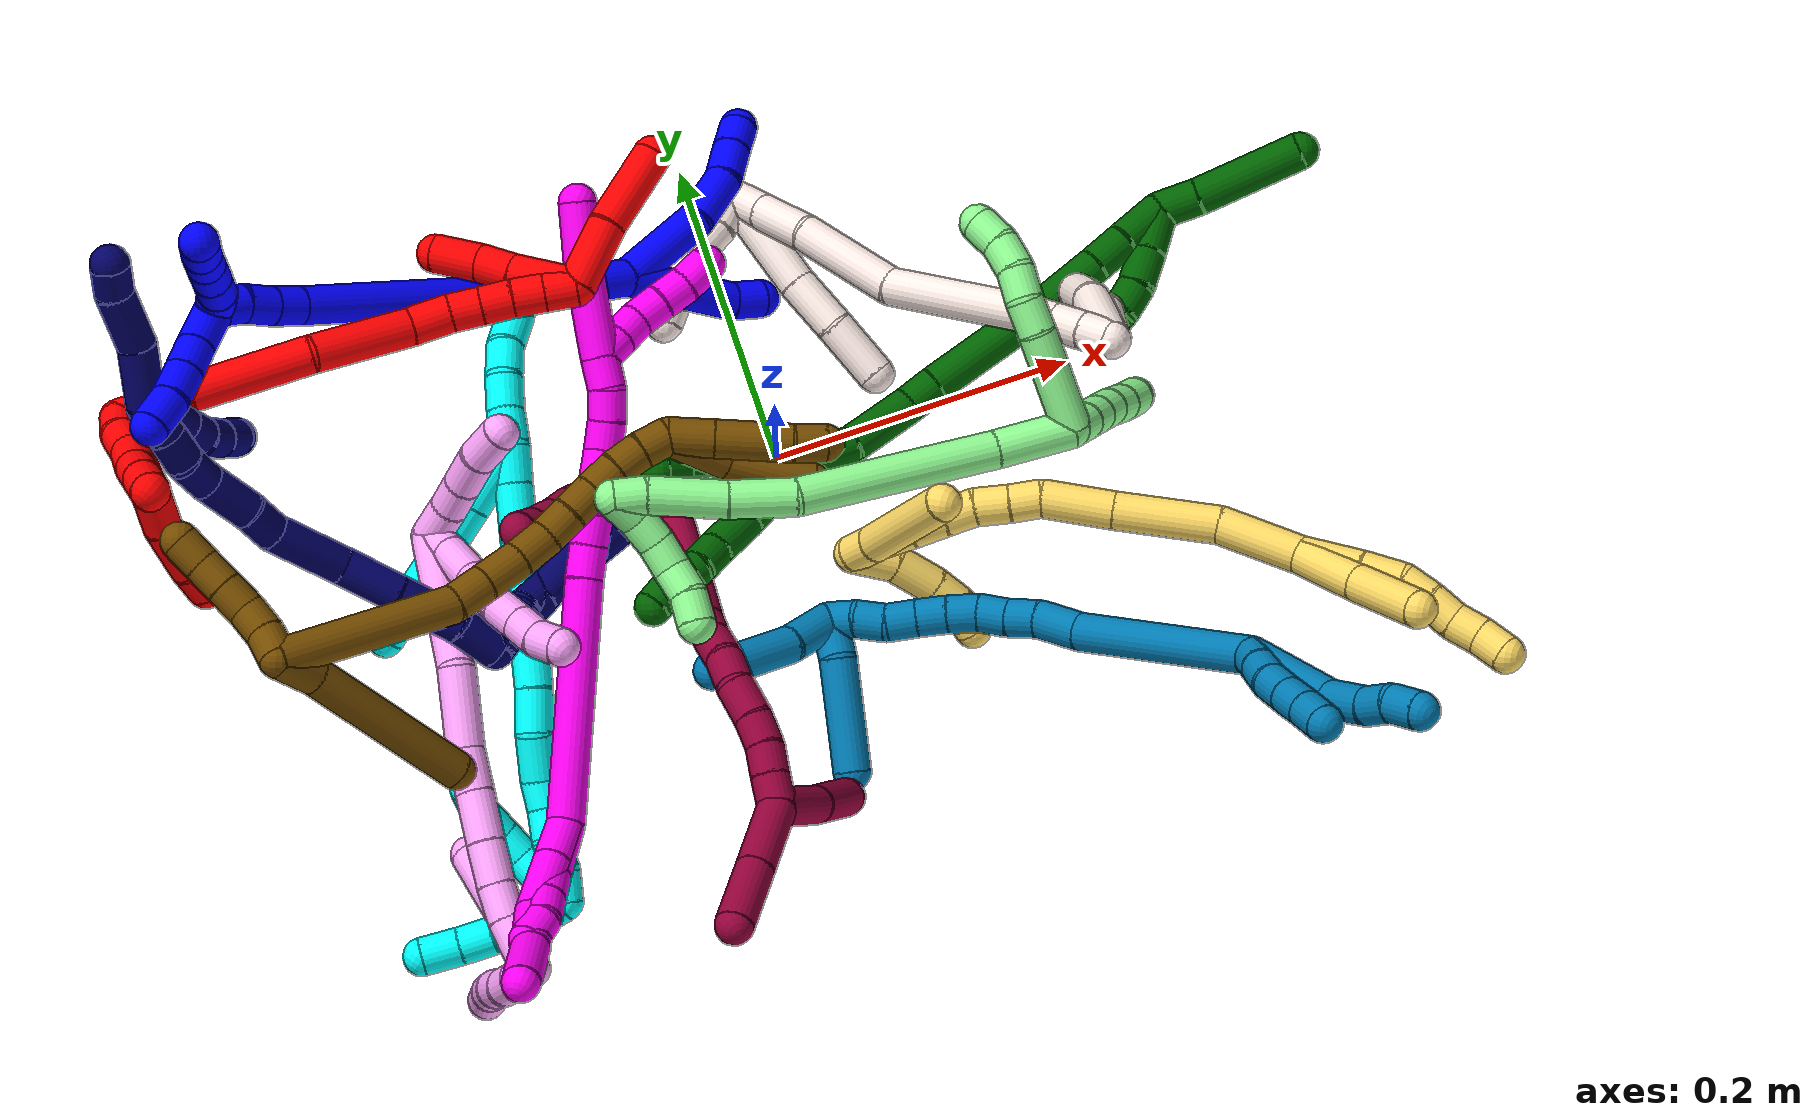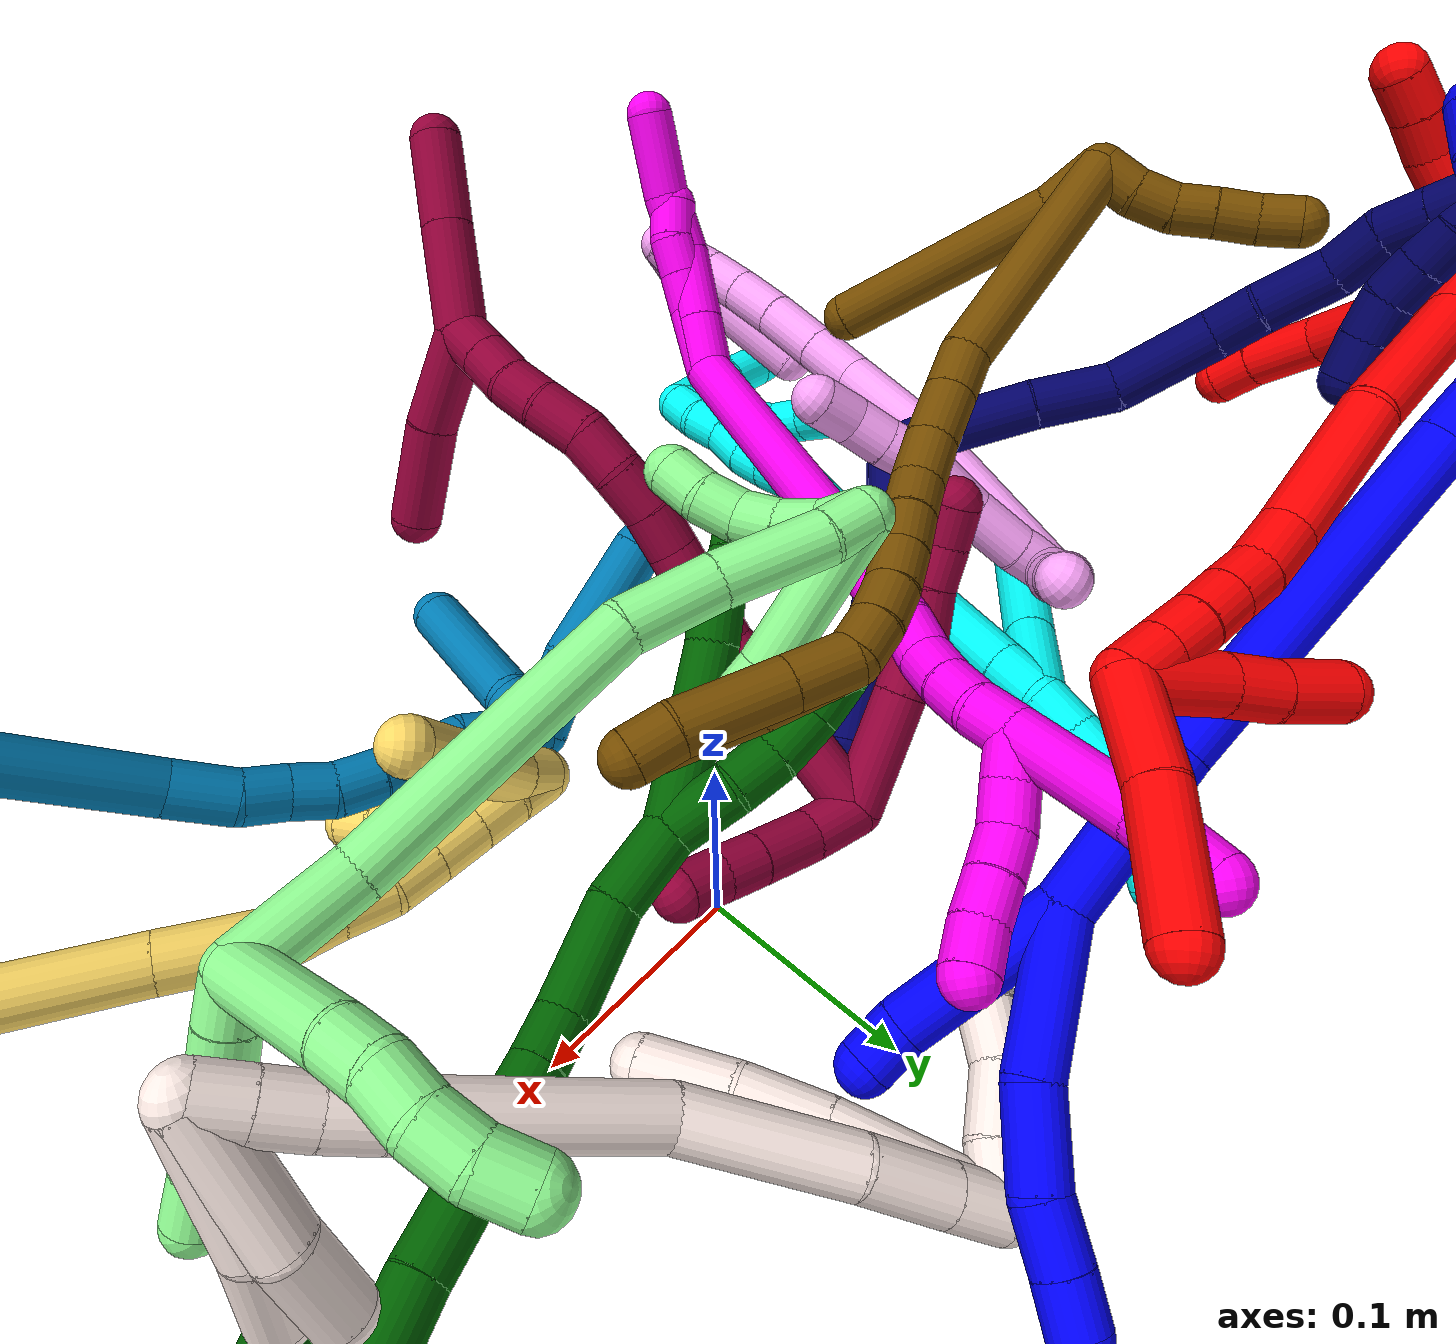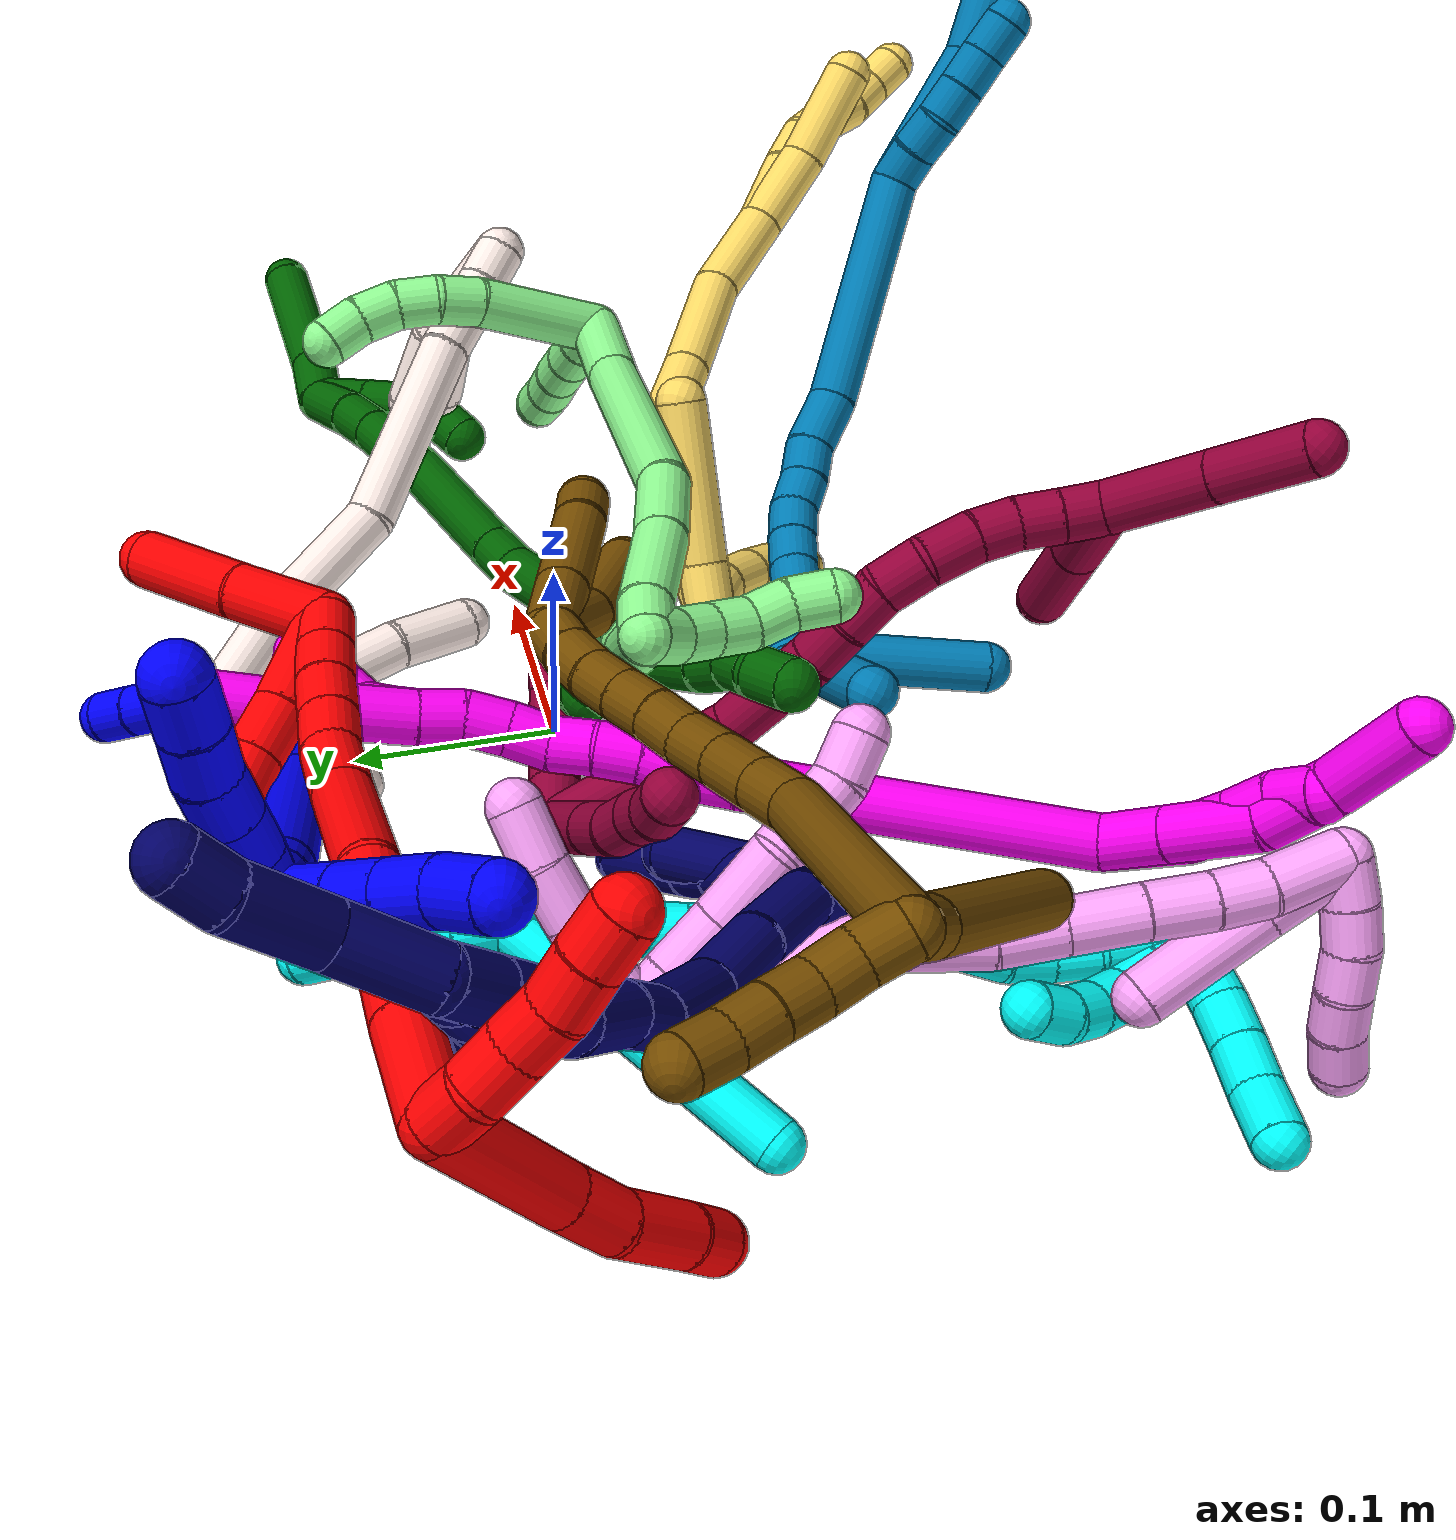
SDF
<sdf version="1.7">
 <world name="default">
  <plugin name="TubeGeneratorPlugin" filename="libtube_generator_plugin.so"/>
  <model name="photoneo_s_sensor">
   <static>1</static>
   <pose>0 0 2 1.57079 1.57079 3.14159</pose>
   <link name="link">
    <inertial><mass>0.1</mass></inertial>
    <sensor name="sensor" type="depth">
     <update_rate>30</update_rate>
     <camera>
      <horizontal_fov>1.22</horizontal_fov>
      <image><width>1920</width><height>1200</height><format>B8G8R8</format></image>
      <clip><near>0.1</near><far>4</far></clip>
      <depth_camera><output>points</output></depth_camera>
     </camera>
     <plugin name="camera_plugin" filename="libgazebo_ros_depth_camera.so">
      <baseline>0.2</baseline>
      <alwaysOn>1</alwaysOn>
      <updateRate>0.0</updateRate>
      <cameraName>camera_ir</cameraName>
      <imageTopicName>/camera/color/image_raw</imageTopicName>
      <cameraInfoTopicName>/camera/color/camera_info</cameraInfoTopicName>
      <depthImageTopicName>/camera/depth/image_raw</depthImageTopicName>
      <depthImageCameraInfoTopicName>/camera/depth/camera_info</depthImageCameraInfoTopicName>
      <pointCloudTopicName>/camera/depth/points</pointCloudTopicName>
      <frameName>fr_optical</frameName>
      <pointCloudCutoff>0.1</pointCloudCutoff>
      <pointCloudCutoffMax>2.0</pointCloudCutoffMax>
      <distortionK1>0</distortionK1>
      <distortionK2>0</distortionK2>
      <distortionK3>0</distortionK3>
      <distortionT1>0</distortionT1>
      <distortionT2>0</distortionT2>
      <CxPrime>0</CxPrime>
      <Cx>0</Cx>
      <Cy>0</Cy>
      <focalLength>0</focalLength>
      <hackBaseline>0</hackBaseline>
     </plugin>
    </sensor>
   </link>
  </model>
  <gravity>0 0 -9.8</gravity>
  <magnetic_field>6e-06 2.3e-05 -4.2e-05</magnetic_field>
  <atmosphere type="adiabatic"/>
  <physics name="default_physics" default="0" type="ode">
   <max_step_size>0.003</max_step_size>
   <real_time_factor>1</real_time_factor>
   <real_time_update_rate>1000</real_time_update_rate>
   <max_contacts>10000</max_contacts>
   <ode>
    <solver>
     <type>quick</type>
     <iters>100</iters>
     <sor>1.3</sor>
     <use_dynamic_moi_rescaling>0</use_dynamic_moi_rescaling>
    </solver>
    <constraints>
     <contact_max_correcting_vel>0</contact_max_correcting_vel>
     <contact_surface_layer>0.001</contact_surface_layer>
     <cfm>0</cfm>
     <erp>0.2</erp>
    </constraints>
   </ode>
  </physics>
  <scene><ambient>0.4 0.4 0.4 1</ambient><background>0.7 0.7 0.7 1</background><shadows>0</shadows></scene>
  <audio><device>default</device></audio>
  <spherical_coordinates>
   <surface_model>EARTH_WGS84</surface_model>
   <latitude_deg>0</latitude_deg>
   <longitude_deg>0</longitude_deg>
   <elevation>0</elevation>
   <heading_deg>0</heading_deg>
  </spherical_coordinates>
  <model name="bin">
   <static>1</static>
   <link name="bottom">
    <collision name="collision-bottom">
     <pose>0 0 -0.01 0 -0 0</pose>
     <geometry><box><size>0.8 0.6 0.02</size></box></geometry>
     <surface>
      <friction><ode><mu>100</mu><mu2>100</mu2></ode></friction>
      <contact><collide_bitmask>65535</collide_bitmask></contact>
     </surface>
    </collision>
   </link>
   <link name="west_wall">
    <collision name="collision-west_wall">
     <pose>-0.41 0 0.1 0 -0 0</pose>
     <geometry><box><size>0.02 0.6 0.2</size></box></geometry>
     <surface>
      <friction><ode><mu>100</mu><mu2>100</mu2></ode></friction>
      <contact><collide_bitmask>65535</collide_bitmask></contact>
     </surface>
    </collision>
   </link>
   <link name="east_wall">
    <collision name="collision-east_wall">
     <pose>0.41 0 0.1 0 -0 0</pose>
     <geometry><box><size>0.02 0.6 0.2</size></box></geometry>
     <surface>
      <friction><ode><mu>100</mu><mu2>100</mu2></ode></friction>
      <contact><collide_bitmask>65535</collide_bitmask></contact>
     </surface>
    </collision>
   </link>
   <link name="south_wall">
    <collision name="collision-south_wall">
     <pose>0 -0.31 0.1 0 -0 0</pose>
     <geometry><box><size>0.8 0.02 0.2</size></box></geometry>
     <surface>
      <friction><ode><mu>100</mu><mu2>100</mu2></ode></friction>
      <contact><collide_bitmask>65535</collide_bitmask></contact>
     </surface>
    </collision>
   </link>
   <link name="north_wall">
    <collision name="collision-north_wall">
     <pose>0 0.31 0.1 0 -0 0</pose>
     <geometry><box><size>0.8 0.02 0.2</size></box></geometry>
     <surface>
      <friction><ode><mu>100</mu><mu2>100</mu2></ode></friction>
      <contact><collide_bitmask>65535</collide_bitmask></contact>
     </surface>
    </collision>
   </link>
  </model>
  <model name="1">
   <static>0</static>
   <link name="1">
    <collision name="collision-cylinder-e_1_2_8">
     <pose>0.011967 -0.011154 -0.028101 2.76375 0.3769 1.56823</pose>
     <geometry><cylinder><radius>0.0125</radius><length>0.065031</length></cylinder></geometry>
     <surface>
      <friction><ode><mu>1.16</mu><mu2>1.16</mu2><slip1>0</slip1><slip2>0</slip2></ode></friction>
      <contact><ode><kp>1e+06</kp><kd>1</kd><max_vel>0</max_vel><min_depth>0.001</min_depth></ode></contact>
     </surface>
    </collision>
    <visual name="visual-cylinder-e_1_2_8">
     <pose>0.011967 -0.011154 -0.028101 2.76375 0.3769 1.56823</pose>
     <geometry><cylinder><radius>0.0125</radius><length>0.065031</length></cylinder></geometry>
     <material><ambient>0 0 1 1</ambient></material>
    </visual>
    <collision name="collision-cylinder-e_2_8_9">
     <pose>0.035371 -0.02896 -0.070115 2.69561 0.638098 1.93843</pose>
     <geometry><cylinder><radius>0.0125</radius><length>0.038401</length></cylinder></geometry>
     <surface>
      <friction><ode><mu>1.16</mu><mu2>1.16</mu2><slip1>0</slip1><slip2>0</slip2></ode></friction>
      <contact><ode><kp>1e+06</kp><kd>1</kd><max_vel>0</max_vel><min_depth>0.001</min_depth></ode></contact>
     </surface>
    </collision>
    <visual name="visual-cylinder-e_2_8_9">
     <pose>0.035371 -0.02896 -0.070115 2.69561 0.638098 1.93843</pose>
     <geometry><cylinder><radius>0.0125</radius><length>0.038401</length></cylinder></geometry>
     <material><ambient>0 0 1 1</ambient></material>
    </visual>
    <collision name="collision-cylinder-e_3_9_10">
     <pose>0.056917 -0.039436 -0.090852 2.63074 0.91227 2.16342</pose>
     <geometry><cylinder><radius>0.0125</radius><length>0.025563</length></cylinder></geometry>
     <surface>
      <friction><ode><mu>1.16</mu><mu2>1.16</mu2><slip1>0</slip1><slip2>0</slip2></ode></friction>
      <contact><ode><kp>1e+06</kp><kd>1</kd><max_vel>0</max_vel><min_depth>0.001</min_depth></ode></contact>
     </surface>
    </collision>
    <visual name="visual-cylinder-e_3_9_10">
     <pose>0.056917 -0.039436 -0.090852 2.63074 0.91227 2.16342</pose>
     <geometry><cylinder><radius>0.0125</radius><length>0.025563</length></cylinder></geometry>
     <material><ambient>0 0 1 1</ambient></material>
    </visual>
    <collision name="collision-cylinder-e_4_10_6">
     <pose>0.075191 -0.046229 -0.103576 2.67551 0.890599 2.21859</pose>
     <geometry><cylinder><radius>0.0125</radius><length>0.021006</length></cylinder></geometry>
     <surface>
      <friction><ode><mu>1.16</mu><mu2>1.16</mu2><slip1>0</slip1><slip2>0</slip2></ode></friction>
      <contact><ode><kp>1e+06</kp><kd>1</kd><max_vel>0</max_vel><min_depth>0.001</min_depth></ode></contact>
     </surface>
    </collision>
    <visual name="visual-cylinder-e_4_10_6">
     <pose>0.075191 -0.046229 -0.103576 2.67551 0.890599 2.21859</pose>
     <geometry><cylinder><radius>0.0125</radius><length>0.021006</length></cylinder></geometry>
     <material><ambient>0 0 1 1</ambient></material>
    </visual>
    <collision name="collision-cylinder-e_1_2_11">
     <pose>-0.004674 0.010589 -0.037719 -2.86789 -0.118735 0.814916</pose>
     <geometry><cylinder><radius>0.0125</radius><length>0.078911</length></cylinder></geometry>
     <surface>
      <friction><ode><mu>1.16</mu><mu2>1.16</mu2><slip1>0</slip1><slip2>0</slip2></ode></friction>
      <contact><ode><kp>1e+06</kp><kd>1</kd><max_vel>0</max_vel><min_depth>0.001</min_depth></ode></contact>
     </surface>
    </collision>
    <visual name="visual-cylinder-e_1_2_11">
     <pose>-0.004674 0.010589 -0.037719 -2.86789 -0.118735 0.814916</pose>
     <geometry><cylinder><radius>0.0125</radius><length>0.078911</length></cylinder></geometry>
     <material><ambient>0 0 1 1</ambient></material>
    </visual>
    <collision name="collision-cylinder-e_2_11_5">
     <pose>-0.009932 0.021087 -0.085967 3.13286 -0.055475 -2.82924</pose>
     <geometry><cylinder><radius>0.0125</radius><length>0.021089</length></cylinder></geometry>
     <surface>
      <friction><ode><mu>1.16</mu><mu2>1.16</mu2><slip1>0</slip1><slip2>0</slip2></ode></friction>
      <contact><ode><kp>1e+06</kp><kd>1</kd><max_vel>0</max_vel><min_depth>0.001</min_depth></ode></contact>
     </surface>
    </collision>
    <visual name="visual-cylinder-e_2_11_5">
     <pose>-0.009932 0.021087 -0.085967 3.13286 -0.055475 -2.82924</pose>
     <geometry><cylinder><radius>0.0125</radius><length>0.021089</length></cylinder></geometry>
     <material><ambient>0 0 1 1</ambient></material>
    </visual>
    <collision name="collision-cylinder-e_1_2_12">
     <pose>-0.002857 -0.000427 0.039025 0.010941 -0.073074 -0.0004</pose>
     <geometry><cylinder><radius>0.0125</radius><length>0.078264</length></cylinder></geometry>
     <surface>
      <friction><ode><mu>1.16</mu><mu2>1.16</mu2><slip1>0</slip1><slip2>0</slip2></ode></friction>
      <contact><ode><kp>1e+06</kp><kd>1</kd><max_vel>0</max_vel><min_depth>0.001</min_depth></ode></contact>
     </surface>
    </collision>
    <visual name="visual-cylinder-e_1_2_12">
     <pose>-0.002857 -0.000427 0.039025 0.010941 -0.073074 -0.0004</pose>
     <geometry><cylinder><radius>0.0125</radius><length>0.078264</length></cylinder></geometry>
     <material><ambient>0 0 1 1</ambient></material>
    </visual>
    <collision name="collision-cylinder-e_2_12_13">
     <pose>-0.00979 -0.008701 0.157763 0.098122 -0.05085 -0.002497</pose>
     <geometry><cylinder><radius>0.0125</radius><length>0.160403</length></cylinder></geometry>
     <surface>
      <friction><ode><mu>1.16</mu><mu2>1.16</mu2><slip1>0</slip1><slip2>0</slip2></ode></friction>
      <contact><ode><kp>1e+06</kp><kd>1</kd><max_vel>0</max_vel><min_depth>0.001</min_depth></ode></contact>
     </surface>
    </collision>
    <visual name="visual-cylinder-e_2_12_13">
     <pose>-0.00979 -0.008701 0.157763 0.098122 -0.05085 -0.002497</pose>
     <geometry><cylinder><radius>0.0125</radius><length>0.160403</length></cylinder></geometry>
     <material><ambient>0 0 1 1</ambient></material>
    </visual>
    <collision name="collision-cylinder-e_3_13_14">
     <pose>-0.014378 -0.018026 0.247354 0.14858 -0.051104 -0.003804</pose>
     <geometry><cylinder><radius>0.0125</radius><length>0.020004</length></cylinder></geometry>
     <surface>
      <friction><ode><mu>1.16</mu><mu2>1.16</mu2><slip1>0</slip1><slip2>0</slip2></ode></friction>
      <contact><ode><kp>1e+06</kp><kd>1</kd><max_vel>0</max_vel><min_depth>0.001</min_depth></ode></contact>
     </surface>
    </collision>
    <visual name="visual-cylinder-e_3_13_14">
     <pose>-0.014378 -0.018026 0.247354 0.14858 -0.051104 -0.003804</pose>
     <geometry><cylinder><radius>0.0125</radius><length>0.020004</length></cylinder></geometry>
     <material><ambient>0 0 1 1</ambient></material>
    </visual>
    <collision name="collision-cylinder-e_4_14_15">
     <pose>-0.015301 -0.021963 0.26745 0.236134 -0.039241 -0.004655</pose>
     <geometry><cylinder><radius>0.0125</radius><length>0.021035</length></cylinder></geometry>
     <surface>
      <friction><ode><mu>1.16</mu><mu2>1.16</mu2><slip1>0</slip1><slip2>0</slip2></ode></friction>
      <contact><ode><kp>1e+06</kp><kd>1</kd><max_vel>0</max_vel><min_depth>0.001</min_depth></ode></contact>
     </surface>
    </collision>
    <visual name="visual-cylinder-e_4_14_15">
     <pose>-0.015301 -0.021963 0.26745 0.236134 -0.039241 -0.004655</pose>
     <geometry><cylinder><radius>0.0125</radius><length>0.021035</length></cylinder></geometry>
     <material><ambient>0 0 1 1</ambient></material>
    </visual>
    <collision name="collision-cylinder-e_5_15_1">
     <pose>-0.017089 -0.024955 0.287708 0.053045 -0.135957 -0.003612</pose>
     <geometry><cylinder><radius>0.0125</radius><length>0.020295</length></cylinder></geometry>
     <surface>
      <friction><ode><mu>1.16</mu><mu2>1.16</mu2><slip1>0</slip1><slip2>0</slip2></ode></friction>
      <contact><ode><kp>1e+06</kp><kd>1</kd><max_vel>0</max_vel><min_depth>0.001</min_depth></ode></contact>
     </surface>
    </collision>
    <visual name="visual-cylinder-e_5_15_1">
     <pose>-0.017089 -0.024955 0.287708 0.053045 -0.135957 -0.003612</pose>
     <geometry><cylinder><radius>0.0125</radius><length>0.020295</length></cylinder></geometry>
     <material><ambient>0 0 1 1</ambient></material>
    </visual>
    <collision name="collision-cylinder-e_1_1_16">
     <pose>-0.0304 -0.020469 0.308024 -0.45436 -0.806691 0.196664</pose>
     <geometry><cylinder><radius>0.0125</radius><length>0.03306</length></cylinder></geometry>
     <surface>
      <friction><ode><mu>1.16</mu><mu2>1.16</mu2><slip1>0</slip1><slip2>0</slip2></ode></friction>
      <contact><ode><kp>1e+06</kp><kd>1</kd><max_vel>0</max_vel><min_depth>0.001</min_depth></ode></contact>
     </surface>
    </collision>
    <visual name="visual-cylinder-e_1_1_16">
     <pose>-0.0304 -0.020469 0.308024 -0.45436 -0.806691 0.196664</pose>
     <geometry><cylinder><radius>0.0125</radius><length>0.03306</length></cylinder></geometry>
     <material><ambient>0 0 1 1</ambient></material>
    </visual>
    <collision name="collision-cylinder-e_2_16_17">
     <pose>-0.049939 -0.012236 0.324605 -0.471346 -0.82138 0.208377</pose>
     <geometry><cylinder><radius>0.0125</radius><length>0.020775</length></cylinder></geometry>
     <surface>
      <friction><ode><mu>1.16</mu><mu2>1.16</mu2><slip1>0</slip1><slip2>0</slip2></ode></friction>
      <contact><ode><kp>1e+06</kp><kd>1</kd><max_vel>0</max_vel><min_depth>0.001</min_depth></ode></contact>
     </surface>
    </collision>
    <visual name="visual-cylinder-e_2_16_17">
     <pose>-0.049939 -0.012236 0.324605 -0.471346 -0.82138 0.208377</pose>
     <geometry><cylinder><radius>0.0125</radius><length>0.020775</length></cylinder></geometry>
     <material><ambient>0 0 1 1</ambient></material>
    </visual>
    <collision name="collision-cylinder-e_3_17_18">
     <pose>-0.06566 -0.005712 0.337768 -0.449749 -0.817241 0.197444</pose>
     <geometry><cylinder><radius>0.0125</radius><length>0.022258</length></cylinder></geometry>
     <surface>
      <friction><ode><mu>1.16</mu><mu2>1.16</mu2><slip1>0</slip1><slip2>0</slip2></ode></friction>
      <contact><ode><kp>1e+06</kp><kd>1</kd><max_vel>0</max_vel><min_depth>0.001</min_depth></ode></contact>
     </surface>
    </collision>
    <visual name="visual-cylinder-e_3_17_18">
     <pose>-0.06566 -0.005712 0.337768 -0.449749 -0.817241 0.197444</pose>
     <geometry><cylinder><radius>0.0125</radius><length>0.022258</length></cylinder></geometry>
     <material><ambient>0 0 1 1</ambient></material>
    </visual>
    <collision name="collision-cylinder-e_4_18_4">
     <pose>-0.080913 0.001386 0.353434 -0.406018 -0.639851 0.136185</pose>
     <geometry><cylinder><radius>0.0125</radius><length>0.023906</length></cylinder></geometry>
     <surface>
      <friction><ode><mu>1.16</mu><mu2>1.16</mu2><slip1>0</slip1><slip2>0</slip2></ode></friction>
      <contact><ode><kp>1e+06</kp><kd>1</kd><max_vel>0</max_vel><min_depth>0.001</min_depth></ode></contact>
     </surface>
    </collision>
    <visual name="visual-cylinder-e_4_18_4">
     <pose>-0.080913 0.001386 0.353434 -0.406018 -0.639851 0.136185</pose>
     <geometry><cylinder><radius>0.0125</radius><length>0.023906</length></cylinder></geometry>
     <material><ambient>0 0 1 1</ambient></material>
    </visual>
    <collision name="collision-cylinder-e_1_1_19">
     <pose>-0.022521 -0.03439 0.299822 1.34187 -0.417623 -0.333284</pose>
     <geometry><cylinder><radius>0.0125</radius><length>0.02</length></cylinder></geometry>
     <surface>
      <friction><ode><mu>1.16</mu><mu2>1.16</mu2><slip1>0</slip1><slip2>0</slip2></ode></friction>
      <contact><ode><kp>1e+06</kp><kd>1</kd><max_vel>0</max_vel><min_depth>0.001</min_depth></ode></contact>
     </surface>
    </collision>
    <visual name="visual-cylinder-e_1_1_19">
     <pose>-0.022521 -0.03439 0.299822 1.34187 -0.417623 -0.333284</pose>
     <geometry><cylinder><radius>0.0125</radius><length>0.02</length></cylinder></geometry>
     <material><ambient>0 0 1 1</ambient></material>
    </visual>
    <collision name="collision-cylinder-e_2_19_20">
     <pose>-0.030026 -0.051584 0.306295 1.08299 -0.352191 -0.213235</pose>
     <geometry><cylinder><radius>0.0125</radius><length>0.02</length></cylinder></geometry>
     <surface>
      <friction><ode><mu>1.16</mu><mu2>1.16</mu2><slip1>0</slip1><slip2>0</slip2></ode></friction>
      <contact><ode><kp>1e+06</kp><kd>1</kd><max_vel>0</max_vel><min_depth>0.001</min_depth></ode></contact>
     </surface>
    </collision>
    <visual name="visual-cylinder-e_2_19_20">
     <pose>-0.030026 -0.051584 0.306295 1.08299 -0.352191 -0.213235</pose>
     <geometry><cylinder><radius>0.0125</radius><length>0.02</length></cylinder></geometry>
     <material><ambient>0 0 1 1</ambient></material>
    </visual>
    <collision name="collision-cylinder-e_3_20_21">
     <pose>-0.036901 -0.068096 0.315242 1.06553 -0.349591 -0.20751</pose>
     <geometry><cylinder><radius>0.0125</radius><length>0.02</length></cylinder></geometry>
     <surface>
      <friction><ode><mu>1.16</mu><mu2>1.16</mu2><slip1>0</slip1><slip2>0</slip2></ode></friction>
      <contact><ode><kp>1e+06</kp><kd>1</kd><max_vel>0</max_vel><min_depth>0.001</min_depth></ode></contact>
     </surface>
    </collision>
    <visual name="visual-cylinder-e_3_20_21">
     <pose>-0.036901 -0.068096 0.315242 1.06553 -0.349591 -0.20751</pose>
     <geometry><cylinder><radius>0.0125</radius><length>0.02</length></cylinder></geometry>
     <material><ambient>0 0 1 1</ambient></material>
    </visual>
    <collision name="collision-cylinder-e_4_21_22">
     <pose>-0.045043 -0.084022 0.324078 1.06292 -0.491248 -0.292639</pose>
     <geometry><cylinder><radius>0.0125</radius><length>0.02</length></cylinder></geometry>
     <surface>
      <friction><ode><mu>1.16</mu><mu2>1.16</mu2><slip1>0</slip1><slip2>0</slip2></ode></friction>
      <contact><ode><kp>1e+06</kp><kd>1</kd><max_vel>0</max_vel><min_depth>0.001</min_depth></ode></contact>
     </surface>
    </collision>
    <visual name="visual-cylinder-e_4_21_22">
     <pose>-0.045043 -0.084022 0.324078 1.06292 -0.491248 -0.292639</pose>
     <geometry><cylinder><radius>0.0125</radius><length>0.02</length></cylinder></geometry>
     <material><ambient>0 0 1 1</ambient></material>
    </visual>
    <collision name="collision-cylinder-e_5_22_3">
     <pose>-0.054353 -0.099776 0.332123 1.13407 -0.477188 -0.307327</pose>
     <geometry><cylinder><radius>0.0125</radius><length>0.02</length></cylinder></geometry>
     <surface>
      <friction><ode><mu>1.16</mu><mu2>1.16</mu2><slip1>0</slip1><slip2>0</slip2></ode></friction>
      <contact><ode><kp>1e+06</kp><kd>1</kd><max_vel>0</max_vel><min_depth>0.001</min_depth></ode></contact>
     </surface>
    </collision>
    <visual name="visual-cylinder-e_5_22_3">
     <pose>-0.054353 -0.099776 0.332123 1.13407 -0.477188 -0.307327</pose>
     <geometry><cylinder><radius>0.0125</radius><length>0.02</length></cylinder></geometry>
     <material><ambient>0 0 1 1</ambient></material>
    </visual>
    <collision name="collision-sphere-3">
     <pose>-0.058946 -0.107825 0.33588 0 -0 0</pose>
     <geometry><sphere><radius>0.0125</radius></sphere></geometry>
     <surface>
      <friction><ode><mu>1.16</mu><mu2>1.16</mu2><slip1>0</slip1><slip2>0</slip2></ode></friction>
      <contact><ode><kp>1e+06</kp><kd>1</kd><max_vel>0</max_vel><min_depth>0.001</min_depth></ode></contact>
     </surface>
    </collision>
    <visual name="visual-sphere-3">
     <pose>-0.058946 -0.107825 0.33588 0 -0 0</pose>
     <geometry><sphere><radius>0.0125</radius></sphere></geometry>
     <material><ambient>0 0 1 1</ambient></material>
    </visual>
    <collision name="collision-sphere-22">
     <pose>-0.04976 -0.091726 0.328366 0 -0 0</pose>
     <geometry><sphere><radius>0.0125</radius></sphere></geometry>
     <surface>
      <friction><ode><mu>1.16</mu><mu2>1.16</mu2><slip1>0</slip1><slip2>0</slip2></ode></friction>
      <contact><ode><kp>1e+06</kp><kd>1</kd><max_vel>0</max_vel><min_depth>0.001</min_depth></ode></contact>
     </surface>
    </collision>
    <visual name="visual-sphere-22">
     <pose>-0.04976 -0.091726 0.328366 0 -0 0</pose>
     <geometry><sphere><radius>0.0125</radius></sphere></geometry>
     <material><ambient>0 0 1 1</ambient></material>
    </visual>
    <collision name="collision-sphere-21">
     <pose>-0.040326 -0.076317 0.31979 0 -0 0</pose>
     <geometry><sphere><radius>0.0125</radius></sphere></geometry>
     <surface>
      <friction><ode><mu>1.16</mu><mu2>1.16</mu2><slip1>0</slip1><slip2>0</slip2></ode></friction>
      <contact><ode><kp>1e+06</kp><kd>1</kd><max_vel>0</max_vel><min_depth>0.001</min_depth></ode></contact>
     </surface>
    </collision>
    <visual name="visual-sphere-21">
     <pose>-0.040326 -0.076317 0.31979 0 -0 0</pose>
     <geometry><sphere><radius>0.0125</radius></sphere></geometry>
     <material><ambient>0 0 1 1</ambient></material>
    </visual>
    <collision name="collision-sphere-20">
     <pose>-0.033476 -0.059875 0.310694 0 -0 0</pose>
     <geometry><sphere><radius>0.0125</radius></sphere></geometry>
     <surface>
      <friction><ode><mu>1.16</mu><mu2>1.16</mu2><slip1>0</slip1><slip2>0</slip2></ode></friction>
      <contact><ode><kp>1e+06</kp><kd>1</kd><max_vel>0</max_vel><min_depth>0.001</min_depth></ode></contact>
     </surface>
    </collision>
    <visual name="visual-sphere-20">
     <pose>-0.033476 -0.059875 0.310694 0 -0 0</pose>
     <geometry><sphere><radius>0.0125</radius></sphere></geometry>
     <material><ambient>0 0 1 1</ambient></material>
    </visual>
    <collision name="collision-sphere-19">
     <pose>-0.026576 -0.043292 0.301896 0 -0 0</pose>
     <geometry><sphere><radius>0.0125</radius></sphere></geometry>
     <surface>
      <friction><ode><mu>1.16</mu><mu2>1.16</mu2><slip1>0</slip1><slip2>0</slip2></ode></friction>
      <contact><ode><kp>1e+06</kp><kd>1</kd><max_vel>0</max_vel><min_depth>0.001</min_depth></ode></contact>
     </surface>
    </collision>
    <visual name="visual-sphere-19">
     <pose>-0.026576 -0.043292 0.301896 0 -0 0</pose>
     <geometry><sphere><radius>0.0125</radius></sphere></geometry>
     <material><ambient>0 0 1 1</ambient></material>
    </visual>
    <collision name="collision-sphere-11">
     <pose>-0.009347 0.021179 -0.075439 0 -0 0</pose>
     <geometry><sphere><radius>0.0125</radius></sphere></geometry>
     <surface>
      <friction><ode><mu>1.16</mu><mu2>1.16</mu2><slip1>0</slip1><slip2>0</slip2></ode></friction>
      <contact><ode><kp>1e+06</kp><kd>1</kd><max_vel>0</max_vel><min_depth>0.001</min_depth></ode></contact>
     </surface>
    </collision>
    <visual name="visual-sphere-11">
     <pose>-0.009347 0.021179 -0.075439 0 -0 0</pose>
     <geometry><sphere><radius>0.0125</radius></sphere></geometry>
     <material><ambient>0 0 1 1</ambient></material>
    </visual>
    <collision name="collision-sphere-6">
     <pose>0.083356 -0.049197 -0.109477 0 -0 0</pose>
     <geometry><sphere><radius>0.0125</radius></sphere></geometry>
     <surface>
      <friction><ode><mu>1.16</mu><mu2>1.16</mu2><slip1>0</slip1><slip2>0</slip2></ode></friction>
      <contact><ode><kp>1e+06</kp><kd>1</kd><max_vel>0</max_vel><min_depth>0.001</min_depth></ode></contact>
     </surface>
    </collision>
    <visual name="visual-sphere-6">
     <pose>0.083356 -0.049197 -0.109477 0 -0 0</pose>
     <geometry><sphere><radius>0.0125</radius></sphere></geometry>
     <material><ambient>0 0 1 1</ambient></material>
    </visual>
    <collision name="collision-sphere-10">
     <pose>0.067025 -0.04326 -0.097675 0 -0 0</pose>
     <geometry><sphere><radius>0.0125</radius></sphere></geometry>
     <surface>
      <friction><ode><mu>1.16</mu><mu2>1.16</mu2><slip1>0</slip1><slip2>0</slip2></ode></friction>
      <contact><ode><kp>1e+06</kp><kd>1</kd><max_vel>0</max_vel><min_depth>0.001</min_depth></ode></contact>
     </surface>
    </collision>
    <visual name="visual-sphere-10">
     <pose>0.067025 -0.04326 -0.097675 0 -0 0</pose>
     <geometry><sphere><radius>0.0125</radius></sphere></geometry>
     <material><ambient>0 0 1 1</ambient></material>
    </visual>
    <collision name="collision-sphere-9">
     <pose>0.046808 -0.035612 -0.084029 0 -0 0</pose>
     <geometry><sphere><radius>0.0125</radius></sphere></geometry>
     <surface>
      <friction><ode><mu>1.16</mu><mu2>1.16</mu2><slip1>0</slip1><slip2>0</slip2></ode></friction>
      <contact><ode><kp>1e+06</kp><kd>1</kd><max_vel>0</max_vel><min_depth>0.001</min_depth></ode></contact>
     </surface>
    </collision>
    <visual name="visual-sphere-9">
     <pose>0.046808 -0.035612 -0.084029 0 -0 0</pose>
     <geometry><sphere><radius>0.0125</radius></sphere></geometry>
     <material><ambient>0 0 1 1</ambient></material>
    </visual>
    <collision name="collision-sphere-2">
     <geometry><sphere><radius>0.0125</radius></sphere></geometry>
     <surface>
      <friction><ode><mu>1.16</mu><mu2>1.16</mu2><slip1>0</slip1><slip2>0</slip2></ode></friction>
      <contact><ode><kp>1e+06</kp><kd>1</kd><max_vel>0</max_vel><min_depth>0.001</min_depth></ode></contact>
     </surface>
    </collision>
    <visual name="visual-sphere-2">
     <geometry><sphere><radius>0.0125</radius></sphere></geometry>
     <material><ambient>0 0 1 1</ambient></material>
    </visual>
    <collision name="collision-sphere-8">
     <pose>0.023934 -0.022307 -0.056201 0 -0 0</pose>
     <geometry><sphere><radius>0.0125</radius></sphere></geometry>
     <surface>
      <friction><ode><mu>1.16</mu><mu2>1.16</mu2><slip1>0</slip1><slip2>0</slip2></ode></friction>
      <contact><ode><kp>1e+06</kp><kd>1</kd><max_vel>0</max_vel><min_depth>0.001</min_depth></ode></contact>
     </surface>
    </collision>
    <visual name="visual-sphere-8">
     <pose>0.023934 -0.022307 -0.056201 0 -0 0</pose>
     <geometry><sphere><radius>0.0125</radius></sphere></geometry>
     <material><ambient>0 0 1 1</ambient></material>
    </visual>
    <collision name="collision-sphere-5">
     <pose>-0.010517 0.020995 -0.096495 0 -0 0</pose>
     <geometry><sphere><radius>0.0125</radius></sphere></geometry>
     <surface>
      <friction><ode><mu>1.16</mu><mu2>1.16</mu2><slip1>0</slip1><slip2>0</slip2></ode></friction>
      <contact><ode><kp>1e+06</kp><kd>1</kd><max_vel>0</max_vel><min_depth>0.001</min_depth></ode></contact>
     </surface>
    </collision>
    <visual name="visual-sphere-5">
     <pose>-0.010517 0.020995 -0.096495 0 -0 0</pose>
     <geometry><sphere><radius>0.0125</radius></sphere></geometry>
     <material><ambient>0 0 1 1</ambient></material>
    </visual>
    <collision name="collision-sphere-12">
     <pose>-0.005714 -0.000854 0.07805 0 -0 0</pose>
     <geometry><sphere><radius>0.0125</radius></sphere></geometry>
     <surface>
      <friction><ode><mu>1.16</mu><mu2>1.16</mu2><slip1>0</slip1><slip2>0</slip2></ode></friction>
      <contact><ode><kp>1e+06</kp><kd>1</kd><max_vel>0</max_vel><min_depth>0.001</min_depth></ode></contact>
     </surface>
    </collision>
    <visual name="visual-sphere-12">
     <pose>-0.005714 -0.000854 0.07805 0 -0 0</pose>
     <geometry><sphere><radius>0.0125</radius></sphere></geometry>
     <material><ambient>0 0 1 1</ambient></material>
    </visual>
    <collision name="collision-sphere-13">
     <pose>-0.013867 -0.016547 0.237475 0 -0 0</pose>
     <geometry><sphere><radius>0.0125</radius></sphere></geometry>
     <surface>
      <friction><ode><mu>1.16</mu><mu2>1.16</mu2><slip1>0</slip1><slip2>0</slip2></ode></friction>
      <contact><ode><kp>1e+06</kp><kd>1</kd><max_vel>0</max_vel><min_depth>0.001</min_depth></ode></contact>
     </surface>
    </collision>
    <visual name="visual-sphere-13">
     <pose>-0.013867 -0.016547 0.237475 0 -0 0</pose>
     <geometry><sphere><radius>0.0125</radius></sphere></geometry>
     <material><ambient>0 0 1 1</ambient></material>
    </visual>
    <collision name="collision-sphere-14">
     <pose>-0.014889 -0.019505 0.257233 0 -0 0</pose>
     <geometry><sphere><radius>0.0125</radius></sphere></geometry>
     <surface>
      <friction><ode><mu>1.16</mu><mu2>1.16</mu2><slip1>0</slip1><slip2>0</slip2></ode></friction>
      <contact><ode><kp>1e+06</kp><kd>1</kd><max_vel>0</max_vel><min_depth>0.001</min_depth></ode></contact>
     </surface>
    </collision>
    <visual name="visual-sphere-14">
     <pose>-0.014889 -0.019505 0.257233 0 -0 0</pose>
     <geometry><sphere><radius>0.0125</radius></sphere></geometry>
     <material><ambient>0 0 1 1</ambient></material>
    </visual>
    <collision name="collision-sphere-15">
     <pose>-0.015714 -0.024422 0.277668 0 -0 0</pose>
     <geometry><sphere><radius>0.0125</radius></sphere></geometry>
     <surface>
      <friction><ode><mu>1.16</mu><mu2>1.16</mu2><slip1>0</slip1><slip2>0</slip2></ode></friction>
      <contact><ode><kp>1e+06</kp><kd>1</kd><max_vel>0</max_vel><min_depth>0.001</min_depth></ode></contact>
     </surface>
    </collision>
    <visual name="visual-sphere-15">
     <pose>-0.015714 -0.024422 0.277668 0 -0 0</pose>
     <geometry><sphere><radius>0.0125</radius></sphere></geometry>
     <material><ambient>0 0 1 1</ambient></material>
    </visual>
    <collision name="collision-sphere-1">
     <pose>-0.018465 -0.025488 0.297747 0 -0 0</pose>
     <geometry><sphere><radius>0.0125</radius></sphere></geometry>
     <surface>
      <friction><ode><mu>1.16</mu><mu2>1.16</mu2><slip1>0</slip1><slip2>0</slip2></ode></friction>
      <contact><ode><kp>1e+06</kp><kd>1</kd><max_vel>0</max_vel><min_depth>0.001</min_depth></ode></contact>
     </surface>
    </collision>
    <visual name="visual-sphere-1">
     <pose>-0.018465 -0.025488 0.297747 0 -0 0</pose>
     <geometry><sphere><radius>0.0125</radius></sphere></geometry>
     <material><ambient>0 0 1 1</ambient></material>
    </visual>
    <collision name="collision-sphere-18">
     <pose>-0.073776 -0.002401 0.344625 0 -0 0</pose>
     <geometry><sphere><radius>0.0125</radius></sphere></geometry>
     <surface>
      <friction><ode><mu>1.16</mu><mu2>1.16</mu2><slip1>0</slip1><slip2>0</slip2></ode></friction>
      <contact><ode><kp>1e+06</kp><kd>1</kd><max_vel>0</max_vel><min_depth>0.001</min_depth></ode></contact>
     </surface>
    </collision>
    <visual name="visual-sphere-18">
     <pose>-0.073776 -0.002401 0.344625 0 -0 0</pose>
     <geometry><sphere><radius>0.0125</radius></sphere></geometry>
     <material><ambient>0 0 1 1</ambient></material>
    </visual>
    <collision name="collision-sphere-16">
     <pose>-0.042334 -0.015449 0.318301 0 -0 0</pose>
     <geometry><sphere><radius>0.0125</radius></sphere></geometry>
     <surface>
      <friction><ode><mu>1.16</mu><mu2>1.16</mu2><slip1>0</slip1><slip2>0</slip2></ode></friction>
      <contact><ode><kp>1e+06</kp><kd>1</kd><max_vel>0</max_vel><min_depth>0.001</min_depth></ode></contact>
     </surface>
    </collision>
    <visual name="visual-sphere-16">
     <pose>-0.042334 -0.015449 0.318301 0 -0 0</pose>
     <geometry><sphere><radius>0.0125</radius></sphere></geometry>
     <material><ambient>0 0 1 1</ambient></material>
    </visual>
    <collision name="collision-sphere-17">
     <pose>-0.057544 -0.009023 0.33091 0 -0 0</pose>
     <geometry><sphere><radius>0.0125</radius></sphere></geometry>
     <surface>
      <friction><ode><mu>1.16</mu><mu2>1.16</mu2><slip1>0</slip1><slip2>0</slip2></ode></friction>
      <contact><ode><kp>1e+06</kp><kd>1</kd><max_vel>0</max_vel><min_depth>0.001</min_depth></ode></contact>
     </surface>
    </collision>
    <visual name="visual-sphere-17">
     <pose>-0.057544 -0.009023 0.33091 0 -0 0</pose>
     <geometry><sphere><radius>0.0125</radius></sphere></geometry>
     <material><ambient>0 0 1 1</ambient></material>
    </visual>
    <collision name="collision-sphere-4">
     <pose>-0.088049 0.005173 0.362243 0 -0 0</pose>
     <geometry><sphere><radius>0.0125</radius></sphere></geometry>
     <surface>
      <friction><ode><mu>1.16</mu><mu2>1.16</mu2><slip1>0</slip1><slip2>0</slip2></ode></friction>
      <contact><ode><kp>1e+06</kp><kd>1</kd><max_vel>0</max_vel><min_depth>0.001</min_depth></ode></contact>
     </surface>
    </collision>
    <visual name="visual-sphere-4">
     <pose>-0.088049 0.005173 0.362243 0 -0 0</pose>
     <geometry><sphere><radius>0.0125</radius></sphere></geometry>
     <material><ambient>0 0 1 1</ambient></material>
    </visual>
    <inertial>
     <pose>-0.00983 -0.017435 0.127215 0 -0 0</pose>
     <mass>0.75</mass>
     <inertia>
      <ixx>0.000492</ixx>
      <ixy>0</ixy>
      <ixz>0</ixz>
      <iyy>0.000444</iyy>
      <iyz>0</iyz>
      <izz>7.4e-05</izz>
     </inertia>
    </inertial>
   </link>
   <pose>-0.057133 0.130816 0.072401 -1.01108 0.604361 1.79622</pose>
  </model>
  <model name="2">
   <static>0</static>
   <link name="2">
    <collision name="collision-cylinder-e_1_2_8">
     <pose>0.011503 -0.030749 0.002007 1.50562 0.357286 0.335161</pose>
     <geometry><cylinder><radius>0.0125</radius><length>0.065784</length></cylinder></geometry>
     <surface>
      <friction><ode><mu>1.16</mu><mu2>1.16</mu2><slip1>0</slip1><slip2>0</slip2></ode></friction>
      <contact><ode><kp>1e+06</kp><kd>1</kd><max_vel>0</max_vel><min_depth>0.001</min_depth></ode></contact>
     </surface>
    </collision>
    <visual name="visual-cylinder-e_1_2_8">
     <pose>0.011503 -0.030749 0.002007 1.50562 0.357286 0.335161</pose>
     <geometry><cylinder><radius>0.0125</radius><length>0.065784</length></cylinder></geometry>
     <material><ambient>1 0 0 1</ambient></material>
    </visual>
    <collision name="collision-cylinder-e_2_8_9">
     <pose>0.027993 -0.073923 0.005883 1.42148 0.377772 0.326191</pose>
     <geometry><cylinder><radius>0.0125</radius><length>0.027036</length></cylinder></geometry>
     <surface>
      <friction><ode><mu>1.16</mu><mu2>1.16</mu2><slip1>0</slip1><slip2>0</slip2></ode></friction>
      <contact><ode><kp>1e+06</kp><kd>1</kd><max_vel>0</max_vel><min_depth>0.001</min_depth></ode></contact>
     </surface>
    </collision>
    <visual name="visual-cylinder-e_2_8_9">
     <pose>0.027993 -0.073923 0.005883 1.42148 0.377772 0.326191</pose>
     <geometry><cylinder><radius>0.0125</radius><length>0.027036</length></cylinder></geometry>
     <material><ambient>1 0 0 1</ambient></material>
    </visual>
    <collision name="collision-cylinder-e_3_9_10">
     <pose>0.042749 -0.101565 0.00829 1.53547 0.570513 0.551714</pose>
     <geometry><cylinder><radius>0.0125</radius><length>0.036183</length></cylinder></geometry>
     <surface>
      <friction><ode><mu>1.16</mu><mu2>1.16</mu2><slip1>0</slip1><slip2>0</slip2></ode></friction>
      <contact><ode><kp>1e+06</kp><kd>1</kd><max_vel>0</max_vel><min_depth>0.001</min_depth></ode></contact>
     </surface>
    </collision>
    <visual name="visual-cylinder-e_3_9_10">
     <pose>0.042749 -0.101565 0.00829 1.53547 0.570513 0.551714</pose>
     <geometry><cylinder><radius>0.0125</radius><length>0.036183</length></cylinder></geometry>
     <material><ambient>1 0 0 1</ambient></material>
    </visual>
    <collision name="collision-cylinder-e_4_10_6">
     <pose>0.057799 -0.125793 0.007749 1.68992 0.526803 0.590005</pose>
     <geometry><cylinder><radius>0.0125</radius><length>0.020997</length></cylinder></geometry>
     <surface>
      <friction><ode><mu>1.16</mu><mu2>1.16</mu2><slip1>0</slip1><slip2>0</slip2></ode></friction>
      <contact><ode><kp>1e+06</kp><kd>1</kd><max_vel>0</max_vel><min_depth>0.001</min_depth></ode></contact>
     </surface>
    </collision>
    <visual name="visual-cylinder-e_4_10_6">
     <pose>0.057799 -0.125793 0.007749 1.68992 0.526803 0.590005</pose>
     <geometry><cylinder><radius>0.0125</radius><length>0.020997</length></cylinder></geometry>
     <material><ambient>1 0 0 1</ambient></material>
    </visual>
    <collision name="collision-cylinder-e_1_2_11">
     <pose>0.005764 0.004465 0.006843 -0.578126 0.61436 -0.188122</pose>
     <geometry><cylinder><radius>0.0125</radius><length>0.02</length></cylinder></geometry>
     <surface>
      <friction><ode><mu>1.16</mu><mu2>1.16</mu2><slip1>0</slip1><slip2>0</slip2></ode></friction>
      <contact><ode><kp>1e+06</kp><kd>1</kd><max_vel>0</max_vel><min_depth>0.001</min_depth></ode></contact>
     </surface>
    </collision>
    <visual name="visual-cylinder-e_1_2_11">
     <pose>0.005764 0.004465 0.006843 -0.578126 0.61436 -0.188122</pose>
     <geometry><cylinder><radius>0.0125</radius><length>0.02</length></cylinder></geometry>
     <material><ambient>1 0 0 1</ambient></material>
    </visual>
    <collision name="collision-cylinder-e_2_11_12">
     <pose>0.019377 0.012599 0.018681 -0.63351 0.902486 -0.315056</pose>
     <geometry><cylinder><radius>0.0125</radius><length>0.02</length></cylinder></geometry>
     <surface>
      <friction><ode><mu>1.16</mu><mu2>1.16</mu2><slip1>0</slip1><slip2>0</slip2></ode></friction>
      <contact><ode><kp>1e+06</kp><kd>1</kd><max_vel>0</max_vel><min_depth>0.001</min_depth></ode></contact>
     </surface>
    </collision>
    <visual name="visual-cylinder-e_2_11_12">
     <pose>0.019377 0.012599 0.018681 -0.63351 0.902486 -0.315056</pose>
     <geometry><cylinder><radius>0.0125</radius><length>0.02</length></cylinder></geometry>
     <material><ambient>1 0 0 1</ambient></material>
    </visual>
    <collision name="collision-cylinder-e_3_12_13">
     <pose>0.033858 0.020637 0.029751 -0.623547 0.725102 -0.243289</pose>
     <geometry><cylinder><radius>0.0125</radius><length>0.02</length></cylinder></geometry>
     <surface>
      <friction><ode><mu>1.16</mu><mu2>1.16</mu2><slip1>0</slip1><slip2>0</slip2></ode></friction>
      <contact><ode><kp>1e+06</kp><kd>1</kd><max_vel>0</max_vel><min_depth>0.001</min_depth></ode></contact>
     </surface>
    </collision>
    <visual name="visual-cylinder-e_3_12_13">
     <pose>0.033858 0.020637 0.029751 -0.623547 0.725102 -0.243289</pose>
     <geometry><cylinder><radius>0.0125</radius><length>0.02</length></cylinder></geometry>
     <material><ambient>1 0 0 1</ambient></material>
    </visual>
    <collision name="collision-cylinder-e_4_13_14">
     <pose>0.047056 0.030838 0.040612 -0.883553 0.716267 -0.350397</pose>
     <geometry><cylinder><radius>0.0125</radius><length>0.02</length></cylinder></geometry>
     <surface>
      <friction><ode><mu>1.16</mu><mu2>1.16</mu2><slip1>0</slip1><slip2>0</slip2></ode></friction>
      <contact><ode><kp>1e+06</kp><kd>1</kd><max_vel>0</max_vel><min_depth>0.001</min_depth></ode></contact>
     </surface>
    </collision>
    <visual name="visual-cylinder-e_4_13_14">
     <pose>0.047056 0.030838 0.040612 -0.883553 0.716267 -0.350397</pose>
     <geometry><cylinder><radius>0.0125</radius><length>0.02</length></cylinder></geometry>
     <material><ambient>1 0 0 1</ambient></material>
    </visual>
    <collision name="collision-cylinder-e_5_14_5">
     <pose>0.060536 0.042012 0.050259 -0.832551 0.763428 -0.351273</pose>
     <geometry><cylinder><radius>0.0125</radius><length>0.02</length></cylinder></geometry>
     <surface>
      <friction><ode><mu>1.16</mu><mu2>1.16</mu2><slip1>0</slip1><slip2>0</slip2></ode></friction>
      <contact><ode><kp>1e+06</kp><kd>1</kd><max_vel>0</max_vel><min_depth>0.001</min_depth></ode></contact>
     </surface>
    </collision>
    <visual name="visual-cylinder-e_5_14_5">
     <pose>0.060536 0.042012 0.050259 -0.832551 0.763428 -0.351273</pose>
     <geometry><cylinder><radius>0.0125</radius><length>0.02</length></cylinder></geometry>
     <material><ambient>1 0 0 1</ambient></material>
    </visual>
    <collision name="collision-cylinder-e_1_2_15">
     <pose>0.013681 0.002819 -0.018682 -2.99181 0.626745 -2.68652</pose>
     <geometry><cylinder><radius>0.0125</radius><length>0.046654</length></cylinder></geometry>
     <surface>
      <friction><ode><mu>1.16</mu><mu2>1.16</mu2><slip1>0</slip1><slip2>0</slip2></ode></friction>
      <contact><ode><kp>1e+06</kp><kd>1</kd><max_vel>0</max_vel><min_depth>0.001</min_depth></ode></contact>
     </surface>
    </collision>
    <visual name="visual-cylinder-e_1_2_15">
     <pose>0.013681 0.002819 -0.018682 -2.99181 0.626745 -2.68652</pose>
     <geometry><cylinder><radius>0.0125</radius><length>0.046654</length></cylinder></geometry>
     <material><ambient>1 0 0 1</ambient></material>
    </visual>
    <collision name="collision-cylinder-e_2_15_16">
     <pose>0.051795 0.010135 -0.067913 -2.99546 0.669363 -2.72669</pose>
     <geometry><cylinder><radius>0.0125</radius><length>0.07875</length></cylinder></geometry>
     <surface>
      <friction><ode><mu>1.16</mu><mu2>1.16</mu2><slip1>0</slip1><slip2>0</slip2></ode></friction>
      <contact><ode><kp>1e+06</kp><kd>1</kd><max_vel>0</max_vel><min_depth>0.001</min_depth></ode></contact>
     </surface>
    </collision>
    <visual name="visual-cylinder-e_2_15_16">
     <pose>0.051795 0.010135 -0.067913 -2.99546 0.669363 -2.72669</pose>
     <geometry><cylinder><radius>0.0125</radius><length>0.07875</length></cylinder></geometry>
     <material><ambient>1 0 0 1</ambient></material>
    </visual>
    <collision name="collision-cylinder-e_3_16_17">
     <pose>0.093806 0.010178 -0.126529 2.98424 0.553993 2.60059</pose>
     <geometry><cylinder><radius>0.0125</radius><length>0.066832</length></cylinder></geometry>
     <surface>
      <friction><ode><mu>1.16</mu><mu2>1.16</mu2><slip1>0</slip1><slip2>0</slip2></ode></friction>
      <contact><ode><kp>1e+06</kp><kd>1</kd><max_vel>0</max_vel><min_depth>0.001</min_depth></ode></contact>
     </surface>
    </collision>
    <visual name="visual-cylinder-e_3_16_17">
     <pose>0.093806 0.010178 -0.126529 2.98424 0.553993 2.60059</pose>
     <geometry><cylinder><radius>0.0125</radius><length>0.066832</length></cylinder></geometry>
     <material><ambient>1 0 0 1</ambient></material>
    </visual>
    <collision name="collision-cylinder-e_4_17_18">
     <pose>0.119352 0.007025 -0.16538 -3.02161 0.632811 -2.77873</pose>
     <geometry><cylinder><radius>0.0125</radius><length>0.02694</length></cylinder></geometry>
     <surface>
      <friction><ode><mu>1.16</mu><mu2>1.16</mu2><slip1>0</slip1><slip2>0</slip2></ode></friction>
      <contact><ode><kp>1e+06</kp><kd>1</kd><max_vel>0</max_vel><min_depth>0.001</min_depth></ode></contact>
     </surface>
    </collision>
    <visual name="visual-cylinder-e_4_17_18">
     <pose>0.119352 0.007025 -0.16538 -3.02161 0.632811 -2.77873</pose>
     <geometry><cylinder><radius>0.0125</radius><length>0.02694</length></cylinder></geometry>
     <material><ambient>1 0 0 1</ambient></material>
    </visual>
    <collision name="collision-cylinder-e_5_18_19">
     <pose>0.134418 0.009819 -0.183072 -2.92866 0.787605 -2.63809</pose>
     <geometry><cylinder><radius>0.0125</radius><length>0.020036</length></cylinder></geometry>
     <surface>
      <friction><ode><mu>1.16</mu><mu2>1.16</mu2><slip1>0</slip1><slip2>0</slip2></ode></friction>
      <contact><ode><kp>1e+06</kp><kd>1</kd><max_vel>0</max_vel><min_depth>0.001</min_depth></ode></contact>
     </surface>
    </collision>
    <visual name="visual-cylinder-e_5_18_19">
     <pose>0.134418 0.009819 -0.183072 -2.92866 0.787605 -2.63809</pose>
     <geometry><cylinder><radius>0.0125</radius><length>0.020036</length></cylinder></geometry>
     <material><ambient>1 0 0 1</ambient></material>
    </visual>
    <collision name="collision-cylinder-e_6_19_20">
     <pose>0.148503 0.012839 -0.197022 -2.9281 0.770008 -2.62456</pose>
     <geometry><cylinder><radius>0.0125</radius><length>0.02007</length></cylinder></geometry>
     <surface>
      <friction><ode><mu>1.16</mu><mu2>1.16</mu2><slip1>0</slip1><slip2>0</slip2></ode></friction>
      <contact><ode><kp>1e+06</kp><kd>1</kd><max_vel>0</max_vel><min_depth>0.001</min_depth></ode></contact>
     </surface>
    </collision>
    <visual name="visual-cylinder-e_6_19_20">
     <pose>0.148503 0.012839 -0.197022 -2.9281 0.770008 -2.62456</pose>
     <geometry><cylinder><radius>0.0125</radius><length>0.02007</length></cylinder></geometry>
     <material><ambient>1 0 0 1</ambient></material>
    </visual>
    <collision name="collision-cylinder-e_7_20_21">
     <pose>0.162834 0.015359 -0.210885 -2.99704 0.816971 -2.81012</pose>
     <geometry><cylinder><radius>0.0125</radius><length>0.020147</length></cylinder></geometry>
     <surface>
      <friction><ode><mu>1.16</mu><mu2>1.16</mu2><slip1>0</slip1><slip2>0</slip2></ode></friction>
      <contact><ode><kp>1e+06</kp><kd>1</kd><max_vel>0</max_vel><min_depth>0.001</min_depth></ode></contact>
     </surface>
    </collision>
    <visual name="visual-cylinder-e_7_20_21">
     <pose>0.162834 0.015359 -0.210885 -2.99704 0.816971 -2.81012</pose>
     <geometry><cylinder><radius>0.0125</radius><length>0.020147</length></cylinder></geometry>
     <material><ambient>1 0 0 1</ambient></material>
    </visual>
    <collision name="collision-cylinder-e_8_21_1">
     <pose>0.177698 0.017441 -0.22464 -2.98583 0.819953 -2.78626</pose>
     <geometry><cylinder><radius>0.0125</radius><length>0.02057</length></cylinder></geometry>
     <surface>
      <friction><ode><mu>1.16</mu><mu2>1.16</mu2><slip1>0</slip1><slip2>0</slip2></ode></friction>
      <contact><ode><kp>1e+06</kp><kd>1</kd><max_vel>0</max_vel><min_depth>0.001</min_depth></ode></contact>
     </surface>
    </collision>
    <visual name="visual-cylinder-e_8_21_1">
     <pose>0.177698 0.017441 -0.22464 -2.98583 0.819953 -2.78626</pose>
     <geometry><cylinder><radius>0.0125</radius><length>0.02057</length></cylinder></geometry>
     <material><ambient>1 0 0 1</ambient></material>
    </visual>
    <collision name="collision-cylinder-e_1_1_22">
     <pose>0.182488 0.025205 -0.252747 -2.8362 -0.122321 0.757421</pose>
     <geometry><cylinder><radius>0.0125</radius><length>0.044738</length></cylinder></geometry>
     <surface>
      <friction><ode><mu>1.16</mu><mu2>1.16</mu2><slip1>0</slip1><slip2>0</slip2></ode></friction>
      <contact><ode><kp>1e+06</kp><kd>1</kd><max_vel>0</max_vel><min_depth>0.001</min_depth></ode></contact>
     </surface>
    </collision>
    <visual name="visual-cylinder-e_1_1_22">
     <pose>0.182488 0.025205 -0.252747 -2.8362 -0.122321 0.757421</pose>
     <geometry><cylinder><radius>0.0125</radius><length>0.044738</length></cylinder></geometry>
     <material><ambient>1 0 0 1</ambient></material>
    </visual>
    <collision name="collision-cylinder-e_2_22_4">
     <pose>0.178776 0.037753 -0.300903 -2.92725 -0.035574 0.327733</pose>
     <geometry><cylinder><radius>0.0125</radius><length>0.055262</length></cylinder></geometry>
     <surface>
      <friction><ode><mu>1.16</mu><mu2>1.16</mu2><slip1>0</slip1><slip2>0</slip2></ode></friction>
      <contact><ode><kp>1e+06</kp><kd>1</kd><max_vel>0</max_vel><min_depth>0.001</min_depth></ode></contact>
     </surface>
    </collision>
    <visual name="visual-cylinder-e_2_22_4">
     <pose>0.178776 0.037753 -0.300903 -2.92725 -0.035574 0.327733</pose>
     <geometry><cylinder><radius>0.0125</radius><length>0.055262</length></cylinder></geometry>
     <material><ambient>1 0 0 1</ambient></material>
    </visual>
    <collision name="collision-cylinder-e_1_1_23">
     <pose>0.1642 0.013329 -0.227832 0.947257 -1.27497 -0.725606</pose>
     <geometry><cylinder><radius>0.0125</radius><length>0.043943</length></cylinder></geometry>
     <surface>
      <friction><ode><mu>1.16</mu><mu2>1.16</mu2><slip1>0</slip1><slip2>0</slip2></ode></friction>
      <contact><ode><kp>1e+06</kp><kd>1</kd><max_vel>0</max_vel><min_depth>0.001</min_depth></ode></contact>
     </surface>
    </collision>
    <visual name="visual-cylinder-e_1_1_23">
     <pose>0.1642 0.013329 -0.227832 0.947257 -1.27497 -0.725606</pose>
     <geometry><cylinder><radius>0.0125</radius><length>0.043943</length></cylinder></geometry>
     <material><ambient>1 0 0 1</ambient></material>
    </visual>
    <collision name="collision-cylinder-e_2_23_24">
     <pose>0.131456 0.00562 -0.222868 1.11699 -1.33706 -0.916951</pose>
     <geometry><cylinder><radius>0.0125</radius><length>0.02411</length></cylinder></geometry>
     <surface>
      <friction><ode><mu>1.16</mu><mu2>1.16</mu2><slip1>0</slip1><slip2>0</slip2></ode></friction>
      <contact><ode><kp>1e+06</kp><kd>1</kd><max_vel>0</max_vel><min_depth>0.001</min_depth></ode></contact>
     </surface>
    </collision>
    <visual name="visual-cylinder-e_2_23_24">
     <pose>0.131456 0.00562 -0.222868 1.11699 -1.33706 -0.916951</pose>
     <geometry><cylinder><radius>0.0125</radius><length>0.02411</length></cylinder></geometry>
     <material><ambient>1 0 0 1</ambient></material>
    </visual>
    <collision name="collision-cylinder-e_3_24_3">
     <pose>0.104423 -0.000144 -0.218434 0.792196 -1.28056 -0.604043</pose>
     <geometry><cylinder><radius>0.0125</radius><length>0.031947</length></cylinder></geometry>
     <surface>
      <friction><ode><mu>1.16</mu><mu2>1.16</mu2><slip1>0</slip1><slip2>0</slip2></ode></friction>
      <contact><ode><kp>1e+06</kp><kd>1</kd><max_vel>0</max_vel><min_depth>0.001</min_depth></ode></contact>
     </surface>
    </collision>
    <visual name="visual-cylinder-e_3_24_3">
     <pose>0.104423 -0.000144 -0.218434 0.792196 -1.28056 -0.604043</pose>
     <geometry><cylinder><radius>0.0125</radius><length>0.031947</length></cylinder></geometry>
     <material><ambient>1 0 0 1</ambient></material>
    </visual>
    <collision name="collision-sphere-3">
     <pose>0.089118 -0.003398 -0.215223 0 -0 0</pose>
     <geometry><sphere><radius>0.0125</radius></sphere></geometry>
     <surface>
      <friction><ode><mu>1.16</mu><mu2>1.16</mu2><slip1>0</slip1><slip2>0</slip2></ode></friction>
      <contact><ode><kp>1e+06</kp><kd>1</kd><max_vel>0</max_vel><min_depth>0.001</min_depth></ode></contact>
     </surface>
    </collision>
    <visual name="visual-sphere-3">
     <pose>0.089118 -0.003398 -0.215223 0 -0 0</pose>
     <geometry><sphere><radius>0.0125</radius></sphere></geometry>
     <material><ambient>1 0 0 1</ambient></material>
    </visual>
    <collision name="collision-sphere-24">
     <pose>0.119729 0.00311 -0.221644 0 -0 0</pose>
     <geometry><sphere><radius>0.0125</radius></sphere></geometry>
     <surface>
      <friction><ode><mu>1.16</mu><mu2>1.16</mu2><slip1>0</slip1><slip2>0</slip2></ode></friction>
      <contact><ode><kp>1e+06</kp><kd>1</kd><max_vel>0</max_vel><min_depth>0.001</min_depth></ode></contact>
     </surface>
    </collision>
    <visual name="visual-sphere-24">
     <pose>0.119729 0.00311 -0.221644 0 -0 0</pose>
     <geometry><sphere><radius>0.0125</radius></sphere></geometry>
     <material><ambient>1 0 0 1</ambient></material>
    </visual>
    <collision name="collision-sphere-23">
     <pose>0.143183 0.008129 -0.224092 0 -0 0</pose>
     <geometry><sphere><radius>0.0125</radius></sphere></geometry>
     <surface>
      <friction><ode><mu>1.16</mu><mu2>1.16</mu2><slip1>0</slip1><slip2>0</slip2></ode></friction>
      <contact><ode><kp>1e+06</kp><kd>1</kd><max_vel>0</max_vel><min_depth>0.001</min_depth></ode></contact>
     </surface>
    </collision>
    <visual name="visual-sphere-23">
     <pose>0.143183 0.008129 -0.224092 0 -0 0</pose>
     <geometry><sphere><radius>0.0125</radius></sphere></geometry>
     <material><ambient>1 0 0 1</ambient></material>
    </visual>
    <collision name="collision-sphere-4">
     <pose>0.177793 0.043627 -0.327885 0 -0 0</pose>
     <geometry><sphere><radius>0.0125</radius></sphere></geometry>
     <surface>
      <friction><ode><mu>1.16</mu><mu2>1.16</mu2><slip1>0</slip1><slip2>0</slip2></ode></friction>
      <contact><ode><kp>1e+06</kp><kd>1</kd><max_vel>0</max_vel><min_depth>0.001</min_depth></ode></contact>
     </surface>
    </collision>
    <visual name="visual-sphere-4">
     <pose>0.177793 0.043627 -0.327885 0 -0 0</pose>
     <geometry><sphere><radius>0.0125</radius></sphere></geometry>
     <material><ambient>1 0 0 1</ambient></material>
    </visual>
    <collision name="collision-sphere-22">
     <pose>0.179759 0.03188 -0.273921 0 -0 0</pose>
     <geometry><sphere><radius>0.0125</radius></sphere></geometry>
     <surface>
      <friction><ode><mu>1.16</mu><mu2>1.16</mu2><slip1>0</slip1><slip2>0</slip2></ode></friction>
      <contact><ode><kp>1e+06</kp><kd>1</kd><max_vel>0</max_vel><min_depth>0.001</min_depth></ode></contact>
     </surface>
    </collision>
    <visual name="visual-sphere-22">
     <pose>0.179759 0.03188 -0.273921 0 -0 0</pose>
     <geometry><sphere><radius>0.0125</radius></sphere></geometry>
     <material><ambient>1 0 0 1</ambient></material>
    </visual>
    <collision name="collision-sphere-1">
     <pose>0.185217 0.018529 -0.231572 0 -0 0</pose>
     <geometry><sphere><radius>0.0125</radius></sphere></geometry>
     <surface>
      <friction><ode><mu>1.16</mu><mu2>1.16</mu2><slip1>0</slip1><slip2>0</slip2></ode></friction>
      <contact><ode><kp>1e+06</kp><kd>1</kd><max_vel>0</max_vel><min_depth>0.001</min_depth></ode></contact>
     </surface>
    </collision>
    <visual name="visual-sphere-1">
     <pose>0.185217 0.018529 -0.231572 0 -0 0</pose>
     <geometry><sphere><radius>0.0125</radius></sphere></geometry>
     <material><ambient>1 0 0 1</ambient></material>
    </visual>
    <collision name="collision-sphere-21">
     <pose>0.170178 0.016352 -0.217708 0 -0 0</pose>
     <geometry><sphere><radius>0.0125</radius></sphere></geometry>
     <surface>
      <friction><ode><mu>1.16</mu><mu2>1.16</mu2><slip1>0</slip1><slip2>0</slip2></ode></friction>
      <contact><ode><kp>1e+06</kp><kd>1</kd><max_vel>0</max_vel><min_depth>0.001</min_depth></ode></contact>
     </surface>
    </collision>
    <visual name="visual-sphere-21">
     <pose>0.170178 0.016352 -0.217708 0 -0 0</pose>
     <geometry><sphere><radius>0.0125</radius></sphere></geometry>
     <material><ambient>1 0 0 1</ambient></material>
    </visual>
    <collision name="collision-sphere-11">
     <pose>0.011529 0.008931 0.013687 0 -0 0</pose>
     <geometry><sphere><radius>0.0125</radius></sphere></geometry>
     <surface>
      <friction><ode><mu>1.16</mu><mu2>1.16</mu2><slip1>0</slip1><slip2>0</slip2></ode></friction>
      <contact><ode><kp>1e+06</kp><kd>1</kd><max_vel>0</max_vel><min_depth>0.001</min_depth></ode></contact>
     </surface>
    </collision>
    <visual name="visual-sphere-11">
     <pose>0.011529 0.008931 0.013687 0 -0 0</pose>
     <geometry><sphere><radius>0.0125</radius></sphere></geometry>
     <material><ambient>1 0 0 1</ambient></material>
    </visual>
    <collision name="collision-sphere-6">
     <pose>0.063077 -0.134804 0.006671 0 -0 0</pose>
     <geometry><sphere><radius>0.0125</radius></sphere></geometry>
     <surface>
      <friction><ode><mu>1.16</mu><mu2>1.16</mu2><slip1>0</slip1><slip2>0</slip2></ode></friction>
      <contact><ode><kp>1e+06</kp><kd>1</kd><max_vel>0</max_vel><min_depth>0.001</min_depth></ode></contact>
     </surface>
    </collision>
    <visual name="visual-sphere-6">
     <pose>0.063077 -0.134804 0.006671 0 -0 0</pose>
     <geometry><sphere><radius>0.0125</radius></sphere></geometry>
     <material><ambient>1 0 0 1</ambient></material>
    </visual>
    <collision name="collision-sphere-10">
     <pose>0.05252 -0.116782 0.008828 0 -0 0</pose>
     <geometry><sphere><radius>0.0125</radius></sphere></geometry>
     <surface>
      <friction><ode><mu>1.16</mu><mu2>1.16</mu2><slip1>0</slip1><slip2>0</slip2></ode></friction>
      <contact><ode><kp>1e+06</kp><kd>1</kd><max_vel>0</max_vel><min_depth>0.001</min_depth></ode></contact>
     </surface>
    </collision>
    <visual name="visual-sphere-10">
     <pose>0.05252 -0.116782 0.008828 0 -0 0</pose>
     <geometry><sphere><radius>0.0125</radius></sphere></geometry>
     <material><ambient>1 0 0 1</ambient></material>
    </visual>
    <collision name="collision-sphere-9">
     <pose>0.032979 -0.086348 0.007752 0 -0 0</pose>
     <geometry><sphere><radius>0.0125</radius></sphere></geometry>
     <surface>
      <friction><ode><mu>1.16</mu><mu2>1.16</mu2><slip1>0</slip1><slip2>0</slip2></ode></friction>
      <contact><ode><kp>1e+06</kp><kd>1</kd><max_vel>0</max_vel><min_depth>0.001</min_depth></ode></contact>
     </surface>
    </collision>
    <visual name="visual-sphere-9">
     <pose>0.032979 -0.086348 0.007752 0 -0 0</pose>
     <geometry><sphere><radius>0.0125</radius></sphere></geometry>
     <material><ambient>1 0 0 1</ambient></material>
    </visual>
    <collision name="collision-sphere-2">
     <geometry><sphere><radius>0.0125</radius></sphere></geometry>
     <surface>
      <friction><ode><mu>1.16</mu><mu2>1.16</mu2><slip1>0</slip1><slip2>0</slip2></ode></friction>
      <contact><ode><kp>1e+06</kp><kd>1</kd><max_vel>0</max_vel><min_depth>0.001</min_depth></ode></contact>
     </surface>
    </collision>
    <visual name="visual-sphere-2">
     <geometry><sphere><radius>0.0125</radius></sphere></geometry>
     <material><ambient>1 0 0 1</ambient></material>
    </visual>
    <collision name="collision-sphere-19">
     <pose>0.141517 0.011313 -0.189981 0 -0 0</pose>
     <geometry><sphere><radius>0.0125</radius></sphere></geometry>
     <surface>
      <friction><ode><mu>1.16</mu><mu2>1.16</mu2><slip1>0</slip1><slip2>0</slip2></ode></friction>
      <contact><ode><kp>1e+06</kp><kd>1</kd><max_vel>0</max_vel><min_depth>0.001</min_depth></ode></contact>
     </surface>
    </collision>
    <visual name="visual-sphere-19">
     <pose>0.141517 0.011313 -0.189981 0 -0 0</pose>
     <geometry><sphere><radius>0.0125</radius></sphere></geometry>
     <material><ambient>1 0 0 1</ambient></material>
    </visual>
    <collision name="collision-sphere-8">
     <pose>0.023007 -0.061498 0.004014 0 -0 0</pose>
     <geometry><sphere><radius>0.0125</radius></sphere></geometry>
     <surface>
      <friction><ode><mu>1.16</mu><mu2>1.16</mu2><slip1>0</slip1><slip2>0</slip2></ode></friction>
      <contact><ode><kp>1e+06</kp><kd>1</kd><max_vel>0</max_vel><min_depth>0.001</min_depth></ode></contact>
     </surface>
    </collision>
    <visual name="visual-sphere-8">
     <pose>0.023007 -0.061498 0.004014 0 -0 0</pose>
     <geometry><sphere><radius>0.0125</radius></sphere></geometry>
     <material><ambient>1 0 0 1</ambient></material>
    </visual>
    <collision name="collision-sphere-12">
     <pose>0.027226 0.016267 0.023675 0 -0 0</pose>
     <geometry><sphere><radius>0.0125</radius></sphere></geometry>
     <surface>
      <friction><ode><mu>1.16</mu><mu2>1.16</mu2><slip1>0</slip1><slip2>0</slip2></ode></friction>
      <contact><ode><kp>1e+06</kp><kd>1</kd><max_vel>0</max_vel><min_depth>0.001</min_depth></ode></contact>
     </surface>
    </collision>
    <visual name="visual-sphere-12">
     <pose>0.027226 0.016267 0.023675 0 -0 0</pose>
     <geometry><sphere><radius>0.0125</radius></sphere></geometry>
     <material><ambient>1 0 0 1</ambient></material>
    </visual>
    <collision name="collision-sphere-13">
     <pose>0.04049 0.025008 0.035827 0 -0 0</pose>
     <geometry><sphere><radius>0.0125</radius></sphere></geometry>
     <surface>
      <friction><ode><mu>1.16</mu><mu2>1.16</mu2><slip1>0</slip1><slip2>0</slip2></ode></friction>
      <contact><ode><kp>1e+06</kp><kd>1</kd><max_vel>0</max_vel><min_depth>0.001</min_depth></ode></contact>
     </surface>
    </collision>
    <visual name="visual-sphere-13">
     <pose>0.04049 0.025008 0.035827 0 -0 0</pose>
     <geometry><sphere><radius>0.0125</radius></sphere></geometry>
     <material><ambient>1 0 0 1</ambient></material>
    </visual>
    <collision name="collision-sphere-14">
     <pose>0.053622 0.036668 0.045397 0 -0 0</pose>
     <geometry><sphere><radius>0.0125</radius></sphere></geometry>
     <surface>
      <friction><ode><mu>1.16</mu><mu2>1.16</mu2><slip1>0</slip1><slip2>0</slip2></ode></friction>
      <contact><ode><kp>1e+06</kp><kd>1</kd><max_vel>0</max_vel><min_depth>0.001</min_depth></ode></contact>
     </surface>
    </collision>
    <visual name="visual-sphere-14">
     <pose>0.053622 0.036668 0.045397 0 -0 0</pose>
     <geometry><sphere><radius>0.0125</radius></sphere></geometry>
     <material><ambient>1 0 0 1</ambient></material>
    </visual>
    <collision name="collision-sphere-5">
     <pose>0.06745 0.047356 0.055122 0 -0 0</pose>
     <geometry><sphere><radius>0.0125</radius></sphere></geometry>
     <surface>
      <friction><ode><mu>1.16</mu><mu2>1.16</mu2><slip1>0</slip1><slip2>0</slip2></ode></friction>
      <contact><ode><kp>1e+06</kp><kd>1</kd><max_vel>0</max_vel><min_depth>0.001</min_depth></ode></contact>
     </surface>
    </collision>
    <visual name="visual-sphere-5">
     <pose>0.06745 0.047356 0.055122 0 -0 0</pose>
     <geometry><sphere><radius>0.0125</radius></sphere></geometry>
     <material><ambient>1 0 0 1</ambient></material>
    </visual>
    <collision name="collision-sphere-15">
     <pose>0.027363 0.005639 -0.037364 0 -0 0</pose>
     <geometry><sphere><radius>0.0125</radius></sphere></geometry>
     <surface>
      <friction><ode><mu>1.16</mu><mu2>1.16</mu2><slip1>0</slip1><slip2>0</slip2></ode></friction>
      <contact><ode><kp>1e+06</kp><kd>1</kd><max_vel>0</max_vel><min_depth>0.001</min_depth></ode></contact>
     </surface>
    </collision>
    <visual name="visual-sphere-15">
     <pose>0.027363 0.005639 -0.037364 0 -0 0</pose>
     <geometry><sphere><radius>0.0125</radius></sphere></geometry>
     <material><ambient>1 0 0 1</ambient></material>
    </visual>
    <collision name="collision-sphere-16">
     <pose>0.076226 0.014632 -0.098463 0 -0 0</pose>
     <geometry><sphere><radius>0.0125</radius></sphere></geometry>
     <surface>
      <friction><ode><mu>1.16</mu><mu2>1.16</mu2><slip1>0</slip1><slip2>0</slip2></ode></friction>
      <contact><ode><kp>1e+06</kp><kd>1</kd><max_vel>0</max_vel><min_depth>0.001</min_depth></ode></contact>
     </surface>
    </collision>
    <visual name="visual-sphere-16">
     <pose>0.076226 0.014632 -0.098463 0 -0 0</pose>
     <geometry><sphere><radius>0.0125</radius></sphere></geometry>
     <material><ambient>1 0 0 1</ambient></material>
    </visual>
    <collision name="collision-sphere-17">
     <pose>0.111386 0.005725 -0.154596 0 -0 0</pose>
     <geometry><sphere><radius>0.0125</radius></sphere></geometry>
     <surface>
      <friction><ode><mu>1.16</mu><mu2>1.16</mu2><slip1>0</slip1><slip2>0</slip2></ode></friction>
      <contact><ode><kp>1e+06</kp><kd>1</kd><max_vel>0</max_vel><min_depth>0.001</min_depth></ode></contact>
     </surface>
    </collision>
    <visual name="visual-sphere-17">
     <pose>0.111386 0.005725 -0.154596 0 -0 0</pose>
     <geometry><sphere><radius>0.0125</radius></sphere></geometry>
     <material><ambient>1 0 0 1</ambient></material>
    </visual>
    <collision name="collision-sphere-18">
     <pose>0.127318 0.008326 -0.176164 0 -0 0</pose>
     <geometry><sphere><radius>0.0125</radius></sphere></geometry>
     <surface>
      <friction><ode><mu>1.16</mu><mu2>1.16</mu2><slip1>0</slip1><slip2>0</slip2></ode></friction>
      <contact><ode><kp>1e+06</kp><kd>1</kd><max_vel>0</max_vel><min_depth>0.001</min_depth></ode></contact>
     </surface>
    </collision>
    <visual name="visual-sphere-18">
     <pose>0.127318 0.008326 -0.176164 0 -0 0</pose>
     <geometry><sphere><radius>0.0125</radius></sphere></geometry>
     <material><ambient>1 0 0 1</ambient></material>
    </visual>
    <collision name="collision-sphere-20">
     <pose>0.155489 0.014366 -0.204062 0 -0 0</pose>
     <geometry><sphere><radius>0.0125</radius></sphere></geometry>
     <surface>
      <friction><ode><mu>1.16</mu><mu2>1.16</mu2><slip1>0</slip1><slip2>0</slip2></ode></friction>
      <contact><ode><kp>1e+06</kp><kd>1</kd><max_vel>0</max_vel><min_depth>0.001</min_depth></ode></contact>
     </surface>
    </collision>
    <visual name="visual-sphere-20">
     <pose>0.155489 0.014366 -0.204062 0 -0 0</pose>
     <geometry><sphere><radius>0.0125</radius></sphere></geometry>
     <material><ambient>1 0 0 1</ambient></material>
    </visual>
    <inertial>
     <pose>0.088242 -0.001699 -0.109661 0 -0 0</pose>
     <mass>0.75</mass>
     <inertia><ixx>2.4e-05</ixx><ixy>0</ixy><ixz>0</ixz><iyy>9.6e-05</iyy><iyz>0</iyz><izz>-5.3e-05</izz></inertia>
    </inertial>
   </link>
   <pose>-0.387972 0.121327 0.19958 1.20055 -0.185254 -0.870191</pose>
  </model>
  <model name="3">
   <static>0</static>
   <link name="3">
    <collision name="collision-cylinder-e_1_2_8">
     <pose>0.000381 -0.000232 0.023391 0.009909 0.016277 8.1e-05</pose>
     <geometry><cylinder><radius>0.0125</radius><length>0.046791</length></cylinder></geometry>
     <surface>
      <friction><ode><mu>1.16</mu><mu2>1.16</mu2><slip1>0</slip1><slip2>0</slip2></ode></friction>
      <contact><ode><kp>1e+06</kp><kd>1</kd><max_vel>0</max_vel><min_depth>0.001</min_depth></ode></contact>
     </surface>
    </collision>
    <visual name="visual-cylinder-e_1_2_8">
     <pose>0.000381 -0.000232 0.023391 0.009909 0.016277 8.1e-05</pose>
     <geometry><cylinder><radius>0.0125</radius><length>0.046791</length></cylinder></geometry>
     <material><ambient>0.003922 1 0.996078 1</ambient></material>
    </visual>
    <collision name="collision-cylinder-e_2_8_6">
     <pose>0.001874 -0.000468 0.098375 8.8e-05 0.021554 1e-06</pose>
     <geometry><cylinder><radius>0.0125</radius><length>0.103209</length></cylinder></geometry>
     <surface>
      <friction><ode><mu>1.16</mu><mu2>1.16</mu2><slip1>0</slip1><slip2>0</slip2></ode></friction>
      <contact><ode><kp>1e+06</kp><kd>1</kd><max_vel>0</max_vel><min_depth>0.001</min_depth></ode></contact>
     </surface>
    </collision>
    <visual name="visual-cylinder-e_2_8_6">
     <pose>0.001874 -0.000468 0.098375 8.8e-05 0.021554 1e-06</pose>
     <geometry><cylinder><radius>0.0125</radius><length>0.103209</length></cylinder></geometry>
     <material><ambient>0.003922 1 0.996078 1</ambient></material>
    </visual>
    <collision name="collision-cylinder-e_1_2_9">
     <pose>0.004599 0.007831 -0.007681 -2.34653 0.39695 -0.893407</pose>
     <geometry><cylinder><radius>0.0125</radius><length>0.023789</length></cylinder></geometry>
     <surface>
      <friction><ode><mu>1.16</mu><mu2>1.16</mu2><slip1>0</slip1><slip2>0</slip2></ode></friction>
      <contact><ode><kp>1e+06</kp><kd>1</kd><max_vel>0</max_vel><min_depth>0.001</min_depth></ode></contact>
     </surface>
    </collision>
    <visual name="visual-cylinder-e_1_2_9">
     <pose>0.004599 0.007831 -0.007681 -2.34653 0.39695 -0.893407</pose>
     <geometry><cylinder><radius>0.0125</radius><length>0.023789</length></cylinder></geometry>
     <material><ambient>0.003922 1 0.996078 1</ambient></material>
    </visual>
    <collision name="collision-cylinder-e_2_9_10">
     <pose>0.013508 0.022193 -0.024241 -2.5074 0.372867 -1.04333</pose>
     <geometry><cylinder><radius>0.0125</radius><length>0.023669</length></cylinder></geometry>
     <surface>
      <friction><ode><mu>1.16</mu><mu2>1.16</mu2><slip1>0</slip1><slip2>0</slip2></ode></friction>
      <contact><ode><kp>1e+06</kp><kd>1</kd><max_vel>0</max_vel><min_depth>0.001</min_depth></ode></contact>
     </surface>
    </collision>
    <visual name="visual-cylinder-e_2_9_10">
     <pose>0.013508 0.022193 -0.024241 -2.5074 0.372867 -1.04333</pose>
     <geometry><cylinder><radius>0.0125</radius><length>0.023669</length></cylinder></geometry>
     <material><ambient>0.003922 1 0.996078 1</ambient></material>
    </visual>
    <collision name="collision-cylinder-e_3_10_11">
     <pose>0.019561 0.037427 -0.040912 -2.30105 0.147935 -0.328643</pose>
     <geometry><cylinder><radius>0.0125</radius><length>0.023622</length></cylinder></geometry>
     <surface>
      <friction><ode><mu>1.16</mu><mu2>1.16</mu2><slip1>0</slip1><slip2>0</slip2></ode></friction>
      <contact><ode><kp>1e+06</kp><kd>1</kd><max_vel>0</max_vel><min_depth>0.001</min_depth></ode></contact>
     </surface>
    </collision>
    <visual name="visual-cylinder-e_3_10_11">
     <pose>0.019561 0.037427 -0.040912 -2.30105 0.147935 -0.328643</pose>
     <geometry><cylinder><radius>0.0125</radius><length>0.023622</length></cylinder></geometry>
     <material><ambient>0.003922 1 0.996078 1</ambient></material>
    </visual>
    <collision name="collision-cylinder-e_4_11_5">
     <pose>0.019687 0.057061 -0.058032 -2.27719 -0.111855 0.241556</pose>
     <geometry><cylinder><radius>0.0125</radius><length>0.028919</length></cylinder></geometry>
     <surface>
      <friction><ode><mu>1.16</mu><mu2>1.16</mu2><slip1>0</slip1><slip2>0</slip2></ode></friction>
      <contact><ode><kp>1e+06</kp><kd>1</kd><max_vel>0</max_vel><min_depth>0.001</min_depth></ode></contact>
     </surface>
    </collision>
    <visual name="visual-cylinder-e_4_11_5">
     <pose>0.019687 0.057061 -0.058032 -2.27719 -0.111855 0.241556</pose>
     <geometry><cylinder><radius>0.0125</radius><length>0.028919</length></cylinder></geometry>
     <material><ambient>0.003922 1 0.996078 1</ambient></material>
    </visual>
    <collision name="collision-cylinder-e_1_2_12">
     <pose>-0.006058 -0.004754 0.009944 0.445971 -0.502573 -0.116291</pose>
     <geometry><cylinder><radius>0.0125</radius><length>0.025156</length></cylinder></geometry>
     <surface>
      <friction><ode><mu>1.16</mu><mu2>1.16</mu2><slip1>0</slip1><slip2>0</slip2></ode></friction>
      <contact><ode><kp>1e+06</kp><kd>1</kd><max_vel>0</max_vel><min_depth>0.001</min_depth></ode></contact>
     </surface>
    </collision>
    <visual name="visual-cylinder-e_1_2_12">
     <pose>-0.006058 -0.004754 0.009944 0.445971 -0.502573 -0.116291</pose>
     <geometry><cylinder><radius>0.0125</radius><length>0.025156</length></cylinder></geometry>
     <material><ambient>0.003922 1 0.996078 1</ambient></material>
    </visual>
    <collision name="collision-cylinder-e_2_12_13">
     <pose>-0.024469 -0.02099 0.039849 0.522007 -0.492363 -0.13403</pose>
     <geometry><cylinder><radius>0.0125</radius><length>0.052261</length></cylinder></geometry>
     <surface>
      <friction><ode><mu>1.16</mu><mu2>1.16</mu2><slip1>0</slip1><slip2>0</slip2></ode></friction>
      <contact><ode><kp>1e+06</kp><kd>1</kd><max_vel>0</max_vel><min_depth>0.001</min_depth></ode></contact>
     </surface>
    </collision>
    <visual name="visual-cylinder-e_2_12_13">
     <pose>-0.024469 -0.02099 0.039849 0.522007 -0.492363 -0.13403</pose>
     <geometry><cylinder><radius>0.0125</radius><length>0.052261</length></cylinder></geometry>
     <material><ambient>0.003922 1 0.996078 1</ambient></material>
    </visual>
    <collision name="collision-cylinder-e_3_13_14">
     <pose>-0.055313 -0.051984 0.090573 0.565231 -0.469696 -0.138735</pose>
     <geometry><cylinder><radius>0.0125</radius><length>0.081709</length></cylinder></geometry>
     <surface>
      <friction><ode><mu>1.16</mu><mu2>1.16</mu2><slip1>0</slip1><slip2>0</slip2></ode></friction>
      <contact><ode><kp>1e+06</kp><kd>1</kd><max_vel>0</max_vel><min_depth>0.001</min_depth></ode></contact>
     </surface>
    </collision>
    <visual name="visual-cylinder-e_3_13_14">
     <pose>-0.055313 -0.051984 0.090573 0.565231 -0.469696 -0.138735</pose>
     <geometry><cylinder><radius>0.0125</radius><length>0.081709</length></cylinder></geometry>
     <material><ambient>0.003922 1 0.996078 1</ambient></material>
    </visual>
    <collision name="collision-cylinder-e_4_14_15">
     <pose>-0.079882 -0.077142 0.133162 0.445381 -0.434334 -0.099846</pose>
     <geometry><cylinder><radius>0.0125</radius><length>0.028891</length></cylinder></geometry>
     <surface>
      <friction><ode><mu>1.16</mu><mu2>1.16</mu2><slip1>0</slip1><slip2>0</slip2></ode></friction>
      <contact><ode><kp>1e+06</kp><kd>1</kd><max_vel>0</max_vel><min_depth>0.001</min_depth></ode></contact>
     </surface>
    </collision>
    <visual name="visual-cylinder-e_4_14_15">
     <pose>-0.079882 -0.077142 0.133162 0.445381 -0.434334 -0.099846</pose>
     <geometry><cylinder><radius>0.0125</radius><length>0.028891</length></cylinder></geometry>
     <material><ambient>0.003922 1 0.996078 1</ambient></material>
    </visual>
    <collision name="collision-cylinder-e_5_15_16">
     <pose>-0.095068 -0.08483 0.157013 0.168292 -0.641351 -0.056014</pose>
     <geometry><cylinder><radius>0.0125</radius><length>0.030444</length></cylinder></geometry>
     <surface>
      <friction><ode><mu>1.16</mu><mu2>1.16</mu2><slip1>0</slip1><slip2>0</slip2></ode></friction>
      <contact><ode><kp>1e+06</kp><kd>1</kd><max_vel>0</max_vel><min_depth>0.001</min_depth></ode></contact>
     </surface>
    </collision>
    <visual name="visual-cylinder-e_5_15_16">
     <pose>-0.095068 -0.08483 0.157013 0.168292 -0.641351 -0.056014</pose>
     <geometry><cylinder><radius>0.0125</radius><length>0.030444</length></cylinder></geometry>
     <material><ambient>0.003922 1 0.996078 1</ambient></material>
    </visual>
    <collision name="collision-cylinder-e_6_16_17">
     <pose>-0.110368 -0.090808 0.17606 0.510678 -0.655733 -0.177115</pose>
     <geometry><cylinder><radius>0.0125</radius><length>0.020312</length></cylinder></geometry>
     <surface>
      <friction><ode><mu>1.16</mu><mu2>1.16</mu2><slip1>0</slip1><slip2>0</slip2></ode></friction>
      <contact><ode><kp>1e+06</kp><kd>1</kd><max_vel>0</max_vel><min_depth>0.001</min_depth></ode></contact>
     </surface>
    </collision>
    <visual name="visual-cylinder-e_6_16_17">
     <pose>-0.110368 -0.090808 0.17606 0.510678 -0.655733 -0.177115</pose>
     <geometry><cylinder><radius>0.0125</radius><length>0.020312</length></cylinder></geometry>
     <material><ambient>0.003922 1 0.996078 1</ambient></material>
    </visual>
    <collision name="collision-cylinder-e_7_17_18">
     <pose>-0.12095 -0.100795 0.190243 0.701848 -0.437865 -0.162544</pose>
     <geometry><cylinder><radius>0.0125</radius><length>0.020704</length></cylinder></geometry>
     <surface>
      <friction><ode><mu>1.16</mu><mu2>1.16</mu2><slip1>0</slip1><slip2>0</slip2></ode></friction>
      <contact><ode><kp>1e+06</kp><kd>1</kd><max_vel>0</max_vel><min_depth>0.001</min_depth></ode></contact>
     </surface>
    </collision>
    <visual name="visual-cylinder-e_7_17_18">
     <pose>-0.12095 -0.100795 0.190243 0.701848 -0.437865 -0.162544</pose>
     <geometry><cylinder><radius>0.0125</radius><length>0.020704</length></cylinder></geometry>
     <material><ambient>0.003922 1 0.996078 1</ambient></material>
    </visual>
    <collision name="collision-cylinder-e_8_18_19">
     <pose>-0.131661 -0.111942 0.203499 0.696019 -0.672161 -0.252114</pose>
     <geometry><cylinder><radius>0.0125</radius><length>0.020306</length></cylinder></geometry>
     <surface>
      <friction><ode><mu>1.16</mu><mu2>1.16</mu2><slip1>0</slip1><slip2>0</slip2></ode></friction>
      <contact><ode><kp>1e+06</kp><kd>1</kd><max_vel>0</max_vel><min_depth>0.001</min_depth></ode></contact>
     </surface>
    </collision>
    <visual name="visual-cylinder-e_8_18_19">
     <pose>-0.131661 -0.111942 0.203499 0.696019 -0.672161 -0.252114</pose>
     <geometry><cylinder><radius>0.0125</radius><length>0.020306</length></cylinder></geometry>
     <material><ambient>0.003922 1 0.996078 1</ambient></material>
    </visual>
    <collision name="collision-cylinder-e_9_19_1">
     <pose>-0.143115 -0.120744 0.217476 0.439775 -0.532402 -0.121735</pose>
     <geometry><cylinder><radius>0.0125</radius><length>0.020218</length></cylinder></geometry>
     <surface>
      <friction><ode><mu>1.16</mu><mu2>1.16</mu2><slip1>0</slip1><slip2>0</slip2></ode></friction>
      <contact><ode><kp>1e+06</kp><kd>1</kd><max_vel>0</max_vel><min_depth>0.001</min_depth></ode></contact>
     </surface>
    </collision>
    <visual name="visual-cylinder-e_9_19_1">
     <pose>-0.143115 -0.120744 0.217476 0.439775 -0.532402 -0.121735</pose>
     <geometry><cylinder><radius>0.0125</radius><length>0.020218</length></cylinder></geometry>
     <material><ambient>0.003922 1 0.996078 1</ambient></material>
    </visual>
    <collision name="collision-cylinder-e_1_1_20">
     <pose>-0.143032 -0.120098 0.238233 -0.326084 0.36629 -0.06092</pose>
     <geometry><cylinder><radius>0.0125</radius><length>0.029116</length></cylinder></geometry>
     <surface>
      <friction><ode><mu>1.16</mu><mu2>1.16</mu2><slip1>0</slip1><slip2>0</slip2></ode></friction>
      <contact><ode><kp>1e+06</kp><kd>1</kd><max_vel>0</max_vel><min_depth>0.001</min_depth></ode></contact>
     </surface>
    </collision>
    <visual name="visual-cylinder-e_1_1_20">
     <pose>-0.143032 -0.120098 0.238233 -0.326084 0.36629 -0.06092</pose>
     <geometry><cylinder><radius>0.0125</radius><length>0.029116</length></cylinder></geometry>
     <material><ambient>0.003922 1 0.996078 1</ambient></material>
    </visual>
    <collision name="collision-cylinder-e_2_20_21">
     <pose>-0.13185 -0.112747 0.259695 -0.335808 0.580752 -0.101214</pose>
     <geometry><cylinder><radius>0.0125</radius><length>0.021754</length></cylinder></geometry>
     <surface>
      <friction><ode><mu>1.16</mu><mu2>1.16</mu2><slip1>0</slip1><slip2>0</slip2></ode></friction>
      <contact><ode><kp>1e+06</kp><kd>1</kd><max_vel>0</max_vel><min_depth>0.001</min_depth></ode></contact>
     </surface>
    </collision>
    <visual name="visual-cylinder-e_2_20_21">
     <pose>-0.13185 -0.112747 0.259695 -0.335808 0.580752 -0.101214</pose>
     <geometry><cylinder><radius>0.0125</radius><length>0.021754</length></cylinder></geometry>
     <material><ambient>0.003922 1 0.996078 1</ambient></material>
    </visual>
    <collision name="collision-cylinder-e_3_21_22">
     <pose>-0.119513 -0.106224 0.277233 -0.375265 0.5848 -0.114186</pose>
     <geometry><cylinder><radius>0.0125</radius><length>0.023078</length></cylinder></geometry>
     <surface>
      <friction><ode><mu>1.16</mu><mu2>1.16</mu2><slip1>0</slip1><slip2>0</slip2></ode></friction>
      <contact><ode><kp>1e+06</kp><kd>1</kd><max_vel>0</max_vel><min_depth>0.001</min_depth></ode></contact>
     </surface>
    </collision>
    <visual name="visual-cylinder-e_3_21_22">
     <pose>-0.119513 -0.106224 0.277233 -0.375265 0.5848 -0.114186</pose>
     <geometry><cylinder><radius>0.0125</radius><length>0.023078</length></cylinder></geometry>
     <material><ambient>0.003922 1 0.996078 1</ambient></material>
    </visual>
    <collision name="collision-cylinder-e_4_22_4">
     <pose>-0.104574 -0.100291 0.295696 -0.247804 0.717932 -0.093393</pose>
     <geometry><cylinder><radius>0.0125</radius><length>0.026052</length></cylinder></geometry>
     <surface>
      <friction><ode><mu>1.16</mu><mu2>1.16</mu2><slip1>0</slip1><slip2>0</slip2></ode></friction>
      <contact><ode><kp>1e+06</kp><kd>1</kd><max_vel>0</max_vel><min_depth>0.001</min_depth></ode></contact>
     </surface>
    </collision>
    <visual name="visual-cylinder-e_4_22_4">
     <pose>-0.104574 -0.100291 0.295696 -0.247804 0.717932 -0.093393</pose>
     <geometry><cylinder><radius>0.0125</radius><length>0.026052</length></cylinder></geometry>
     <material><ambient>0.003922 1 0.996078 1</ambient></material>
    </visual>
    <collision name="collision-cylinder-e_1_1_23">
     <pose>-0.14054 -0.118488 0.223108 -1.93144 0.879694 -1.19493</pose>
     <geometry><cylinder><radius>0.0125</radius><length>0.02</length></cylinder></geometry>
     <surface>
      <friction><ode><mu>1.16</mu><mu2>1.16</mu2><slip1>0</slip1><slip2>0</slip2></ode></friction>
      <contact><ode><kp>1e+06</kp><kd>1</kd><max_vel>0</max_vel><min_depth>0.001</min_depth></ode></contact>
     </surface>
    </collision>
    <visual name="visual-cylinder-e_1_1_23">
     <pose>-0.14054 -0.118488 0.223108 -1.93144 0.879694 -1.19493</pose>
     <geometry><cylinder><radius>0.0125</radius><length>0.02</length></cylinder></geometry>
     <material><ambient>0.003922 1 0.996078 1</ambient></material>
    </visual>
    <collision name="collision-cylinder-e_2_23_24">
     <pose>-0.125406 -0.106072 0.219076 -1.84046 0.837422 -1.05821</pose>
     <geometry><cylinder><radius>0.0125</radius><length>0.02</length></cylinder></geometry>
     <surface>
      <friction><ode><mu>1.16</mu><mu2>1.16</mu2><slip1>0</slip1><slip2>0</slip2></ode></friction>
      <contact><ode><kp>1e+06</kp><kd>1</kd><max_vel>0</max_vel><min_depth>0.001</min_depth></ode></contact>
     </surface>
    </collision>
    <visual name="visual-cylinder-e_2_23_24">
     <pose>-0.125406 -0.106072 0.219076 -1.84046 0.837422 -1.05821</pose>
     <geometry><cylinder><radius>0.0125</radius><length>0.02</length></cylinder></geometry>
     <material><ambient>0.003922 1 0.996078 1</ambient></material>
    </visual>
    <collision name="collision-cylinder-e_3_24_25">
     <pose>-0.109138 -0.095818 0.214568 -2.19251 1.08406 -1.72909</pose>
     <geometry><cylinder><radius>0.0125</radius><length>0.02</length></cylinder></geometry>
     <surface>
      <friction><ode><mu>1.16</mu><mu2>1.16</mu2><slip1>0</slip1><slip2>0</slip2></ode></friction>
      <contact><ode><kp>1e+06</kp><kd>1</kd><max_vel>0</max_vel><min_depth>0.001</min_depth></ode></contact>
     </surface>
    </collision>
    <visual name="visual-cylinder-e_3_24_25">
     <pose>-0.109138 -0.095818 0.214568 -2.19251 1.08406 -1.72909</pose>
     <geometry><cylinder><radius>0.0125</radius><length>0.02</length></cylinder></geometry>
     <material><ambient>0.003922 1 0.996078 1</ambient></material>
    </visual>
    <collision name="collision-cylinder-e_4_25_26">
     <pose>-0.090798 -0.090715 0.20901 -2.71109 1.25369 -2.55525</pose>
     <geometry><cylinder><radius>0.0125</radius><length>0.02</length></cylinder></geometry>
     <surface>
      <friction><ode><mu>1.16</mu><mu2>1.16</mu2><slip1>0</slip1><slip2>0</slip2></ode></friction>
      <contact><ode><kp>1e+06</kp><kd>1</kd><max_vel>0</max_vel><min_depth>0.001</min_depth></ode></contact>
     </surface>
    </collision>
    <visual name="visual-cylinder-e_4_25_26">
     <pose>-0.090798 -0.090715 0.20901 -2.71109 1.25369 -2.55525</pose>
     <geometry><cylinder><radius>0.0125</radius><length>0.02</length></cylinder></geometry>
     <material><ambient>0.003922 1 0.996078 1</ambient></material>
    </visual>
    <collision name="collision-cylinder-e_5_26_3">
     <pose>-0.072976 -0.08935 0.20063 -3.13012 0.982782 -3.12015</pose>
     <geometry><cylinder><radius>0.0125</radius><length>0.02</length></cylinder></geometry>
     <surface>
      <friction><ode><mu>1.16</mu><mu2>1.16</mu2><slip1>0</slip1><slip2>0</slip2></ode></friction>
      <contact><ode><kp>1e+06</kp><kd>1</kd><max_vel>0</max_vel><min_depth>0.001</min_depth></ode></contact>
     </surface>
    </collision>
    <visual name="visual-cylinder-e_5_26_3">
     <pose>-0.072976 -0.08935 0.20063 -3.13012 0.982782 -3.12015</pose>
     <geometry><cylinder><radius>0.0125</radius><length>0.02</length></cylinder></geometry>
     <material><ambient>0.003922 1 0.996078 1</ambient></material>
    </visual>
    <collision name="collision-sphere-3">
     <pose>-0.064656 -0.089286 0.195083 0 -0 0</pose>
     <geometry><sphere><radius>0.0125</radius></sphere></geometry>
     <surface>
      <friction><ode><mu>1.16</mu><mu2>1.16</mu2><slip1>0</slip1><slip2>0</slip2></ode></friction>
      <contact><ode><kp>1e+06</kp><kd>1</kd><max_vel>0</max_vel><min_depth>0.001</min_depth></ode></contact>
     </surface>
    </collision>
    <visual name="visual-sphere-3">
     <pose>-0.064656 -0.089286 0.195083 0 -0 0</pose>
     <geometry><sphere><radius>0.0125</radius></sphere></geometry>
     <material><ambient>0.003922 1 0.996078 1</ambient></material>
    </visual>
    <collision name="collision-sphere-26">
     <pose>-0.081297 -0.089413 0.206177 0 -0 0</pose>
     <geometry><sphere><radius>0.0125</radius></sphere></geometry>
     <surface>
      <friction><ode><mu>1.16</mu><mu2>1.16</mu2><slip1>0</slip1><slip2>0</slip2></ode></friction>
      <contact><ode><kp>1e+06</kp><kd>1</kd><max_vel>0</max_vel><min_depth>0.001</min_depth></ode></contact>
     </surface>
    </collision>
    <visual name="visual-sphere-26">
     <pose>-0.081297 -0.089413 0.206177 0 -0 0</pose>
     <geometry><sphere><radius>0.0125</radius></sphere></geometry>
     <material><ambient>0.003922 1 0.996078 1</ambient></material>
    </visual>
    <collision name="collision-sphere-25">
     <pose>-0.100299 -0.092016 0.211844 0 -0 0</pose>
     <geometry><sphere><radius>0.0125</radius></sphere></geometry>
     <surface>
      <friction><ode><mu>1.16</mu><mu2>1.16</mu2><slip1>0</slip1><slip2>0</slip2></ode></friction>
      <contact><ode><kp>1e+06</kp><kd>1</kd><max_vel>0</max_vel><min_depth>0.001</min_depth></ode></contact>
     </surface>
    </collision>
    <visual name="visual-sphere-25">
     <pose>-0.100299 -0.092016 0.211844 0 -0 0</pose>
     <geometry><sphere><radius>0.0125</radius></sphere></geometry>
     <material><ambient>0.003922 1 0.996078 1</ambient></material>
    </visual>
    <collision name="collision-sphere-24">
     <pose>-0.117977 -0.09962 0.217293 0 -0 0</pose>
     <geometry><sphere><radius>0.0125</radius></sphere></geometry>
     <surface>
      <friction><ode><mu>1.16</mu><mu2>1.16</mu2><slip1>0</slip1><slip2>0</slip2></ode></friction>
      <contact><ode><kp>1e+06</kp><kd>1</kd><max_vel>0</max_vel><min_depth>0.001</min_depth></ode></contact>
     </surface>
    </collision>
    <visual name="visual-sphere-24">
     <pose>-0.117977 -0.09962 0.217293 0 -0 0</pose>
     <geometry><sphere><radius>0.0125</radius></sphere></geometry>
     <material><ambient>0.003922 1 0.996078 1</ambient></material>
    </visual>
    <collision name="collision-sphere-23">
     <pose>-0.132835 -0.112524 0.220859 0 -0 0</pose>
     <geometry><sphere><radius>0.0125</radius></sphere></geometry>
     <surface>
      <friction><ode><mu>1.16</mu><mu2>1.16</mu2><slip1>0</slip1><slip2>0</slip2></ode></friction>
      <contact><ode><kp>1e+06</kp><kd>1</kd><max_vel>0</max_vel><min_depth>0.001</min_depth></ode></contact>
     </surface>
    </collision>
    <visual name="visual-sphere-23">
     <pose>-0.132835 -0.112524 0.220859 0 -0 0</pose>
     <geometry><sphere><radius>0.0125</radius></sphere></geometry>
     <material><ambient>0.003922 1 0.996078 1</ambient></material>
    </visual>
    <collision name="collision-sphere-4">
     <pose>-0.096005 -0.097885 0.305207 0 -0 0</pose>
     <geometry><sphere><radius>0.0125</radius></sphere></geometry>
     <surface>
      <friction><ode><mu>1.16</mu><mu2>1.16</mu2><slip1>0</slip1><slip2>0</slip2></ode></friction>
      <contact><ode><kp>1e+06</kp><kd>1</kd><max_vel>0</max_vel><min_depth>0.001</min_depth></ode></contact>
     </surface>
    </collision>
    <visual name="visual-sphere-4">
     <pose>-0.096005 -0.097885 0.305207 0 -0 0</pose>
     <geometry><sphere><radius>0.0125</radius></sphere></geometry>
     <material><ambient>0.003922 1 0.996078 1</ambient></material>
    </visual>
    <collision name="collision-sphere-22">
     <pose>-0.113143 -0.102697 0.286185 0 -0 0</pose>
     <geometry><sphere><radius>0.0125</radius></sphere></geometry>
     <surface>
      <friction><ode><mu>1.16</mu><mu2>1.16</mu2><slip1>0</slip1><slip2>0</slip2></ode></friction>
      <contact><ode><kp>1e+06</kp><kd>1</kd><max_vel>0</max_vel><min_depth>0.001</min_depth></ode></contact>
     </surface>
    </collision>
    <visual name="visual-sphere-22">
     <pose>-0.113143 -0.102697 0.286185 0 -0 0</pose>
     <geometry><sphere><radius>0.0125</radius></sphere></geometry>
     <material><ambient>0.003922 1 0.996078 1</ambient></material>
    </visual>
    <collision name="collision-sphere-21">
     <pose>-0.125883 -0.10975 0.268281 0 -0 0</pose>
     <geometry><sphere><radius>0.0125</radius></sphere></geometry>
     <surface>
      <friction><ode><mu>1.16</mu><mu2>1.16</mu2><slip1>0</slip1><slip2>0</slip2></ode></friction>
      <contact><ode><kp>1e+06</kp><kd>1</kd><max_vel>0</max_vel><min_depth>0.001</min_depth></ode></contact>
     </surface>
    </collision>
    <visual name="visual-sphere-21">
     <pose>-0.125883 -0.10975 0.268281 0 -0 0</pose>
     <geometry><sphere><radius>0.0125</radius></sphere></geometry>
     <material><ambient>0.003922 1 0.996078 1</ambient></material>
    </visual>
    <collision name="collision-sphere-20">
     <pose>-0.137818 -0.115744 0.251109 0 -0 0</pose>
     <geometry><sphere><radius>0.0125</radius></sphere></geometry>
     <surface>
      <friction><ode><mu>1.16</mu><mu2>1.16</mu2><slip1>0</slip1><slip2>0</slip2></ode></friction>
      <contact><ode><kp>1e+06</kp><kd>1</kd><max_vel>0</max_vel><min_depth>0.001</min_depth></ode></contact>
     </surface>
    </collision>
    <visual name="visual-sphere-20">
     <pose>-0.137818 -0.115744 0.251109 0 -0 0</pose>
     <geometry><sphere><radius>0.0125</radius></sphere></geometry>
     <material><ambient>0.003922 1 0.996078 1</ambient></material>
    </visual>
    <collision name="collision-sphere-11">
     <pose>0.021301 0.04613 -0.048705 0 -0 0</pose>
     <geometry><sphere><radius>0.0125</radius></sphere></geometry>
     <surface>
      <friction><ode><mu>1.16</mu><mu2>1.16</mu2><slip1>0</slip1><slip2>0</slip2></ode></friction>
      <contact><ode><kp>1e+06</kp><kd>1</kd><max_vel>0</max_vel><min_depth>0.001</min_depth></ode></contact>
     </surface>
    </collision>
    <visual name="visual-sphere-11">
     <pose>0.021301 0.04613 -0.048705 0 -0 0</pose>
     <geometry><sphere><radius>0.0125</radius></sphere></geometry>
     <material><ambient>0.003922 1 0.996078 1</ambient></material>
    </visual>
    <collision name="collision-sphere-10">
     <pose>0.01782 0.028724 -0.03312 0 -0 0</pose>
     <geometry><sphere><radius>0.0125</radius></sphere></geometry>
     <surface>
      <friction><ode><mu>1.16</mu><mu2>1.16</mu2><slip1>0</slip1><slip2>0</slip2></ode></friction>
      <contact><ode><kp>1e+06</kp><kd>1</kd><max_vel>0</max_vel><min_depth>0.001</min_depth></ode></contact>
     </surface>
    </collision>
    <visual name="visual-sphere-10">
     <pose>0.01782 0.028724 -0.03312 0 -0 0</pose>
     <geometry><sphere><radius>0.0125</radius></sphere></geometry>
     <material><ambient>0.003922 1 0.996078 1</ambient></material>
    </visual>
    <collision name="collision-sphere-6">
     <pose>0.002986 -0.000473 0.149968 0 -0 0</pose>
     <geometry><sphere><radius>0.0125</radius></sphere></geometry>
     <surface>
      <friction><ode><mu>1.16</mu><mu2>1.16</mu2><slip1>0</slip1><slip2>0</slip2></ode></friction>
      <contact><ode><kp>1e+06</kp><kd>1</kd><max_vel>0</max_vel><min_depth>0.001</min_depth></ode></contact>
     </surface>
    </collision>
    <visual name="visual-sphere-6">
     <pose>0.002986 -0.000473 0.149968 0 -0 0</pose>
     <geometry><sphere><radius>0.0125</radius></sphere></geometry>
     <material><ambient>0.003922 1 0.996078 1</ambient></material>
    </visual>
    <collision name="collision-sphere-9">
     <pose>0.009197 0.015663 -0.015363 0 -0 0</pose>
     <geometry><sphere><radius>0.0125</radius></sphere></geometry>
     <surface>
      <friction><ode><mu>1.16</mu><mu2>1.16</mu2><slip1>0</slip1><slip2>0</slip2></ode></friction>
      <contact><ode><kp>1e+06</kp><kd>1</kd><max_vel>0</max_vel><min_depth>0.001</min_depth></ode></contact>
     </surface>
    </collision>
    <visual name="visual-sphere-9">
     <pose>0.009197 0.015663 -0.015363 0 -0 0</pose>
     <geometry><sphere><radius>0.0125</radius></sphere></geometry>
     <material><ambient>0.003922 1 0.996078 1</ambient></material>
    </visual>
    <collision name="collision-sphere-2">
     <geometry><sphere><radius>0.0125</radius></sphere></geometry>
     <surface>
      <friction><ode><mu>1.16</mu><mu2>1.16</mu2><slip1>0</slip1><slip2>0</slip2></ode></friction>
      <contact><ode><kp>1e+06</kp><kd>1</kd><max_vel>0</max_vel><min_depth>0.001</min_depth></ode></contact>
     </surface>
    </collision>
    <visual name="visual-sphere-2">
     <geometry><sphere><radius>0.0125</radius></sphere></geometry>
     <material><ambient>0.003922 1 0.996078 1</ambient></material>
    </visual>
    <collision name="collision-sphere-19">
     <pose>-0.137983 -0.117036 0.209595 0 -0 0</pose>
     <geometry><sphere><radius>0.0125</radius></sphere></geometry>
     <surface>
      <friction><ode><mu>1.16</mu><mu2>1.16</mu2><slip1>0</slip1><slip2>0</slip2></ode></friction>
      <contact><ode><kp>1e+06</kp><kd>1</kd><max_vel>0</max_vel><min_depth>0.001</min_depth></ode></contact>
     </surface>
    </collision>
    <visual name="visual-sphere-19">
     <pose>-0.137983 -0.117036 0.209595 0 -0 0</pose>
     <geometry><sphere><radius>0.0125</radius></sphere></geometry>
     <material><ambient>0.003922 1 0.996078 1</ambient></material>
    </visual>
    <collision name="collision-sphere-8">
     <pose>0.000762 -0.000464 0.046782 0 -0 0</pose>
     <geometry><sphere><radius>0.0125</radius></sphere></geometry>
     <surface>
      <friction><ode><mu>1.16</mu><mu2>1.16</mu2><slip1>0</slip1><slip2>0</slip2></ode></friction>
      <contact><ode><kp>1e+06</kp><kd>1</kd><max_vel>0</max_vel><min_depth>0.001</min_depth></ode></contact>
     </surface>
    </collision>
    <visual name="visual-sphere-8">
     <pose>0.000762 -0.000464 0.046782 0 -0 0</pose>
     <geometry><sphere><radius>0.0125</radius></sphere></geometry>
     <material><ambient>0.003922 1 0.996078 1</ambient></material>
    </visual>
    <collision name="collision-sphere-5">
     <pose>0.018073 0.067992 -0.067359 0 -0 0</pose>
     <geometry><sphere><radius>0.0125</radius></sphere></geometry>
     <surface>
      <friction><ode><mu>1.16</mu><mu2>1.16</mu2><slip1>0</slip1><slip2>0</slip2></ode></friction>
      <contact><ode><kp>1e+06</kp><kd>1</kd><max_vel>0</max_vel><min_depth>0.001</min_depth></ode></contact>
     </surface>
    </collision>
    <visual name="visual-sphere-5">
     <pose>0.018073 0.067992 -0.067359 0 -0 0</pose>
     <geometry><sphere><radius>0.0125</radius></sphere></geometry>
     <material><ambient>0.003922 1 0.996078 1</ambient></material>
    </visual>
    <collision name="collision-sphere-12">
     <pose>-0.012117 -0.009509 0.019889 0 -0 0</pose>
     <geometry><sphere><radius>0.0125</radius></sphere></geometry>
     <surface>
      <friction><ode><mu>1.16</mu><mu2>1.16</mu2><slip1>0</slip1><slip2>0</slip2></ode></friction>
      <contact><ode><kp>1e+06</kp><kd>1</kd><max_vel>0</max_vel><min_depth>0.001</min_depth></ode></contact>
     </surface>
    </collision>
    <visual name="visual-sphere-12">
     <pose>-0.012117 -0.009509 0.019889 0 -0 0</pose>
     <geometry><sphere><radius>0.0125</radius></sphere></geometry>
     <material><ambient>0.003922 1 0.996078 1</ambient></material>
    </visual>
    <collision name="collision-sphere-13">
     <pose>-0.036821 -0.032472 0.059809 0 -0 0</pose>
     <geometry><sphere><radius>0.0125</radius></sphere></geometry>
     <surface>
      <friction><ode><mu>1.16</mu><mu2>1.16</mu2><slip1>0</slip1><slip2>0</slip2></ode></friction>
      <contact><ode><kp>1e+06</kp><kd>1</kd><max_vel>0</max_vel><min_depth>0.001</min_depth></ode></contact>
     </surface>
    </collision>
    <visual name="visual-sphere-13">
     <pose>-0.036821 -0.032472 0.059809 0 -0 0</pose>
     <geometry><sphere><radius>0.0125</radius></sphere></geometry>
     <material><ambient>0.003922 1 0.996078 1</ambient></material>
    </visual>
    <collision name="collision-sphere-14">
     <pose>-0.073804 -0.071497 0.121337 0 -0 0</pose>
     <geometry><sphere><radius>0.0125</radius></sphere></geometry>
     <surface>
      <friction><ode><mu>1.16</mu><mu2>1.16</mu2><slip1>0</slip1><slip2>0</slip2></ode></friction>
      <contact><ode><kp>1e+06</kp><kd>1</kd><max_vel>0</max_vel><min_depth>0.001</min_depth></ode></contact>
     </surface>
    </collision>
    <visual name="visual-sphere-14">
     <pose>-0.073804 -0.071497 0.121337 0 -0 0</pose>
     <geometry><sphere><radius>0.0125</radius></sphere></geometry>
     <material><ambient>0.003922 1 0.996078 1</ambient></material>
    </visual>
    <collision name="collision-sphere-15">
     <pose>-0.085961 -0.082787 0.144988 0 -0 0</pose>
     <geometry><sphere><radius>0.0125</radius></sphere></geometry>
     <surface>
      <friction><ode><mu>1.16</mu><mu2>1.16</mu2><slip1>0</slip1><slip2>0</slip2></ode></friction>
      <contact><ode><kp>1e+06</kp><kd>1</kd><max_vel>0</max_vel><min_depth>0.001</min_depth></ode></contact>
     </surface>
    </collision>
    <visual name="visual-sphere-15">
     <pose>-0.085961 -0.082787 0.144988 0 -0 0</pose>
     <geometry><sphere><radius>0.0125</radius></sphere></geometry>
     <material><ambient>0.003922 1 0.996078 1</ambient></material>
    </visual>
    <collision name="collision-sphere-16">
     <pose>-0.104175 -0.086873 0.169038 0 -0 0</pose>
     <geometry><sphere><radius>0.0125</radius></sphere></geometry>
     <surface>
      <friction><ode><mu>1.16</mu><mu2>1.16</mu2><slip1>0</slip1><slip2>0</slip2></ode></friction>
      <contact><ode><kp>1e+06</kp><kd>1</kd><max_vel>0</max_vel><min_depth>0.001</min_depth></ode></contact>
     </surface>
    </collision>
    <visual name="visual-sphere-16">
     <pose>-0.104175 -0.086873 0.169038 0 -0 0</pose>
     <geometry><sphere><radius>0.0125</radius></sphere></geometry>
     <material><ambient>0.003922 1 0.996078 1</ambient></material>
    </visual>
    <collision name="collision-sphere-17">
     <pose>-0.11656 -0.094742 0.183083 0 -0 0</pose>
     <geometry><sphere><radius>0.0125</radius></sphere></geometry>
     <surface>
      <friction><ode><mu>1.16</mu><mu2>1.16</mu2><slip1>0</slip1><slip2>0</slip2></ode></friction>
      <contact><ode><kp>1e+06</kp><kd>1</kd><max_vel>0</max_vel><min_depth>0.001</min_depth></ode></contact>
     </surface>
    </collision>
    <visual name="visual-sphere-17">
     <pose>-0.11656 -0.094742 0.183083 0 -0 0</pose>
     <geometry><sphere><radius>0.0125</radius></sphere></geometry>
     <material><ambient>0.003922 1 0.996078 1</ambient></material>
    </visual>
    <collision name="collision-sphere-18">
     <pose>-0.125339 -0.106848 0.197402 0 -0 0</pose>
     <geometry><sphere><radius>0.0125</radius></sphere></geometry>
     <surface>
      <friction><ode><mu>1.16</mu><mu2>1.16</mu2><slip1>0</slip1><slip2>0</slip2></ode></friction>
      <contact><ode><kp>1e+06</kp><kd>1</kd><max_vel>0</max_vel><min_depth>0.001</min_depth></ode></contact>
     </surface>
    </collision>
    <visual name="visual-sphere-18">
     <pose>-0.125339 -0.106848 0.197402 0 -0 0</pose>
     <geometry><sphere><radius>0.0125</radius></sphere></geometry>
     <material><ambient>0.003922 1 0.996078 1</ambient></material>
    </visual>
    <collision name="collision-sphere-1">
     <pose>-0.148246 -0.124452 0.225357 0 -0 0</pose>
     <geometry><sphere><radius>0.0125</radius></sphere></geometry>
     <surface>
      <friction><ode><mu>1.16</mu><mu2>1.16</mu2><slip1>0</slip1><slip2>0</slip2></ode></friction>
      <contact><ode><kp>1e+06</kp><kd>1</kd><max_vel>0</max_vel><min_depth>0.001</min_depth></ode></contact>
     </surface>
    </collision>
    <visual name="visual-sphere-1">
     <pose>-0.148246 -0.124452 0.225357 0 -0 0</pose>
     <geometry><sphere><radius>0.0125</radius></sphere></geometry>
     <material><ambient>0.003922 1 0.996078 1</ambient></material>
    </visual>
    <inertial>
     <pose>-0.057449 -0.049009 0.120355 0 -0 0</pose>
     <mass>0.75</mass>
     <inertia><ixx>0.000173</ixx><ixy>0</ixy><ixz>0</ixz><iyy>0.00017</iyy><iyz>0</iyz><izz>7.3e-05</izz></inertia>
    </inertial>
   </link>
   <pose>-0.162705 0.055369 0.045011 -1.8341 -0.509069 2.36904</pose>
  </model>
  <model name="4">
   <static>0</static>
   <link name="4">
    <collision name="collision-cylinder-e_1_2_8">
     <pose>0.000596 0.000234 0.010581 -0.022149 0.056227 -0.000623</pose>
     <geometry><cylinder><radius>0.0125</radius><length>0.021201</length></cylinder></geometry>
     <surface>
      <friction><ode><mu>1.16</mu><mu2>1.16</mu2><slip1>0</slip1><slip2>0</slip2></ode></friction>
      <contact><ode><kp>1e+06</kp><kd>1</kd><max_vel>0</max_vel><min_depth>0.001</min_depth></ode></contact>
     </surface>
    </collision>
    <visual name="visual-cylinder-e_1_2_8">
     <pose>0.000596 0.000234 0.010581 -0.022149 0.056227 -0.000623</pose>
     <geometry><cylinder><radius>0.0125</radius><length>0.021201</length></cylinder></geometry>
     <material><ambient>1 0.65098 0.996078 1</ambient></material>
    </visual>
    <collision name="collision-cylinder-e_2_8_9">
     <pose>0.000728 -0.000214 0.036346 0.044924 -0.03049 -0.000685</pose>
     <geometry><cylinder><radius>0.0125</radius><length>0.030413</length></cylinder></geometry>
     <surface>
      <friction><ode><mu>1.16</mu><mu2>1.16</mu2><slip1>0</slip1><slip2>0</slip2></ode></friction>
      <contact><ode><kp>1e+06</kp><kd>1</kd><max_vel>0</max_vel><min_depth>0.001</min_depth></ode></contact>
     </surface>
    </collision>
    <visual name="visual-cylinder-e_2_8_9">
     <pose>0.000728 -0.000214 0.036346 0.044924 -0.03049 -0.000685</pose>
     <geometry><cylinder><radius>0.0125</radius><length>0.030413</length></cylinder></geometry>
     <material><ambient>1 0.65098 0.996078 1</ambient></material>
    </visual>
    <collision name="collision-cylinder-e_3_9_10">
     <pose>-0.001996 -0.001524 0.069881 0.034193 -0.122456 -0.002096</pose>
     <geometry><cylinder><radius>0.0125</radius><length>0.037001</length></cylinder></geometry>
     <surface>
      <friction><ode><mu>1.16</mu><mu2>1.16</mu2><slip1>0</slip1><slip2>0</slip2></ode></friction>
      <contact><ode><kp>1e+06</kp><kd>1</kd><max_vel>0</max_vel><min_depth>0.001</min_depth></ode></contact>
     </surface>
    </collision>
    <visual name="visual-cylinder-e_3_9_10">
     <pose>-0.001996 -0.001524 0.069881 0.034193 -0.122456 -0.002096</pose>
     <geometry><cylinder><radius>0.0125</radius><length>0.037001</length></cylinder></geometry>
     <material><ambient>1 0.65098 0.996078 1</ambient></material>
    </visual>
    <collision name="collision-cylinder-e_4_10_11">
     <pose>-0.002668 -0.001819 0.098135 -0.033622 0.158896 -0.002677</pose>
     <geometry><cylinder><radius>0.0125</radius><length>0.02007</length></cylinder></geometry>
     <surface>
      <friction><ode><mu>1.16</mu><mu2>1.16</mu2><slip1>0</slip1><slip2>0</slip2></ode></friction>
      <contact><ode><kp>1e+06</kp><kd>1</kd><max_vel>0</max_vel><min_depth>0.001</min_depth></ode></contact>
     </surface>
    </collision>
    <visual name="visual-cylinder-e_4_10_11">
     <pose>-0.002668 -0.001819 0.098135 -0.033622 0.158896 -0.002677</pose>
     <geometry><cylinder><radius>0.0125</radius><length>0.02007</length></cylinder></geometry>
     <material><ambient>1 0.65098 0.996078 1</ambient></material>
    </visual>
    <collision name="collision-cylinder-e_5_11_12">
     <pose>-0.000616 -0.001145 0.118039 -0.034023 0.046276 -0.000787</pose>
     <geometry><cylinder><radius>0.0125</radius><length>0.020034</length></cylinder></geometry>
     <surface>
      <friction><ode><mu>1.16</mu><mu2>1.16</mu2><slip1>0</slip1><slip2>0</slip2></ode></friction>
      <contact><ode><kp>1e+06</kp><kd>1</kd><max_vel>0</max_vel><min_depth>0.001</min_depth></ode></contact>
     </surface>
    </collision>
    <visual name="visual-cylinder-e_5_11_12">
     <pose>-0.000616 -0.001145 0.118039 -0.034023 0.046276 -0.000787</pose>
     <geometry><cylinder><radius>0.0125</radius><length>0.020034</length></cylinder></geometry>
     <material><ambient>1 0.65098 0.996078 1</ambient></material>
    </visual>
    <collision name="collision-cylinder-e_6_12_6">
     <pose>-0.00037 0.002327 0.138207 -0.298778 -0.020436 0.003076</pose>
     <geometry><cylinder><radius>0.0125</radius><length>0.021282</length></cylinder></geometry>
     <surface>
      <friction><ode><mu>1.16</mu><mu2>1.16</mu2><slip1>0</slip1><slip2>0</slip2></ode></friction>
      <contact><ode><kp>1e+06</kp><kd>1</kd><max_vel>0</max_vel><min_depth>0.001</min_depth></ode></contact>
     </surface>
    </collision>
    <visual name="visual-cylinder-e_6_12_6">
     <pose>-0.00037 0.002327 0.138207 -0.298778 -0.020436 0.003076</pose>
     <geometry><cylinder><radius>0.0125</radius><length>0.021282</length></cylinder></geometry>
     <material><ambient>1 0.65098 0.996078 1</ambient></material>
    </visual>
    <collision name="collision-cylinder-e_1_2_13">
     <pose>-0.003795 0.011826 0.003117 -1.31308 -0.300889 0.232568</pose>
     <geometry><cylinder><radius>0.0125</radius><length>0.02561</length></cylinder></geometry>
     <surface>
      <friction><ode><mu>1.16</mu><mu2>1.16</mu2><slip1>0</slip1><slip2>0</slip2></ode></friction>
      <contact><ode><kp>1e+06</kp><kd>1</kd><max_vel>0</max_vel><min_depth>0.001</min_depth></ode></contact>
     </surface>
    </collision>
    <visual name="visual-cylinder-e_1_2_13">
     <pose>-0.003795 0.011826 0.003117 -1.31308 -0.300889 0.232568</pose>
     <geometry><cylinder><radius>0.0125</radius><length>0.02561</length></cylinder></geometry>
     <material><ambient>1 0.65098 0.996078 1</ambient></material>
    </visual>
    <collision name="collision-cylinder-e_2_13_14">
     <pose>-0.012049 0.033107 0.009438 -1.24412 -0.420078 0.303366</pose>
     <geometry><cylinder><radius>0.0125</radius><length>0.021868</length></cylinder></geometry>
     <surface>
      <friction><ode><mu>1.16</mu><mu2>1.16</mu2><slip1>0</slip1><slip2>0</slip2></ode></friction>
      <contact><ode><kp>1e+06</kp><kd>1</kd><max_vel>0</max_vel><min_depth>0.001</min_depth></ode></contact>
     </surface>
    </collision>
    <visual name="visual-cylinder-e_2_13_14">
     <pose>-0.012049 0.033107 0.009438 -1.24412 -0.420078 0.303366</pose>
     <geometry><cylinder><radius>0.0125</radius><length>0.021868</length></cylinder></geometry>
     <material><ambient>1 0.65098 0.996078 1</ambient></material>
    </visual>
    <collision name="collision-cylinder-e_3_14_15">
     <pose>-0.022212 0.053424 0.01699 -1.19 -0.453633 0.309899</pose>
     <geometry><cylinder><radius>0.0125</radius><length>0.026031</length></cylinder></geometry>
     <surface>
      <friction><ode><mu>1.16</mu><mu2>1.16</mu2><slip1>0</slip1><slip2>0</slip2></ode></friction>
      <contact><ode><kp>1e+06</kp><kd>1</kd><max_vel>0</max_vel><min_depth>0.001</min_depth></ode></contact>
     </surface>
    </collision>
    <visual name="visual-cylinder-e_3_14_15">
     <pose>-0.022212 0.053424 0.01699 -1.19 -0.453633 0.309899</pose>
     <geometry><cylinder><radius>0.0125</radius><length>0.026031</length></cylinder></geometry>
     <material><ambient>1 0.65098 0.996078 1</ambient></material>
    </visual>
    <collision name="collision-cylinder-e_4_15_5">
     <pose>-0.031855 0.075639 0.026906 -1.11489 -0.301969 0.189123</pose>
     <geometry><cylinder><radius>0.0125</radius><length>0.026491</length></cylinder></geometry>
     <surface>
      <friction><ode><mu>1.16</mu><mu2>1.16</mu2><slip1>0</slip1><slip2>0</slip2></ode></friction>
      <contact><ode><kp>1e+06</kp><kd>1</kd><max_vel>0</max_vel><min_depth>0.001</min_depth></ode></contact>
     </surface>
    </collision>
    <visual name="visual-cylinder-e_4_15_5">
     <pose>-0.031855 0.075639 0.026906 -1.11489 -0.301969 0.189123</pose>
     <geometry><cylinder><radius>0.0125</radius><length>0.026491</length></cylinder></geometry>
     <material><ambient>1 0.65098 0.996078 1</ambient></material>
    </visual>
    <collision name="collision-cylinder-e_1_2_16">
     <pose>0.001099 -0.025617 0.041462 0.553436 0.022538 0.006401</pose>
     <geometry><cylinder><radius>0.0125</radius><length>0.097499</length></cylinder></geometry>
     <surface>
      <friction><ode><mu>1.16</mu><mu2>1.16</mu2><slip1>0</slip1><slip2>0</slip2></ode></friction>
      <contact><ode><kp>1e+06</kp><kd>1</kd><max_vel>0</max_vel><min_depth>0.001</min_depth></ode></contact>
     </surface>
    </collision>
    <visual name="visual-cylinder-e_1_2_16">
     <pose>0.001099 -0.025617 0.041462 0.553436 0.022538 0.006401</pose>
     <geometry><cylinder><radius>0.0125</radius><length>0.097499</length></cylinder></geometry>
     <material><ambient>1 0.65098 0.996078 1</ambient></material>
    </visual>
    <collision name="collision-cylinder-e_2_16_17">
     <pose>0.008682 -0.070177 0.100831 0.813503 0.243816 0.105455</pose>
     <geometry><cylinder><radius>0.0125</radius><length>0.053723</length></cylinder></geometry>
     <surface>
      <friction><ode><mu>1.16</mu><mu2>1.16</mu2><slip1>0</slip1><slip2>0</slip2></ode></friction>
      <contact><ode><kp>1e+06</kp><kd>1</kd><max_vel>0</max_vel><min_depth>0.001</min_depth></ode></contact>
     </surface>
    </collision>
    <visual name="visual-cylinder-e_2_16_17">
     <pose>0.008682 -0.070177 0.100831 0.813503 0.243816 0.105455</pose>
     <geometry><cylinder><radius>0.0125</radius><length>0.053723</length></cylinder></geometry>
     <material><ambient>1 0.65098 0.996078 1</ambient></material>
    </visual>
    <collision name="collision-cylinder-e_3_17_18">
     <pose>0.018118 -0.097746 0.130103 0.64922 0.203964 0.068848</pose>
     <geometry><cylinder><radius>0.0125</radius><length>0.029142</length></cylinder></geometry>
     <surface>
      <friction><ode><mu>1.16</mu><mu2>1.16</mu2><slip1>0</slip1><slip2>0</slip2></ode></friction>
      <contact><ode><kp>1e+06</kp><kd>1</kd><max_vel>0</max_vel><min_depth>0.001</min_depth></ode></contact>
     </surface>
    </collision>
    <visual name="visual-cylinder-e_3_17_18">
     <pose>0.018118 -0.097746 0.130103 0.64922 0.203964 0.068848</pose>
     <geometry><cylinder><radius>0.0125</radius><length>0.029142</length></cylinder></geometry>
     <material><ambient>1 0.65098 0.996078 1</ambient></material>
    </visual>
    <collision name="collision-cylinder-e_4_18_19">
     <pose>0.024462 -0.11625 0.154356 0.653975 0.206003 0.070088</pose>
     <geometry><cylinder><radius>0.0125</radius><length>0.033175</length></cylinder></geometry>
     <surface>
      <friction><ode><mu>1.16</mu><mu2>1.16</mu2><slip1>0</slip1><slip2>0</slip2></ode></friction>
      <contact><ode><kp>1e+06</kp><kd>1</kd><max_vel>0</max_vel><min_depth>0.001</min_depth></ode></contact>
     </surface>
    </collision>
    <visual name="visual-cylinder-e_4_18_19">
     <pose>0.024462 -0.11625 0.154356 0.653975 0.206003 0.070088</pose>
     <geometry><cylinder><radius>0.0125</radius><length>0.033175</length></cylinder></geometry>
     <material><ambient>1 0.65098 0.996078 1</ambient></material>
    </visual>
    <collision name="collision-cylinder-e_5_19_20">
     <pose>0.031409 -0.134526 0.178038 0.661218 0.254255 0.087679</pose>
     <geometry><cylinder><radius>0.0125</radius><length>0.028262</length></cylinder></geometry>
     <surface>
      <friction><ode><mu>1.16</mu><mu2>1.16</mu2><slip1>0</slip1><slip2>0</slip2></ode></friction>
      <contact><ode><kp>1e+06</kp><kd>1</kd><max_vel>0</max_vel><min_depth>0.001</min_depth></ode></contact>
     </surface>
    </collision>
    <visual name="visual-cylinder-e_5_19_20">
     <pose>0.031409 -0.134526 0.178038 0.661218 0.254255 0.087679</pose>
     <geometry><cylinder><radius>0.0125</radius><length>0.028262</length></cylinder></geometry>
     <material><ambient>1 0.65098 0.996078 1</ambient></material>
    </visual>
    <collision name="collision-cylinder-e_6_20_21">
     <pose>0.038199 -0.149177 0.198137 0.591629 0.280961 0.086139</pose>
     <geometry><cylinder><radius>0.0125</radius><length>0.023336</length></cylinder></geometry>
     <surface>
      <friction><ode><mu>1.16</mu><mu2>1.16</mu2><slip1>0</slip1><slip2>0</slip2></ode></friction>
      <contact><ode><kp>1e+06</kp><kd>1</kd><max_vel>0</max_vel><min_depth>0.001</min_depth></ode></contact>
     </surface>
    </collision>
    <visual name="visual-cylinder-e_6_20_21">
     <pose>0.038199 -0.149177 0.198137 0.591629 0.280961 0.086139</pose>
     <geometry><cylinder><radius>0.0125</radius><length>0.023336</length></cylinder></geometry>
     <material><ambient>1 0.65098 0.996078 1</ambient></material>
    </visual>
    <collision name="collision-cylinder-e_7_21_1">
     <pose>0.046434 -0.162399 0.222617 0.430502 0.290896 0.064032</pose>
     <geometry><cylinder><radius>0.0125</radius><length>0.034862</length></cylinder></geometry>
     <surface>
      <friction><ode><mu>1.16</mu><mu2>1.16</mu2><slip1>0</slip1><slip2>0</slip2></ode></friction>
      <contact><ode><kp>1e+06</kp><kd>1</kd><max_vel>0</max_vel><min_depth>0.001</min_depth></ode></contact>
     </surface>
    </collision>
    <visual name="visual-cylinder-e_7_21_1">
     <pose>0.046434 -0.162399 0.222617 0.430502 0.290896 0.064032</pose>
     <geometry><cylinder><radius>0.0125</radius><length>0.034862</length></cylinder></geometry>
     <material><ambient>1 0.65098 0.996078 1</ambient></material>
    </visual>
    <collision name="collision-cylinder-e_1_1_22">
     <pose>0.055966 -0.176088 0.231937 2.28751 0.470489 0.969587</pose>
     <geometry><cylinder><radius>0.0125</radius><length>0.02</length></cylinder></geometry>
     <surface>
      <friction><ode><mu>1.16</mu><mu2>1.16</mu2><slip1>0</slip1><slip2>0</slip2></ode></friction>
      <contact><ode><kp>1e+06</kp><kd>1</kd><max_vel>0</max_vel><min_depth>0.001</min_depth></ode></contact>
     </surface>
    </collision>
    <visual name="visual-cylinder-e_1_1_22">
     <pose>0.055966 -0.176088 0.231937 2.28751 0.470489 0.969587</pose>
     <geometry><cylinder><radius>0.0125</radius><length>0.02</length></cylinder></geometry>
     <material><ambient>1 0.65098 0.996078 1</ambient></material>
    </visual>
    <collision name="collision-cylinder-e_2_22_23">
     <pose>0.065259 -0.188716 0.219567 2.40502 0.49603 1.16146</pose>
     <geometry><cylinder><radius>0.0125</radius><length>0.02</length></cylinder></geometry>
     <surface>
      <friction><ode><mu>1.16</mu><mu2>1.16</mu2><slip1>0</slip1><slip2>0</slip2></ode></friction>
      <contact><ode><kp>1e+06</kp><kd>1</kd><max_vel>0</max_vel><min_depth>0.001</min_depth></ode></contact>
     </surface>
    </collision>
    <visual name="visual-cylinder-e_2_22_23">
     <pose>0.065259 -0.188716 0.219567 2.40502 0.49603 1.16146</pose>
     <geometry><cylinder><radius>0.0125</radius><length>0.02</length></cylinder></geometry>
     <material><ambient>1 0.65098 0.996078 1</ambient></material>
    </visual>
    <collision name="collision-cylinder-e_3_23_24">
     <pose>0.075299 -0.198743 0.205626 2.63525 0.556346 1.6694</pose>
     <geometry><cylinder><radius>0.0125</radius><length>0.02</length></cylinder></geometry>
     <surface>
      <friction><ode><mu>1.16</mu><mu2>1.16</mu2><slip1>0</slip1><slip2>0</slip2></ode></friction>
      <contact><ode><kp>1e+06</kp><kd>1</kd><max_vel>0</max_vel><min_depth>0.001</min_depth></ode></contact>
     </surface>
    </collision>
    <visual name="visual-cylinder-e_3_23_24">
     <pose>0.075299 -0.198743 0.205626 2.63525 0.556346 1.6694</pose>
     <geometry><cylinder><radius>0.0125</radius><length>0.02</length></cylinder></geometry>
     <material><ambient>1 0.65098 0.996078 1</ambient></material>
    </visual>
    <collision name="collision-cylinder-e_4_24_25">
     <pose>0.087232 -0.206668 0.191775 2.60664 0.727728 1.89405</pose>
     <geometry><cylinder><radius>0.0125</radius><length>0.02</length></cylinder></geometry>
     <surface>
      <friction><ode><mu>1.16</mu><mu2>1.16</mu2><slip1>0</slip1><slip2>0</slip2></ode></friction>
      <contact><ode><kp>1e+06</kp><kd>1</kd><max_vel>0</max_vel><min_depth>0.001</min_depth></ode></contact>
     </surface>
    </collision>
    <visual name="visual-cylinder-e_4_24_25">
     <pose>0.087232 -0.206668 0.191775 2.60664 0.727728 1.89405</pose>
     <geometry><cylinder><radius>0.0125</radius><length>0.02</length></cylinder></geometry>
     <material><ambient>1 0.65098 0.996078 1</ambient></material>
    </visual>
    <collision name="collision-cylinder-e_5_25_4">
     <pose>0.100981 -0.215177 0.180107 2.41059 0.789131 1.65511</pose>
     <geometry><cylinder><radius>0.0125</radius><length>0.02</length></cylinder></geometry>
     <surface>
      <friction><ode><mu>1.16</mu><mu2>1.16</mu2><slip1>0</slip1><slip2>0</slip2></ode></friction>
      <contact><ode><kp>1e+06</kp><kd>1</kd><max_vel>0</max_vel><min_depth>0.001</min_depth></ode></contact>
     </surface>
    </collision>
    <visual name="visual-cylinder-e_5_25_4">
     <pose>0.100981 -0.215177 0.180107 2.41059 0.789131 1.65511</pose>
     <geometry><cylinder><radius>0.0125</radius><length>0.02</length></cylinder></geometry>
     <material><ambient>1 0.65098 0.996078 1</ambient></material>
    </visual>
    <collision name="collision-cylinder-e_1_1_26">
     <pose>0.053054 -0.164085 0.219061 -2.86674 0.083066 -0.583813</pose>
     <geometry><cylinder><radius>0.0125</radius><length>0.039058</length></cylinder></geometry>
     <surface>
      <friction><ode><mu>1.16</mu><mu2>1.16</mu2><slip1>0</slip1><slip2>0</slip2></ode></friction>
      <contact><ode><kp>1e+06</kp><kd>1</kd><max_vel>0</max_vel><min_depth>0.001</min_depth></ode></contact>
     </surface>
    </collision>
    <visual name="visual-cylinder-e_1_1_26">
     <pose>0.053054 -0.164085 0.219061 -2.86674 0.083066 -0.583813</pose>
     <geometry><cylinder><radius>0.0125</radius><length>0.039058</length></cylinder></geometry>
     <material><ambient>1 0.65098 0.996078 1</ambient></material>
    </visual>
    <collision name="collision-cylinder-e_2_26_3">
     <pose>0.052879 -0.151803 0.170729 -2.90935 -0.058946 0.495122</pose>
     <geometry><cylinder><radius>0.0125</radius><length>0.060942</length></cylinder></geometry>
     <surface>
      <friction><ode><mu>1.16</mu><mu2>1.16</mu2><slip1>0</slip1><slip2>0</slip2></ode></friction>
      <contact><ode><kp>1e+06</kp><kd>1</kd><max_vel>0</max_vel><min_depth>0.001</min_depth></ode></contact>
     </surface>
    </collision>
    <visual name="visual-cylinder-e_2_26_3">
     <pose>0.052879 -0.151803 0.170729 -2.90935 -0.058946 0.495122</pose>
     <geometry><cylinder><radius>0.0125</radius><length>0.060942</length></cylinder></geometry>
     <material><ambient>1 0.65098 0.996078 1</ambient></material>
    </visual>
    <collision name="collision-sphere-3">
     <pose>0.051084 -0.144802 0.141127 0 -0 0</pose>
     <geometry><sphere><radius>0.0125</radius></sphere></geometry>
     <surface>
      <friction><ode><mu>1.16</mu><mu2>1.16</mu2><slip1>0</slip1><slip2>0</slip2></ode></friction>
      <contact><ode><kp>1e+06</kp><kd>1</kd><max_vel>0</max_vel><min_depth>0.001</min_depth></ode></contact>
     </surface>
    </collision>
    <visual name="visual-sphere-3">
     <pose>0.051084 -0.144802 0.141127 0 -0 0</pose>
     <geometry><sphere><radius>0.0125</radius></sphere></geometry>
     <material><ambient>1 0.65098 0.996078 1</ambient></material>
    </visual>
    <collision name="collision-sphere-26">
     <pose>0.054674 -0.158803 0.20033 0 -0 0</pose>
     <geometry><sphere><radius>0.0125</radius></sphere></geometry>
     <surface>
      <friction><ode><mu>1.16</mu><mu2>1.16</mu2><slip1>0</slip1><slip2>0</slip2></ode></friction>
      <contact><ode><kp>1e+06</kp><kd>1</kd><max_vel>0</max_vel><min_depth>0.001</min_depth></ode></contact>
     </surface>
    </collision>
    <visual name="visual-sphere-26">
     <pose>0.054674 -0.158803 0.20033 0 -0 0</pose>
     <geometry><sphere><radius>0.0125</radius></sphere></geometry>
     <material><ambient>1 0.65098 0.996078 1</ambient></material>
    </visual>
    <collision name="collision-sphere-4">
     <pose>0.108079 -0.219881 0.174862 0 -0 0</pose>
     <geometry><sphere><radius>0.0125</radius></sphere></geometry>
     <surface>
      <friction><ode><mu>1.16</mu><mu2>1.16</mu2><slip1>0</slip1><slip2>0</slip2></ode></friction>
      <contact><ode><kp>1e+06</kp><kd>1</kd><max_vel>0</max_vel><min_depth>0.001</min_depth></ode></contact>
     </surface>
    </collision>
    <visual name="visual-sphere-4">
     <pose>0.108079 -0.219881 0.174862 0 -0 0</pose>
     <geometry><sphere><radius>0.0125</radius></sphere></geometry>
     <material><ambient>1 0.65098 0.996078 1</ambient></material>
    </visual>
    <collision name="collision-sphere-25">
     <pose>0.093884 -0.210474 0.185352 0 -0 0</pose>
     <geometry><sphere><radius>0.0125</radius></sphere></geometry>
     <surface>
      <friction><ode><mu>1.16</mu><mu2>1.16</mu2><slip1>0</slip1><slip2>0</slip2></ode></friction>
      <contact><ode><kp>1e+06</kp><kd>1</kd><max_vel>0</max_vel><min_depth>0.001</min_depth></ode></contact>
     </surface>
    </collision>
    <visual name="visual-sphere-25">
     <pose>0.093884 -0.210474 0.185352 0 -0 0</pose>
     <geometry><sphere><radius>0.0125</radius></sphere></geometry>
     <material><ambient>1 0.65098 0.996078 1</ambient></material>
    </visual>
    <collision name="collision-sphere-24">
     <pose>0.08058 -0.202861 0.198199 0 -0 0</pose>
     <geometry><sphere><radius>0.0125</radius></sphere></geometry>
     <surface>
      <friction><ode><mu>1.16</mu><mu2>1.16</mu2><slip1>0</slip1><slip2>0</slip2></ode></friction>
      <contact><ode><kp>1e+06</kp><kd>1</kd><max_vel>0</max_vel><min_depth>0.001</min_depth></ode></contact>
     </surface>
    </collision>
    <visual name="visual-sphere-24">
     <pose>0.08058 -0.202861 0.198199 0 -0 0</pose>
     <geometry><sphere><radius>0.0125</radius></sphere></geometry>
     <material><ambient>1 0.65098 0.996078 1</ambient></material>
    </visual>
    <collision name="collision-sphere-23">
     <pose>0.070018 -0.194624 0.213052 0 -0 0</pose>
     <geometry><sphere><radius>0.0125</radius></sphere></geometry>
     <surface>
      <friction><ode><mu>1.16</mu><mu2>1.16</mu2><slip1>0</slip1><slip2>0</slip2></ode></friction>
      <contact><ode><kp>1e+06</kp><kd>1</kd><max_vel>0</max_vel><min_depth>0.001</min_depth></ode></contact>
     </surface>
    </collision>
    <visual name="visual-sphere-23">
     <pose>0.070018 -0.194624 0.213052 0 -0 0</pose>
     <geometry><sphere><radius>0.0125</radius></sphere></geometry>
     <material><ambient>1 0.65098 0.996078 1</ambient></material>
    </visual>
    <collision name="collision-sphere-22">
     <pose>0.0605 -0.182808 0.226082 0 -0 0</pose>
     <geometry><sphere><radius>0.0125</radius></sphere></geometry>
     <surface>
      <friction><ode><mu>1.16</mu><mu2>1.16</mu2><slip1>0</slip1><slip2>0</slip2></ode></friction>
      <contact><ode><kp>1e+06</kp><kd>1</kd><max_vel>0</max_vel><min_depth>0.001</min_depth></ode></contact>
     </surface>
    </collision>
    <visual name="visual-sphere-22">
     <pose>0.0605 -0.182808 0.226082 0 -0 0</pose>
     <geometry><sphere><radius>0.0125</radius></sphere></geometry>
     <material><ambient>1 0.65098 0.996078 1</ambient></material>
    </visual>
    <collision name="collision-sphere-1">
     <pose>0.051433 -0.169367 0.237792 0 -0 0</pose>
     <geometry><sphere><radius>0.0125</radius></sphere></geometry>
     <surface>
      <friction><ode><mu>1.16</mu><mu2>1.16</mu2><slip1>0</slip1><slip2>0</slip2></ode></friction>
      <contact><ode><kp>1e+06</kp><kd>1</kd><max_vel>0</max_vel><min_depth>0.001</min_depth></ode></contact>
     </surface>
    </collision>
    <visual name="visual-sphere-1">
     <pose>0.051433 -0.169367 0.237792 0 -0 0</pose>
     <geometry><sphere><radius>0.0125</radius></sphere></geometry>
     <material><ambient>1 0.65098 0.996078 1</ambient></material>
    </visual>
    <collision name="collision-sphere-21">
     <pose>0.041434 -0.15543 0.207442 0 -0 0</pose>
     <geometry><sphere><radius>0.0125</radius></sphere></geometry>
     <surface>
      <friction><ode><mu>1.16</mu><mu2>1.16</mu2><slip1>0</slip1><slip2>0</slip2></ode></friction>
      <contact><ode><kp>1e+06</kp><kd>1</kd><max_vel>0</max_vel><min_depth>0.001</min_depth></ode></contact>
     </surface>
    </collision>
    <visual name="visual-sphere-21">
     <pose>0.041434 -0.15543 0.207442 0 -0 0</pose>
     <geometry><sphere><radius>0.0125</radius></sphere></geometry>
     <material><ambient>1 0.65098 0.996078 1</ambient></material>
    </visual>
    <collision name="collision-sphere-12">
     <pose>-0.000153 -0.000805 0.128039 0 -0 0</pose>
     <geometry><sphere><radius>0.0125</radius></sphere></geometry>
     <surface>
      <friction><ode><mu>1.16</mu><mu2>1.16</mu2><slip1>0</slip1><slip2>0</slip2></ode></friction>
      <contact><ode><kp>1e+06</kp><kd>1</kd><max_vel>0</max_vel><min_depth>0.001</min_depth></ode></contact>
     </surface>
    </collision>
    <visual name="visual-sphere-12">
     <pose>-0.000153 -0.000805 0.128039 0 -0 0</pose>
     <geometry><sphere><radius>0.0125</radius></sphere></geometry>
     <material><ambient>1 0.65098 0.996078 1</ambient></material>
    </visual>
    <collision name="collision-sphere-11">
     <pose>-0.00108 -0.001486 0.108038 0 -0 0</pose>
     <geometry><sphere><radius>0.0125</radius></sphere></geometry>
     <surface>
      <friction><ode><mu>1.16</mu><mu2>1.16</mu2><slip1>0</slip1><slip2>0</slip2></ode></friction>
      <contact><ode><kp>1e+06</kp><kd>1</kd><max_vel>0</max_vel><min_depth>0.001</min_depth></ode></contact>
     </surface>
    </collision>
    <visual name="visual-sphere-11">
     <pose>-0.00108 -0.001486 0.108038 0 -0 0</pose>
     <geometry><sphere><radius>0.0125</radius></sphere></geometry>
     <material><ambient>1 0.65098 0.996078 1</ambient></material>
    </visual>
    <collision name="collision-sphere-10">
     <pose>-0.004255 -0.002152 0.088233 0 -0 0</pose>
     <geometry><sphere><radius>0.0125</radius></sphere></geometry>
     <surface>
      <friction><ode><mu>1.16</mu><mu2>1.16</mu2><slip1>0</slip1><slip2>0</slip2></ode></friction>
      <contact><ode><kp>1e+06</kp><kd>1</kd><max_vel>0</max_vel><min_depth>0.001</min_depth></ode></contact>
     </surface>
    </collision>
    <visual name="visual-sphere-10">
     <pose>-0.004255 -0.002152 0.088233 0 -0 0</pose>
     <geometry><sphere><radius>0.0125</radius></sphere></geometry>
     <material><ambient>1 0.65098 0.996078 1</ambient></material>
    </visual>
    <collision name="collision-sphere-9">
     <pose>0.000264 -0.000896 0.05153 0 -0 0</pose>
     <geometry><sphere><radius>0.0125</radius></sphere></geometry>
     <surface>
      <friction><ode><mu>1.16</mu><mu2>1.16</mu2><slip1>0</slip1><slip2>0</slip2></ode></friction>
      <contact><ode><kp>1e+06</kp><kd>1</kd><max_vel>0</max_vel><min_depth>0.001</min_depth></ode></contact>
     </surface>
    </collision>
    <visual name="visual-sphere-9">
     <pose>0.000264 -0.000896 0.05153 0 -0 0</pose>
     <geometry><sphere><radius>0.0125</radius></sphere></geometry>
     <material><ambient>1 0.65098 0.996078 1</ambient></material>
    </visual>
    <collision name="collision-sphere-2">
     <geometry><sphere><radius>0.0125</radius></sphere></geometry>
     <surface>
      <friction><ode><mu>1.16</mu><mu2>1.16</mu2><slip1>0</slip1><slip2>0</slip2></ode></friction>
      <contact><ode><kp>1e+06</kp><kd>1</kd><max_vel>0</max_vel><min_depth>0.001</min_depth></ode></contact>
     </surface>
    </collision>
    <visual name="visual-sphere-2">
     <geometry><sphere><radius>0.0125</radius></sphere></geometry>
     <material><ambient>1 0.65098 0.996078 1</ambient></material>
    </visual>
    <collision name="collision-sphere-19">
     <pose>0.027855 -0.126128 0.167243 0 -0 0</pose>
     <geometry><sphere><radius>0.0125</radius></sphere></geometry>
     <surface>
      <friction><ode><mu>1.16</mu><mu2>1.16</mu2><slip1>0</slip1><slip2>0</slip2></ode></friction>
      <contact><ode><kp>1e+06</kp><kd>1</kd><max_vel>0</max_vel><min_depth>0.001</min_depth></ode></contact>
     </surface>
    </collision>
    <visual name="visual-sphere-19">
     <pose>0.027855 -0.126128 0.167243 0 -0 0</pose>
     <geometry><sphere><radius>0.0125</radius></sphere></geometry>
     <material><ambient>1 0.65098 0.996078 1</ambient></material>
    </visual>
    <collision name="collision-sphere-8">
     <pose>0.001191 0.000469 0.021162 0 -0 0</pose>
     <geometry><sphere><radius>0.0125</radius></sphere></geometry>
     <surface>
      <friction><ode><mu>1.16</mu><mu2>1.16</mu2><slip1>0</slip1><slip2>0</slip2></ode></friction>
      <contact><ode><kp>1e+06</kp><kd>1</kd><max_vel>0</max_vel><min_depth>0.001</min_depth></ode></contact>
     </surface>
    </collision>
    <visual name="visual-sphere-8">
     <pose>0.001191 0.000469 0.021162 0 -0 0</pose>
     <geometry><sphere><radius>0.0125</radius></sphere></geometry>
     <material><ambient>1 0.65098 0.996078 1</ambient></material>
    </visual>
    <collision name="collision-sphere-6">
     <pose>-0.000588 0.005458 0.148374 0 -0 0</pose>
     <geometry><sphere><radius>0.0125</radius></sphere></geometry>
     <surface>
      <friction><ode><mu>1.16</mu><mu2>1.16</mu2><slip1>0</slip1><slip2>0</slip2></ode></friction>
      <contact><ode><kp>1e+06</kp><kd>1</kd><max_vel>0</max_vel><min_depth>0.001</min_depth></ode></contact>
     </surface>
    </collision>
    <visual name="visual-sphere-6">
     <pose>-0.000588 0.005458 0.148374 0 -0 0</pose>
     <geometry><sphere><radius>0.0125</radius></sphere></geometry>
     <material><ambient>1 0.65098 0.996078 1</ambient></material>
    </visual>
    <collision name="collision-sphere-13">
     <pose>-0.00759 0.023652 0.006234 0 -0 0</pose>
     <geometry><sphere><radius>0.0125</radius></sphere></geometry>
     <surface>
      <friction><ode><mu>1.16</mu><mu2>1.16</mu2><slip1>0</slip1><slip2>0</slip2></ode></friction>
      <contact><ode><kp>1e+06</kp><kd>1</kd><max_vel>0</max_vel><min_depth>0.001</min_depth></ode></contact>
     </surface>
    </collision>
    <visual name="visual-sphere-13">
     <pose>-0.00759 0.023652 0.006234 0 -0 0</pose>
     <geometry><sphere><radius>0.0125</radius></sphere></geometry>
     <material><ambient>1 0.65098 0.996078 1</ambient></material>
    </visual>
    <collision name="collision-sphere-14">
     <pose>-0.016509 0.042563 0.012641 0 -0 0</pose>
     <geometry><sphere><radius>0.0125</radius></sphere></geometry>
     <surface>
      <friction><ode><mu>1.16</mu><mu2>1.16</mu2><slip1>0</slip1><slip2>0</slip2></ode></friction>
      <contact><ode><kp>1e+06</kp><kd>1</kd><max_vel>0</max_vel><min_depth>0.001</min_depth></ode></contact>
     </surface>
    </collision>
    <visual name="visual-sphere-14">
     <pose>-0.016509 0.042563 0.012641 0 -0 0</pose>
     <geometry><sphere><radius>0.0125</radius></sphere></geometry>
     <material><ambient>1 0.65098 0.996078 1</ambient></material>
    </visual>
    <collision name="collision-sphere-15">
     <pose>-0.027916 0.064285 0.021338 0 -0 0</pose>
     <geometry><sphere><radius>0.0125</radius></sphere></geometry>
     <surface>
      <friction><ode><mu>1.16</mu><mu2>1.16</mu2><slip1>0</slip1><slip2>0</slip2></ode></friction>
      <contact><ode><kp>1e+06</kp><kd>1</kd><max_vel>0</max_vel><min_depth>0.001</min_depth></ode></contact>
     </surface>
    </collision>
    <visual name="visual-sphere-15">
     <pose>-0.027916 0.064285 0.021338 0 -0 0</pose>
     <geometry><sphere><radius>0.0125</radius></sphere></geometry>
     <material><ambient>1 0.65098 0.996078 1</ambient></material>
    </visual>
    <collision name="collision-sphere-5">
     <pose>-0.035795 0.086994 0.032473 0 -0 0</pose>
     <geometry><sphere><radius>0.0125</radius></sphere></geometry>
     <surface>
      <friction><ode><mu>1.16</mu><mu2>1.16</mu2><slip1>0</slip1><slip2>0</slip2></ode></friction>
      <contact><ode><kp>1e+06</kp><kd>1</kd><max_vel>0</max_vel><min_depth>0.001</min_depth></ode></contact>
     </surface>
    </collision>
    <visual name="visual-sphere-5">
     <pose>-0.035795 0.086994 0.032473 0 -0 0</pose>
     <geometry><sphere><radius>0.0125</radius></sphere></geometry>
     <material><ambient>1 0.65098 0.996078 1</ambient></material>
    </visual>
    <collision name="collision-sphere-16">
     <pose>0.002197 -0.051234 0.082924 0 -0 0</pose>
     <geometry><sphere><radius>0.0125</radius></sphere></geometry>
     <surface>
      <friction><ode><mu>1.16</mu><mu2>1.16</mu2><slip1>0</slip1><slip2>0</slip2></ode></friction>
      <contact><ode><kp>1e+06</kp><kd>1</kd><max_vel>0</max_vel><min_depth>0.001</min_depth></ode></contact>
     </surface>
    </collision>
    <visual name="visual-sphere-16">
     <pose>0.002197 -0.051234 0.082924 0 -0 0</pose>
     <geometry><sphere><radius>0.0125</radius></sphere></geometry>
     <material><ambient>1 0.65098 0.996078 1</ambient></material>
    </visual>
    <collision name="collision-sphere-17">
     <pose>0.015166 -0.089119 0.118737 0 -0 0</pose>
     <geometry><sphere><radius>0.0125</radius></sphere></geometry>
     <surface>
      <friction><ode><mu>1.16</mu><mu2>1.16</mu2><slip1>0</slip1><slip2>0</slip2></ode></friction>
      <contact><ode><kp>1e+06</kp><kd>1</kd><max_vel>0</max_vel><min_depth>0.001</min_depth></ode></contact>
     </surface>
    </collision>
    <visual name="visual-sphere-17">
     <pose>0.015166 -0.089119 0.118737 0 -0 0</pose>
     <geometry><sphere><radius>0.0125</radius></sphere></geometry>
     <material><ambient>1 0.65098 0.996078 1</ambient></material>
    </visual>
    <collision name="collision-sphere-18">
     <pose>0.021069 -0.106372 0.141469 0 -0 0</pose>
     <geometry><sphere><radius>0.0125</radius></sphere></geometry>
     <surface>
      <friction><ode><mu>1.16</mu><mu2>1.16</mu2><slip1>0</slip1><slip2>0</slip2></ode></friction>
      <contact><ode><kp>1e+06</kp><kd>1</kd><max_vel>0</max_vel><min_depth>0.001</min_depth></ode></contact>
     </surface>
    </collision>
    <visual name="visual-sphere-18">
     <pose>0.021069 -0.106372 0.141469 0 -0 0</pose>
     <geometry><sphere><radius>0.0125</radius></sphere></geometry>
     <material><ambient>1 0.65098 0.996078 1</ambient></material>
    </visual>
    <collision name="collision-sphere-20">
     <pose>0.034964 -0.142925 0.188832 0 -0 0</pose>
     <geometry><sphere><radius>0.0125</radius></sphere></geometry>
     <surface>
      <friction><ode><mu>1.16</mu><mu2>1.16</mu2><slip1>0</slip1><slip2>0</slip2></ode></friction>
      <contact><ode><kp>1e+06</kp><kd>1</kd><max_vel>0</max_vel><min_depth>0.001</min_depth></ode></contact>
     </surface>
    </collision>
    <visual name="visual-sphere-20">
     <pose>0.034964 -0.142925 0.188832 0 -0 0</pose>
     <geometry><sphere><radius>0.0125</radius></sphere></geometry>
     <material><ambient>1 0.65098 0.996078 1</ambient></material>
    </visual>
    <inertial>
     <pose>0.021873 -0.07591 0.117282 0 -0 0</pose>
     <mass>0.75</mass>
     <inertia>
      <ixx>0.000184</ixx>
      <ixy>0</ixy>
      <ixz>0</ixz>
      <iyy>0.000101</iyy>
      <iyz>0</iyz>
      <izz>6.2e-05</izz>
     </inertia>
    </inertial>
   </link>
   <pose>-0.230471 0.014654 0.050546 0.391744 0.916455 -0.641733</pose>
  </model>
  <model name="5">
   <static>0</static>
   <link name="5">
    <collision name="collision-cylinder-e_1_2_8">
     <pose>-0.000929 -0.001029 0.020965 0.049035 -0.044222 -0.001085</pose>
     <geometry><cylinder><radius>0.0125</radius><length>0.042021</length></cylinder></geometry>
     <surface>
      <friction><ode><mu>1.16</mu><mu2>1.16</mu2><slip1>0</slip1><slip2>0</slip2></ode></friction>
      <contact><ode><kp>1e+06</kp><kd>1</kd><max_vel>0</max_vel><min_depth>0.001</min_depth></ode></contact>
     </surface>
    </collision>
    <visual name="visual-cylinder-e_1_2_8">
     <pose>-0.000929 -0.001029 0.020965 0.049035 -0.044222 -0.001085</pose>
     <geometry><cylinder><radius>0.0125</radius><length>0.042021</length></cylinder></geometry>
     <material><ambient>1 0.858824 0.4 1</ambient></material>
    </visual>
    <collision name="collision-cylinder-e_2_8_9">
     <pose>-0.003402 -0.003721 0.055379 0.123021 -0.113488 -0.006997</pose>
     <geometry><cylinder><radius>0.0125</radius><length>0.02728</length></cylinder></geometry>
     <surface>
      <friction><ode><mu>1.16</mu><mu2>1.16</mu2><slip1>0</slip1><slip2>0</slip2></ode></friction>
      <contact><ode><kp>1e+06</kp><kd>1</kd><max_vel>0</max_vel><min_depth>0.001</min_depth></ode></contact>
     </surface>
    </collision>
    <visual name="visual-cylinder-e_2_8_9">
     <pose>-0.003402 -0.003721 0.055379 0.123021 -0.113488 -0.006997</pose>
     <geometry><cylinder><radius>0.0125</radius><length>0.02728</length></cylinder></geometry>
     <material><ambient>1 0.858824 0.4 1</ambient></material>
    </visual>
    <collision name="collision-cylinder-e_3_9_10">
     <pose>-0.009262 -0.006168 0.078114 0.084285 -0.433667 -0.018578</pose>
     <geometry><cylinder><radius>0.0125</radius><length>0.020538</length></cylinder></geometry>
     <surface>
      <friction><ode><mu>1.16</mu><mu2>1.16</mu2><slip1>0</slip1><slip2>0</slip2></ode></friction>
      <contact><ode><kp>1e+06</kp><kd>1</kd><max_vel>0</max_vel><min_depth>0.001</min_depth></ode></contact>
     </surface>
    </collision>
    <visual name="visual-cylinder-e_3_9_10">
     <pose>-0.009262 -0.006168 0.078114 0.084285 -0.433667 -0.018578</pose>
     <geometry><cylinder><radius>0.0125</radius><length>0.020538</length></cylinder></geometry>
     <material><ambient>1 0.858824 0.4 1</ambient></material>
    </visual>
    <collision name="collision-cylinder-e_4_10_11">
     <pose>-0.01881 -0.007998 0.095889 0.122559 -0.548981 -0.034552</pose>
     <geometry><cylinder><radius>0.0125</radius><length>0.020055</length></cylinder></geometry>
     <surface>
      <friction><ode><mu>1.16</mu><mu2>1.16</mu2><slip1>0</slip1><slip2>0</slip2></ode></friction>
      <contact><ode><kp>1e+06</kp><kd>1</kd><max_vel>0</max_vel><min_depth>0.001</min_depth></ode></contact>
     </surface>
    </collision>
    <visual name="visual-cylinder-e_4_10_11">
     <pose>-0.01881 -0.007998 0.095889 0.122559 -0.548981 -0.034552</pose>
     <geometry><cylinder><radius>0.0125</radius><length>0.020055</length></cylinder></geometry>
     <material><ambient>1 0.858824 0.4 1</ambient></material>
    </visual>
    <collision name="collision-cylinder-e_5_11_12">
     <pose>-0.027153 -0.009389 0.113903 0.036238 -0.315538 -0.005766</pose>
     <geometry><cylinder><radius>0.0125</radius><length>0.02005</length></cylinder></geometry>
     <surface>
      <friction><ode><mu>1.16</mu><mu2>1.16</mu2><slip1>0</slip1><slip2>0</slip2></ode></friction>
      <contact><ode><kp>1e+06</kp><kd>1</kd><max_vel>0</max_vel><min_depth>0.001</min_depth></ode></contact>
     </surface>
    </collision>
    <visual name="visual-cylinder-e_5_11_12">
     <pose>-0.027153 -0.009389 0.113903 0.036238 -0.315538 -0.005766</pose>
     <geometry><cylinder><radius>0.0125</radius><length>0.02005</length></cylinder></geometry>
     <material><ambient>1 0.858824 0.4 1</ambient></material>
    </visual>
    <collision name="collision-cylinder-e_6_12_6">
     <pose>-0.033913 -0.00851 0.132687 -0.131469 -0.372354 0.024798</pose>
     <geometry><cylinder><radius>0.0125</radius><length>0.020057</length></cylinder></geometry>
     <surface>
      <friction><ode><mu>1.16</mu><mu2>1.16</mu2><slip1>0</slip1><slip2>0</slip2></ode></friction>
      <contact><ode><kp>1e+06</kp><kd>1</kd><max_vel>0</max_vel><min_depth>0.001</min_depth></ode></contact>
     </surface>
    </collision>
    <visual name="visual-cylinder-e_6_12_6">
     <pose>-0.033913 -0.00851 0.132687 -0.131469 -0.372354 0.024798</pose>
     <geometry><cylinder><radius>0.0125</radius><length>0.020057</length></cylinder></geometry>
     <material><ambient>1 0.858824 0.4 1</ambient></material>
    </visual>
    <collision name="collision-cylinder-e_1_2_13">
     <pose>-0.004006 0.004856 0.022291 -0.214492 -0.173816 0.01876</pose>
     <geometry><cylinder><radius>0.0125</radius><length>0.046326</length></cylinder></geometry>
     <surface>
      <friction><ode><mu>1.16</mu><mu2>1.16</mu2><slip1>0</slip1><slip2>0</slip2></ode></friction>
      <contact><ode><kp>1e+06</kp><kd>1</kd><max_vel>0</max_vel><min_depth>0.001</min_depth></ode></contact>
     </surface>
    </collision>
    <visual name="visual-cylinder-e_1_2_13">
     <pose>-0.004006 0.004856 0.022291 -0.214492 -0.173816 0.01876</pose>
     <geometry><cylinder><radius>0.0125</radius><length>0.046326</length></cylinder></geometry>
     <material><ambient>1 0.858824 0.4 1</ambient></material>
    </visual>
    <collision name="collision-cylinder-e_2_13_5">
     <pose>-0.009744 0.020252 0.069202 -0.40451 -0.064605 0.013252</pose>
     <geometry><cylinder><radius>0.0125</radius><length>0.053674</length></cylinder></geometry>
     <surface>
      <friction><ode><mu>1.16</mu><mu2>1.16</mu2><slip1>0</slip1><slip2>0</slip2></ode></friction>
      <contact><ode><kp>1e+06</kp><kd>1</kd><max_vel>0</max_vel><min_depth>0.001</min_depth></ode></contact>
     </surface>
    </collision>
    <visual name="visual-cylinder-e_2_13_5">
     <pose>-0.009744 0.020252 0.069202 -0.40451 -0.064605 0.013252</pose>
     <geometry><cylinder><radius>0.0125</radius><length>0.053674</length></cylinder></geometry>
     <material><ambient>1 0.858824 0.4 1</ambient></material>
    </visual>
    <collision name="collision-cylinder-e_1_2_14">
     <pose>0.005003 0.003016 -0.027312 -3.0316 0.180085 -2.04645</pose>
     <geometry><cylinder><radius>0.0125</radius><length>0.05586</length></cylinder></geometry>
     <surface>
      <friction><ode><mu>1.16</mu><mu2>1.16</mu2><slip1>0</slip1><slip2>0</slip2></ode></friction>
      <contact><ode><kp>1e+06</kp><kd>1</kd><max_vel>0</max_vel><min_depth>0.001</min_depth></ode></contact>
     </surface>
    </collision>
    <visual name="visual-cylinder-e_1_2_14">
     <pose>0.005003 0.003016 -0.027312 -3.0316 0.180085 -2.04645</pose>
     <geometry><cylinder><radius>0.0125</radius><length>0.05586</length></cylinder></geometry>
     <material><ambient>1 0.858824 0.4 1</ambient></material>
    </visual>
    <collision name="collision-cylinder-e_2_14_15">
     <pose>0.009952 0.015754 -0.08748 -2.85392 -0.001561 0.010775</pose>
     <geometry><cylinder><radius>0.0125</radius><length>0.068528</length></cylinder></geometry>
     <surface>
      <friction><ode><mu>1.16</mu><mu2>1.16</mu2><slip1>0</slip1><slip2>0</slip2></ode></friction>
      <contact><ode><kp>1e+06</kp><kd>1</kd><max_vel>0</max_vel><min_depth>0.001</min_depth></ode></contact>
     </surface>
    </collision>
    <visual name="visual-cylinder-e_2_14_15">
     <pose>0.009952 0.015754 -0.08748 -2.85392 -0.001561 0.010775</pose>
     <geometry><cylinder><radius>0.0125</radius><length>0.068528</length></cylinder></geometry>
     <material><ambient>1 0.858824 0.4 1</ambient></material>
    </visual>
    <collision name="collision-cylinder-e_3_15_16">
     <pose>0.010515 0.032013 -0.143097 -2.86188 0.026045 -0.184495</pose>
     <geometry><cylinder><radius>0.0125</radius><length>0.047378</length></cylinder></geometry>
     <surface>
      <friction><ode><mu>1.16</mu><mu2>1.16</mu2><slip1>0</slip1><slip2>0</slip2></ode></friction>
      <contact><ode><kp>1e+06</kp><kd>1</kd><max_vel>0</max_vel><min_depth>0.001</min_depth></ode></contact>
     </surface>
    </collision>
    <visual name="visual-cylinder-e_3_15_16">
     <pose>0.010515 0.032013 -0.143097 -2.86188 0.026045 -0.184495</pose>
     <geometry><cylinder><radius>0.0125</radius><length>0.047378</length></cylinder></geometry>
     <material><ambient>1 0.858824 0.4 1</ambient></material>
    </visual>
    <collision name="collision-cylinder-e_4_16_17">
     <pose>0.008278 0.042654 -0.174985 -2.71916 -0.277794 1.15555</pose>
     <geometry><cylinder><radius>0.0125</radius><length>0.020814</length></cylinder></geometry>
     <surface>
      <friction><ode><mu>1.16</mu><mu2>1.16</mu2><slip1>0</slip1><slip2>0</slip2></ode></friction>
      <contact><ode><kp>1e+06</kp><kd>1</kd><max_vel>0</max_vel><min_depth>0.001</min_depth></ode></contact>
     </surface>
    </collision>
    <visual name="visual-cylinder-e_4_16_17">
     <pose>0.008278 0.042654 -0.174985 -2.71916 -0.277794 1.15555</pose>
     <geometry><cylinder><radius>0.0125</radius><length>0.020814</length></cylinder></geometry>
     <material><ambient>1 0.858824 0.4 1</ambient></material>
    </visual>
    <collision name="collision-cylinder-e_5_17_18">
     <pose>0.002844 0.050735 -0.194469 -2.77485 -0.228491 1.10814</pose>
     <geometry><cylinder><radius>0.0125</radius><length>0.02278</length></cylinder></geometry>
     <surface>
      <friction><ode><mu>1.16</mu><mu2>1.16</mu2><slip1>0</slip1><slip2>0</slip2></ode></friction>
      <contact><ode><kp>1e+06</kp><kd>1</kd><max_vel>0</max_vel><min_depth>0.001</min_depth></ode></contact>
     </surface>
    </collision>
    <visual name="visual-cylinder-e_5_17_18">
     <pose>0.002844 0.050735 -0.194469 -2.77485 -0.228491 1.10814</pose>
     <geometry><cylinder><radius>0.0125</radius><length>0.02278</length></cylinder></geometry>
     <material><ambient>1 0.858824 0.4 1</ambient></material>
    </visual>
    <collision name="collision-cylinder-e_6_18_19">
     <pose>-0.004319 0.059246 -0.21324 -2.64746 -0.447185 1.46737</pose>
     <geometry><cylinder><radius>0.0125</radius><length>0.021201</length></cylinder></geometry>
     <surface>
      <friction><ode><mu>1.16</mu><mu2>1.16</mu2><slip1>0</slip1><slip2>0</slip2></ode></friction>
      <contact><ode><kp>1e+06</kp><kd>1</kd><max_vel>0</max_vel><min_depth>0.001</min_depth></ode></contact>
     </surface>
    </collision>
    <visual name="visual-cylinder-e_6_18_19">
     <pose>-0.004319 0.059246 -0.21324 -2.64746 -0.447185 1.46737</pose>
     <geometry><cylinder><radius>0.0125</radius><length>0.021201</length></cylinder></geometry>
     <material><ambient>1 0.858824 0.4 1</ambient></material>
    </visual>
    <collision name="collision-cylinder-e_7_19_20">
     <pose>-0.01383 0.068867 -0.230614 -2.62517 -0.446005 1.41897</pose>
     <geometry><cylinder><radius>0.0125</radius><length>0.022841</length></cylinder></geometry>
     <surface>
      <friction><ode><mu>1.16</mu><mu2>1.16</mu2><slip1>0</slip1><slip2>0</slip2></ode></friction>
      <contact><ode><kp>1e+06</kp><kd>1</kd><max_vel>0</max_vel><min_depth>0.001</min_depth></ode></contact>
     </surface>
    </collision>
    <visual name="visual-cylinder-e_7_19_20">
     <pose>-0.01383 0.068867 -0.230614 -2.62517 -0.446005 1.41897</pose>
     <geometry><cylinder><radius>0.0125</radius><length>0.022841</length></cylinder></geometry>
     <material><ambient>1 0.858824 0.4 1</ambient></material>
    </visual>
    <collision name="collision-cylinder-e_8_20_21">
     <pose>-0.022899 0.078616 -0.247544 -2.61235 -0.421736 1.33714</pose>
     <geometry><cylinder><radius>0.0125</radius><length>0.02024</length></cylinder></geometry>
     <surface>
      <friction><ode><mu>1.16</mu><mu2>1.16</mu2><slip1>0</slip1><slip2>0</slip2></ode></friction>
      <contact><ode><kp>1e+06</kp><kd>1</kd><max_vel>0</max_vel><min_depth>0.001</min_depth></ode></contact>
     </surface>
    </collision>
    <visual name="visual-cylinder-e_8_20_21">
     <pose>-0.022899 0.078616 -0.247544 -2.61235 -0.421736 1.33714</pose>
     <geometry><cylinder><radius>0.0125</radius><length>0.02024</length></cylinder></geometry>
     <material><ambient>1 0.858824 0.4 1</ambient></material>
    </visual>
    <collision name="collision-cylinder-e_9_21_1">
     <pose>-0.032715 0.086084 -0.263487 -2.80313 -0.591182 2.11892</pose>
     <geometry><cylinder><radius>0.0125</radius><length>0.020359</length></cylinder></geometry>
     <surface>
      <friction><ode><mu>1.16</mu><mu2>1.16</mu2><slip1>0</slip1><slip2>0</slip2></ode></friction>
      <contact><ode><kp>1e+06</kp><kd>1</kd><max_vel>0</max_vel><min_depth>0.001</min_depth></ode></contact>
     </surface>
    </collision>
    <visual name="visual-cylinder-e_9_21_1">
     <pose>-0.032715 0.086084 -0.263487 -2.80313 -0.591182 2.11892</pose>
     <geometry><cylinder><radius>0.0125</radius><length>0.020359</length></cylinder></geometry>
     <material><ambient>1 0.858824 0.4 1</ambient></material>
    </visual>
    <collision name="collision-cylinder-e_1_1_22">
     <pose>-0.033023 0.091286 -0.263329 -0.286523 0.564396 -0.083598</pose>
     <geometry><cylinder><radius>0.0125</radius><length>0.020063</length></cylinder></geometry>
     <surface>
      <friction><ode><mu>1.16</mu><mu2>1.16</mu2><slip1>0</slip1><slip2>0</slip2></ode></friction>
      <contact><ode><kp>1e+06</kp><kd>1</kd><max_vel>0</max_vel><min_depth>0.001</min_depth></ode></contact>
     </surface>
    </collision>
    <visual name="visual-cylinder-e_1_1_22">
     <pose>-0.033023 0.091286 -0.263329 -0.286523 0.564396 -0.083598</pose>
     <geometry><cylinder><radius>0.0125</radius><length>0.020063</length></cylinder></geometry>
     <material><ambient>1 0.858824 0.4 1</ambient></material>
    </visual>
    <collision name="collision-cylinder-e_2_22_4">
     <pose>-0.006189 0.10959 -0.225474 -0.491407 0.567001 -0.145864</pose>
     <geometry><cylinder><radius>0.0125</radius><length>0.079937</length></cylinder></geometry>
     <surface>
      <friction><ode><mu>1.16</mu><mu2>1.16</mu2><slip1>0</slip1><slip2>0</slip2></ode></friction>
      <contact><ode><kp>1e+06</kp><kd>1</kd><max_vel>0</max_vel><min_depth>0.001</min_depth></ode></contact>
     </surface>
    </collision>
    <visual name="visual-cylinder-e_2_22_4">
     <pose>-0.006189 0.10959 -0.225474 -0.491407 0.567001 -0.145864</pose>
     <geometry><cylinder><radius>0.0125</radius><length>0.079937</length></cylinder></geometry>
     <material><ambient>1 0.858824 0.4 1</ambient></material>
    </visual>
    <collision name="collision-cylinder-e_1_1_23">
     <pose>-0.040662 0.079877 -0.260795 0.701705 -0.161431 -0.059194</pose>
     <geometry><cylinder><radius>0.0125</radius><length>0.028294</length></cylinder></geometry>
     <surface>
      <friction><ode><mu>1.16</mu><mu2>1.16</mu2><slip1>0</slip1><slip2>0</slip2></ode></friction>
      <contact><ode><kp>1e+06</kp><kd>1</kd><max_vel>0</max_vel><min_depth>0.001</min_depth></ode></contact>
     </surface>
    </collision>
    <visual name="visual-cylinder-e_1_1_23">
     <pose>-0.040662 0.079877 -0.260795 0.701705 -0.161431 -0.059194</pose>
     <geometry><cylinder><radius>0.0125</radius><length>0.028294</length></cylinder></geometry>
     <material><ambient>1 0.858824 0.4 1</ambient></material>
    </visual>
    <collision name="collision-cylinder-e_2_23_24">
     <pose>-0.049759 0.06201 -0.239621 0.700051 -0.460834 -0.170856</pose>
     <geometry><cylinder><radius>0.0125</radius><length>0.030687</length></cylinder></geometry>
     <surface>
      <friction><ode><mu>1.16</mu><mu2>1.16</mu2><slip1>0</slip1><slip2>0</slip2></ode></friction>
      <contact><ode><kp>1e+06</kp><kd>1</kd><max_vel>0</max_vel><min_depth>0.001</min_depth></ode></contact>
     </surface>
    </collision>
    <visual name="visual-cylinder-e_2_23_24">
     <pose>-0.049759 0.06201 -0.239621 0.700051 -0.460834 -0.170856</pose>
     <geometry><cylinder><radius>0.0125</radius><length>0.030687</length></cylinder></geometry>
     <material><ambient>1 0.858824 0.4 1</ambient></material>
    </visual>
    <collision name="collision-cylinder-e_3_24_25">
     <pose>-0.062354 0.047992 -0.222048 0.631382 -0.583118 -0.195417</pose>
     <geometry><cylinder><radius>0.0125</radius><length>0.020961</length></cylinder></geometry>
     <surface>
      <friction><ode><mu>1.16</mu><mu2>1.16</mu2><slip1>0</slip1><slip2>0</slip2></ode></friction>
      <contact><ode><kp>1e+06</kp><kd>1</kd><max_vel>0</max_vel><min_depth>0.001</min_depth></ode></contact>
     </surface>
    </collision>
    <visual name="visual-cylinder-e_3_24_25">
     <pose>-0.062354 0.047992 -0.222048 0.631382 -0.583118 -0.195417</pose>
     <geometry><cylinder><radius>0.0125</radius><length>0.020961</length></cylinder></geometry>
     <material><ambient>1 0.858824 0.4 1</ambient></material>
    </visual>
    <collision name="collision-cylinder-e_4_25_3">
     <pose>-0.076123 0.03921 -0.210136 0.640964 -0.923228 -0.327285</pose>
     <geometry><cylinder><radius>0.0125</radius><length>0.020058</length></cylinder></geometry>
     <surface>
      <friction><ode><mu>1.16</mu><mu2>1.16</mu2><slip1>0</slip1><slip2>0</slip2></ode></friction>
      <contact><ode><kp>1e+06</kp><kd>1</kd><max_vel>0</max_vel><min_depth>0.001</min_depth></ode></contact>
     </surface>
    </collision>
    <visual name="visual-cylinder-e_4_25_3">
     <pose>-0.076123 0.03921 -0.210136 0.640964 -0.923228 -0.327285</pose>
     <geometry><cylinder><radius>0.0125</radius><length>0.020058</length></cylinder></geometry>
     <material><ambient>1 0.858824 0.4 1</ambient></material>
    </visual>
    <collision name="collision-sphere-3">
     <pose>-0.084122 0.035593 -0.205287 0 -0 0</pose>
     <geometry><sphere><radius>0.0125</radius></sphere></geometry>
     <surface>
      <friction><ode><mu>1.16</mu><mu2>1.16</mu2><slip1>0</slip1><slip2>0</slip2></ode></friction>
      <contact><ode><kp>1e+06</kp><kd>1</kd><max_vel>0</max_vel><min_depth>0.001</min_depth></ode></contact>
     </surface>
    </collision>
    <visual name="visual-sphere-3">
     <pose>-0.084122 0.035593 -0.205287 0 -0 0</pose>
     <geometry><sphere><radius>0.0125</radius></sphere></geometry>
     <material><ambient>1 0.858824 0.4 1</ambient></material>
    </visual>
    <collision name="collision-sphere-25">
     <pose>-0.068124 0.042828 -0.214986 0 -0 0</pose>
     <geometry><sphere><radius>0.0125</radius></sphere></geometry>
     <surface>
      <friction><ode><mu>1.16</mu><mu2>1.16</mu2><slip1>0</slip1><slip2>0</slip2></ode></friction>
      <contact><ode><kp>1e+06</kp><kd>1</kd><max_vel>0</max_vel><min_depth>0.001</min_depth></ode></contact>
     </surface>
    </collision>
    <visual name="visual-sphere-25">
     <pose>-0.068124 0.042828 -0.214986 0 -0 0</pose>
     <geometry><sphere><radius>0.0125</radius></sphere></geometry>
     <material><ambient>1 0.858824 0.4 1</ambient></material>
    </visual>
    <collision name="collision-sphere-24">
     <pose>-0.056583 0.053156 -0.22911 0 -0 0</pose>
     <geometry><sphere><radius>0.0125</radius></sphere></geometry>
     <surface>
      <friction><ode><mu>1.16</mu><mu2>1.16</mu2><slip1>0</slip1><slip2>0</slip2></ode></friction>
      <contact><ode><kp>1e+06</kp><kd>1</kd><max_vel>0</max_vel><min_depth>0.001</min_depth></ode></contact>
     </surface>
    </collision>
    <visual name="visual-sphere-24">
     <pose>-0.056583 0.053156 -0.22911 0 -0 0</pose>
     <geometry><sphere><radius>0.0125</radius></sphere></geometry>
     <material><ambient>1 0.858824 0.4 1</ambient></material>
    </visual>
    <collision name="collision-sphere-23">
     <pose>-0.042936 0.070864 -0.250131 0 -0 0</pose>
     <geometry><sphere><radius>0.0125</radius></sphere></geometry>
     <surface>
      <friction><ode><mu>1.16</mu><mu2>1.16</mu2><slip1>0</slip1><slip2>0</slip2></ode></friction>
      <contact><ode><kp>1e+06</kp><kd>1</kd><max_vel>0</max_vel><min_depth>0.001</min_depth></ode></contact>
     </surface>
    </collision>
    <visual name="visual-sphere-23">
     <pose>-0.042936 0.070864 -0.250131 0 -0 0</pose>
     <geometry><sphere><radius>0.0125</radius></sphere></geometry>
     <material><ambient>1 0.858824 0.4 1</ambient></material>
    </visual>
    <collision name="collision-sphere-4">
     <pose>0.015278 0.125499 -0.19575 0 -0 0</pose>
     <geometry><sphere><radius>0.0125</radius></sphere></geometry>
     <surface>
      <friction><ode><mu>1.16</mu><mu2>1.16</mu2><slip1>0</slip1><slip2>0</slip2></ode></friction>
      <contact><ode><kp>1e+06</kp><kd>1</kd><max_vel>0</max_vel><min_depth>0.001</min_depth></ode></contact>
     </surface>
    </collision>
    <visual name="visual-sphere-4">
     <pose>0.015278 0.125499 -0.19575 0 -0 0</pose>
     <geometry><sphere><radius>0.0125</radius></sphere></geometry>
     <material><ambient>1 0.858824 0.4 1</ambient></material>
    </visual>
    <collision name="collision-sphere-22">
     <pose>-0.027657 0.093681 -0.255199 0 -0 0</pose>
     <geometry><sphere><radius>0.0125</radius></sphere></geometry>
     <surface>
      <friction><ode><mu>1.16</mu><mu2>1.16</mu2><slip1>0</slip1><slip2>0</slip2></ode></friction>
      <contact><ode><kp>1e+06</kp><kd>1</kd><max_vel>0</max_vel><min_depth>0.001</min_depth></ode></contact>
     </surface>
    </collision>
    <visual name="visual-sphere-22">
     <pose>-0.027657 0.093681 -0.255199 0 -0 0</pose>
     <geometry><sphere><radius>0.0125</radius></sphere></geometry>
     <material><ambient>1 0.858824 0.4 1</ambient></material>
    </visual>
    <collision name="collision-sphere-1">
     <pose>-0.038388 0.088891 -0.271459 0 -0 0</pose>
     <geometry><sphere><radius>0.0125</radius></sphere></geometry>
     <surface>
      <friction><ode><mu>1.16</mu><mu2>1.16</mu2><slip1>0</slip1><slip2>0</slip2></ode></friction>
      <contact><ode><kp>1e+06</kp><kd>1</kd><max_vel>0</max_vel><min_depth>0.001</min_depth></ode></contact>
     </surface>
    </collision>
    <visual name="visual-sphere-1">
     <pose>-0.038388 0.088891 -0.271459 0 -0 0</pose>
     <geometry><sphere><radius>0.0125</radius></sphere></geometry>
     <material><ambient>1 0.858824 0.4 1</ambient></material>
    </visual>
    <collision name="collision-sphere-21">
     <pose>-0.027042 0.083278 -0.255515 0 -0 0</pose>
     <geometry><sphere><radius>0.0125</radius></sphere></geometry>
     <surface>
      <friction><ode><mu>1.16</mu><mu2>1.16</mu2><slip1>0</slip1><slip2>0</slip2></ode></friction>
      <contact><ode><kp>1e+06</kp><kd>1</kd><max_vel>0</max_vel><min_depth>0.001</min_depth></ode></contact>
     </surface>
    </collision>
    <visual name="visual-sphere-21">
     <pose>-0.027042 0.083278 -0.255515 0 -0 0</pose>
     <geometry><sphere><radius>0.0125</radius></sphere></geometry>
     <material><ambient>1 0.858824 0.4 1</ambient></material>
    </visual>
    <collision name="collision-sphere-12">
     <pose>-0.030264 -0.009735 0.123426 0 -0 0</pose>
     <geometry><sphere><radius>0.0125</radius></sphere></geometry>
     <surface>
      <friction><ode><mu>1.16</mu><mu2>1.16</mu2><slip1>0</slip1><slip2>0</slip2></ode></friction>
      <contact><ode><kp>1e+06</kp><kd>1</kd><max_vel>0</max_vel><min_depth>0.001</min_depth></ode></contact>
     </surface>
    </collision>
    <visual name="visual-sphere-12">
     <pose>-0.030264 -0.009735 0.123426 0 -0 0</pose>
     <geometry><sphere><radius>0.0125</radius></sphere></geometry>
     <material><ambient>1 0.858824 0.4 1</ambient></material>
    </visual>
    <collision name="collision-sphere-11">
     <pose>-0.024042 -0.009044 0.104379 0 -0 0</pose>
     <geometry><sphere><radius>0.0125</radius></sphere></geometry>
     <surface>
      <friction><ode><mu>1.16</mu><mu2>1.16</mu2><slip1>0</slip1><slip2>0</slip2></ode></friction>
      <contact><ode><kp>1e+06</kp><kd>1</kd><max_vel>0</max_vel><min_depth>0.001</min_depth></ode></contact>
     </surface>
    </collision>
    <visual name="visual-sphere-11">
     <pose>-0.024042 -0.009044 0.104379 0 -0 0</pose>
     <geometry><sphere><radius>0.0125</radius></sphere></geometry>
     <material><ambient>1 0.858824 0.4 1</ambient></material>
    </visual>
    <collision name="collision-sphere-10">
     <pose>-0.013577 -0.006953 0.087399 0 -0 0</pose>
     <geometry><sphere><radius>0.0125</radius></sphere></geometry>
     <surface>
      <friction><ode><mu>1.16</mu><mu2>1.16</mu2><slip1>0</slip1><slip2>0</slip2></ode></friction>
      <contact><ode><kp>1e+06</kp><kd>1</kd><max_vel>0</max_vel><min_depth>0.001</min_depth></ode></contact>
     </surface>
    </collision>
    <visual name="visual-sphere-10">
     <pose>-0.013577 -0.006953 0.087399 0 -0 0</pose>
     <geometry><sphere><radius>0.0125</radius></sphere></geometry>
     <material><ambient>1 0.858824 0.4 1</ambient></material>
    </visual>
    <collision name="collision-sphere-9">
     <pose>-0.004947 -0.005384 0.068828 0 -0 0</pose>
     <geometry><sphere><radius>0.0125</radius></sphere></geometry>
     <surface>
      <friction><ode><mu>1.16</mu><mu2>1.16</mu2><slip1>0</slip1><slip2>0</slip2></ode></friction>
      <contact><ode><kp>1e+06</kp><kd>1</kd><max_vel>0</max_vel><min_depth>0.001</min_depth></ode></contact>
     </surface>
    </collision>
    <visual name="visual-sphere-9">
     <pose>-0.004947 -0.005384 0.068828 0 -0 0</pose>
     <geometry><sphere><radius>0.0125</radius></sphere></geometry>
     <material><ambient>1 0.858824 0.4 1</ambient></material>
    </visual>
    <collision name="collision-sphere-2">
     <geometry><sphere><radius>0.0125</radius></sphere></geometry>
     <surface>
      <friction><ode><mu>1.16</mu><mu2>1.16</mu2><slip1>0</slip1><slip2>0</slip2></ode></friction>
      <contact><ode><kp>1e+06</kp><kd>1</kd><max_vel>0</max_vel><min_depth>0.001</min_depth></ode></contact>
     </surface>
    </collision>
    <visual name="visual-sphere-2">
     <geometry><sphere><radius>0.0125</radius></sphere></geometry>
     <material><ambient>1 0.858824 0.4 1</ambient></material>
    </visual>
    <collision name="collision-sphere-19">
     <pose>-0.008903 0.06378 -0.221655 0 -0 0</pose>
     <geometry><sphere><radius>0.0125</radius></sphere></geometry>
     <surface>
      <friction><ode><mu>1.16</mu><mu2>1.16</mu2><slip1>0</slip1><slip2>0</slip2></ode></friction>
      <contact><ode><kp>1e+06</kp><kd>1</kd><max_vel>0</max_vel><min_depth>0.001</min_depth></ode></contact>
     </surface>
    </collision>
    <visual name="visual-sphere-19">
     <pose>-0.008903 0.06378 -0.221655 0 -0 0</pose>
     <geometry><sphere><radius>0.0125</radius></sphere></geometry>
     <material><ambient>1 0.858824 0.4 1</ambient></material>
    </visual>
    <collision name="collision-sphere-8">
     <pose>-0.001858 -0.002058 0.041929 0 -0 0</pose>
     <geometry><sphere><radius>0.0125</radius></sphere></geometry>
     <surface>
      <friction><ode><mu>1.16</mu><mu2>1.16</mu2><slip1>0</slip1><slip2>0</slip2></ode></friction>
      <contact><ode><kp>1e+06</kp><kd>1</kd><max_vel>0</max_vel><min_depth>0.001</min_depth></ode></contact>
     </surface>
    </collision>
    <visual name="visual-sphere-8">
     <pose>-0.001858 -0.002058 0.041929 0 -0 0</pose>
     <geometry><sphere><radius>0.0125</radius></sphere></geometry>
     <material><ambient>1 0.858824 0.4 1</ambient></material>
    </visual>
    <collision name="collision-sphere-6">
     <pose>-0.037561 -0.007286 0.141947 0 -0 0</pose>
     <geometry><sphere><radius>0.0125</radius></sphere></geometry>
     <surface>
      <friction><ode><mu>1.16</mu><mu2>1.16</mu2><slip1>0</slip1><slip2>0</slip2></ode></friction>
      <contact><ode><kp>1e+06</kp><kd>1</kd><max_vel>0</max_vel><min_depth>0.001</min_depth></ode></contact>
     </surface>
    </collision>
    <visual name="visual-sphere-6">
     <pose>-0.037561 -0.007286 0.141947 0 -0 0</pose>
     <geometry><sphere><radius>0.0125</radius></sphere></geometry>
     <material><ambient>1 0.858824 0.4 1</ambient></material>
    </visual>
    <collision name="collision-sphere-13">
     <pose>-0.008012 0.009712 0.044583 0 -0 0</pose>
     <geometry><sphere><radius>0.0125</radius></sphere></geometry>
     <surface>
      <friction><ode><mu>1.16</mu><mu2>1.16</mu2><slip1>0</slip1><slip2>0</slip2></ode></friction>
      <contact><ode><kp>1e+06</kp><kd>1</kd><max_vel>0</max_vel><min_depth>0.001</min_depth></ode></contact>
     </surface>
    </collision>
    <visual name="visual-sphere-13">
     <pose>-0.008012 0.009712 0.044583 0 -0 0</pose>
     <geometry><sphere><radius>0.0125</radius></sphere></geometry>
     <material><ambient>1 0.858824 0.4 1</ambient></material>
    </visual>
    <collision name="collision-sphere-5">
     <pose>-0.011477 0.030792 0.093822 0 -0 0</pose>
     <geometry><sphere><radius>0.0125</radius></sphere></geometry>
     <surface>
      <friction><ode><mu>1.16</mu><mu2>1.16</mu2><slip1>0</slip1><slip2>0</slip2></ode></friction>
      <contact><ode><kp>1e+06</kp><kd>1</kd><max_vel>0</max_vel><min_depth>0.001</min_depth></ode></contact>
     </surface>
    </collision>
    <visual name="visual-sphere-5">
     <pose>-0.011477 0.030792 0.093822 0 -0 0</pose>
     <geometry><sphere><radius>0.0125</radius></sphere></geometry>
     <material><ambient>1 0.858824 0.4 1</ambient></material>
    </visual>
    <collision name="collision-sphere-14">
     <pose>0.010005 0.006033 -0.054624 0 -0 0</pose>
     <geometry><sphere><radius>0.0125</radius></sphere></geometry>
     <surface>
      <friction><ode><mu>1.16</mu><mu2>1.16</mu2><slip1>0</slip1><slip2>0</slip2></ode></friction>
      <contact><ode><kp>1e+06</kp><kd>1</kd><max_vel>0</max_vel><min_depth>0.001</min_depth></ode></contact>
     </surface>
    </collision>
    <visual name="visual-sphere-14">
     <pose>0.010005 0.006033 -0.054624 0 -0 0</pose>
     <geometry><sphere><radius>0.0125</radius></sphere></geometry>
     <material><ambient>1 0.858824 0.4 1</ambient></material>
    </visual>
    <collision name="collision-sphere-15">
     <pose>0.009898 0.025475 -0.120336 0 -0 0</pose>
     <geometry><sphere><radius>0.0125</radius></sphere></geometry>
     <surface>
      <friction><ode><mu>1.16</mu><mu2>1.16</mu2><slip1>0</slip1><slip2>0</slip2></ode></friction>
      <contact><ode><kp>1e+06</kp><kd>1</kd><max_vel>0</max_vel><min_depth>0.001</min_depth></ode></contact>
     </surface>
    </collision>
    <visual name="visual-sphere-15">
     <pose>0.009898 0.025475 -0.120336 0 -0 0</pose>
     <geometry><sphere><radius>0.0125</radius></sphere></geometry>
     <material><ambient>1 0.858824 0.4 1</ambient></material>
    </visual>
    <collision name="collision-sphere-16">
     <pose>0.011132 0.038551 -0.165857 0 -0 0</pose>
     <geometry><sphere><radius>0.0125</radius></sphere></geometry>
     <surface>
      <friction><ode><mu>1.16</mu><mu2>1.16</mu2><slip1>0</slip1><slip2>0</slip2></ode></friction>
      <contact><ode><kp>1e+06</kp><kd>1</kd><max_vel>0</max_vel><min_depth>0.001</min_depth></ode></contact>
     </surface>
    </collision>
    <visual name="visual-sphere-16">
     <pose>0.011132 0.038551 -0.165857 0 -0 0</pose>
     <geometry><sphere><radius>0.0125</radius></sphere></geometry>
     <material><ambient>1 0.858824 0.4 1</ambient></material>
    </visual>
    <collision name="collision-sphere-17">
     <pose>0.005424 0.046757 -0.184113 0 -0 0</pose>
     <geometry><sphere><radius>0.0125</radius></sphere></geometry>
     <surface>
      <friction><ode><mu>1.16</mu><mu2>1.16</mu2><slip1>0</slip1><slip2>0</slip2></ode></friction>
      <contact><ode><kp>1e+06</kp><kd>1</kd><max_vel>0</max_vel><min_depth>0.001</min_depth></ode></contact>
     </surface>
    </collision>
    <visual name="visual-sphere-17">
     <pose>0.005424 0.046757 -0.184113 0 -0 0</pose>
     <geometry><sphere><radius>0.0125</radius></sphere></geometry>
     <material><ambient>1 0.858824 0.4 1</ambient></material>
    </visual>
    <collision name="collision-sphere-18">
     <pose>0.000264 0.054713 -0.204825 0 -0 0</pose>
     <geometry><sphere><radius>0.0125</radius></sphere></geometry>
     <surface>
      <friction><ode><mu>1.16</mu><mu2>1.16</mu2><slip1>0</slip1><slip2>0</slip2></ode></friction>
      <contact><ode><kp>1e+06</kp><kd>1</kd><max_vel>0</max_vel><min_depth>0.001</min_depth></ode></contact>
     </surface>
    </collision>
    <visual name="visual-sphere-18">
     <pose>0.000264 0.054713 -0.204825 0 -0 0</pose>
     <geometry><sphere><radius>0.0125</radius></sphere></geometry>
     <material><ambient>1 0.858824 0.4 1</ambient></material>
    </visual>
    <collision name="collision-sphere-20">
     <pose>-0.018756 0.073955 -0.239574 0 -0 0</pose>
     <geometry><sphere><radius>0.0125</radius></sphere></geometry>
     <surface>
      <friction><ode><mu>1.16</mu><mu2>1.16</mu2><slip1>0</slip1><slip2>0</slip2></ode></friction>
      <contact><ode><kp>1e+06</kp><kd>1</kd><max_vel>0</max_vel><min_depth>0.001</min_depth></ode></contact>
     </surface>
    </collision>
    <visual name="visual-sphere-20">
     <pose>-0.018756 0.073955 -0.239574 0 -0 0</pose>
     <geometry><sphere><radius>0.0125</radius></sphere></geometry>
     <material><ambient>1 0.858824 0.4 1</ambient></material>
    </visual>
    <inertial>
     <pose>-0.012189 0.037399 -0.098443 0 -0 0</pose>
     <mass>0.75</mass>
     <inertia>
      <ixx>0.000102</ixx>
      <ixy>0</ixy>
      <ixz>0</ixz>
      <iyy>5.4e-05</iyy>
      <iyz>0</iyz>
      <izz>-4.4e-05</izz>
     </inertia>
    </inertial>
   </link>
   <pose>0.291585 -0.180526 0.092329 1.13751 -0.372978 1.13665</pose>
  </model>
  <model name="6">
   <static>0</static>
   <link name="6">
    <collision name="collision-cylinder-e_1_2_8">
     <pose>-0.019529 8.3e-05 -0.017953 -3.13699 -0.827402 3.13111</pose>
     <geometry><cylinder><radius>0.0125</radius><length>0.053055</length></cylinder></geometry>
     <surface>
      <friction><ode><mu>1.16</mu><mu2>1.16</mu2><slip1>0</slip1><slip2>0</slip2></ode></friction>
      <contact><ode><kp>1e+06</kp><kd>1</kd><max_vel>0</max_vel><min_depth>0.001</min_depth></ode></contact>
     </surface>
    </collision>
    <visual name="visual-cylinder-e_1_2_8">
     <pose>-0.019529 8.3e-05 -0.017953 -3.13699 -0.827402 3.13111</pose>
     <geometry><cylinder><radius>0.0125</radius><length>0.053055</length></cylinder></geometry>
     <material><ambient>0 0.392157 0.003922 1</ambient></material>
    </visual>
    <collision name="collision-cylinder-e_2_8_9">
     <pose>-0.05135 0.004815 -0.046493 -2.72773 -0.816012 2.23736</pose>
     <geometry><cylinder><radius>0.0125</radius><length>0.033751</length></cylinder></geometry>
     <surface>
      <friction><ode><mu>1.16</mu><mu2>1.16</mu2><slip1>0</slip1><slip2>0</slip2></ode></friction>
      <contact><ode><kp>1e+06</kp><kd>1</kd><max_vel>0</max_vel><min_depth>0.001</min_depth></ode></contact>
     </surface>
    </collision>
    <visual name="visual-cylinder-e_2_8_9">
     <pose>-0.05135 0.004815 -0.046493 -2.72773 -0.816012 2.23736</pose>
     <geometry><cylinder><radius>0.0125</radius><length>0.033751</length></cylinder></geometry>
     <material><ambient>0 0.392157 0.003922 1</ambient></material>
    </visual>
    <collision name="collision-cylinder-e_3_9_10">
     <pose>-0.071825 0.01364 -0.062812 -2.51212 -0.856616 1.90275</pose>
     <geometry><cylinder><radius>0.0125</radius><length>0.021656</length></cylinder></geometry>
     <surface>
      <friction><ode><mu>1.16</mu><mu2>1.16</mu2><slip1>0</slip1><slip2>0</slip2></ode></friction>
      <contact><ode><kp>1e+06</kp><kd>1</kd><max_vel>0</max_vel><min_depth>0.001</min_depth></ode></contact>
     </surface>
    </collision>
    <visual name="visual-cylinder-e_3_9_10">
     <pose>-0.071825 0.01364 -0.062812 -2.51212 -0.856616 1.90275</pose>
     <geometry><cylinder><radius>0.0125</radius><length>0.021656</length></cylinder></geometry>
     <material><ambient>0 0.392157 0.003922 1</ambient></material>
    </visual>
    <collision name="collision-cylinder-e_4_10_11">
     <pose>-0.086128 0.020567 -0.076274 -2.79956 -0.641018 2.18214</pose>
     <geometry><cylinder><radius>0.0125</radius><length>0.020473</length></cylinder></geometry>
     <surface>
      <friction><ode><mu>1.16</mu><mu2>1.16</mu2><slip1>0</slip1><slip2>0</slip2></ode></friction>
      <contact><ode><kp>1e+06</kp><kd>1</kd><max_vel>0</max_vel><min_depth>0.001</min_depth></ode></contact>
     </surface>
    </collision>
    <visual name="visual-cylinder-e_4_10_11">
     <pose>-0.086128 0.020567 -0.076274 -2.79956 -0.641018 2.18214</pose>
     <geometry><cylinder><radius>0.0125</radius><length>0.020473</length></cylinder></geometry>
     <material><ambient>0 0.392157 0.003922 1</ambient></material>
    </visual>
    <collision name="collision-cylinder-e_5_11_6">
     <pose>-0.100267 0.023582 -0.090828 -3.10303 -0.865192 3.05812</pose>
     <geometry><cylinder><radius>0.0125</radius><length>0.021064</length></cylinder></geometry>
     <surface>
      <friction><ode><mu>1.16</mu><mu2>1.16</mu2><slip1>0</slip1><slip2>0</slip2></ode></friction>
      <contact><ode><kp>1e+06</kp><kd>1</kd><max_vel>0</max_vel><min_depth>0.001</min_depth></ode></contact>
     </surface>
    </collision>
    <visual name="visual-cylinder-e_5_11_6">
     <pose>-0.100267 0.023582 -0.090828 -3.10303 -0.865192 3.05812</pose>
     <geometry><cylinder><radius>0.0125</radius><length>0.021064</length></cylinder></geometry>
     <material><ambient>0 0.392157 0.003922 1</ambient></material>
    </visual>
    <collision name="collision-cylinder-e_1_2_12">
     <pose>-0.000469 0.005962 -0.014549 -2.7527 -0.029824 0.151162</pose>
     <geometry><cylinder><radius>0.0125</radius><length>0.03146</length></cylinder></geometry>
     <surface>
      <friction><ode><mu>1.16</mu><mu2>1.16</mu2><slip1>0</slip1><slip2>0</slip2></ode></friction>
      <contact><ode><kp>1e+06</kp><kd>1</kd><max_vel>0</max_vel><min_depth>0.001</min_depth></ode></contact>
     </surface>
    </collision>
    <visual name="visual-cylinder-e_1_2_12">
     <pose>-0.000469 0.005962 -0.014549 -2.7527 -0.029824 0.151162</pose>
     <geometry><cylinder><radius>0.0125</radius><length>0.03146</length></cylinder></geometry>
     <material><ambient>0 0.392157 0.003922 1</ambient></material>
    </visual>
    <collision name="collision-cylinder-e_2_12_13">
     <pose>-0.00236 0.014152 -0.039963 -2.93924 -0.127541 1.12294</pose>
     <geometry><cylinder><radius>0.0125</radius><length>0.022365</length></cylinder></geometry>
     <surface>
      <friction><ode><mu>1.16</mu><mu2>1.16</mu2><slip1>0</slip1><slip2>0</slip2></ode></friction>
      <contact><ode><kp>1e+06</kp><kd>1</kd><max_vel>0</max_vel><min_depth>0.001</min_depth></ode></contact>
     </surface>
    </collision>
    <visual name="visual-cylinder-e_2_12_13">
     <pose>-0.00236 0.014152 -0.039963 -2.93924 -0.127541 1.12294</pose>
     <geometry><cylinder><radius>0.0125</radius><length>0.022365</length></cylinder></geometry>
     <material><ambient>0 0.392157 0.003922 1</ambient></material>
    </visual>
    <collision name="collision-cylinder-e_3_13_14">
     <pose>-0.007326 0.019779 -0.062499 -2.85827 -0.283611 1.57184</pose>
     <geometry><cylinder><radius>0.0125</radius><length>0.025323</length></cylinder></geometry>
     <surface>
      <friction><ode><mu>1.16</mu><mu2>1.16</mu2><slip1>0</slip1><slip2>0</slip2></ode></friction>
      <contact><ode><kp>1e+06</kp><kd>1</kd><max_vel>0</max_vel><min_depth>0.001</min_depth></ode></contact>
     </surface>
    </collision>
    <visual name="visual-cylinder-e_3_13_14">
     <pose>-0.007326 0.019779 -0.062499 -2.85827 -0.283611 1.57184</pose>
     <geometry><cylinder><radius>0.0125</radius><length>0.025323</length></cylinder></geometry>
     <material><ambient>0 0.392157 0.003922 1</ambient></material>
    </visual>
    <collision name="collision-cylinder-e_4_14_5">
     <pose>-0.01422 0.028917 -0.082203 -2.5212 -0.327267 0.951293</pose>
     <geometry><cylinder><radius>0.0125</radius><length>0.020852</length></cylinder></geometry>
     <surface>
      <friction><ode><mu>1.16</mu><mu2>1.16</mu2><slip1>0</slip1><slip2>0</slip2></ode></friction>
      <contact><ode><kp>1e+06</kp><kd>1</kd><max_vel>0</max_vel><min_depth>0.001</min_depth></ode></contact>
     </surface>
    </collision>
    <visual name="visual-cylinder-e_4_14_5">
     <pose>-0.01422 0.028917 -0.082203 -2.5212 -0.327267 0.951293</pose>
     <geometry><cylinder><radius>0.0125</radius><length>0.020852</length></cylinder></geometry>
     <material><ambient>0 0.392157 0.003922 1</ambient></material>
    </visual>
    <collision name="collision-cylinder-e_1_2_15">
     <pose>0.007154 -0.004144 0.016908 0.240349 0.389917 0.047682</pose>
     <geometry><cylinder><radius>0.0125</radius><length>0.037643</length></cylinder></geometry>
     <surface>
      <friction><ode><mu>1.16</mu><mu2>1.16</mu2><slip1>0</slip1><slip2>0</slip2></ode></friction>
      <contact><ode><kp>1e+06</kp><kd>1</kd><max_vel>0</max_vel><min_depth>0.001</min_depth></ode></contact>
     </surface>
    </collision>
    <visual name="visual-cylinder-e_1_2_15">
     <pose>0.007154 -0.004144 0.016908 0.240349 0.389917 0.047682</pose>
     <geometry><cylinder><radius>0.0125</radius><length>0.037643</length></cylinder></geometry>
     <material><ambient>0 0.392157 0.003922 1</ambient></material>
    </visual>
    <collision name="collision-cylinder-e_2_15_16">
     <pose>0.028628 -0.0107 0.05308 0.124546 0.635495 0.041009</pose>
     <geometry><cylinder><radius>0.0125</radius><length>0.048247</length></cylinder></geometry>
     <surface>
      <friction><ode><mu>1.16</mu><mu2>1.16</mu2><slip1>0</slip1><slip2>0</slip2></ode></friction>
      <contact><ode><kp>1e+06</kp><kd>1</kd><max_vel>0</max_vel><min_depth>0.001</min_depth></ode></contact>
     </surface>
    </collision>
    <visual name="visual-cylinder-e_2_15_16">
     <pose>0.028628 -0.0107 0.05308 0.124546 0.635495 0.041009</pose>
     <geometry><cylinder><radius>0.0125</radius><length>0.048247</length></cylinder></geometry>
     <material><ambient>0 0.392157 0.003922 1</ambient></material>
    </visual>
    <collision name="collision-cylinder-e_3_16_17">
     <pose>0.04913 -0.011746 0.081342 -0.150644 0.596735 -0.04641</pose>
     <geometry><cylinder><radius>0.0125</radius><length>0.022006</length></cylinder></geometry>
     <surface>
      <friction><ode><mu>1.16</mu><mu2>1.16</mu2><slip1>0</slip1><slip2>0</slip2></ode></friction>
      <contact><ode><kp>1e+06</kp><kd>1</kd><max_vel>0</max_vel><min_depth>0.001</min_depth></ode></contact>
     </surface>
    </collision>
    <visual name="visual-cylinder-e_3_16_17">
     <pose>0.04913 -0.011746 0.081342 -0.150644 0.596735 -0.04641</pose>
     <geometry><cylinder><radius>0.0125</radius><length>0.022006</length></cylinder></geometry>
     <material><ambient>0 0.392157 0.003922 1</ambient></material>
    </visual>
    <collision name="collision-cylinder-e_4_17_18">
     <pose>0.077218 -0.005665 0.125285 -0.134113 0.555881 -0.038319</pose>
     <geometry><cylinder><radius>0.0125</radius><length>0.083023</length></cylinder></geometry>
     <surface>
      <friction><ode><mu>1.16</mu><mu2>1.16</mu2><slip1>0</slip1><slip2>0</slip2></ode></friction>
      <contact><ode><kp>1e+06</kp><kd>1</kd><max_vel>0</max_vel><min_depth>0.001</min_depth></ode></contact>
     </surface>
    </collision>
    <visual name="visual-cylinder-e_4_17_18">
     <pose>0.077218 -0.005665 0.125285 -0.134113 0.555881 -0.038319</pose>
     <geometry><cylinder><radius>0.0125</radius><length>0.083023</length></cylinder></geometry>
     <material><ambient>0 0.392157 0.003922 1</ambient></material>
    </visual>
    <collision name="collision-cylinder-e_5_18_19">
     <pose>0.113748 0.001298 0.179963 -0.113437 0.634717 -0.037295</pose>
     <geometry><cylinder><radius>0.0125</radius><length>0.049329</length></cylinder></geometry>
     <surface>
      <friction><ode><mu>1.16</mu><mu2>1.16</mu2><slip1>0</slip1><slip2>0</slip2></ode></friction>
      <contact><ode><kp>1e+06</kp><kd>1</kd><max_vel>0</max_vel><min_depth>0.001</min_depth></ode></contact>
     </surface>
    </collision>
    <visual name="visual-cylinder-e_5_18_19">
     <pose>0.113748 0.001298 0.179963 -0.113437 0.634717 -0.037295</pose>
     <geometry><cylinder><radius>0.0125</radius><length>0.049329</length></cylinder></geometry>
     <material><ambient>0 0.392157 0.003922 1</ambient></material>
    </visual>
    <collision name="collision-cylinder-e_6_19_20">
     <pose>0.136357 0.004078 0.209516 -0.054085 0.681906 -0.019194</pose>
     <geometry><cylinder><radius>0.0125</radius><length>0.025335</length></cylinder></geometry>
     <surface>
      <friction><ode><mu>1.16</mu><mu2>1.16</mu2><slip1>0</slip1><slip2>0</slip2></ode></friction>
      <contact><ode><kp>1e+06</kp><kd>1</kd><max_vel>0</max_vel><min_depth>0.001</min_depth></ode></contact>
     </surface>
    </collision>
    <visual name="visual-cylinder-e_6_19_20">
     <pose>0.136357 0.004078 0.209516 -0.054085 0.681906 -0.019194</pose>
     <geometry><cylinder><radius>0.0125</radius><length>0.025335</length></cylinder></geometry>
     <material><ambient>0 0.392157 0.003922 1</ambient></material>
    </visual>
    <collision name="collision-cylinder-e_7_20_1">
     <pose>0.155653 0.003447 0.232252 0.089786 0.717343 0.033679</pose>
     <geometry><cylinder><radius>0.0125</radius><length>0.034418</length></cylinder></geometry>
     <surface>
      <friction><ode><mu>1.16</mu><mu2>1.16</mu2><slip1>0</slip1><slip2>0</slip2></ode></friction>
      <contact><ode><kp>1e+06</kp><kd>1</kd><max_vel>0</max_vel><min_depth>0.001</min_depth></ode></contact>
     </surface>
    </collision>
    <visual name="visual-cylinder-e_7_20_1">
     <pose>0.155653 0.003447 0.232252 0.089786 0.717343 0.033679</pose>
     <geometry><cylinder><radius>0.0125</radius><length>0.034418</length></cylinder></geometry>
     <material><ambient>0 0.392157 0.003922 1</ambient></material>
    </visual>
    <collision name="collision-cylinder-e_1_1_21">
     <pose>0.151872 0.001111 0.239911 2.922 -1.22806 -2.83135</pose>
     <geometry><cylinder><radius>0.0125</radius><length>0.032052</length></cylinder></geometry>
     <surface>
      <friction><ode><mu>1.16</mu><mu2>1.16</mu2><slip1>0</slip1><slip2>0</slip2></ode></friction>
      <contact><ode><kp>1e+06</kp><kd>1</kd><max_vel>0</max_vel><min_depth>0.001</min_depth></ode></contact>
     </surface>
    </collision>
    <visual name="visual-cylinder-e_1_1_21">
     <pose>0.151872 0.001111 0.239911 2.922 -1.22806 -2.83135</pose>
     <geometry><cylinder><radius>0.0125</radius><length>0.032052</length></cylinder></geometry>
     <material><ambient>0 0.392157 0.003922 1</ambient></material>
    </visual>
    <collision name="collision-cylinder-e_2_21_22">
     <pose>0.125284 -0.001004 0.230247 2.93123 -1.19706 -2.83443</pose>
     <geometry><cylinder><radius>0.0125</radius><length>0.024693</length></cylinder></geometry>
     <surface>
      <friction><ode><mu>1.16</mu><mu2>1.16</mu2><slip1>0</slip1><slip2>0</slip2></ode></friction>
      <contact><ode><kp>1e+06</kp><kd>1</kd><max_vel>0</max_vel><min_depth>0.001</min_depth></ode></contact>
     </surface>
    </collision>
    <visual name="visual-cylinder-e_2_21_22">
     <pose>0.125284 -0.001004 0.230247 2.93123 -1.19706 -2.83443</pose>
     <geometry><cylinder><radius>0.0125</radius><length>0.024693</length></cylinder></geometry>
     <material><ambient>0 0.392157 0.003922 1</ambient></material>
    </visual>
    <collision name="collision-cylinder-e_3_22_23">
     <pose>0.105529 -0.003354 0.220121 2.89995 -0.951545 -2.67877</pose>
     <geometry><cylinder><radius>0.0125</radius><length>0.020289</length></cylinder></geometry>
     <surface>
      <friction><ode><mu>1.16</mu><mu2>1.16</mu2><slip1>0</slip1><slip2>0</slip2></ode></friction>
      <contact><ode><kp>1e+06</kp><kd>1</kd><max_vel>0</max_vel><min_depth>0.001</min_depth></ode></contact>
     </surface>
    </collision>
    <visual name="visual-cylinder-e_3_22_23">
     <pose>0.105529 -0.003354 0.220121 2.89995 -0.951545 -2.67877</pose>
     <geometry><cylinder><radius>0.0125</radius><length>0.020289</length></cylinder></geometry>
     <material><ambient>0 0.392157 0.003922 1</ambient></material>
    </visual>
    <collision name="collision-cylinder-e_4_23_4">
     <pose>0.09003 -0.008775 0.206444 2.6747 -0.682019 -1.96092</pose>
     <geometry><cylinder><radius>0.0125</radius><length>0.022966</length></cylinder></geometry>
     <surface>
      <friction><ode><mu>1.16</mu><mu2>1.16</mu2><slip1>0</slip1><slip2>0</slip2></ode></friction>
      <contact><ode><kp>1e+06</kp><kd>1</kd><max_vel>0</max_vel><min_depth>0.001</min_depth></ode></contact>
     </surface>
    </collision>
    <visual name="visual-cylinder-e_4_23_4">
     <pose>0.09003 -0.008775 0.206444 2.6747 -0.682019 -1.96092</pose>
     <geometry><cylinder><radius>0.0125</radius><length>0.022966</length></cylinder></geometry>
     <material><ambient>0 0.392157 0.003922 1</ambient></material>
    </visual>
    <collision name="collision-cylinder-e_1_1_24">
     <pose>0.169346 0.00579 0.258284 -0.261222 0.173539 -0.022852</pose>
     <geometry><cylinder><radius>0.0125</radius><length>0.027567</length></cylinder></geometry>
     <surface>
      <friction><ode><mu>1.16</mu><mu2>1.16</mu2><slip1>0</slip1><slip2>0</slip2></ode></friction>
      <contact><ode><kp>1e+06</kp><kd>1</kd><max_vel>0</max_vel><min_depth>0.001</min_depth></ode></contact>
     </surface>
    </collision>
    <visual name="visual-cylinder-e_1_1_24">
     <pose>0.169346 0.00579 0.258284 -0.261222 0.173539 -0.022852</pose>
     <geometry><cylinder><radius>0.0125</radius><length>0.027567</length></cylinder></geometry>
     <material><ambient>0 0.392157 0.003922 1</ambient></material>
    </visual>
    <collision name="collision-cylinder-e_2_24_3">
     <pose>0.181103 0.018711 0.305091 -0.272483 0.26189 -0.036105</pose>
     <geometry><cylinder><radius>0.0125</radius><length>0.072433</length></cylinder></geometry>
     <surface>
      <friction><ode><mu>1.16</mu><mu2>1.16</mu2><slip1>0</slip1><slip2>0</slip2></ode></friction>
      <contact><ode><kp>1e+06</kp><kd>1</kd><max_vel>0</max_vel><min_depth>0.001</min_depth></ode></contact>
     </surface>
    </collision>
    <visual name="visual-cylinder-e_2_24_3">
     <pose>0.181103 0.018711 0.305091 -0.272483 0.26189 -0.036105</pose>
     <geometry><cylinder><radius>0.0125</radius><length>0.072433</length></cylinder></geometry>
     <material><ambient>0 0.392157 0.003922 1</ambient></material>
    </visual>
    <collision name="collision-sphere-3">
     <pose>0.19048 0.028125 0.338782 0 -0 0</pose>
     <geometry><sphere><radius>0.0125</radius></sphere></geometry>
     <surface>
      <friction><ode><mu>1.16</mu><mu2>1.16</mu2><slip1>0</slip1><slip2>0</slip2></ode></friction>
      <contact><ode><kp>1e+06</kp><kd>1</kd><max_vel>0</max_vel><min_depth>0.001</min_depth></ode></contact>
     </surface>
    </collision>
    <visual name="visual-sphere-3">
     <pose>0.19048 0.028125 0.338782 0 -0 0</pose>
     <geometry><sphere><radius>0.0125</radius></sphere></geometry>
     <material><ambient>0 0.392157 0.003922 1</ambient></material>
    </visual>
    <collision name="collision-sphere-24">
     <pose>0.171726 0.009297 0.2714 0 -0 0</pose>
     <geometry><sphere><radius>0.0125</radius></sphere></geometry>
     <surface>
      <friction><ode><mu>1.16</mu><mu2>1.16</mu2><slip1>0</slip1><slip2>0</slip2></ode></friction>
      <contact><ode><kp>1e+06</kp><kd>1</kd><max_vel>0</max_vel><min_depth>0.001</min_depth></ode></contact>
     </surface>
    </collision>
    <visual name="visual-sphere-24">
     <pose>0.171726 0.009297 0.2714 0 -0 0</pose>
     <geometry><sphere><radius>0.0125</radius></sphere></geometry>
     <material><ambient>0 0.392157 0.003922 1</ambient></material>
    </visual>
    <collision name="collision-sphere-4">
     <pose>0.082791 -0.012788 0.198484 0 -0 0</pose>
     <geometry><sphere><radius>0.0125</radius></sphere></geometry>
     <surface>
      <friction><ode><mu>1.16</mu><mu2>1.16</mu2><slip1>0</slip1><slip2>0</slip2></ode></friction>
      <contact><ode><kp>1e+06</kp><kd>1</kd><max_vel>0</max_vel><min_depth>0.001</min_depth></ode></contact>
     </surface>
    </collision>
    <visual name="visual-sphere-4">
     <pose>0.082791 -0.012788 0.198484 0 -0 0</pose>
     <geometry><sphere><radius>0.0125</radius></sphere></geometry>
     <material><ambient>0 0.392157 0.003922 1</ambient></material>
    </visual>
    <collision name="collision-sphere-23">
     <pose>0.097268 -0.004763 0.214404 0 -0 0</pose>
     <geometry><sphere><radius>0.0125</radius></sphere></geometry>
     <surface>
      <friction><ode><mu>1.16</mu><mu2>1.16</mu2><slip1>0</slip1><slip2>0</slip2></ode></friction>
      <contact><ode><kp>1e+06</kp><kd>1</kd><max_vel>0</max_vel><min_depth>0.001</min_depth></ode></contact>
     </surface>
    </collision>
    <visual name="visual-sphere-23">
     <pose>0.097268 -0.004763 0.214404 0 -0 0</pose>
     <geometry><sphere><radius>0.0125</radius></sphere></geometry>
     <material><ambient>0 0.392157 0.003922 1</ambient></material>
    </visual>
    <collision name="collision-sphere-22">
     <pose>0.11379 -0.001945 0.225838 0 -0 0</pose>
     <geometry><sphere><radius>0.0125</radius></sphere></geometry>
     <surface>
      <friction><ode><mu>1.16</mu><mu2>1.16</mu2><slip1>0</slip1><slip2>0</slip2></ode></friction>
      <contact><ode><kp>1e+06</kp><kd>1</kd><max_vel>0</max_vel><min_depth>0.001</min_depth></ode></contact>
     </surface>
    </collision>
    <visual name="visual-sphere-22">
     <pose>0.11379 -0.001945 0.225838 0 -0 0</pose>
     <geometry><sphere><radius>0.0125</radius></sphere></geometry>
     <material><ambient>0 0.392157 0.003922 1</ambient></material>
    </visual>
    <collision name="collision-sphere-21">
     <pose>0.136779 -6.2e-05 0.234655 0 -0 0</pose>
     <geometry><sphere><radius>0.0125</radius></sphere></geometry>
     <surface>
      <friction><ode><mu>1.16</mu><mu2>1.16</mu2><slip1>0</slip1><slip2>0</slip2></ode></friction>
      <contact><ode><kp>1e+06</kp><kd>1</kd><max_vel>0</max_vel><min_depth>0.001</min_depth></ode></contact>
     </surface>
    </collision>
    <visual name="visual-sphere-21">
     <pose>0.136779 -6.2e-05 0.234655 0 -0 0</pose>
     <geometry><sphere><radius>0.0125</radius></sphere></geometry>
     <material><ambient>0 0.392157 0.003922 1</ambient></material>
    </visual>
    <collision name="collision-sphere-1">
     <pose>0.166966 0.002284 0.245168 0 -0 0</pose>
     <geometry><sphere><radius>0.0125</radius></sphere></geometry>
     <surface>
      <friction><ode><mu>1.16</mu><mu2>1.16</mu2><slip1>0</slip1><slip2>0</slip2></ode></friction>
      <contact><ode><kp>1e+06</kp><kd>1</kd><max_vel>0</max_vel><min_depth>0.001</min_depth></ode></contact>
     </surface>
    </collision>
    <visual name="visual-sphere-1">
     <pose>0.166966 0.002284 0.245168 0 -0 0</pose>
     <geometry><sphere><radius>0.0125</radius></sphere></geometry>
     <material><ambient>0 0.392157 0.003922 1</ambient></material>
    </visual>
    <collision name="collision-sphere-6">
     <pose>-0.108285 0.023846 -0.097653 0 -0 0</pose>
     <geometry><sphere><radius>0.0125</radius></sphere></geometry>
     <surface>
      <friction><ode><mu>1.16</mu><mu2>1.16</mu2><slip1>0</slip1><slip2>0</slip2></ode></friction>
      <contact><ode><kp>1e+06</kp><kd>1</kd><max_vel>0</max_vel><min_depth>0.001</min_depth></ode></contact>
     </surface>
    </collision>
    <visual name="visual-sphere-6">
     <pose>-0.108285 0.023846 -0.097653 0 -0 0</pose>
     <geometry><sphere><radius>0.0125</radius></sphere></geometry>
     <material><ambient>0 0.392157 0.003922 1</ambient></material>
    </visual>
    <collision name="collision-sphere-11">
     <pose>-0.09225 0.023319 -0.084003 0 -0 0</pose>
     <geometry><sphere><radius>0.0125</radius></sphere></geometry>
     <surface>
      <friction><ode><mu>1.16</mu><mu2>1.16</mu2><slip1>0</slip1><slip2>0</slip2></ode></friction>
      <contact><ode><kp>1e+06</kp><kd>1</kd><max_vel>0</max_vel><min_depth>0.001</min_depth></ode></contact>
     </surface>
    </collision>
    <visual name="visual-sphere-11">
     <pose>-0.09225 0.023319 -0.084003 0 -0 0</pose>
     <geometry><sphere><radius>0.0125</radius></sphere></geometry>
     <material><ambient>0 0.392157 0.003922 1</ambient></material>
    </visual>
    <collision name="collision-sphere-10">
     <pose>-0.080007 0.017815 -0.068545 0 -0 0</pose>
     <geometry><sphere><radius>0.0125</radius></sphere></geometry>
     <surface>
      <friction><ode><mu>1.16</mu><mu2>1.16</mu2><slip1>0</slip1><slip2>0</slip2></ode></friction>
      <contact><ode><kp>1e+06</kp><kd>1</kd><max_vel>0</max_vel><min_depth>0.001</min_depth></ode></contact>
     </surface>
    </collision>
    <visual name="visual-sphere-10">
     <pose>-0.080007 0.017815 -0.068545 0 -0 0</pose>
     <geometry><sphere><radius>0.0125</radius></sphere></geometry>
     <material><ambient>0 0.392157 0.003922 1</ambient></material>
    </visual>
    <collision name="collision-sphere-9">
     <pose>-0.063643 0.009464 -0.057079 0 -0 0</pose>
     <geometry><sphere><radius>0.0125</radius></sphere></geometry>
     <surface>
      <friction><ode><mu>1.16</mu><mu2>1.16</mu2><slip1>0</slip1><slip2>0</slip2></ode></friction>
      <contact><ode><kp>1e+06</kp><kd>1</kd><max_vel>0</max_vel><min_depth>0.001</min_depth></ode></contact>
     </surface>
    </collision>
    <visual name="visual-sphere-9">
     <pose>-0.063643 0.009464 -0.057079 0 -0 0</pose>
     <geometry><sphere><radius>0.0125</radius></sphere></geometry>
     <material><ambient>0 0.392157 0.003922 1</ambient></material>
    </visual>
    <collision name="collision-sphere-2">
     <geometry><sphere><radius>0.0125</radius></sphere></geometry>
     <surface>
      <friction><ode><mu>1.16</mu><mu2>1.16</mu2><slip1>0</slip1><slip2>0</slip2></ode></friction>
      <contact><ode><kp>1e+06</kp><kd>1</kd><max_vel>0</max_vel><min_depth>0.001</min_depth></ode></contact>
     </surface>
    </collision>
    <visual name="visual-sphere-2">
     <geometry><sphere><radius>0.0125</radius></sphere></geometry>
     <material><ambient>0 0.392157 0.003922 1</ambient></material>
    </visual>
    <collision name="collision-sphere-19">
     <pose>0.128373 0.003546 0.199696 0 -0 0</pose>
     <geometry><sphere><radius>0.0125</radius></sphere></geometry>
     <surface>
      <friction><ode><mu>1.16</mu><mu2>1.16</mu2><slip1>0</slip1><slip2>0</slip2></ode></friction>
      <contact><ode><kp>1e+06</kp><kd>1</kd><max_vel>0</max_vel><min_depth>0.001</min_depth></ode></contact>
     </surface>
    </collision>
    <visual name="visual-sphere-19">
     <pose>0.128373 0.003546 0.199696 0 -0 0</pose>
     <geometry><sphere><radius>0.0125</radius></sphere></geometry>
     <material><ambient>0 0.392157 0.003922 1</ambient></material>
    </visual>
    <collision name="collision-sphere-8">
     <pose>-0.039058 0.000165 -0.035907 0 -0 0</pose>
     <geometry><sphere><radius>0.0125</radius></sphere></geometry>
     <surface>
      <friction><ode><mu>1.16</mu><mu2>1.16</mu2><slip1>0</slip1><slip2>0</slip2></ode></friction>
      <contact><ode><kp>1e+06</kp><kd>1</kd><max_vel>0</max_vel><min_depth>0.001</min_depth></ode></contact>
     </surface>
    </collision>
    <visual name="visual-sphere-8">
     <pose>-0.039058 0.000165 -0.035907 0 -0 0</pose>
     <geometry><sphere><radius>0.0125</radius></sphere></geometry>
     <material><ambient>0 0.392157 0.003922 1</ambient></material>
    </visual>
    <collision name="collision-sphere-12">
     <pose>-0.000938 0.011923 -0.029098 0 -0 0</pose>
     <geometry><sphere><radius>0.0125</radius></sphere></geometry>
     <surface>
      <friction><ode><mu>1.16</mu><mu2>1.16</mu2><slip1>0</slip1><slip2>0</slip2></ode></friction>
      <contact><ode><kp>1e+06</kp><kd>1</kd><max_vel>0</max_vel><min_depth>0.001</min_depth></ode></contact>
     </surface>
    </collision>
    <visual name="visual-sphere-12">
     <pose>-0.000938 0.011923 -0.029098 0 -0 0</pose>
     <geometry><sphere><radius>0.0125</radius></sphere></geometry>
     <material><ambient>0 0.392157 0.003922 1</ambient></material>
    </visual>
    <collision name="collision-sphere-13">
     <pose>-0.003783 0.016381 -0.050828 0 -0 0</pose>
     <geometry><sphere><radius>0.0125</radius></sphere></geometry>
     <surface>
      <friction><ode><mu>1.16</mu><mu2>1.16</mu2><slip1>0</slip1><slip2>0</slip2></ode></friction>
      <contact><ode><kp>1e+06</kp><kd>1</kd><max_vel>0</max_vel><min_depth>0.001</min_depth></ode></contact>
     </surface>
    </collision>
    <visual name="visual-sphere-13">
     <pose>-0.003783 0.016381 -0.050828 0 -0 0</pose>
     <geometry><sphere><radius>0.0125</radius></sphere></geometry>
     <material><ambient>0 0.392157 0.003922 1</ambient></material>
    </visual>
    <collision name="collision-sphere-14">
     <pose>-0.010869 0.023178 -0.07417 0 -0 0</pose>
     <geometry><sphere><radius>0.0125</radius></sphere></geometry>
     <surface>
      <friction><ode><mu>1.16</mu><mu2>1.16</mu2><slip1>0</slip1><slip2>0</slip2></ode></friction>
      <contact><ode><kp>1e+06</kp><kd>1</kd><max_vel>0</max_vel><min_depth>0.001</min_depth></ode></contact>
     </surface>
    </collision>
    <visual name="visual-sphere-14">
     <pose>-0.010869 0.023178 -0.07417 0 -0 0</pose>
     <geometry><sphere><radius>0.0125</radius></sphere></geometry>
     <material><ambient>0 0.392157 0.003922 1</ambient></material>
    </visual>
    <collision name="collision-sphere-5">
     <pose>-0.017572 0.034657 -0.090236 0 -0 0</pose>
     <geometry><sphere><radius>0.0125</radius></sphere></geometry>
     <surface>
      <friction><ode><mu>1.16</mu><mu2>1.16</mu2><slip1>0</slip1><slip2>0</slip2></ode></friction>
      <contact><ode><kp>1e+06</kp><kd>1</kd><max_vel>0</max_vel><min_depth>0.001</min_depth></ode></contact>
     </surface>
    </collision>
    <visual name="visual-sphere-5">
     <pose>-0.017572 0.034657 -0.090236 0 -0 0</pose>
     <geometry><sphere><radius>0.0125</radius></sphere></geometry>
     <material><ambient>0 0.392157 0.003922 1</ambient></material>
    </visual>
    <collision name="collision-sphere-15">
     <pose>0.014309 -0.008288 0.033817 0 -0 0</pose>
     <geometry><sphere><radius>0.0125</radius></sphere></geometry>
     <surface>
      <friction><ode><mu>1.16</mu><mu2>1.16</mu2><slip1>0</slip1><slip2>0</slip2></ode></friction>
      <contact><ode><kp>1e+06</kp><kd>1</kd><max_vel>0</max_vel><min_depth>0.001</min_depth></ode></contact>
     </surface>
    </collision>
    <visual name="visual-sphere-15">
     <pose>0.014309 -0.008288 0.033817 0 -0 0</pose>
     <geometry><sphere><radius>0.0125</radius></sphere></geometry>
     <material><ambient>0 0.392157 0.003922 1</ambient></material>
    </visual>
    <collision name="collision-sphere-16">
     <pose>0.042947 -0.013111 0.072344 0 -0 0</pose>
     <geometry><sphere><radius>0.0125</radius></sphere></geometry>
     <surface>
      <friction><ode><mu>1.16</mu><mu2>1.16</mu2><slip1>0</slip1><slip2>0</slip2></ode></friction>
      <contact><ode><kp>1e+06</kp><kd>1</kd><max_vel>0</max_vel><min_depth>0.001</min_depth></ode></contact>
     </surface>
    </collision>
    <visual name="visual-sphere-16">
     <pose>0.042947 -0.013111 0.072344 0 -0 0</pose>
     <geometry><sphere><radius>0.0125</radius></sphere></geometry>
     <material><ambient>0 0.392157 0.003922 1</ambient></material>
    </visual>
    <collision name="collision-sphere-17">
     <pose>0.055313 -0.01038 0.090341 0 -0 0</pose>
     <geometry><sphere><radius>0.0125</radius></sphere></geometry>
     <surface>
      <friction><ode><mu>1.16</mu><mu2>1.16</mu2><slip1>0</slip1><slip2>0</slip2></ode></friction>
      <contact><ode><kp>1e+06</kp><kd>1</kd><max_vel>0</max_vel><min_depth>0.001</min_depth></ode></contact>
     </surface>
    </collision>
    <visual name="visual-sphere-17">
     <pose>0.055313 -0.01038 0.090341 0 -0 0</pose>
     <geometry><sphere><radius>0.0125</radius></sphere></geometry>
     <material><ambient>0 0.392157 0.003922 1</ambient></material>
    </visual>
    <collision name="collision-sphere-18">
     <pose>0.099123 -0.00095 0.16023 0 -0 0</pose>
     <geometry><sphere><radius>0.0125</radius></sphere></geometry>
     <surface>
      <friction><ode><mu>1.16</mu><mu2>1.16</mu2><slip1>0</slip1><slip2>0</slip2></ode></friction>
      <contact><ode><kp>1e+06</kp><kd>1</kd><max_vel>0</max_vel><min_depth>0.001</min_depth></ode></contact>
     </surface>
    </collision>
    <visual name="visual-sphere-18">
     <pose>0.099123 -0.00095 0.16023 0 -0 0</pose>
     <geometry><sphere><radius>0.0125</radius></sphere></geometry>
     <material><ambient>0 0.392157 0.003922 1</ambient></material>
    </visual>
    <collision name="collision-sphere-20">
     <pose>0.144341 0.00461 0.219336 0 -0 0</pose>
     <geometry><sphere><radius>0.0125</radius></sphere></geometry>
     <surface>
      <friction><ode><mu>1.16</mu><mu2>1.16</mu2><slip1>0</slip1><slip2>0</slip2></ode></friction>
      <contact><ode><kp>1e+06</kp><kd>1</kd><max_vel>0</max_vel><min_depth>0.001</min_depth></ode></contact>
     </surface>
    </collision>
    <visual name="visual-sphere-20">
     <pose>0.144341 0.00461 0.219336 0 -0 0</pose>
     <geometry><sphere><radius>0.0125</radius></sphere></geometry>
     <material><ambient>0 0.392157 0.003922 1</ambient></material>
    </visual>
    <inertial>
     <pose>0.059696 0.004172 0.103152 0 -0 0</pose>
     <mass>0.75</mass>
     <inertia>
      <ixx>0.000102</ixx>
      <ixy>0</ixy>
      <ixz>0</ixz>
      <iyy>0.000161</iyy>
      <iyz>0</iyz>
      <izz>-4.1e-05</izz>
     </inertia>
    </inertial>
   </link>
   <pose>0.010708 -0.016087 0.055725 1.55413 0.305446 1.30167</pose>
  </model>
  <model name="7">
   <static>0</static>
   <link name="7">
    <collision name="collision-cylinder-e_1_2_8">
     <pose>-0.005158 0.008258 -0.015625 -2.65542 -0.283959 1.04577</pose>
     <geometry><cylinder><radius>0.0125</radius><length>0.036821</length></cylinder></geometry>
     <surface>
      <friction><ode><mu>1.16</mu><mu2>1.16</mu2><slip1>0</slip1><slip2>0</slip2></ode></friction>
      <contact><ode><kp>1e+06</kp><kd>1</kd><max_vel>0</max_vel><min_depth>0.001</min_depth></ode></contact>
     </surface>
    </collision>
    <visual name="visual-cylinder-e_1_2_8">
     <pose>-0.005158 0.008258 -0.015625 -2.65542 -0.283959 1.04577</pose>
     <geometry><cylinder><radius>0.0125</radius><length>0.036821</length></cylinder></geometry>
     <material><ambient>0.003922 0 0.403922 1</ambient></material>
    </visual>
    <collision name="collision-cylinder-e_2_8_9">
     <pose>-0.013663 0.01979 -0.048232 -2.95112 -0.191185 1.57453</pose>
     <geometry><cylinder><radius>0.0125</radius><length>0.03523</length></cylinder></geometry>
     <surface>
      <friction><ode><mu>1.16</mu><mu2>1.16</mu2><slip1>0</slip1><slip2>0</slip2></ode></friction>
      <contact><ode><kp>1e+06</kp><kd>1</kd><max_vel>0</max_vel><min_depth>0.001</min_depth></ode></contact>
     </surface>
    </collision>
    <visual name="visual-cylinder-e_2_8_9">
     <pose>-0.013663 0.01979 -0.048232 -2.95112 -0.191185 1.57453</pose>
     <geometry><cylinder><radius>0.0125</radius><length>0.03523</length></cylinder></geometry>
     <material><ambient>0.003922 0 0.403922 1</ambient></material>
    </visual>
    <collision name="collision-cylinder-e_3_9_10">
     <pose>-0.018875 0.025199 -0.076164 -2.94904 -0.165636 1.41999</pose>
     <geometry><cylinder><radius>0.0125</radius><length>0.022624</length></cylinder></geometry>
     <surface>
      <friction><ode><mu>1.16</mu><mu2>1.16</mu2><slip1>0</slip1><slip2>0</slip2></ode></friction>
      <contact><ode><kp>1e+06</kp><kd>1</kd><max_vel>0</max_vel><min_depth>0.001</min_depth></ode></contact>
     </surface>
    </collision>
    <visual name="visual-cylinder-e_3_9_10">
     <pose>-0.018875 0.025199 -0.076164 -2.94904 -0.165636 1.41999</pose>
     <geometry><cylinder><radius>0.0125</radius><length>0.022624</length></cylinder></geometry>
     <material><ambient>0.003922 0 0.403922 1</ambient></material>
    </visual>
    <collision name="collision-cylinder-e_4_10_6">
     <pose>-0.024447 0.033891 -0.113733 -2.90006 -0.134383 1.01259</pose>
     <geometry><cylinder><radius>0.0125</radius><length>0.055325</length></cylinder></geometry>
     <surface>
      <friction><ode><mu>1.16</mu><mu2>1.16</mu2><slip1>0</slip1><slip2>0</slip2></ode></friction>
      <contact><ode><kp>1e+06</kp><kd>1</kd><max_vel>0</max_vel><min_depth>0.001</min_depth></ode></contact>
     </surface>
    </collision>
    <visual name="visual-cylinder-e_4_10_6">
     <pose>-0.024447 0.033891 -0.113733 -2.90006 -0.134383 1.01259</pose>
     <geometry><cylinder><radius>0.0125</radius><length>0.055325</length></cylinder></geometry>
     <material><ambient>0.003922 0 0.403922 1</ambient></material>
    </visual>
    <collision name="collision-cylinder-e_1_2_11">
     <pose>-0.002999 0.003931 -0.009198 -2.73767 -0.291273 1.24324</pose>
     <geometry><cylinder><radius>0.0125</radius><length>0.020886</length></cylinder></geometry>
     <surface>
      <friction><ode><mu>1.16</mu><mu2>1.16</mu2><slip1>0</slip1><slip2>0</slip2></ode></friction>
      <contact><ode><kp>1e+06</kp><kd>1</kd><max_vel>0</max_vel><min_depth>0.001</min_depth></ode></contact>
     </surface>
    </collision>
    <visual name="visual-cylinder-e_1_2_11">
     <pose>-0.002999 0.003931 -0.009198 -2.73767 -0.291273 1.24324</pose>
     <geometry><cylinder><radius>0.0125</radius><length>0.020886</length></cylinder></geometry>
     <material><ambient>0.003922 0 0.403922 1</ambient></material>
    </visual>
    <collision name="collision-cylinder-e_2_11_12">
     <pose>-0.008493 0.013252 -0.031923 -2.76248 -0.169695 0.834534</pose>
     <geometry><cylinder><radius>0.0125</radius><length>0.029545</length></cylinder></geometry>
     <surface>
      <friction><ode><mu>1.16</mu><mu2>1.16</mu2><slip1>0</slip1><slip2>0</slip2></ode></friction>
      <contact><ode><kp>1e+06</kp><kd>1</kd><max_vel>0</max_vel><min_depth>0.001</min_depth></ode></contact>
     </surface>
    </collision>
    <visual name="visual-cylinder-e_2_11_12">
     <pose>-0.008493 0.013252 -0.031923 -2.76248 -0.169695 0.834534</pose>
     <geometry><cylinder><radius>0.0125</radius><length>0.029545</length></cylinder></geometry>
     <material><ambient>0.003922 0 0.403922 1</ambient></material>
    </visual>
    <collision name="collision-cylinder-e_3_12_5">
     <pose>-0.016473 0.028721 -0.067417 -2.71137 -0.223156 0.947669</pose>
     <geometry><cylinder><radius>0.0125</radius><length>0.049569</length></cylinder></geometry>
     <surface>
      <friction><ode><mu>1.16</mu><mu2>1.16</mu2><slip1>0</slip1><slip2>0</slip2></ode></friction>
      <contact><ode><kp>1e+06</kp><kd>1</kd><max_vel>0</max_vel><min_depth>0.001</min_depth></ode></contact>
     </surface>
    </collision>
    <visual name="visual-cylinder-e_3_12_5">
     <pose>-0.016473 0.028721 -0.067417 -2.71137 -0.223156 0.947669</pose>
     <geometry><cylinder><radius>0.0125</radius><length>0.049569</length></cylinder></geometry>
     <material><ambient>0.003922 0 0.403922 1</ambient></material>
    </visual>
    <collision name="collision-cylinder-e_1_2_13">
     <pose>-0.009245 0.006906 0.009767 -0.615445 -0.65794 0.216145</pose>
     <geometry><cylinder><radius>0.0125</radius><length>0.030237</length></cylinder></geometry>
     <surface>
      <friction><ode><mu>1.16</mu><mu2>1.16</mu2><slip1>0</slip1><slip2>0</slip2></ode></friction>
      <contact><ode><kp>1e+06</kp><kd>1</kd><max_vel>0</max_vel><min_depth>0.001</min_depth></ode></contact>
     </surface>
    </collision>
    <visual name="visual-cylinder-e_1_2_13">
     <pose>-0.009245 0.006906 0.009767 -0.615445 -0.65794 0.216145</pose>
     <geometry><cylinder><radius>0.0125</radius><length>0.030237</length></cylinder></geometry>
     <material><ambient>0.003922 0 0.403922 1</ambient></material>
    </visual>
    <collision name="collision-cylinder-e_2_13_14">
     <pose>-0.034908 0.01951 0.033301 -0.392406 -0.833883 0.175613</pose>
     <geometry><cylinder><radius>0.0125</radius><length>0.044341</length></cylinder></geometry>
     <surface>
      <friction><ode><mu>1.16</mu><mu2>1.16</mu2><slip1>0</slip1><slip2>0</slip2></ode></friction>
      <contact><ode><kp>1e+06</kp><kd>1</kd><max_vel>0</max_vel><min_depth>0.001</min_depth></ode></contact>
     </surface>
    </collision>
    <visual name="visual-cylinder-e_2_13_14">
     <pose>-0.034908 0.01951 0.033301 -0.392406 -0.833883 0.175613</pose>
     <geometry><cylinder><radius>0.0125</radius><length>0.044341</length></cylinder></geometry>
     <material><ambient>0.003922 0 0.403922 1</ambient></material>
    </visual>
    <collision name="collision-cylinder-e_3_14_15">
     <pose>-0.067236 0.029203 0.058466 -0.337143 -0.921461 0.168547</pose>
     <geometry><cylinder><radius>0.0125</radius><length>0.039951</length></cylinder></geometry>
     <surface>
      <friction><ode><mu>1.16</mu><mu2>1.16</mu2><slip1>0</slip1><slip2>0</slip2></ode></friction>
      <contact><ode><kp>1e+06</kp><kd>1</kd><max_vel>0</max_vel><min_depth>0.001</min_depth></ode></contact>
     </surface>
    </collision>
    <visual name="visual-cylinder-e_3_14_15">
     <pose>-0.067236 0.029203 0.058466 -0.337143 -0.921461 0.168547</pose>
     <geometry><cylinder><radius>0.0125</radius><length>0.039951</length></cylinder></geometry>
     <material><ambient>0.003922 0 0.403922 1</ambient></material>
    </visual>
    <collision name="collision-cylinder-e_4_15_16">
     <pose>-0.097696 0.042768 0.089549 -0.452505 -0.586666 0.138835</pose>
     <geometry><cylinder><radius>0.0125</radius><length>0.052566</length></cylinder></geometry>
     <surface>
      <friction><ode><mu>1.16</mu><mu2>1.16</mu2><slip1>0</slip1><slip2>0</slip2></ode></friction>
      <contact><ode><kp>1e+06</kp><kd>1</kd><max_vel>0</max_vel><min_depth>0.001</min_depth></ode></contact>
     </surface>
    </collision>
    <visual name="visual-cylinder-e_4_15_16">
     <pose>-0.097696 0.042768 0.089549 -0.452505 -0.586666 0.138835</pose>
     <geometry><cylinder><radius>0.0125</radius><length>0.052566</length></cylinder></geometry>
     <material><ambient>0.003922 0 0.403922 1</ambient></material>
    </visual>
    <collision name="collision-cylinder-e_5_16_17">
     <pose>-0.117323 0.059843 0.117251 -0.75245 -0.433059 0.173366</pose>
     <geometry><cylinder><radius>0.0125</radius><length>0.024197</length></cylinder></geometry>
     <surface>
      <friction><ode><mu>1.16</mu><mu2>1.16</mu2><slip1>0</slip1><slip2>0</slip2></ode></friction>
      <contact><ode><kp>1e+06</kp><kd>1</kd><max_vel>0</max_vel><min_depth>0.001</min_depth></ode></contact>
     </surface>
    </collision>
    <visual name="visual-cylinder-e_5_16_17">
     <pose>-0.117323 0.059843 0.117251 -0.75245 -0.433059 0.173366</pose>
     <geometry><cylinder><radius>0.0125</radius><length>0.024197</length></cylinder></geometry>
     <material><ambient>0.003922 0 0.403922 1</ambient></material>
    </visual>
    <collision name="collision-cylinder-e_6_17_18">
     <pose>-0.131748 0.076242 0.137488 -0.629176 -0.553922 0.184472</pose>
     <geometry><cylinder><radius>0.0125</radius><length>0.035542</length></cylinder></geometry>
     <surface>
      <friction><ode><mu>1.16</mu><mu2>1.16</mu2><slip1>0</slip1><slip2>0</slip2></ode></friction>
      <contact><ode><kp>1e+06</kp><kd>1</kd><max_vel>0</max_vel><min_depth>0.001</min_depth></ode></contact>
     </surface>
    </collision>
    <visual name="visual-cylinder-e_6_17_18">
     <pose>-0.131748 0.076242 0.137488 -0.629176 -0.553922 0.184472</pose>
     <geometry><cylinder><radius>0.0125</radius><length>0.035542</length></cylinder></geometry>
     <material><ambient>0.003922 0 0.403922 1</ambient></material>
    </visual>
    <collision name="collision-cylinder-e_7_18_19">
     <pose>-0.144137 0.093953 0.159082 -0.754751 -0.232017 0.092314</pose>
     <geometry><cylinder><radius>0.0125</radius><length>0.026446</length></cylinder></geometry>
     <surface>
      <friction><ode><mu>1.16</mu><mu2>1.16</mu2><slip1>0</slip1><slip2>0</slip2></ode></friction>
      <contact><ode><kp>1e+06</kp><kd>1</kd><max_vel>0</max_vel><min_depth>0.001</min_depth></ode></contact>
     </surface>
    </collision>
    <visual name="visual-cylinder-e_7_18_19">
     <pose>-0.144137 0.093953 0.159082 -0.754751 -0.232017 0.092314</pose>
     <geometry><cylinder><radius>0.0125</radius><length>0.026446</length></cylinder></geometry>
     <material><ambient>0.003922 0 0.403922 1</ambient></material>
    </visual>
    <collision name="collision-cylinder-e_8_19_20">
     <pose>-0.152051 0.111234 0.174042 -0.98744 -0.447995 0.243998</pose>
     <geometry><cylinder><radius>0.0125</radius><length>0.022504</length></cylinder></geometry>
     <surface>
      <friction><ode><mu>1.16</mu><mu2>1.16</mu2><slip1>0</slip1><slip2>0</slip2></ode></friction>
      <contact><ode><kp>1e+06</kp><kd>1</kd><max_vel>0</max_vel><min_depth>0.001</min_depth></ode></contact>
     </surface>
    </collision>
    <visual name="visual-cylinder-e_8_19_20">
     <pose>-0.152051 0.111234 0.174042 -0.98744 -0.447995 0.243998</pose>
     <geometry><cylinder><radius>0.0125</radius><length>0.022504</length></cylinder></geometry>
     <material><ambient>0.003922 0 0.403922 1</ambient></material>
    </visual>
    <collision name="collision-cylinder-e_9_20_1">
     <pose>-0.162269 0.128742 0.18565 -0.98333 -0.457109 0.247872</pose>
     <geometry><cylinder><radius>0.0125</radius><length>0.024217</length></cylinder></geometry>
     <surface>
      <friction><ode><mu>1.16</mu><mu2>1.16</mu2><slip1>0</slip1><slip2>0</slip2></ode></friction>
      <contact><ode><kp>1e+06</kp><kd>1</kd><max_vel>0</max_vel><min_depth>0.001</min_depth></ode></contact>
     </surface>
    </collision>
    <visual name="visual-cylinder-e_9_20_1">
     <pose>-0.162269 0.128742 0.18565 -0.98333 -0.457109 0.247872</pose>
     <geometry><cylinder><radius>0.0125</radius><length>0.024217</length></cylinder></geometry>
     <material><ambient>0.003922 0 0.403922 1</ambient></material>
    </visual>
    <collision name="collision-cylinder-e_1_1_21">
     <pose>-0.175848 0.156086 0.193518 -1.47027 -0.420922 0.381624</pose>
     <geometry><cylinder><radius>0.0125</radius><length>0.040304</length></cylinder></geometry>
     <surface>
      <friction><ode><mu>1.16</mu><mu2>1.16</mu2><slip1>0</slip1><slip2>0</slip2></ode></friction>
      <contact><ode><kp>1e+06</kp><kd>1</kd><max_vel>0</max_vel><min_depth>0.001</min_depth></ode></contact>
     </surface>
    </collision>
    <visual name="visual-cylinder-e_1_1_21">
     <pose>-0.175848 0.156086 0.193518 -1.47027 -0.420922 0.381624</pose>
     <geometry><cylinder><radius>0.0125</radius><length>0.040304</length></cylinder></geometry>
     <material><ambient>0.003922 0 0.403922 1</ambient></material>
    </visual>
    <collision name="collision-cylinder-e_2_21_22">
     <pose>-0.19179 0.190955 0.202539 -1.16216 -0.403512 0.267049</pose>
     <geometry><cylinder><radius>0.0125</radius><length>0.039265</length></cylinder></geometry>
     <surface>
      <friction><ode><mu>1.16</mu><mu2>1.16</mu2><slip1>0</slip1><slip2>0</slip2></ode></friction>
      <contact><ode><kp>1e+06</kp><kd>1</kd><max_vel>0</max_vel><min_depth>0.001</min_depth></ode></contact>
     </surface>
    </collision>
    <visual name="visual-cylinder-e_2_21_22">
     <pose>-0.19179 0.190955 0.202539 -1.16216 -0.403512 0.267049</pose>
     <geometry><cylinder><radius>0.0125</radius><length>0.039265</length></cylinder></geometry>
     <material><ambient>0.003922 0 0.403922 1</ambient></material>
    </visual>
    <collision name="collision-cylinder-e_3_22_4">
     <pose>-0.201798 0.217174 0.212151 -1.3233 -0.226948 0.177035</pose>
     <geometry><cylinder><radius>0.0125</radius><length>0.020431</length></cylinder></geometry>
     <surface>
      <friction><ode><mu>1.16</mu><mu2>1.16</mu2><slip1>0</slip1><slip2>0</slip2></ode></friction>
      <contact><ode><kp>1e+06</kp><kd>1</kd><max_vel>0</max_vel><min_depth>0.001</min_depth></ode></contact>
     </surface>
    </collision>
    <visual name="visual-cylinder-e_3_22_4">
     <pose>-0.201798 0.217174 0.212151 -1.3233 -0.226948 0.177035</pose>
     <geometry><cylinder><radius>0.0125</radius><length>0.020431</length></cylinder></geometry>
     <material><ambient>0.003922 0 0.403922 1</ambient></material>
    </visual>
    <collision name="collision-cylinder-e_1_1_23">
     <pose>-0.166389 0.133074 0.182937 2.64698 0.12277 0.477586</pose>
     <geometry><cylinder><radius>0.0125</radius><length>0.02</length></cylinder></geometry>
     <surface>
      <friction><ode><mu>1.16</mu><mu2>1.16</mu2><slip1>0</slip1><slip2>0</slip2></ode></friction>
      <contact><ode><kp>1e+06</kp><kd>1</kd><max_vel>0</max_vel><min_depth>0.001</min_depth></ode></contact>
     </surface>
    </collision>
    <visual name="visual-cylinder-e_1_1_23">
     <pose>-0.166389 0.133074 0.182937 2.64698 0.12277 0.477586</pose>
     <geometry><cylinder><radius>0.0125</radius><length>0.02</length></cylinder></geometry>
     <material><ambient>0.003922 0 0.403922 1</ambient></material>
    </visual>
    <collision name="collision-cylinder-e_2_23_24">
     <pose>-0.163975 0.122401 0.166262 2.49758 0.119159 0.353854</pose>
     <geometry><cylinder><radius>0.0125</radius><length>0.02</length></cylinder></geometry>
     <surface>
      <friction><ode><mu>1.16</mu><mu2>1.16</mu2><slip1>0</slip1><slip2>0</slip2></ode></friction>
      <contact><ode><kp>1e+06</kp><kd>1</kd><max_vel>0</max_vel><min_depth>0.001</min_depth></ode></contact>
     </surface>
    </collision>
    <visual name="visual-cylinder-e_2_23_24">
     <pose>-0.163975 0.122401 0.166262 2.49758 0.119159 0.353854</pose>
     <geometry><cylinder><radius>0.0125</radius><length>0.02</length></cylinder></geometry>
     <material><ambient>0.003922 0 0.403922 1</ambient></material>
    </visual>
    <collision name="collision-cylinder-e_3_24_25">
     <pose>-0.16147 0.110647 0.150277 2.5175 0.132059 0.404373</pose>
     <geometry><cylinder><radius>0.0125</radius><length>0.02</length></cylinder></geometry>
     <surface>
      <friction><ode><mu>1.16</mu><mu2>1.16</mu2><slip1>0</slip1><slip2>0</slip2></ode></friction>
      <contact><ode><kp>1e+06</kp><kd>1</kd><max_vel>0</max_vel><min_depth>0.001</min_depth></ode></contact>
     </surface>
    </collision>
    <visual name="visual-cylinder-e_3_24_25">
     <pose>-0.16147 0.110647 0.150277 2.5175 0.132059 0.404373</pose>
     <geometry><cylinder><radius>0.0125</radius><length>0.02</length></cylinder></geometry>
     <material><ambient>0.003922 0 0.403922 1</ambient></material>
    </visual>
    <collision name="collision-cylinder-e_4_25_26">
     <pose>-0.160813 0.100761 0.133133 2.71887 -0.06607 -0.305629</pose>
     <geometry><cylinder><radius>0.0125</radius><length>0.02</length></cylinder></geometry>
     <surface>
      <friction><ode><mu>1.16</mu><mu2>1.16</mu2><slip1>0</slip1><slip2>0</slip2></ode></friction>
      <contact><ode><kp>1e+06</kp><kd>1</kd><max_vel>0</max_vel><min_depth>0.001</min_depth></ode></contact>
     </surface>
    </collision>
    <visual name="visual-cylinder-e_4_25_26">
     <pose>-0.160813 0.100761 0.133133 2.71887 -0.06607 -0.305629</pose>
     <geometry><cylinder><radius>0.0125</radius><length>0.02</length></cylinder></geometry>
     <material><ambient>0.003922 0 0.403922 1</ambient></material>
    </visual>
    <collision name="collision-cylinder-e_5_26_3">
     <pose>-0.162506 0.093436 0.114626 2.81069 -0.103486 -0.601497</pose>
     <geometry><cylinder><radius>0.0125</radius><length>0.02</length></cylinder></geometry>
     <surface>
      <friction><ode><mu>1.16</mu><mu2>1.16</mu2><slip1>0</slip1><slip2>0</slip2></ode></friction>
      <contact><ode><kp>1e+06</kp><kd>1</kd><max_vel>0</max_vel><min_depth>0.001</min_depth></ode></contact>
     </surface>
    </collision>
    <visual name="visual-cylinder-e_5_26_3">
     <pose>-0.162506 0.093436 0.114626 2.81069 -0.103486 -0.601497</pose>
     <geometry><cylinder><radius>0.0125</radius><length>0.02</length></cylinder></geometry>
     <material><ambient>0.003922 0 0.403922 1</ambient></material>
    </visual>
    <collision name="collision-sphere-3">
     <pose>-0.163539 0.090204 0.105219 0 -0 0</pose>
     <geometry><sphere><radius>0.0125</radius></sphere></geometry>
     <surface>
      <friction><ode><mu>1.16</mu><mu2>1.16</mu2><slip1>0</slip1><slip2>0</slip2></ode></friction>
      <contact><ode><kp>1e+06</kp><kd>1</kd><max_vel>0</max_vel><min_depth>0.001</min_depth></ode></contact>
     </surface>
    </collision>
    <visual name="visual-sphere-3">
     <pose>-0.163539 0.090204 0.105219 0 -0 0</pose>
     <geometry><sphere><radius>0.0125</radius></sphere></geometry>
     <material><ambient>0.003922 0 0.403922 1</ambient></material>
    </visual>
    <collision name="collision-sphere-26">
     <pose>-0.161473 0.096667 0.124033 0 -0 0</pose>
     <geometry><sphere><radius>0.0125</radius></sphere></geometry>
     <surface>
      <friction><ode><mu>1.16</mu><mu2>1.16</mu2><slip1>0</slip1><slip2>0</slip2></ode></friction>
      <contact><ode><kp>1e+06</kp><kd>1</kd><max_vel>0</max_vel><min_depth>0.001</min_depth></ode></contact>
     </surface>
    </collision>
    <visual name="visual-sphere-26">
     <pose>-0.161473 0.096667 0.124033 0 -0 0</pose>
     <geometry><sphere><radius>0.0125</radius></sphere></geometry>
     <material><ambient>0.003922 0 0.403922 1</ambient></material>
    </visual>
    <collision name="collision-sphere-25">
     <pose>-0.160153 0.104854 0.142233 0 -0 0</pose>
     <geometry><sphere><radius>0.0125</radius></sphere></geometry>
     <surface>
      <friction><ode><mu>1.16</mu><mu2>1.16</mu2><slip1>0</slip1><slip2>0</slip2></ode></friction>
      <contact><ode><kp>1e+06</kp><kd>1</kd><max_vel>0</max_vel><min_depth>0.001</min_depth></ode></contact>
     </surface>
    </collision>
    <visual name="visual-sphere-25">
     <pose>-0.160153 0.104854 0.142233 0 -0 0</pose>
     <geometry><sphere><radius>0.0125</radius></sphere></geometry>
     <material><ambient>0.003922 0 0.403922 1</ambient></material>
    </visual>
    <collision name="collision-sphere-24">
     <pose>-0.162786 0.11644 0.158321 0 -0 0</pose>
     <geometry><sphere><radius>0.0125</radius></sphere></geometry>
     <surface>
      <friction><ode><mu>1.16</mu><mu2>1.16</mu2><slip1>0</slip1><slip2>0</slip2></ode></friction>
      <contact><ode><kp>1e+06</kp><kd>1</kd><max_vel>0</max_vel><min_depth>0.001</min_depth></ode></contact>
     </surface>
    </collision>
    <visual name="visual-sphere-24">
     <pose>-0.162786 0.11644 0.158321 0 -0 0</pose>
     <geometry><sphere><radius>0.0125</radius></sphere></geometry>
     <material><ambient>0.003922 0 0.403922 1</ambient></material>
    </visual>
    <collision name="collision-sphere-23">
     <pose>-0.165164 0.128363 0.174202 0 -0 0</pose>
     <geometry><sphere><radius>0.0125</radius></sphere></geometry>
     <surface>
      <friction><ode><mu>1.16</mu><mu2>1.16</mu2><slip1>0</slip1><slip2>0</slip2></ode></friction>
      <contact><ode><kp>1e+06</kp><kd>1</kd><max_vel>0</max_vel><min_depth>0.001</min_depth></ode></contact>
     </surface>
    </collision>
    <visual name="visual-sphere-23">
     <pose>-0.165164 0.128363 0.174202 0 -0 0</pose>
     <geometry><sphere><radius>0.0125</radius></sphere></geometry>
     <material><ambient>0.003922 0 0.403922 1</ambient></material>
    </visual>
    <collision name="collision-sphere-4">
     <pose>-0.204096 0.226824 0.21459 0 -0 0</pose>
     <geometry><sphere><radius>0.0125</radius></sphere></geometry>
     <surface>
      <friction><ode><mu>1.16</mu><mu2>1.16</mu2><slip1>0</slip1><slip2>0</slip2></ode></friction>
      <contact><ode><kp>1e+06</kp><kd>1</kd><max_vel>0</max_vel><min_depth>0.001</min_depth></ode></contact>
     </surface>
    </collision>
    <visual name="visual-sphere-4">
     <pose>-0.204096 0.226824 0.21459 0 -0 0</pose>
     <geometry><sphere><radius>0.0125</radius></sphere></geometry>
     <material><ambient>0.003922 0 0.403922 1</ambient></material>
    </visual>
    <collision name="collision-sphere-22">
     <pose>-0.199499 0.207524 0.209713 0 -0 0</pose>
     <geometry><sphere><radius>0.0125</radius></sphere></geometry>
     <surface>
      <friction><ode><mu>1.16</mu><mu2>1.16</mu2><slip1>0</slip1><slip2>0</slip2></ode></friction>
      <contact><ode><kp>1e+06</kp><kd>1</kd><max_vel>0</max_vel><min_depth>0.001</min_depth></ode></contact>
     </surface>
    </collision>
    <visual name="visual-sphere-22">
     <pose>-0.199499 0.207524 0.209713 0 -0 0</pose>
     <geometry><sphere><radius>0.0125</radius></sphere></geometry>
     <material><ambient>0.003922 0 0.403922 1</ambient></material>
    </visual>
    <collision name="collision-sphere-21">
     <pose>-0.184082 0.174386 0.195364 0 -0 0</pose>
     <geometry><sphere><radius>0.0125</radius></sphere></geometry>
     <surface>
      <friction><ode><mu>1.16</mu><mu2>1.16</mu2><slip1>0</slip1><slip2>0</slip2></ode></friction>
      <contact><ode><kp>1e+06</kp><kd>1</kd><max_vel>0</max_vel><min_depth>0.001</min_depth></ode></contact>
     </surface>
    </collision>
    <visual name="visual-sphere-21">
     <pose>-0.184082 0.174386 0.195364 0 -0 0</pose>
     <geometry><sphere><radius>0.0125</radius></sphere></geometry>
     <material><ambient>0.003922 0 0.403922 1</ambient></material>
    </visual>
    <collision name="collision-sphere-1">
     <pose>-0.167613 0.137785 0.191672 0 -0 0</pose>
     <geometry><sphere><radius>0.0125</radius></sphere></geometry>
     <surface>
      <friction><ode><mu>1.16</mu><mu2>1.16</mu2><slip1>0</slip1><slip2>0</slip2></ode></friction>
      <contact><ode><kp>1e+06</kp><kd>1</kd><max_vel>0</max_vel><min_depth>0.001</min_depth></ode></contact>
     </surface>
    </collision>
    <visual name="visual-sphere-1">
     <pose>-0.167613 0.137785 0.191672 0 -0 0</pose>
     <geometry><sphere><radius>0.0125</radius></sphere></geometry>
     <material><ambient>0.003922 0 0.403922 1</ambient></material>
    </visual>
    <collision name="collision-sphere-11">
     <pose>-0.005998 0.007863 -0.018396 0 -0 0</pose>
     <geometry><sphere><radius>0.0125</radius></sphere></geometry>
     <surface>
      <friction><ode><mu>1.16</mu><mu2>1.16</mu2><slip1>0</slip1><slip2>0</slip2></ode></friction>
      <contact><ode><kp>1e+06</kp><kd>1</kd><max_vel>0</max_vel><min_depth>0.001</min_depth></ode></contact>
     </surface>
    </collision>
    <visual name="visual-sphere-11">
     <pose>-0.005998 0.007863 -0.018396 0 -0 0</pose>
     <geometry><sphere><radius>0.0125</radius></sphere></geometry>
     <material><ambient>0.003922 0 0.403922 1</ambient></material>
    </visual>
    <collision name="collision-sphere-6">
     <pose>-0.028153 0.040448 -0.14035 0 -0 0</pose>
     <geometry><sphere><radius>0.0125</radius></sphere></geometry>
     <surface>
      <friction><ode><mu>1.16</mu><mu2>1.16</mu2><slip1>0</slip1><slip2>0</slip2></ode></friction>
      <contact><ode><kp>1e+06</kp><kd>1</kd><max_vel>0</max_vel><min_depth>0.001</min_depth></ode></contact>
     </surface>
    </collision>
    <visual name="visual-sphere-6">
     <pose>-0.028153 0.040448 -0.14035 0 -0 0</pose>
     <geometry><sphere><radius>0.0125</radius></sphere></geometry>
     <material><ambient>0.003922 0 0.403922 1</ambient></material>
    </visual>
    <collision name="collision-sphere-10">
     <pose>-0.02074 0.027334 -0.087115 0 -0 0</pose>
     <geometry><sphere><radius>0.0125</radius></sphere></geometry>
     <surface>
      <friction><ode><mu>1.16</mu><mu2>1.16</mu2><slip1>0</slip1><slip2>0</slip2></ode></friction>
      <contact><ode><kp>1e+06</kp><kd>1</kd><max_vel>0</max_vel><min_depth>0.001</min_depth></ode></contact>
     </surface>
    </collision>
    <visual name="visual-sphere-10">
     <pose>-0.02074 0.027334 -0.087115 0 -0 0</pose>
     <geometry><sphere><radius>0.0125</radius></sphere></geometry>
     <material><ambient>0.003922 0 0.403922 1</ambient></material>
    </visual>
    <collision name="collision-sphere-9">
     <pose>-0.01701 0.023064 -0.065213 0 -0 0</pose>
     <geometry><sphere><radius>0.0125</radius></sphere></geometry>
     <surface>
      <friction><ode><mu>1.16</mu><mu2>1.16</mu2><slip1>0</slip1><slip2>0</slip2></ode></friction>
      <contact><ode><kp>1e+06</kp><kd>1</kd><max_vel>0</max_vel><min_depth>0.001</min_depth></ode></contact>
     </surface>
    </collision>
    <visual name="visual-sphere-9">
     <pose>-0.01701 0.023064 -0.065213 0 -0 0</pose>
     <geometry><sphere><radius>0.0125</radius></sphere></geometry>
     <material><ambient>0.003922 0 0.403922 1</ambient></material>
    </visual>
    <collision name="collision-sphere-2">
     <geometry><sphere><radius>0.0125</radius></sphere></geometry>
     <surface>
      <friction><ode><mu>1.16</mu><mu2>1.16</mu2><slip1>0</slip1><slip2>0</slip2></ode></friction>
      <contact><ode><kp>1e+06</kp><kd>1</kd><max_vel>0</max_vel><min_depth>0.001</min_depth></ode></contact>
     </surface>
    </collision>
    <visual name="visual-sphere-2">
     <geometry><sphere><radius>0.0125</radius></sphere></geometry>
     <material><ambient>0.003922 0 0.403922 1</ambient></material>
    </visual>
    <collision name="collision-sphere-19">
     <pose>-0.147177 0.102769 0.168456 0 -0 0</pose>
     <geometry><sphere><radius>0.0125</radius></sphere></geometry>
     <surface>
      <friction><ode><mu>1.16</mu><mu2>1.16</mu2><slip1>0</slip1><slip2>0</slip2></ode></friction>
      <contact><ode><kp>1e+06</kp><kd>1</kd><max_vel>0</max_vel><min_depth>0.001</min_depth></ode></contact>
     </surface>
    </collision>
    <visual name="visual-sphere-19">
     <pose>-0.147177 0.102769 0.168456 0 -0 0</pose>
     <geometry><sphere><radius>0.0125</radius></sphere></geometry>
     <material><ambient>0.003922 0 0.403922 1</ambient></material>
    </visual>
    <collision name="collision-sphere-8">
     <pose>-0.010316 0.016515 -0.031251 0 -0 0</pose>
     <geometry><sphere><radius>0.0125</radius></sphere></geometry>
     <surface>
      <friction><ode><mu>1.16</mu><mu2>1.16</mu2><slip1>0</slip1><slip2>0</slip2></ode></friction>
      <contact><ode><kp>1e+06</kp><kd>1</kd><max_vel>0</max_vel><min_depth>0.001</min_depth></ode></contact>
     </surface>
    </collision>
    <visual name="visual-sphere-8">
     <pose>-0.010316 0.016515 -0.031251 0 -0 0</pose>
     <geometry><sphere><radius>0.0125</radius></sphere></geometry>
     <material><ambient>0.003922 0 0.403922 1</ambient></material>
    </visual>
    <collision name="collision-sphere-12">
     <pose>-0.010988 0.018641 -0.045449 0 -0 0</pose>
     <geometry><sphere><radius>0.0125</radius></sphere></geometry>
     <surface>
      <friction><ode><mu>1.16</mu><mu2>1.16</mu2><slip1>0</slip1><slip2>0</slip2></ode></friction>
      <contact><ode><kp>1e+06</kp><kd>1</kd><max_vel>0</max_vel><min_depth>0.001</min_depth></ode></contact>
     </surface>
    </collision>
    <visual name="visual-sphere-12">
     <pose>-0.010988 0.018641 -0.045449 0 -0 0</pose>
     <geometry><sphere><radius>0.0125</radius></sphere></geometry>
     <material><ambient>0.003922 0 0.403922 1</ambient></material>
    </visual>
    <collision name="collision-sphere-5">
     <pose>-0.021958 0.038802 -0.089384 0 -0 0</pose>
     <geometry><sphere><radius>0.0125</radius></sphere></geometry>
     <surface>
      <friction><ode><mu>1.16</mu><mu2>1.16</mu2><slip1>0</slip1><slip2>0</slip2></ode></friction>
      <contact><ode><kp>1e+06</kp><kd>1</kd><max_vel>0</max_vel><min_depth>0.001</min_depth></ode></contact>
     </surface>
    </collision>
    <visual name="visual-sphere-5">
     <pose>-0.021958 0.038802 -0.089384 0 -0 0</pose>
     <geometry><sphere><radius>0.0125</radius></sphere></geometry>
     <material><ambient>0.003922 0 0.403922 1</ambient></material>
    </visual>
    <collision name="collision-sphere-13">
     <pose>-0.018489 0.013812 0.019535 0 -0 0</pose>
     <geometry><sphere><radius>0.0125</radius></sphere></geometry>
     <surface>
      <friction><ode><mu>1.16</mu><mu2>1.16</mu2><slip1>0</slip1><slip2>0</slip2></ode></friction>
      <contact><ode><kp>1e+06</kp><kd>1</kd><max_vel>0</max_vel><min_depth>0.001</min_depth></ode></contact>
     </surface>
    </collision>
    <visual name="visual-sphere-13">
     <pose>-0.018489 0.013812 0.019535 0 -0 0</pose>
     <geometry><sphere><radius>0.0125</radius></sphere></geometry>
     <material><ambient>0.003922 0 0.403922 1</ambient></material>
    </visual>
    <collision name="collision-sphere-14">
     <pose>-0.051326 0.025207 0.047068 0 -0 0</pose>
     <geometry><sphere><radius>0.0125</radius></sphere></geometry>
     <surface>
      <friction><ode><mu>1.16</mu><mu2>1.16</mu2><slip1>0</slip1><slip2>0</slip2></ode></friction>
      <contact><ode><kp>1e+06</kp><kd>1</kd><max_vel>0</max_vel><min_depth>0.001</min_depth></ode></contact>
     </surface>
    </collision>
    <visual name="visual-sphere-14">
     <pose>-0.051326 0.025207 0.047068 0 -0 0</pose>
     <geometry><sphere><radius>0.0125</radius></sphere></geometry>
     <material><ambient>0.003922 0 0.403922 1</ambient></material>
    </visual>
    <collision name="collision-sphere-15">
     <pose>-0.083146 0.033198 0.069864 0 -0 0</pose>
     <geometry><sphere><radius>0.0125</radius></sphere></geometry>
     <surface>
      <friction><ode><mu>1.16</mu><mu2>1.16</mu2><slip1>0</slip1><slip2>0</slip2></ode></friction>
      <contact><ode><kp>1e+06</kp><kd>1</kd><max_vel>0</max_vel><min_depth>0.001</min_depth></ode></contact>
     </surface>
    </collision>
    <visual name="visual-sphere-15">
     <pose>-0.083146 0.033198 0.069864 0 -0 0</pose>
     <geometry><sphere><radius>0.0125</radius></sphere></geometry>
     <material><ambient>0.003922 0 0.403922 1</ambient></material>
    </visual>
    <collision name="collision-sphere-16">
     <pose>-0.112246 0.052338 0.109235 0 -0 0</pose>
     <geometry><sphere><radius>0.0125</radius></sphere></geometry>
     <surface>
      <friction><ode><mu>1.16</mu><mu2>1.16</mu2><slip1>0</slip1><slip2>0</slip2></ode></friction>
      <contact><ode><kp>1e+06</kp><kd>1</kd><max_vel>0</max_vel><min_depth>0.001</min_depth></ode></contact>
     </surface>
    </collision>
    <visual name="visual-sphere-16">
     <pose>-0.112246 0.052338 0.109235 0 -0 0</pose>
     <geometry><sphere><radius>0.0125</radius></sphere></geometry>
     <material><ambient>0.003922 0 0.403922 1</ambient></material>
    </visual>
    <collision name="collision-sphere-17">
     <pose>-0.1224 0.067348 0.125268 0 -0 0</pose>
     <geometry><sphere><radius>0.0125</radius></sphere></geometry>
     <surface>
      <friction><ode><mu>1.16</mu><mu2>1.16</mu2><slip1>0</slip1><slip2>0</slip2></ode></friction>
      <contact><ode><kp>1e+06</kp><kd>1</kd><max_vel>0</max_vel><min_depth>0.001</min_depth></ode></contact>
     </surface>
    </collision>
    <visual name="visual-sphere-17">
     <pose>-0.1224 0.067348 0.125268 0 -0 0</pose>
     <geometry><sphere><radius>0.0125</radius></sphere></geometry>
     <material><ambient>0.003922 0 0.403922 1</ambient></material>
    </visual>
    <collision name="collision-sphere-18">
     <pose>-0.141096 0.085136 0.149707 0 -0 0</pose>
     <geometry><sphere><radius>0.0125</radius></sphere></geometry>
     <surface>
      <friction><ode><mu>1.16</mu><mu2>1.16</mu2><slip1>0</slip1><slip2>0</slip2></ode></friction>
      <contact><ode><kp>1e+06</kp><kd>1</kd><max_vel>0</max_vel><min_depth>0.001</min_depth></ode></contact>
     </surface>
    </collision>
    <visual name="visual-sphere-18">
     <pose>-0.141096 0.085136 0.149707 0 -0 0</pose>
     <geometry><sphere><radius>0.0125</radius></sphere></geometry>
     <material><ambient>0.003922 0 0.403922 1</ambient></material>
    </visual>
    <collision name="collision-sphere-20">
     <pose>-0.156925 0.119698 0.179628 0 -0 0</pose>
     <geometry><sphere><radius>0.0125</radius></sphere></geometry>
     <surface>
      <friction><ode><mu>1.16</mu><mu2>1.16</mu2><slip1>0</slip1><slip2>0</slip2></ode></friction>
      <contact><ode><kp>1e+06</kp><kd>1</kd><max_vel>0</max_vel><min_depth>0.001</min_depth></ode></contact>
     </surface>
    </collision>
    <visual name="visual-sphere-20">
     <pose>-0.156925 0.119698 0.179628 0 -0 0</pose>
     <geometry><sphere><radius>0.0125</radius></sphere></geometry>
     <material><ambient>0.003922 0 0.403922 1</ambient></material>
    </visual>
    <inertial>
     <pose>-0.089278 0.068704 0.065897 0 -0 0</pose>
     <mass>0.75</mass>
     <inertia><ixx>0.000107</ixx><ixy>0</ixy><ixz>0</ixz><iyy>9.4e-05</iyy><iyz>0</iyz><izz>-9e-06</izz></inertia>
    </inertial>
   </link>
   <pose>-0.213237 -0.074519 0.088204 0.787183 -0.368639 -1.04486</pose>
  </model>
  <model name="8">
   <static>0</static>
   <link name="8">
    <collision name="collision-cylinder-e_1_2_8">
     <pose>-0.022329 -0.010562 0.014191 0.639838 -0.900807 -0.317702</pose>
     <geometry><cylinder><radius>0.0125</radius><length>0.056974</length></cylinder></geometry>
     <surface>
      <friction><ode><mu>1.16</mu><mu2>1.16</mu2><slip1>0</slip1><slip2>0</slip2></ode></friction>
      <contact><ode><kp>1e+06</kp><kd>1</kd><max_vel>0</max_vel><min_depth>0.001</min_depth></ode></contact>
     </surface>
    </collision>
    <visual name="visual-cylinder-e_1_2_8">
     <pose>-0.022329 -0.010562 0.014191 0.639838 -0.900807 -0.317702</pose>
     <geometry><cylinder><radius>0.0125</radius><length>0.056974</length></cylinder></geometry>
     <material><ambient>0.584314 0 0.227451 1</ambient></material>
    </visual>
    <collision name="collision-cylinder-e_2_8_9">
     <pose>-0.055939 -0.026553 0.035819 0.630479 -0.886229 -0.307105</pose>
     <geometry><cylinder><radius>0.0125</radius><length>0.029124</length></cylinder></geometry>
     <surface>
      <friction><ode><mu>1.16</mu><mu2>1.16</mu2><slip1>0</slip1><slip2>0</slip2></ode></friction>
      <contact><ode><kp>1e+06</kp><kd>1</kd><max_vel>0</max_vel><min_depth>0.001</min_depth></ode></contact>
     </surface>
    </collision>
    <visual name="visual-cylinder-e_2_8_9">
     <pose>-0.055939 -0.026553 0.035819 0.630479 -0.886229 -0.307105</pose>
     <geometry><cylinder><radius>0.0125</radius><length>0.029124</length></cylinder></geometry>
     <material><ambient>0.584314 0 0.227451 1</ambient></material>
    </visual>
    <collision name="collision-cylinder-e_3_9_10">
     <pose>-0.074776 -0.034899 0.051381 0.344815 -0.719024 -0.13071</pose>
     <geometry><cylinder><radius>0.0125</radius><length>0.022943</length></cylinder></geometry>
     <surface>
      <friction><ode><mu>1.16</mu><mu2>1.16</mu2><slip1>0</slip1><slip2>0</slip2></ode></friction>
      <contact><ode><kp>1e+06</kp><kd>1</kd><max_vel>0</max_vel><min_depth>0.001</min_depth></ode></contact>
     </surface>
    </collision>
    <visual name="visual-cylinder-e_3_9_10">
     <pose>-0.074776 -0.034899 0.051381 0.344815 -0.719024 -0.13071</pose>
     <geometry><cylinder><radius>0.0125</radius><length>0.022943</length></cylinder></geometry>
     <material><ambient>0.584314 0 0.227451 1</ambient></material>
    </visual>
    <collision name="collision-cylinder-e_4_10_11">
     <pose>-0.090196 -0.040956 0.065482 0.483564 -0.861364 -0.225642</pose>
     <geometry><cylinder><radius>0.0125</radius><length>0.020731</length></cylinder></geometry>
     <surface>
      <friction><ode><mu>1.16</mu><mu2>1.16</mu2><slip1>0</slip1><slip2>0</slip2></ode></friction>
      <contact><ode><kp>1e+06</kp><kd>1</kd><max_vel>0</max_vel><min_depth>0.001</min_depth></ode></contact>
     </surface>
    </collision>
    <visual name="visual-cylinder-e_4_10_11">
     <pose>-0.090196 -0.040956 0.065482 0.483564 -0.861364 -0.225642</pose>
     <geometry><cylinder><radius>0.0125</radius><length>0.020731</length></cylinder></geometry>
     <material><ambient>0.584314 0 0.227451 1</ambient></material>
    </visual>
    <collision name="collision-cylinder-e_5_11_6">
     <pose>-0.105614 -0.044933 0.078134 0.124955 -0.843279 -0.056106</pose>
     <geometry><cylinder><radius>0.0125</radius><length>0.020227</length></cylinder></geometry>
     <surface>
      <friction><ode><mu>1.16</mu><mu2>1.16</mu2><slip1>0</slip1><slip2>0</slip2></ode></friction>
      <contact><ode><kp>1e+06</kp><kd>1</kd><max_vel>0</max_vel><min_depth>0.001</min_depth></ode></contact>
     </surface>
    </collision>
    <visual name="visual-cylinder-e_5_11_6">
     <pose>-0.105614 -0.044933 0.078134 0.124955 -0.843279 -0.056106</pose>
     <geometry><cylinder><radius>0.0125</radius><length>0.020227</length></cylinder></geometry>
     <material><ambient>0.584314 0 0.227451 1</ambient></material>
    </visual>
    <collision name="collision-cylinder-e_1_2_12">
     <pose>0.010636 0.007545 0.004197 -1.06314 0.888912 -0.546092</pose>
     <geometry><cylinder><radius>0.0125</radius><length>0.027399</length></cylinder></geometry>
     <surface>
      <friction><ode><mu>1.16</mu><mu2>1.16</mu2><slip1>0</slip1><slip2>0</slip2></ode></friction>
      <contact><ode><kp>1e+06</kp><kd>1</kd><max_vel>0</max_vel><min_depth>0.001</min_depth></ode></contact>
     </surface>
    </collision>
    <visual name="visual-cylinder-e_1_2_12">
     <pose>0.010636 0.007545 0.004197 -1.06314 0.888912 -0.546092</pose>
     <geometry><cylinder><radius>0.0125</radius><length>0.027399</length></cylinder></geometry>
     <material><ambient>0.584314 0 0.227451 1</ambient></material>
    </visual>
    <collision name="collision-cylinder-e_2_12_13">
     <pose>0.030636 0.025338 0.015298 -0.977993 0.64851 -0.353955</pose>
     <geometry><cylinder><radius>0.0125</radius><length>0.031007</length></cylinder></geometry>
     <surface>
      <friction><ode><mu>1.16</mu><mu2>1.16</mu2><slip1>0</slip1><slip2>0</slip2></ode></friction>
      <contact><ode><kp>1e+06</kp><kd>1</kd><max_vel>0</max_vel><min_depth>0.001</min_depth></ode></contact>
     </surface>
    </collision>
    <visual name="visual-cylinder-e_2_12_13">
     <pose>0.030636 0.025338 0.015298 -0.977993 0.64851 -0.353955</pose>
     <geometry><cylinder><radius>0.0125</radius><length>0.031007</length></cylinder></geometry>
     <material><ambient>0.584314 0 0.227451 1</ambient></material>
    </visual>
    <collision name="collision-cylinder-e_3_13_14">
     <pose>0.046444 0.042218 0.026888 -0.955561 0.670794 -0.357126</pose>
     <geometry><cylinder><radius>0.0125</radius><length>0.020734</length></cylinder></geometry>
     <surface>
      <friction><ode><mu>1.16</mu><mu2>1.16</mu2><slip1>0</slip1><slip2>0</slip2></ode></friction>
      <contact><ode><kp>1e+06</kp><kd>1</kd><max_vel>0</max_vel><min_depth>0.001</min_depth></ode></contact>
     </surface>
    </collision>
    <visual name="visual-cylinder-e_3_13_14">
     <pose>0.046444 0.042218 0.026888 -0.955561 0.670794 -0.357126</pose>
     <geometry><cylinder><radius>0.0125</radius><length>0.020734</length></cylinder></geometry>
     <material><ambient>0.584314 0 0.227451 1</ambient></material>
    </visual>
    <collision name="collision-cylinder-e_4_14_5">
     <pose>0.058835 0.056025 0.036258 -0.992536 0.606667 -0.33576</pose>
     <geometry><cylinder><radius>0.0125</radius><length>0.02086</length></cylinder></geometry>
     <surface>
      <friction><ode><mu>1.16</mu><mu2>1.16</mu2><slip1>0</slip1><slip2>0</slip2></ode></friction>
      <contact><ode><kp>1e+06</kp><kd>1</kd><max_vel>0</max_vel><min_depth>0.001</min_depth></ode></contact>
     </surface>
    </collision>
    <visual name="visual-cylinder-e_4_14_5">
     <pose>0.058835 0.056025 0.036258 -0.992536 0.606667 -0.33576</pose>
     <geometry><cylinder><radius>0.0125</radius><length>0.02086</length></cylinder></geometry>
     <material><ambient>0.584314 0 0.227451 1</ambient></material>
    </visual>
    <collision name="collision-cylinder-e_1_2_15">
     <pose>0.004846 -0.015669 0.045494 0.331697 0.100377 0.016815</pose>
     <geometry><cylinder><radius>0.0125</radius><length>0.09672</length></cylinder></geometry>
     <surface>
      <friction><ode><mu>1.16</mu><mu2>1.16</mu2><slip1>0</slip1><slip2>0</slip2></ode></friction>
      <contact><ode><kp>1e+06</kp><kd>1</kd><max_vel>0</max_vel><min_depth>0.001</min_depth></ode></contact>
     </surface>
    </collision>
    <visual name="visual-cylinder-e_1_2_15">
     <pose>0.004846 -0.015669 0.045494 0.331697 0.100377 0.016815</pose>
     <geometry><cylinder><radius>0.0125</radius><length>0.09672</length></cylinder></geometry>
     <material><ambient>0.584314 0 0.227451 1</ambient></material>
    </visual>
    <collision name="collision-cylinder-e_2_15_16">
     <pose>0.007745 -0.03572 0.116201 0.172082 -0.075951 -0.006554</pose>
     <geometry><cylinder><radius>0.0125</radius><length>0.051332</length></cylinder></geometry>
     <surface>
      <friction><ode><mu>1.16</mu><mu2>1.16</mu2><slip1>0</slip1><slip2>0</slip2></ode></friction>
      <contact><ode><kp>1e+06</kp><kd>1</kd><max_vel>0</max_vel><min_depth>0.001</min_depth></ode></contact>
     </surface>
    </collision>
    <visual name="visual-cylinder-e_2_15_16">
     <pose>0.007745 -0.03572 0.116201 0.172082 -0.075951 -0.006554</pose>
     <geometry><cylinder><radius>0.0125</radius><length>0.051332</length></cylinder></geometry>
     <material><ambient>0.584314 0 0.227451 1</ambient></material>
    </visual>
    <collision name="collision-cylinder-e_3_16_17">
     <pose>0.004737 -0.040768 0.15203 0.062606 -0.099318 -0.003113</pose>
     <geometry><cylinder><radius>0.0125</radius><length>0.021375</length></cylinder></geometry>
     <surface>
      <friction><ode><mu>1.16</mu><mu2>1.16</mu2><slip1>0</slip1><slip2>0</slip2></ode></friction>
      <contact><ode><kp>1e+06</kp><kd>1</kd><max_vel>0</max_vel><min_depth>0.001</min_depth></ode></contact>
     </surface>
    </collision>
    <visual name="visual-cylinder-e_3_16_17">
     <pose>0.004737 -0.040768 0.15203 0.062606 -0.099318 -0.003113</pose>
     <geometry><cylinder><radius>0.0125</radius><length>0.021375</length></cylinder></geometry>
     <material><ambient>0.584314 0 0.227451 1</ambient></material>
    </visual>
    <collision name="collision-cylinder-e_4_17_18">
     <pose>0.004336 -0.042184 0.174105 0.065442 0.057295 0.001876</pose>
     <geometry><cylinder><radius>0.0125</radius><length>0.023009</length></cylinder></geometry>
     <surface>
      <friction><ode><mu>1.16</mu><mu2>1.16</mu2><slip1>0</slip1><slip2>0</slip2></ode></friction>
      <contact><ode><kp>1e+06</kp><kd>1</kd><max_vel>0</max_vel><min_depth>0.001</min_depth></ode></contact>
     </surface>
    </collision>
    <visual name="visual-cylinder-e_4_17_18">
     <pose>0.004336 -0.042184 0.174105 0.065442 0.057295 0.001876</pose>
     <geometry><cylinder><radius>0.0125</radius><length>0.023009</length></cylinder></geometry>
     <material><ambient>0.584314 0 0.227451 1</ambient></material>
    </visual>
    <collision name="collision-cylinder-e_5_18_19">
     <pose>0.00668 -0.046077 0.19636 0.283211 0.148777 0.021248</pose>
     <geometry><cylinder><radius>0.0125</radius><length>0.022735</length></cylinder></geometry>
     <surface>
      <friction><ode><mu>1.16</mu><mu2>1.16</mu2><slip1>0</slip1><slip2>0</slip2></ode></friction>
      <contact><ode><kp>1e+06</kp><kd>1</kd><max_vel>0</max_vel><min_depth>0.001</min_depth></ode></contact>
     </surface>
    </collision>
    <visual name="visual-cylinder-e_5_18_19">
     <pose>0.00668 -0.046077 0.19636 0.283211 0.148777 0.021248</pose>
     <geometry><cylinder><radius>0.0125</radius><length>0.022735</length></cylinder></geometry>
     <material><ambient>0.584314 0 0.227451 1</ambient></material>
    </visual>
    <collision name="collision-cylinder-e_6_19_20">
     <pose>0.013483 -0.053344 0.217679 0.373635 0.425108 0.081542</pose>
     <geometry><cylinder><radius>0.0125</radius><length>0.024817</length></cylinder></geometry>
     <surface>
      <friction><ode><mu>1.16</mu><mu2>1.16</mu2><slip1>0</slip1><slip2>0</slip2></ode></friction>
      <contact><ode><kp>1e+06</kp><kd>1</kd><max_vel>0</max_vel><min_depth>0.001</min_depth></ode></contact>
     </surface>
    </collision>
    <visual name="visual-cylinder-e_6_19_20">
     <pose>0.013483 -0.053344 0.217679 0.373635 0.425108 0.081542</pose>
     <geometry><cylinder><radius>0.0125</radius><length>0.024817</length></cylinder></geometry>
     <material><ambient>0.584314 0 0.227451 1</ambient></material>
    </visual>
    <collision name="collision-cylinder-e_7_20_21">
     <pose>0.022718 -0.062185 0.236006 0.543504 0.424187 0.119859</pose>
     <geometry><cylinder><radius>0.0125</radius><length>0.020007</length></cylinder></geometry>
     <surface>
      <friction><ode><mu>1.16</mu><mu2>1.16</mu2><slip1>0</slip1><slip2>0</slip2></ode></friction>
      <contact><ode><kp>1e+06</kp><kd>1</kd><max_vel>0</max_vel><min_depth>0.001</min_depth></ode></contact>
     </surface>
    </collision>
    <visual name="visual-cylinder-e_7_20_21">
     <pose>0.022718 -0.062185 0.236006 0.543504 0.424187 0.119859</pose>
     <geometry><cylinder><radius>0.0125</radius><length>0.020007</length></cylinder></geometry>
     <material><ambient>0.584314 0 0.227451 1</ambient></material>
    </visual>
    <collision name="collision-cylinder-e_8_21_22">
     <pose>0.029621 -0.073002 0.251227 0.68841 0.282275 0.101778</pose>
     <geometry><cylinder><radius>0.0125</radius><length>0.020003</length></cylinder></geometry>
     <surface>
      <friction><ode><mu>1.16</mu><mu2>1.16</mu2><slip1>0</slip1><slip2>0</slip2></ode></friction>
      <contact><ode><kp>1e+06</kp><kd>1</kd><max_vel>0</max_vel><min_depth>0.001</min_depth></ode></contact>
     </surface>
    </collision>
    <visual name="visual-cylinder-e_8_21_22">
     <pose>0.029621 -0.073002 0.251227 0.68841 0.282275 0.101778</pose>
     <geometry><cylinder><radius>0.0125</radius><length>0.020003</length></cylinder></geometry>
     <material><ambient>0.584314 0 0.227451 1</ambient></material>
    </visual>
    <collision name="collision-cylinder-e_9_22_1">
     <pose>0.035428 -0.085048 0.266099 0.67312 0.306949 0.108138</pose>
     <geometry><cylinder><radius>0.0125</radius><length>0.020002</length></cylinder></geometry>
     <surface>
      <friction><ode><mu>1.16</mu><mu2>1.16</mu2><slip1>0</slip1><slip2>0</slip2></ode></friction>
      <contact><ode><kp>1e+06</kp><kd>1</kd><max_vel>0</max_vel><min_depth>0.001</min_depth></ode></contact>
     </surface>
    </collision>
    <visual name="visual-cylinder-e_9_22_1">
     <pose>0.035428 -0.085048 0.266099 0.67312 0.306949 0.108138</pose>
     <geometry><cylinder><radius>0.0125</radius><length>0.020002</length></cylinder></geometry>
     <material><ambient>0.584314 0 0.227451 1</ambient></material>
    </visual>
    <collision name="collision-cylinder-e_1_1_23">
     <pose>0.029572 -0.104722 0.29467 0.576531 -0.338872 -0.10137</pose>
     <geometry><cylinder><radius>0.0125</radius><length>0.053414</length></cylinder></geometry>
     <surface>
      <friction><ode><mu>1.16</mu><mu2>1.16</mu2><slip1>0</slip1><slip2>0</slip2></ode></friction>
      <contact><ode><kp>1e+06</kp><kd>1</kd><max_vel>0</max_vel><min_depth>0.001</min_depth></ode></contact>
     </surface>
    </collision>
    <visual name="visual-cylinder-e_1_1_23">
     <pose>0.029572 -0.104722 0.29467 0.576531 -0.338872 -0.10137</pose>
     <geometry><cylinder><radius>0.0125</radius><length>0.053414</length></cylinder></geometry>
     <material><ambient>0.584314 0 0.227451 1</ambient></material>
    </visual>
    <collision name="collision-cylinder-e_2_23_4">
     <pose>0.012824 -0.130445 0.334139 0.578784 -0.344642 -0.103553</pose>
     <geometry><cylinder><radius>0.0125</radius><length>0.046586</length></cylinder></geometry>
     <surface>
      <friction><ode><mu>1.16</mu><mu2>1.16</mu2><slip1>0</slip1><slip2>0</slip2></ode></friction>
      <contact><ode><kp>1e+06</kp><kd>1</kd><max_vel>0</max_vel><min_depth>0.001</min_depth></ode></contact>
     </surface>
    </collision>
    <visual name="visual-cylinder-e_2_23_4">
     <pose>0.012824 -0.130445 0.334139 0.578784 -0.344642 -0.103553</pose>
     <geometry><cylinder><radius>0.0125</radius><length>0.046586</length></cylinder></geometry>
     <material><ambient>0.584314 0 0.227451 1</ambient></material>
    </visual>
    <collision name="collision-cylinder-e_1_1_24">
     <pose>0.058961 -0.091166 0.260031 3.12868 0.987907 3.11761</pose>
     <geometry><cylinder><radius>0.0125</radius><length>0.049135</length></cylinder></geometry>
     <surface>
      <friction><ode><mu>1.16</mu><mu2>1.16</mu2><slip1>0</slip1><slip2>0</slip2></ode></friction>
      <contact><ode><kp>1e+06</kp><kd>1</kd><max_vel>0</max_vel><min_depth>0.001</min_depth></ode></contact>
     </surface>
    </collision>
    <visual name="visual-cylinder-e_1_1_24">
     <pose>0.058961 -0.091166 0.260031 3.12868 0.987907 3.11761</pose>
     <geometry><cylinder><radius>0.0125</radius><length>0.049135</length></cylinder></geometry>
     <material><ambient>0.584314 0 0.227451 1</ambient></material>
    </visual>
    <collision name="collision-cylinder-e_2_24_3">
     <pose>0.098733 -0.091747 0.229907 3.11714 0.859258 3.08824</pose>
     <geometry><cylinder><radius>0.0125</radius><length>0.050865</length></cylinder></geometry>
     <surface>
      <friction><ode><mu>1.16</mu><mu2>1.16</mu2><slip1>0</slip1><slip2>0</slip2></ode></friction>
      <contact><ode><kp>1e+06</kp><kd>1</kd><max_vel>0</max_vel><min_depth>0.001</min_depth></ode></contact>
     </surface>
    </collision>
    <visual name="visual-cylinder-e_2_24_3">
     <pose>0.098733 -0.091747 0.229907 3.11714 0.859258 3.08824</pose>
     <geometry><cylinder><radius>0.0125</radius><length>0.050865</length></cylinder></geometry>
     <material><ambient>0.584314 0 0.227451 1</ambient></material>
    </visual>
    <collision name="collision-sphere-3">
     <pose>0.117995 -0.092153 0.213305 0 -0 0</pose>
     <geometry><sphere><radius>0.0125</radius></sphere></geometry>
     <surface>
      <friction><ode><mu>1.16</mu><mu2>1.16</mu2><slip1>0</slip1><slip2>0</slip2></ode></friction>
      <contact><ode><kp>1e+06</kp><kd>1</kd><max_vel>0</max_vel><min_depth>0.001</min_depth></ode></contact>
     </surface>
    </collision>
    <visual name="visual-sphere-3">
     <pose>0.117995 -0.092153 0.213305 0 -0 0</pose>
     <geometry><sphere><radius>0.0125</radius></sphere></geometry>
     <material><ambient>0.584314 0 0.227451 1</ambient></material>
    </visual>
    <collision name="collision-sphere-24">
     <pose>0.079471 -0.091341 0.24651 0 -0 0</pose>
     <geometry><sphere><radius>0.0125</radius></sphere></geometry>
     <surface>
      <friction><ode><mu>1.16</mu><mu2>1.16</mu2><slip1>0</slip1><slip2>0</slip2></ode></friction>
      <contact><ode><kp>1e+06</kp><kd>1</kd><max_vel>0</max_vel><min_depth>0.001</min_depth></ode></contact>
     </surface>
    </collision>
    <visual name="visual-sphere-24">
     <pose>0.079471 -0.091341 0.24651 0 -0 0</pose>
     <geometry><sphere><radius>0.0125</radius></sphere></geometry>
     <material><ambient>0.584314 0 0.227451 1</ambient></material>
    </visual>
    <collision name="collision-sphere-4">
     <pose>0.004954 -0.142437 0.352492 0 -0 0</pose>
     <geometry><sphere><radius>0.0125</radius></sphere></geometry>
     <surface>
      <friction><ode><mu>1.16</mu><mu2>1.16</mu2><slip1>0</slip1><slip2>0</slip2></ode></friction>
      <contact><ode><kp>1e+06</kp><kd>1</kd><max_vel>0</max_vel><min_depth>0.001</min_depth></ode></contact>
     </surface>
    </collision>
    <visual name="visual-sphere-4">
     <pose>0.004954 -0.142437 0.352492 0 -0 0</pose>
     <geometry><sphere><radius>0.0125</radius></sphere></geometry>
     <material><ambient>0.584314 0 0.227451 1</ambient></material>
    </visual>
    <collision name="collision-sphere-23">
     <pose>0.020694 -0.118453 0.315786 0 -0 0</pose>
     <geometry><sphere><radius>0.0125</radius></sphere></geometry>
     <surface>
      <friction><ode><mu>1.16</mu><mu2>1.16</mu2><slip1>0</slip1><slip2>0</slip2></ode></friction>
      <contact><ode><kp>1e+06</kp><kd>1</kd><max_vel>0</max_vel><min_depth>0.001</min_depth></ode></contact>
     </surface>
    </collision>
    <visual name="visual-sphere-23">
     <pose>0.020694 -0.118453 0.315786 0 -0 0</pose>
     <geometry><sphere><radius>0.0125</radius></sphere></geometry>
     <material><ambient>0.584314 0 0.227451 1</ambient></material>
    </visual>
    <collision name="collision-sphere-1">
     <pose>0.03845 -0.090992 0.273553 0 -0 0</pose>
     <geometry><sphere><radius>0.0125</radius></sphere></geometry>
     <surface>
      <friction><ode><mu>1.16</mu><mu2>1.16</mu2><slip1>0</slip1><slip2>0</slip2></ode></friction>
      <contact><ode><kp>1e+06</kp><kd>1</kd><max_vel>0</max_vel><min_depth>0.001</min_depth></ode></contact>
     </surface>
    </collision>
    <visual name="visual-sphere-1">
     <pose>0.03845 -0.090992 0.273553 0 -0 0</pose>
     <geometry><sphere><radius>0.0125</radius></sphere></geometry>
     <material><ambient>0.584314 0 0.227451 1</ambient></material>
    </visual>
    <collision name="collision-sphere-22">
     <pose>0.032406 -0.079105 0.258645 0 -0 0</pose>
     <geometry><sphere><radius>0.0125</radius></sphere></geometry>
     <surface>
      <friction><ode><mu>1.16</mu><mu2>1.16</mu2><slip1>0</slip1><slip2>0</slip2></ode></friction>
      <contact><ode><kp>1e+06</kp><kd>1</kd><max_vel>0</max_vel><min_depth>0.001</min_depth></ode></contact>
     </surface>
    </collision>
    <visual name="visual-sphere-22">
     <pose>0.032406 -0.079105 0.258645 0 -0 0</pose>
     <geometry><sphere><radius>0.0125</radius></sphere></geometry>
     <material><ambient>0.584314 0 0.227451 1</ambient></material>
    </visual>
    <collision name="collision-sphere-21">
     <pose>0.026835 -0.0669 0.243809 0 -0 0</pose>
     <geometry><sphere><radius>0.0125</radius></sphere></geometry>
     <surface>
      <friction><ode><mu>1.16</mu><mu2>1.16</mu2><slip1>0</slip1><slip2>0</slip2></ode></friction>
      <contact><ode><kp>1e+06</kp><kd>1</kd><max_vel>0</max_vel><min_depth>0.001</min_depth></ode></contact>
     </surface>
    </collision>
    <visual name="visual-sphere-21">
     <pose>0.026835 -0.0669 0.243809 0 -0 0</pose>
     <geometry><sphere><radius>0.0125</radius></sphere></geometry>
     <material><ambient>0.584314 0 0.227451 1</ambient></material>
    </visual>
    <collision name="collision-sphere-6">
     <pose>-0.113167 -0.045772 0.084807 0 -0 0</pose>
     <geometry><sphere><radius>0.0125</radius></sphere></geometry>
     <surface>
      <friction><ode><mu>1.16</mu><mu2>1.16</mu2><slip1>0</slip1><slip2>0</slip2></ode></friction>
      <contact><ode><kp>1e+06</kp><kd>1</kd><max_vel>0</max_vel><min_depth>0.001</min_depth></ode></contact>
     </surface>
    </collision>
    <visual name="visual-sphere-6">
     <pose>-0.113167 -0.045772 0.084807 0 -0 0</pose>
     <geometry><sphere><radius>0.0125</radius></sphere></geometry>
     <material><ambient>0.584314 0 0.227451 1</ambient></material>
    </visual>
    <collision name="collision-sphere-11">
     <pose>-0.098061 -0.044095 0.07146 0 -0 0</pose>
     <geometry><sphere><radius>0.0125</radius></sphere></geometry>
     <surface>
      <friction><ode><mu>1.16</mu><mu2>1.16</mu2><slip1>0</slip1><slip2>0</slip2></ode></friction>
      <contact><ode><kp>1e+06</kp><kd>1</kd><max_vel>0</max_vel><min_depth>0.001</min_depth></ode></contact>
     </surface>
    </collision>
    <visual name="visual-sphere-11">
     <pose>-0.098061 -0.044095 0.07146 0 -0 0</pose>
     <geometry><sphere><radius>0.0125</radius></sphere></geometry>
     <material><ambient>0.584314 0 0.227451 1</ambient></material>
    </visual>
    <collision name="collision-sphere-10">
     <pose>-0.082332 -0.037817 0.059505 0 -0 0</pose>
     <geometry><sphere><radius>0.0125</radius></sphere></geometry>
     <surface>
      <friction><ode><mu>1.16</mu><mu2>1.16</mu2><slip1>0</slip1><slip2>0</slip2></ode></friction>
      <contact><ode><kp>1e+06</kp><kd>1</kd><max_vel>0</max_vel><min_depth>0.001</min_depth></ode></contact>
     </surface>
    </collision>
    <visual name="visual-sphere-10">
     <pose>-0.082332 -0.037817 0.059505 0 -0 0</pose>
     <geometry><sphere><radius>0.0125</radius></sphere></geometry>
     <material><ambient>0.584314 0 0.227451 1</ambient></material>
    </visual>
    <collision name="collision-sphere-9">
     <pose>-0.06722 -0.031981 0.043257 0 -0 0</pose>
     <geometry><sphere><radius>0.0125</radius></sphere></geometry>
     <surface>
      <friction><ode><mu>1.16</mu><mu2>1.16</mu2><slip1>0</slip1><slip2>0</slip2></ode></friction>
      <contact><ode><kp>1e+06</kp><kd>1</kd><max_vel>0</max_vel><min_depth>0.001</min_depth></ode></contact>
     </surface>
    </collision>
    <visual name="visual-sphere-9">
     <pose>-0.06722 -0.031981 0.043257 0 -0 0</pose>
     <geometry><sphere><radius>0.0125</radius></sphere></geometry>
     <material><ambient>0.584314 0 0.227451 1</ambient></material>
    </visual>
    <collision name="collision-sphere-2">
     <geometry><sphere><radius>0.0125</radius></sphere></geometry>
     <surface>
      <friction><ode><mu>1.16</mu><mu2>1.16</mu2><slip1>0</slip1><slip2>0</slip2></ode></friction>
      <contact><ode><kp>1e+06</kp><kd>1</kd><max_vel>0</max_vel><min_depth>0.001</min_depth></ode></contact>
     </surface>
    </collision>
    <visual name="visual-sphere-2">
     <geometry><sphere><radius>0.0125</radius></sphere></geometry>
     <material><ambient>0.584314 0 0.227451 1</ambient></material>
    </visual>
    <collision name="collision-sphere-19">
     <pose>0.008365 -0.049218 0.207154 0 -0 0</pose>
     <geometry><sphere><radius>0.0125</radius></sphere></geometry>
     <surface>
      <friction><ode><mu>1.16</mu><mu2>1.16</mu2><slip1>0</slip1><slip2>0</slip2></ode></friction>
      <contact><ode><kp>1e+06</kp><kd>1</kd><max_vel>0</max_vel><min_depth>0.001</min_depth></ode></contact>
     </surface>
    </collision>
    <visual name="visual-sphere-19">
     <pose>0.008365 -0.049218 0.207154 0 -0 0</pose>
     <geometry><sphere><radius>0.0125</radius></sphere></geometry>
     <material><ambient>0.584314 0 0.227451 1</ambient></material>
    </visual>
    <collision name="collision-sphere-8">
     <pose>-0.044658 -0.021124 0.028381 0 -0 0</pose>
     <geometry><sphere><radius>0.0125</radius></sphere></geometry>
     <surface>
      <friction><ode><mu>1.16</mu><mu2>1.16</mu2><slip1>0</slip1><slip2>0</slip2></ode></friction>
      <contact><ode><kp>1e+06</kp><kd>1</kd><max_vel>0</max_vel><min_depth>0.001</min_depth></ode></contact>
     </surface>
    </collision>
    <visual name="visual-sphere-8">
     <pose>-0.044658 -0.021124 0.028381 0 -0 0</pose>
     <geometry><sphere><radius>0.0125</radius></sphere></geometry>
     <material><ambient>0.584314 0 0.227451 1</ambient></material>
    </visual>
    <collision name="collision-sphere-12">
     <pose>0.021272 0.015091 0.008395 0 -0 0</pose>
     <geometry><sphere><radius>0.0125</radius></sphere></geometry>
     <surface>
      <friction><ode><mu>1.16</mu><mu2>1.16</mu2><slip1>0</slip1><slip2>0</slip2></ode></friction>
      <contact><ode><kp>1e+06</kp><kd>1</kd><max_vel>0</max_vel><min_depth>0.001</min_depth></ode></contact>
     </surface>
    </collision>
    <visual name="visual-sphere-12">
     <pose>0.021272 0.015091 0.008395 0 -0 0</pose>
     <geometry><sphere><radius>0.0125</radius></sphere></geometry>
     <material><ambient>0.584314 0 0.227451 1</ambient></material>
    </visual>
    <collision name="collision-sphere-13">
     <pose>0.04 0.035586 0.022201 0 -0 0</pose>
     <geometry><sphere><radius>0.0125</radius></sphere></geometry>
     <surface>
      <friction><ode><mu>1.16</mu><mu2>1.16</mu2><slip1>0</slip1><slip2>0</slip2></ode></friction>
      <contact><ode><kp>1e+06</kp><kd>1</kd><max_vel>0</max_vel><min_depth>0.001</min_depth></ode></contact>
     </surface>
    </collision>
    <visual name="visual-sphere-13">
     <pose>0.04 0.035586 0.022201 0 -0 0</pose>
     <geometry><sphere><radius>0.0125</radius></sphere></geometry>
     <material><ambient>0.584314 0 0.227451 1</ambient></material>
    </visual>
    <collision name="collision-sphere-14">
     <pose>0.052889 0.04885 0.031575 0 -0 0</pose>
     <geometry><sphere><radius>0.0125</radius></sphere></geometry>
     <surface>
      <friction><ode><mu>1.16</mu><mu2>1.16</mu2><slip1>0</slip1><slip2>0</slip2></ode></friction>
      <contact><ode><kp>1e+06</kp><kd>1</kd><max_vel>0</max_vel><min_depth>0.001</min_depth></ode></contact>
     </surface>
    </collision>
    <visual name="visual-sphere-14">
     <pose>0.052889 0.04885 0.031575 0 -0 0</pose>
     <geometry><sphere><radius>0.0125</radius></sphere></geometry>
     <material><ambient>0.584314 0 0.227451 1</ambient></material>
    </visual>
    <collision name="collision-sphere-5">
     <pose>0.064782 0.063201 0.040942 0 -0 0</pose>
     <geometry><sphere><radius>0.0125</radius></sphere></geometry>
     <surface>
      <friction><ode><mu>1.16</mu><mu2>1.16</mu2><slip1>0</slip1><slip2>0</slip2></ode></friction>
      <contact><ode><kp>1e+06</kp><kd>1</kd><max_vel>0</max_vel><min_depth>0.001</min_depth></ode></contact>
     </surface>
    </collision>
    <visual name="visual-sphere-5">
     <pose>0.064782 0.063201 0.040942 0 -0 0</pose>
     <geometry><sphere><radius>0.0125</radius></sphere></geometry>
     <material><ambient>0.584314 0 0.227451 1</ambient></material>
    </visual>
    <collision name="collision-sphere-15">
     <pose>0.009692 -0.031338 0.090987 0 -0 0</pose>
     <geometry><sphere><radius>0.0125</radius></sphere></geometry>
     <surface>
      <friction><ode><mu>1.16</mu><mu2>1.16</mu2><slip1>0</slip1><slip2>0</slip2></ode></friction>
      <contact><ode><kp>1e+06</kp><kd>1</kd><max_vel>0</max_vel><min_depth>0.001</min_depth></ode></contact>
     </surface>
    </collision>
    <visual name="visual-sphere-15">
     <pose>0.009692 -0.031338 0.090987 0 -0 0</pose>
     <geometry><sphere><radius>0.0125</radius></sphere></geometry>
     <material><ambient>0.584314 0 0.227451 1</ambient></material>
    </visual>
    <collision name="collision-sphere-16">
     <pose>0.005797 -0.040103 0.141415 0 -0 0</pose>
     <geometry><sphere><radius>0.0125</radius></sphere></geometry>
     <surface>
      <friction><ode><mu>1.16</mu><mu2>1.16</mu2><slip1>0</slip1><slip2>0</slip2></ode></friction>
      <contact><ode><kp>1e+06</kp><kd>1</kd><max_vel>0</max_vel><min_depth>0.001</min_depth></ode></contact>
     </surface>
    </collision>
    <visual name="visual-sphere-16">
     <pose>0.005797 -0.040103 0.141415 0 -0 0</pose>
     <geometry><sphere><radius>0.0125</radius></sphere></geometry>
     <material><ambient>0.584314 0 0.227451 1</ambient></material>
    </visual>
    <collision name="collision-sphere-17">
     <pose>0.003678 -0.041433 0.162644 0 -0 0</pose>
     <geometry><sphere><radius>0.0125</radius></sphere></geometry>
     <surface>
      <friction><ode><mu>1.16</mu><mu2>1.16</mu2><slip1>0</slip1><slip2>0</slip2></ode></friction>
      <contact><ode><kp>1e+06</kp><kd>1</kd><max_vel>0</max_vel><min_depth>0.001</min_depth></ode></contact>
     </surface>
    </collision>
    <visual name="visual-sphere-17">
     <pose>0.003678 -0.041433 0.162644 0 -0 0</pose>
     <geometry><sphere><radius>0.0125</radius></sphere></geometry>
     <material><ambient>0.584314 0 0.227451 1</ambient></material>
    </visual>
    <collision name="collision-sphere-18">
     <pose>0.004995 -0.042935 0.185566 0 -0 0</pose>
     <geometry><sphere><radius>0.0125</radius></sphere></geometry>
     <surface>
      <friction><ode><mu>1.16</mu><mu2>1.16</mu2><slip1>0</slip1><slip2>0</slip2></ode></friction>
      <contact><ode><kp>1e+06</kp><kd>1</kd><max_vel>0</max_vel><min_depth>0.001</min_depth></ode></contact>
     </surface>
    </collision>
    <visual name="visual-sphere-18">
     <pose>0.004995 -0.042935 0.185566 0 -0 0</pose>
     <geometry><sphere><radius>0.0125</radius></sphere></geometry>
     <material><ambient>0.584314 0 0.227451 1</ambient></material>
    </visual>
    <collision name="collision-sphere-20">
     <pose>0.0186 -0.05747 0.228203 0 -0 0</pose>
     <geometry><sphere><radius>0.0125</radius></sphere></geometry>
     <surface>
      <friction><ode><mu>1.16</mu><mu2>1.16</mu2><slip1>0</slip1><slip2>0</slip2></ode></friction>
      <contact><ode><kp>1e+06</kp><kd>1</kd><max_vel>0</max_vel><min_depth>0.001</min_depth></ode></contact>
     </surface>
    </collision>
    <visual name="visual-sphere-20">
     <pose>0.0186 -0.05747 0.228203 0 -0 0</pose>
     <geometry><sphere><radius>0.0125</radius></sphere></geometry>
     <material><ambient>0.584314 0 0.227451 1</ambient></material>
    </visual>
    <inertial>
     <pose>0.010952 -0.044909 0.141606 0 -0 0</pose>
     <mass>0.75</mass>
     <inertia><ixx>0.00013</ixx><ixy>0</ixy><ixz>0</ixz><iyy>0.000159</iyy><iyz>0</iyz><izz>7.3e-05</izz></inertia>
    </inertial>
   </link>
   <pose>-0.075929 0.017368 0.011435 0.483258 0.576982 -0.602983</pose>
  </model>
  <model name="9">
   <static>0</static>
   <link name="9">
    <collision name="collision-cylinder-e_1_2_8">
     <pose>-0.002711 0.000342 0.038216 -0.008938 -0.070809 0.000317</pose>
     <geometry><cylinder><radius>0.0125</radius><length>0.076627</length></cylinder></geometry>
     <surface>
      <friction><ode><mu>1.16</mu><mu2>1.16</mu2><slip1>0</slip1><slip2>0</slip2></ode></friction>
      <contact><ode><kp>1e+06</kp><kd>1</kd><max_vel>0</max_vel><min_depth>0.001</min_depth></ode></contact>
     </surface>
    </collision>
    <visual name="visual-cylinder-e_1_2_8">
     <pose>-0.002711 0.000342 0.038216 -0.008938 -0.070809 0.000317</pose>
     <geometry><cylinder><radius>0.0125</radius><length>0.076627</length></cylinder></geometry>
     <material><ambient>0 0.490196 0.709804 1</ambient></material>
    </visual>
    <collision name="collision-cylinder-e_2_8_9">
     <pose>-0.003771 0.003148 0.091694 -0.160146 0.10634 -0.008541</pose>
     <geometry><cylinder><radius>0.0125</radius><length>0.031096</length></cylinder></geometry>
     <surface>
      <friction><ode><mu>1.16</mu><mu2>1.16</mu2><slip1>0</slip1><slip2>0</slip2></ode></friction>
      <contact><ode><kp>1e+06</kp><kd>1</kd><max_vel>0</max_vel><min_depth>0.001</min_depth></ode></contact>
     </surface>
    </collision>
    <visual name="visual-cylinder-e_2_8_9">
     <pose>-0.003771 0.003148 0.091694 -0.160146 0.10634 -0.008541</pose>
     <geometry><cylinder><radius>0.0125</radius><length>0.031096</length></cylinder></geometry>
     <material><ambient>0 0.490196 0.709804 1</ambient></material>
    </visual>
    <collision name="collision-cylinder-e_3_9_10">
     <pose>0.000401 0.009055 0.11658 -0.343364 0.24191 -0.042144</pose>
     <geometry><cylinder><radius>0.0125</radius><length>0.021056</length></cylinder></geometry>
     <surface>
      <friction><ode><mu>1.16</mu><mu2>1.16</mu2><slip1>0</slip1><slip2>0</slip2></ode></friction>
      <contact><ode><kp>1e+06</kp><kd>1</kd><max_vel>0</max_vel><min_depth>0.001</min_depth></ode></contact>
     </surface>
    </collision>
    <visual name="visual-cylinder-e_3_9_10">
     <pose>0.000401 0.009055 0.11658 -0.343364 0.24191 -0.042144</pose>
     <geometry><cylinder><radius>0.0125</radius><length>0.021056</length></cylinder></geometry>
     <material><ambient>0 0.490196 0.709804 1</ambient></material>
    </visual>
    <collision name="collision-cylinder-e_4_10_6">
     <pose>0.004558 0.012586 0.136689 -0.008613 0.15465 -0.000667</pose>
     <geometry><cylinder><radius>0.0125</radius><length>0.021222</length></cylinder></geometry>
     <surface>
      <friction><ode><mu>1.16</mu><mu2>1.16</mu2><slip1>0</slip1><slip2>0</slip2></ode></friction>
      <contact><ode><kp>1e+06</kp><kd>1</kd><max_vel>0</max_vel><min_depth>0.001</min_depth></ode></contact>
     </surface>
    </collision>
    <visual name="visual-cylinder-e_4_10_6">
     <pose>0.004558 0.012586 0.136689 -0.008613 0.15465 -0.000667</pose>
     <geometry><cylinder><radius>0.0125</radius><length>0.021222</length></cylinder></geometry>
     <material><ambient>0 0.490196 0.709804 1</ambient></material>
    </visual>
    <collision name="collision-cylinder-e_1_2_11">
     <pose>-0.004068 0.00208 0.008896 -0.229658 -0.418896 0.049023</pose>
     <geometry><cylinder><radius>0.0125</radius><length>0.02</length></cylinder></geometry>
     <surface>
      <friction><ode><mu>1.16</mu><mu2>1.16</mu2><slip1>0</slip1><slip2>0</slip2></ode></friction>
      <contact><ode><kp>1e+06</kp><kd>1</kd><max_vel>0</max_vel><min_depth>0.001</min_depth></ode></contact>
     </surface>
    </collision>
    <visual name="visual-cylinder-e_1_2_11">
     <pose>-0.004068 0.00208 0.008896 -0.229658 -0.418896 0.049023</pose>
     <geometry><cylinder><radius>0.0125</radius><length>0.02</length></cylinder></geometry>
     <material><ambient>0 0.490196 0.709804 1</ambient></material>
    </visual>
    <collision name="collision-cylinder-e_2_11_12">
     <pose>-0.012205 0.005224 0.026863 -0.116792 -0.419184 0.024871</pose>
     <geometry><cylinder><radius>0.0125</radius><length>0.02</length></cylinder></geometry>
     <surface>
      <friction><ode><mu>1.16</mu><mu2>1.16</mu2><slip1>0</slip1><slip2>0</slip2></ode></friction>
      <contact><ode><kp>1e+06</kp><kd>1</kd><max_vel>0</max_vel><min_depth>0.001</min_depth></ode></contact>
     </surface>
    </collision>
    <visual name="visual-cylinder-e_2_11_12">
     <pose>-0.012205 0.005224 0.026863 -0.116792 -0.419184 0.024871</pose>
     <geometry><cylinder><radius>0.0125</radius><length>0.02</length></cylinder></geometry>
     <material><ambient>0 0.490196 0.709804 1</ambient></material>
    </visual>
    <collision name="collision-cylinder-e_3_12_13">
     <pose>-0.018391 0.006455 0.045707 -0.017129 -0.213183 0.001833</pose>
     <geometry><cylinder><radius>0.0125</radius><length>0.02</length></cylinder></geometry>
     <surface>
      <friction><ode><mu>1.16</mu><mu2>1.16</mu2><slip1>0</slip1><slip2>0</slip2></ode></friction>
      <contact><ode><kp>1e+06</kp><kd>1</kd><max_vel>0</max_vel><min_depth>0.001</min_depth></ode></contact>
     </surface>
    </collision>
    <visual name="visual-cylinder-e_3_12_13">
     <pose>-0.018391 0.006455 0.045707 -0.017129 -0.213183 0.001833</pose>
     <geometry><cylinder><radius>0.0125</radius><length>0.02</length></cylinder></geometry>
     <material><ambient>0 0.490196 0.709804 1</ambient></material>
    </visual>
    <collision name="collision-cylinder-e_4_13_14">
     <pose>-0.02225 0.006699 0.065326 -0.007772 -0.175234 0.000683</pose>
     <geometry><cylinder><radius>0.0125</radius><length>0.02</length></cylinder></geometry>
     <surface>
      <friction><ode><mu>1.16</mu><mu2>1.16</mu2><slip1>0</slip1><slip2>0</slip2></ode></friction>
      <contact><ode><kp>1e+06</kp><kd>1</kd><max_vel>0</max_vel><min_depth>0.001</min_depth></ode></contact>
     </surface>
    </collision>
    <visual name="visual-cylinder-e_4_13_14">
     <pose>-0.02225 0.006699 0.065326 -0.007772 -0.175234 0.000683</pose>
     <geometry><cylinder><radius>0.0125</radius><length>0.02</length></cylinder></geometry>
     <material><ambient>0 0.490196 0.709804 1</ambient></material>
    </visual>
    <collision name="collision-cylinder-e_5_14_5">
     <pose>-0.026062 0.006787 0.084956 -0.001136 -0.208315 0.000119</pose>
     <geometry><cylinder><radius>0.0125</radius><length>0.02</length></cylinder></geometry>
     <surface>
      <friction><ode><mu>1.16</mu><mu2>1.16</mu2><slip1>0</slip1><slip2>0</slip2></ode></friction>
      <contact><ode><kp>1e+06</kp><kd>1</kd><max_vel>0</max_vel><min_depth>0.001</min_depth></ode></contact>
     </surface>
    </collision>
    <visual name="visual-cylinder-e_5_14_5">
     <pose>-0.026062 0.006787 0.084956 -0.001136 -0.208315 0.000119</pose>
     <geometry><cylinder><radius>0.0125</radius><length>0.02</length></cylinder></geometry>
     <material><ambient>0 0.490196 0.709804 1</ambient></material>
    </visual>
    <collision name="collision-cylinder-e_1_2_15">
     <pose>-0.018457 -0.001777 -0.061509 3.11272 -0.291406 -2.94544</pose>
     <geometry><cylinder><radius>0.0125</radius><length>0.128486</length></cylinder></geometry>
     <surface>
      <friction><ode><mu>1.16</mu><mu2>1.16</mu2><slip1>0</slip1><slip2>0</slip2></ode></friction>
      <contact><ode><kp>1e+06</kp><kd>1</kd><max_vel>0</max_vel><min_depth>0.001</min_depth></ode></contact>
     </surface>
    </collision>
    <visual name="visual-cylinder-e_1_2_15">
     <pose>-0.018457 -0.001777 -0.061509 3.11272 -0.291406 -2.94544</pose>
     <geometry><cylinder><radius>0.0125</radius><length>0.128486</length></cylinder></geometry>
     <material><ambient>0 0.490196 0.709804 1</ambient></material>
    </visual>
    <collision name="collision-cylinder-e_2_15_16">
     <pose>-0.041126 -0.000803 -0.137323 -2.9517 -0.281502 1.95803</pose>
     <geometry><cylinder><radius>0.0125</radius><length>0.030329</length></cylinder></geometry>
     <surface>
      <friction><ode><mu>1.16</mu><mu2>1.16</mu2><slip1>0</slip1><slip2>0</slip2></ode></friction>
      <contact><ode><kp>1e+06</kp><kd>1</kd><max_vel>0</max_vel><min_depth>0.001</min_depth></ode></contact>
     </surface>
    </collision>
    <visual name="visual-cylinder-e_2_15_16">
     <pose>-0.041126 -0.000803 -0.137323 -2.9517 -0.281502 1.95803</pose>
     <geometry><cylinder><radius>0.0125</radius><length>0.030329</length></cylinder></geometry>
     <material><ambient>0 0.490196 0.709804 1</ambient></material>
    </visual>
    <collision name="collision-cylinder-e_3_16_17">
     <pose>-0.050607 0.002718 -0.160334 -3.05315 -0.542502 2.82602</pose>
     <geometry><cylinder><radius>0.0125</radius><length>0.020409</length></cylinder></geometry>
     <surface>
      <friction><ode><mu>1.16</mu><mu2>1.16</mu2><slip1>0</slip1><slip2>0</slip2></ode></friction>
      <contact><ode><kp>1e+06</kp><kd>1</kd><max_vel>0</max_vel><min_depth>0.001</min_depth></ode></contact>
     </surface>
    </collision>
    <visual name="visual-cylinder-e_3_16_17">
     <pose>-0.050607 0.002718 -0.160334 -3.05315 -0.542502 2.82602</pose>
     <geometry><cylinder><radius>0.0125</radius><length>0.020409</length></cylinder></geometry>
     <material><ambient>0 0.490196 0.709804 1</ambient></material>
    </visual>
    <collision name="collision-cylinder-e_4_17_18">
     <pose>-0.060266 0.005439 -0.177839 -2.92362 -0.453319 2.2556</pose>
     <geometry><cylinder><radius>0.0125</radius><length>0.020051</length></cylinder></geometry>
     <surface>
      <friction><ode><mu>1.16</mu><mu2>1.16</mu2><slip1>0</slip1><slip2>0</slip2></ode></friction>
      <contact><ode><kp>1e+06</kp><kd>1</kd><max_vel>0</max_vel><min_depth>0.001</min_depth></ode></contact>
     </surface>
    </collision>
    <visual name="visual-cylinder-e_4_17_18">
     <pose>-0.060266 0.005439 -0.177839 -2.92362 -0.453319 2.2556</pose>
     <geometry><cylinder><radius>0.0125</radius><length>0.020051</length></cylinder></geometry>
     <material><ambient>0 0.490196 0.709804 1</ambient></material>
    </visual>
    <collision name="collision-cylinder-e_5_18_19">
     <pose>-0.071643 0.008986 -0.19408 -2.93012 -0.742557 2.60932</pose>
     <geometry><cylinder><radius>0.0125</radius><length>0.020662</length></cylinder></geometry>
     <surface>
      <friction><ode><mu>1.16</mu><mu2>1.16</mu2><slip1>0</slip1><slip2>0</slip2></ode></friction>
      <contact><ode><kp>1e+06</kp><kd>1</kd><max_vel>0</max_vel><min_depth>0.001</min_depth></ode></contact>
     </surface>
    </collision>
    <visual name="visual-cylinder-e_5_18_19">
     <pose>-0.071643 0.008986 -0.19408 -2.93012 -0.742557 2.60932</pose>
     <geometry><cylinder><radius>0.0125</radius><length>0.020662</length></cylinder></geometry>
     <material><ambient>0 0.490196 0.709804 1</ambient></material>
    </visual>
    <collision name="collision-cylinder-e_6_19_20">
     <pose>-0.085834 0.011624 -0.208421 -2.99181 -0.801525 2.79105</pose>
     <geometry><cylinder><radius>0.0125</radius><length>0.020061</length></cylinder></geometry>
     <surface>
      <friction><ode><mu>1.16</mu><mu2>1.16</mu2><slip1>0</slip1><slip2>0</slip2></ode></friction>
      <contact><ode><kp>1e+06</kp><kd>1</kd><max_vel>0</max_vel><min_depth>0.001</min_depth></ode></contact>
     </surface>
    </collision>
    <visual name="visual-cylinder-e_6_19_20">
     <pose>-0.085834 0.011624 -0.208421 -2.99181 -0.801525 2.79105</pose>
     <geometry><cylinder><radius>0.0125</radius><length>0.020061</length></cylinder></geometry>
     <material><ambient>0 0.490196 0.709804 1</ambient></material>
    </visual>
    <collision name="collision-cylinder-e_7_20_21">
     <pose>-0.100576 0.013675 -0.221816 -2.9875 -0.853434 2.80521</pose>
     <geometry><cylinder><radius>0.0125</radius><length>0.020001</length></cylinder></geometry>
     <surface>
      <friction><ode><mu>1.16</mu><mu2>1.16</mu2><slip1>0</slip1><slip2>0</slip2></ode></friction>
      <contact><ode><kp>1e+06</kp><kd>1</kd><max_vel>0</max_vel><min_depth>0.001</min_depth></ode></contact>
     </surface>
    </collision>
    <visual name="visual-cylinder-e_7_20_21">
     <pose>-0.100576 0.013675 -0.221816 -2.9875 -0.853434 2.80521</pose>
     <geometry><cylinder><radius>0.0125</radius><length>0.020001</length></cylinder></geometry>
     <material><ambient>0 0.490196 0.709804 1</ambient></material>
    </visual>
    <collision name="collision-cylinder-e_8_21_22">
     <pose>-0.113309 0.016849 -0.236578 -2.88538 -0.546464 2.27991</pose>
     <geometry><cylinder><radius>0.0125</radius><length>0.020002</length></cylinder></geometry>
     <surface>
      <friction><ode><mu>1.16</mu><mu2>1.16</mu2><slip1>0</slip1><slip2>0</slip2></ode></friction>
      <contact><ode><kp>1e+06</kp><kd>1</kd><max_vel>0</max_vel><min_depth>0.001</min_depth></ode></contact>
     </surface>
    </collision>
    <visual name="visual-cylinder-e_8_21_22">
     <pose>-0.113309 0.016849 -0.236578 -2.88538 -0.546464 2.27991</pose>
     <geometry><cylinder><radius>0.0125</radius><length>0.020002</length></cylinder></geometry>
     <material><ambient>0 0.490196 0.709804 1</ambient></material>
    </visual>
    <collision name="collision-cylinder-e_9_22_1">
     <pose>-0.123681 0.018649 -0.253393 3.09892 -0.543905 -2.98886</pose>
     <geometry><cylinder><radius>0.0125</radius><length>0.02</length></cylinder></geometry>
     <surface>
      <friction><ode><mu>1.16</mu><mu2>1.16</mu2><slip1>0</slip1><slip2>0</slip2></ode></friction>
      <contact><ode><kp>1e+06</kp><kd>1</kd><max_vel>0</max_vel><min_depth>0.001</min_depth></ode></contact>
     </surface>
    </collision>
    <visual name="visual-cylinder-e_9_22_1">
     <pose>-0.123681 0.018649 -0.253393 3.09892 -0.543905 -2.98886</pose>
     <geometry><cylinder><radius>0.0125</radius><length>0.02</length></cylinder></geometry>
     <material><ambient>0 0.490196 0.709804 1</ambient></material>
    </visual>
    <collision name="collision-cylinder-e_1_1_23">
     <pose>-0.146695 0.023102 -0.259231 -1.05814 -1.27028 0.813737</pose>
     <geometry><cylinder><radius>0.0125</radius><length>0.037351</length></cylinder></geometry>
     <surface>
      <friction><ode><mu>1.16</mu><mu2>1.16</mu2><slip1>0</slip1><slip2>0</slip2></ode></friction>
      <contact><ode><kp>1e+06</kp><kd>1</kd><max_vel>0</max_vel><min_depth>0.001</min_depth></ode></contact>
     </surface>
    </collision>
    <visual name="visual-cylinder-e_1_1_23">
     <pose>-0.146695 0.023102 -0.259231 -1.05814 -1.27028 0.813737</pose>
     <geometry><cylinder><radius>0.0125</radius><length>0.037351</length></cylinder></geometry>
     <material><ambient>0 0.490196 0.709804 1</ambient></material>
    </visual>
    <collision name="collision-cylinder-e_2_23_4">
     <pose>-0.193846 0.038924 -0.257456 -1.65572 -1.21045 1.29114</pose>
     <geometry><cylinder><radius>0.0125</radius><length>0.062649</length></cylinder></geometry>
     <surface>
      <friction><ode><mu>1.16</mu><mu2>1.16</mu2><slip1>0</slip1><slip2>0</slip2></ode></friction>
      <contact><ode><kp>1e+06</kp><kd>1</kd><max_vel>0</max_vel><min_depth>0.001</min_depth></ode></contact>
     </surface>
    </collision>
    <visual name="visual-cylinder-e_2_23_4">
     <pose>-0.193846 0.038924 -0.257456 -1.65572 -1.21045 1.29114</pose>
     <geometry><cylinder><radius>0.0125</radius><length>0.062649</length></cylinder></geometry>
     <material><ambient>0 0.490196 0.709804 1</ambient></material>
    </visual>
    <collision name="collision-cylinder-e_1_1_24">
     <pose>-0.135257 0.010553 -0.25369 0.752825 -0.515058 -0.207457</pose>
     <geometry><cylinder><radius>0.0125</radius><length>0.025988</length></cylinder></geometry>
     <surface>
      <friction><ode><mu>1.16</mu><mu2>1.16</mu2><slip1>0</slip1><slip2>0</slip2></ode></friction>
      <contact><ode><kp>1e+06</kp><kd>1</kd><max_vel>0</max_vel><min_depth>0.001</min_depth></ode></contact>
     </surface>
    </collision>
    <visual name="visual-cylinder-e_1_1_24">
     <pose>-0.135257 0.010553 -0.25369 0.752825 -0.515058 -0.207457</pose>
     <geometry><cylinder><radius>0.0125</radius><length>0.025988</length></cylinder></geometry>
     <material><ambient>0 0.490196 0.709804 1</ambient></material>
    </visual>
    <collision name="collision-cylinder-e_2_24_3">
     <pose>-0.160063 -0.025408 -0.230148 1.07441 -0.520566 -0.314642</pose>
     <geometry><cylinder><radius>0.0125</radius><length>0.074012</length></cylinder></geometry>
     <surface>
      <friction><ode><mu>1.16</mu><mu2>1.16</mu2><slip1>0</slip1><slip2>0</slip2></ode></friction>
      <contact><ode><kp>1e+06</kp><kd>1</kd><max_vel>0</max_vel><min_depth>0.001</min_depth></ode></contact>
     </surface>
    </collision>
    <visual name="visual-cylinder-e_2_24_3">
     <pose>-0.160063 -0.025408 -0.230148 1.07441 -0.520566 -0.314642</pose>
     <geometry><cylinder><radius>0.0125</radius><length>0.074012</length></cylinder></geometry>
     <material><ambient>0 0.490196 0.709804 1</ambient></material>
    </visual>
    <collision name="collision-sphere-3">
     <pose>-0.178469 -0.053637 -0.214858 0 -0 0</pose>
     <geometry><sphere><radius>0.0125</radius></sphere></geometry>
     <surface>
      <friction><ode><mu>1.16</mu><mu2>1.16</mu2><slip1>0</slip1><slip2>0</slip2></ode></friction>
      <contact><ode><kp>1e+06</kp><kd>1</kd><max_vel>0</max_vel><min_depth>0.001</min_depth></ode></contact>
     </surface>
    </collision>
    <visual name="visual-sphere-3">
     <pose>-0.178469 -0.053637 -0.214858 0 -0 0</pose>
     <geometry><sphere><radius>0.0125</radius></sphere></geometry>
     <material><ambient>0 0.490196 0.709804 1</ambient></material>
    </visual>
    <collision name="collision-sphere-24">
     <pose>-0.141657 0.002821 -0.245438 0 -0 0</pose>
     <geometry><sphere><radius>0.0125</radius></sphere></geometry>
     <surface>
      <friction><ode><mu>1.16</mu><mu2>1.16</mu2><slip1>0</slip1><slip2>0</slip2></ode></friction>
      <contact><ode><kp>1e+06</kp><kd>1</kd><max_vel>0</max_vel><min_depth>0.001</min_depth></ode></contact>
     </surface>
    </collision>
    <visual name="visual-sphere-24">
     <pose>-0.141657 0.002821 -0.245438 0 -0 0</pose>
     <geometry><sphere><radius>0.0125</radius></sphere></geometry>
     <material><ambient>0 0.490196 0.709804 1</ambient></material>
    </visual>
    <collision name="collision-sphere-4">
     <pose>-0.223159 0.049929 -0.258393 0 -0 0</pose>
     <geometry><sphere><radius>0.0125</radius></sphere></geometry>
     <surface>
      <friction><ode><mu>1.16</mu><mu2>1.16</mu2><slip1>0</slip1><slip2>0</slip2></ode></friction>
      <contact><ode><kp>1e+06</kp><kd>1</kd><max_vel>0</max_vel><min_depth>0.001</min_depth></ode></contact>
     </surface>
    </collision>
    <visual name="visual-sphere-4">
     <pose>-0.223159 0.049929 -0.258393 0 -0 0</pose>
     <geometry><sphere><radius>0.0125</radius></sphere></geometry>
     <material><ambient>0 0.490196 0.709804 1</ambient></material>
    </visual>
    <collision name="collision-sphere-23">
     <pose>-0.164533 0.027919 -0.256519 0 -0 0</pose>
     <geometry><sphere><radius>0.0125</radius></sphere></geometry>
     <surface>
      <friction><ode><mu>1.16</mu><mu2>1.16</mu2><slip1>0</slip1><slip2>0</slip2></ode></friction>
      <contact><ode><kp>1e+06</kp><kd>1</kd><max_vel>0</max_vel><min_depth>0.001</min_depth></ode></contact>
     </surface>
    </collision>
    <visual name="visual-sphere-23">
     <pose>-0.164533 0.027919 -0.256519 0 -0 0</pose>
     <geometry><sphere><radius>0.0125</radius></sphere></geometry>
     <material><ambient>0 0.490196 0.709804 1</ambient></material>
    </visual>
    <collision name="collision-sphere-1">
     <pose>-0.128856 0.018284 -0.261942 0 -0 0</pose>
     <geometry><sphere><radius>0.0125</radius></sphere></geometry>
     <surface>
      <friction><ode><mu>1.16</mu><mu2>1.16</mu2><slip1>0</slip1><slip2>0</slip2></ode></friction>
      <contact><ode><kp>1e+06</kp><kd>1</kd><max_vel>0</max_vel><min_depth>0.001</min_depth></ode></contact>
     </surface>
    </collision>
    <visual name="visual-sphere-1">
     <pose>-0.128856 0.018284 -0.261942 0 -0 0</pose>
     <geometry><sphere><radius>0.0125</radius></sphere></geometry>
     <material><ambient>0 0.490196 0.709804 1</ambient></material>
    </visual>
    <collision name="collision-sphere-22">
     <pose>-0.118506 0.019014 -0.244844 0 -0 0</pose>
     <geometry><sphere><radius>0.0125</radius></sphere></geometry>
     <surface>
      <friction><ode><mu>1.16</mu><mu2>1.16</mu2><slip1>0</slip1><slip2>0</slip2></ode></friction>
      <contact><ode><kp>1e+06</kp><kd>1</kd><max_vel>0</max_vel><min_depth>0.001</min_depth></ode></contact>
     </surface>
    </collision>
    <visual name="visual-sphere-22">
     <pose>-0.118506 0.019014 -0.244844 0 -0 0</pose>
     <geometry><sphere><radius>0.0125</radius></sphere></geometry>
     <material><ambient>0 0.490196 0.709804 1</ambient></material>
    </visual>
    <collision name="collision-sphere-21">
     <pose>-0.108112 0.014684 -0.228313 0 -0 0</pose>
     <geometry><sphere><radius>0.0125</radius></sphere></geometry>
     <surface>
      <friction><ode><mu>1.16</mu><mu2>1.16</mu2><slip1>0</slip1><slip2>0</slip2></ode></friction>
      <contact><ode><kp>1e+06</kp><kd>1</kd><max_vel>0</max_vel><min_depth>0.001</min_depth></ode></contact>
     </surface>
    </collision>
    <visual name="visual-sphere-21">
     <pose>-0.108112 0.014684 -0.228313 0 -0 0</pose>
     <geometry><sphere><radius>0.0125</radius></sphere></geometry>
     <material><ambient>0 0.490196 0.709804 1</ambient></material>
    </visual>
    <collision name="collision-sphere-11">
     <pose>-0.008135 0.004159 0.017791 0 -0 0</pose>
     <geometry><sphere><radius>0.0125</radius></sphere></geometry>
     <surface>
      <friction><ode><mu>1.16</mu><mu2>1.16</mu2><slip1>0</slip1><slip2>0</slip2></ode></friction>
      <contact><ode><kp>1e+06</kp><kd>1</kd><max_vel>0</max_vel><min_depth>0.001</min_depth></ode></contact>
     </surface>
    </collision>
    <visual name="visual-sphere-11">
     <pose>-0.008135 0.004159 0.017791 0 -0 0</pose>
     <geometry><sphere><radius>0.0125</radius></sphere></geometry>
     <material><ambient>0 0.490196 0.709804 1</ambient></material>
    </visual>
    <collision name="collision-sphere-6">
     <pose>0.006192 0.012676 0.147173 0 -0 0</pose>
     <geometry><sphere><radius>0.0125</radius></sphere></geometry>
     <surface>
      <friction><ode><mu>1.16</mu><mu2>1.16</mu2><slip1>0</slip1><slip2>0</slip2></ode></friction>
      <contact><ode><kp>1e+06</kp><kd>1</kd><max_vel>0</max_vel><min_depth>0.001</min_depth></ode></contact>
     </surface>
    </collision>
    <visual name="visual-sphere-6">
     <pose>0.006192 0.012676 0.147173 0 -0 0</pose>
     <geometry><sphere><radius>0.0125</radius></sphere></geometry>
     <material><ambient>0 0.490196 0.709804 1</ambient></material>
    </visual>
    <collision name="collision-sphere-10">
     <pose>0.002923 0.012496 0.126205 0 -0 0</pose>
     <geometry><sphere><radius>0.0125</radius></sphere></geometry>
     <surface>
      <friction><ode><mu>1.16</mu><mu2>1.16</mu2><slip1>0</slip1><slip2>0</slip2></ode></friction>
      <contact><ode><kp>1e+06</kp><kd>1</kd><max_vel>0</max_vel><min_depth>0.001</min_depth></ode></contact>
     </surface>
    </collision>
    <visual name="visual-sphere-10">
     <pose>0.002923 0.012496 0.126205 0 -0 0</pose>
     <geometry><sphere><radius>0.0125</radius></sphere></geometry>
     <material><ambient>0 0.490196 0.709804 1</ambient></material>
    </visual>
    <collision name="collision-sphere-9">
     <pose>-0.002121 0.005614 0.106956 0 -0 0</pose>
     <geometry><sphere><radius>0.0125</radius></sphere></geometry>
     <surface>
      <friction><ode><mu>1.16</mu><mu2>1.16</mu2><slip1>0</slip1><slip2>0</slip2></ode></friction>
      <contact><ode><kp>1e+06</kp><kd>1</kd><max_vel>0</max_vel><min_depth>0.001</min_depth></ode></contact>
     </surface>
    </collision>
    <visual name="visual-sphere-9">
     <pose>-0.002121 0.005614 0.106956 0 -0 0</pose>
     <geometry><sphere><radius>0.0125</radius></sphere></geometry>
     <material><ambient>0 0.490196 0.709804 1</ambient></material>
    </visual>
    <collision name="collision-sphere-2">
     <geometry><sphere><radius>0.0125</radius></sphere></geometry>
     <surface>
      <friction><ode><mu>1.16</mu><mu2>1.16</mu2><slip1>0</slip1><slip2>0</slip2></ode></friction>
      <contact><ode><kp>1e+06</kp><kd>1</kd><max_vel>0</max_vel><min_depth>0.001</min_depth></ode></contact>
     </surface>
    </collision>
    <visual name="visual-sphere-2">
     <geometry><sphere><radius>0.0125</radius></sphere></geometry>
     <material><ambient>0 0.490196 0.709804 1</ambient></material>
    </visual>
    <collision name="collision-sphere-19">
     <pose>-0.078628 0.010583 -0.201522 0 -0 0</pose>
     <geometry><sphere><radius>0.0125</radius></sphere></geometry>
     <surface>
      <friction><ode><mu>1.16</mu><mu2>1.16</mu2><slip1>0</slip1><slip2>0</slip2></ode></friction>
      <contact><ode><kp>1e+06</kp><kd>1</kd><max_vel>0</max_vel><min_depth>0.001</min_depth></ode></contact>
     </surface>
    </collision>
    <visual name="visual-sphere-19">
     <pose>-0.078628 0.010583 -0.201522 0 -0 0</pose>
     <geometry><sphere><radius>0.0125</radius></sphere></geometry>
     <material><ambient>0 0.490196 0.709804 1</ambient></material>
    </visual>
    <collision name="collision-sphere-8">
     <pose>-0.005421 0.000683 0.076432 0 -0 0</pose>
     <geometry><sphere><radius>0.0125</radius></sphere></geometry>
     <surface>
      <friction><ode><mu>1.16</mu><mu2>1.16</mu2><slip1>0</slip1><slip2>0</slip2></ode></friction>
      <contact><ode><kp>1e+06</kp><kd>1</kd><max_vel>0</max_vel><min_depth>0.001</min_depth></ode></contact>
     </surface>
    </collision>
    <visual name="visual-sphere-8">
     <pose>-0.005421 0.000683 0.076432 0 -0 0</pose>
     <geometry><sphere><radius>0.0125</radius></sphere></geometry>
     <material><ambient>0 0.490196 0.709804 1</ambient></material>
    </visual>
    <collision name="collision-sphere-12">
     <pose>-0.016275 0.006288 0.035935 0 -0 0</pose>
     <geometry><sphere><radius>0.0125</radius></sphere></geometry>
     <surface>
      <friction><ode><mu>1.16</mu><mu2>1.16</mu2><slip1>0</slip1><slip2>0</slip2></ode></friction>
      <contact><ode><kp>1e+06</kp><kd>1</kd><max_vel>0</max_vel><min_depth>0.001</min_depth></ode></contact>
     </surface>
    </collision>
    <visual name="visual-sphere-12">
     <pose>-0.016275 0.006288 0.035935 0 -0 0</pose>
     <geometry><sphere><radius>0.0125</radius></sphere></geometry>
     <material><ambient>0 0.490196 0.709804 1</ambient></material>
    </visual>
    <collision name="collision-sphere-13">
     <pose>-0.020507 0.006623 0.055479 0 -0 0</pose>
     <geometry><sphere><radius>0.0125</radius></sphere></geometry>
     <surface>
      <friction><ode><mu>1.16</mu><mu2>1.16</mu2><slip1>0</slip1><slip2>0</slip2></ode></friction>
      <contact><ode><kp>1e+06</kp><kd>1</kd><max_vel>0</max_vel><min_depth>0.001</min_depth></ode></contact>
     </surface>
    </collision>
    <visual name="visual-sphere-13">
     <pose>-0.020507 0.006623 0.055479 0 -0 0</pose>
     <geometry><sphere><radius>0.0125</radius></sphere></geometry>
     <material><ambient>0 0.490196 0.709804 1</ambient></material>
    </visual>
    <collision name="collision-sphere-14">
     <pose>-0.023994 0.006776 0.075173 0 -0 0</pose>
     <geometry><sphere><radius>0.0125</radius></sphere></geometry>
     <surface>
      <friction><ode><mu>1.16</mu><mu2>1.16</mu2><slip1>0</slip1><slip2>0</slip2></ode></friction>
      <contact><ode><kp>1e+06</kp><kd>1</kd><max_vel>0</max_vel><min_depth>0.001</min_depth></ode></contact>
     </surface>
    </collision>
    <visual name="visual-sphere-14">
     <pose>-0.023994 0.006776 0.075173 0 -0 0</pose>
     <geometry><sphere><radius>0.0125</radius></sphere></geometry>
     <material><ambient>0 0.490196 0.709804 1</ambient></material>
    </visual>
    <collision name="collision-sphere-5">
     <pose>-0.02813 0.006798 0.09474 0 -0 0</pose>
     <geometry><sphere><radius>0.0125</radius></sphere></geometry>
     <surface>
      <friction><ode><mu>1.16</mu><mu2>1.16</mu2><slip1>0</slip1><slip2>0</slip2></ode></friction>
      <contact><ode><kp>1e+06</kp><kd>1</kd><max_vel>0</max_vel><min_depth>0.001</min_depth></ode></contact>
     </surface>
    </collision>
    <visual name="visual-sphere-5">
     <pose>-0.02813 0.006798 0.09474 0 -0 0</pose>
     <geometry><sphere><radius>0.0125</radius></sphere></geometry>
     <material><ambient>0 0.490196 0.709804 1</ambient></material>
    </visual>
    <collision name="collision-sphere-15">
     <pose>-0.036914 -0.003553 -0.123017 0 -0 0</pose>
     <geometry><sphere><radius>0.0125</radius></sphere></geometry>
     <surface>
      <friction><ode><mu>1.16</mu><mu2>1.16</mu2><slip1>0</slip1><slip2>0</slip2></ode></friction>
      <contact><ode><kp>1e+06</kp><kd>1</kd><max_vel>0</max_vel><min_depth>0.001</min_depth></ode></contact>
     </surface>
    </collision>
    <visual name="visual-sphere-15">
     <pose>-0.036914 -0.003553 -0.123017 0 -0 0</pose>
     <geometry><sphere><radius>0.0125</radius></sphere></geometry>
     <material><ambient>0 0.490196 0.709804 1</ambient></material>
    </visual>
    <collision name="collision-sphere-16">
     <pose>-0.045339 0.001946 -0.151629 0 -0 0</pose>
     <geometry><sphere><radius>0.0125</radius></sphere></geometry>
     <surface>
      <friction><ode><mu>1.16</mu><mu2>1.16</mu2><slip1>0</slip1><slip2>0</slip2></ode></friction>
      <contact><ode><kp>1e+06</kp><kd>1</kd><max_vel>0</max_vel><min_depth>0.001</min_depth></ode></contact>
     </surface>
    </collision>
    <visual name="visual-sphere-16">
     <pose>-0.045339 0.001946 -0.151629 0 -0 0</pose>
     <geometry><sphere><radius>0.0125</radius></sphere></geometry>
     <material><ambient>0 0.490196 0.709804 1</ambient></material>
    </visual>
    <collision name="collision-sphere-17">
     <pose>-0.055876 0.00349 -0.169039 0 -0 0</pose>
     <geometry><sphere><radius>0.0125</radius></sphere></geometry>
     <surface>
      <friction><ode><mu>1.16</mu><mu2>1.16</mu2><slip1>0</slip1><slip2>0</slip2></ode></friction>
      <contact><ode><kp>1e+06</kp><kd>1</kd><max_vel>0</max_vel><min_depth>0.001</min_depth></ode></contact>
     </surface>
    </collision>
    <visual name="visual-sphere-17">
     <pose>-0.055876 0.00349 -0.169039 0 -0 0</pose>
     <geometry><sphere><radius>0.0125</radius></sphere></geometry>
     <material><ambient>0 0.490196 0.709804 1</ambient></material>
    </visual>
    <collision name="collision-sphere-18">
     <pose>-0.064657 0.007388 -0.186638 0 -0 0</pose>
     <geometry><sphere><radius>0.0125</radius></sphere></geometry>
     <surface>
      <friction><ode><mu>1.16</mu><mu2>1.16</mu2><slip1>0</slip1><slip2>0</slip2></ode></friction>
      <contact><ode><kp>1e+06</kp><kd>1</kd><max_vel>0</max_vel><min_depth>0.001</min_depth></ode></contact>
     </surface>
    </collision>
    <visual name="visual-sphere-18">
     <pose>-0.064657 0.007388 -0.186638 0 -0 0</pose>
     <geometry><sphere><radius>0.0125</radius></sphere></geometry>
     <material><ambient>0 0.490196 0.709804 1</ambient></material>
    </visual>
    <collision name="collision-sphere-20">
     <pose>-0.09304 0.012666 -0.21532 0 -0 0</pose>
     <geometry><sphere><radius>0.0125</radius></sphere></geometry>
     <surface>
      <friction><ode><mu>1.16</mu><mu2>1.16</mu2><slip1>0</slip1><slip2>0</slip2></ode></friction>
      <contact><ode><kp>1e+06</kp><kd>1</kd><max_vel>0</max_vel><min_depth>0.001</min_depth></ode></contact>
     </surface>
    </collision>
    <visual name="visual-sphere-20">
     <pose>-0.09304 0.012666 -0.21532 0 -0 0</pose>
     <geometry><sphere><radius>0.0125</radius></sphere></geometry>
     <material><ambient>0 0.490196 0.709804 1</ambient></material>
    </visual>
    <inertial>
     <pose>-0.067571 0.005515 -0.100003 0 -0 0</pose>
     <mass>0.75</mass>
     <inertia>
      <ixx>-0.000141</ixx>
      <ixy>0</ixy>
      <ixz>0</ixz>
      <iyy>0.000264</iyy>
      <iyz>0</iyz>
      <izz>0.000133</izz>
     </inertia>
    </inertial>
   </link>
   <pose>0.234703 -0.236636 0.14364 0.810429 0.309837 0.392089</pose>
  </model>
  <model name="10">
   <static>0</static>
   <link name="10">
    <collision name="collision-cylinder-e_1_2_8">
     <pose>0.000612 0.000194 0.015052 -0.012898 0.040608 -0.000262</pose>
     <geometry><cylinder><radius>0.0125</radius><length>0.030132</length></cylinder></geometry>
     <surface>
      <friction><ode><mu>1.16</mu><mu2>1.16</mu2><slip1>0</slip1><slip2>0</slip2></ode></friction>
      <contact><ode><kp>1e+06</kp><kd>1</kd><max_vel>0</max_vel><min_depth>0.001</min_depth></ode></contact>
     </surface>
    </collision>
    <visual name="visual-cylinder-e_1_2_8">
     <pose>0.000612 0.000194 0.015052 -0.012898 0.040608 -0.000262</pose>
     <geometry><cylinder><radius>0.0125</radius><length>0.030132</length></cylinder></geometry>
     <material><ambient>1 0 0.964706 1</ambient></material>
    </visual>
    <collision name="collision-cylinder-e_2_8_9">
     <pose>0.002144 0.000601 0.050875 -0.01025 0.04428 -0.000227</pose>
     <geometry><cylinder><radius>0.0125</radius><length>0.041584</length></cylinder></geometry>
     <surface>
      <friction><ode><mu>1.16</mu><mu2>1.16</mu2><slip1>0</slip1><slip2>0</slip2></ode></friction>
      <contact><ode><kp>1e+06</kp><kd>1</kd><max_vel>0</max_vel><min_depth>0.001</min_depth></ode></contact>
     </surface>
    </collision>
    <visual name="visual-cylinder-e_2_8_9">
     <pose>0.002144 0.000601 0.050875 -0.01025 0.04428 -0.000227</pose>
     <geometry><cylinder><radius>0.0125</radius><length>0.041584</length></cylinder></geometry>
     <material><ambient>1 0 0.964706 1</ambient></material>
    </visual>
    <collision name="collision-cylinder-e_3_9_10">
     <pose>0.00857 0.003198 0.087179 -0.152307 0.336991 -0.025957</pose>
     <geometry><cylinder><radius>0.0125</radius><length>0.033305</length></cylinder></geometry>
     <surface>
      <friction><ode><mu>1.16</mu><mu2>1.16</mu2><slip1>0</slip1><slip2>0</slip2></ode></friction>
      <contact><ode><kp>1e+06</kp><kd>1</kd><max_vel>0</max_vel><min_depth>0.001</min_depth></ode></contact>
     </surface>
    </collision>
    <visual name="visual-cylinder-e_3_9_10">
     <pose>0.00857 0.003198 0.087179 -0.152307 0.336991 -0.025957</pose>
     <geometry><cylinder><radius>0.0125</radius><length>0.033305</length></cylinder></geometry>
     <material><ambient>1 0 0.964706 1</ambient></material>
    </visual>
    <collision name="collision-cylinder-e_4_10_6">
     <pose>0.021646 0.013328 0.122423 -0.374392 0.343306 -0.06565</pose>
     <geometry><cylinder><radius>0.0125</radius><length>0.04498</length></cylinder></geometry>
     <surface>
      <friction><ode><mu>1.16</mu><mu2>1.16</mu2><slip1>0</slip1><slip2>0</slip2></ode></friction>
      <contact><ode><kp>1e+06</kp><kd>1</kd><max_vel>0</max_vel><min_depth>0.001</min_depth></ode></contact>
     </surface>
    </collision>
    <visual name="visual-cylinder-e_4_10_6">
     <pose>0.021646 0.013328 0.122423 -0.374392 0.343306 -0.06565</pose>
     <geometry><cylinder><radius>0.0125</radius><length>0.04498</length></cylinder></geometry>
     <material><ambient>1 0 0.964706 1</ambient></material>
    </visual>
    <collision name="collision-cylinder-e_1_2_11">
     <pose>0.000848 -0.001673 0.01886 0.088494 0.044745 0.001981</pose>
     <geometry><cylinder><radius>0.0125</radius><length>0.037906</length></cylinder></geometry>
     <surface>
      <friction><ode><mu>1.16</mu><mu2>1.16</mu2><slip1>0</slip1><slip2>0</slip2></ode></friction>
      <contact><ode><kp>1e+06</kp><kd>1</kd><max_vel>0</max_vel><min_depth>0.001</min_depth></ode></contact>
     </surface>
    </collision>
    <visual name="visual-cylinder-e_1_2_11">
     <pose>0.000848 -0.001673 0.01886 0.088494 0.044745 0.001981</pose>
     <geometry><cylinder><radius>0.0125</radius><length>0.037906</length></cylinder></geometry>
     <material><ambient>1 0 0.964706 1</ambient></material>
    </visual>
    <collision name="collision-cylinder-e_2_11_12">
     <pose>0.004064 -0.002182 0.048284 -0.109798 0.219244 -0.012097</pose>
     <geometry><cylinder><radius>0.0125</radius><length>0.021776</length></cylinder></geometry>
     <surface>
      <friction><ode><mu>1.16</mu><mu2>1.16</mu2><slip1>0</slip1><slip2>0</slip2></ode></friction>
      <contact><ode><kp>1e+06</kp><kd>1</kd><max_vel>0</max_vel><min_depth>0.001</min_depth></ode></contact>
     </surface>
    </collision>
    <visual name="visual-cylinder-e_2_11_12">
     <pose>0.004064 -0.002182 0.048284 -0.109798 0.219244 -0.012097</pose>
     <geometry><cylinder><radius>0.0125</radius><length>0.021776</length></cylinder></geometry>
     <material><ambient>1 0 0.964706 1</ambient></material>
    </visual>
    <collision name="collision-cylinder-e_3_12_13">
     <pose>0.009138 0.000486 0.068378 -0.156508 0.27343 -0.021575</pose>
     <geometry><cylinder><radius>0.0125</radius><length>0.020041</length></cylinder></geometry>
     <surface>
      <friction><ode><mu>1.16</mu><mu2>1.16</mu2><slip1>0</slip1><slip2>0</slip2></ode></friction>
      <contact><ode><kp>1e+06</kp><kd>1</kd><max_vel>0</max_vel><min_depth>0.001</min_depth></ode></contact>
     </surface>
    </collision>
    <visual name="visual-cylinder-e_3_12_13">
     <pose>0.009138 0.000486 0.068378 -0.156508 0.27343 -0.021575</pose>
     <geometry><cylinder><radius>0.0125</radius><length>0.020041</length></cylinder></geometry>
     <material><ambient>1 0 0.964706 1</ambient></material>
    </visual>
    <collision name="collision-cylinder-e_4_13_5">
     <pose>0.011345 0.004101 0.087811 -0.210034 -0.04921 0.005188</pose>
     <geometry><cylinder><radius>0.0125</radius><length>0.020276</length></cylinder></geometry>
     <surface>
      <friction><ode><mu>1.16</mu><mu2>1.16</mu2><slip1>0</slip1><slip2>0</slip2></ode></friction>
      <contact><ode><kp>1e+06</kp><kd>1</kd><max_vel>0</max_vel><min_depth>0.001</min_depth></ode></contact>
     </surface>
    </collision>
    <visual name="visual-cylinder-e_4_13_5">
     <pose>0.011345 0.004101 0.087811 -0.210034 -0.04921 0.005188</pose>
     <geometry><cylinder><radius>0.0125</radius><length>0.020276</length></cylinder></geometry>
     <material><ambient>1 0 0.964706 1</ambient></material>
    </visual>
    <collision name="collision-cylinder-e_1_2_14">
     <pose>0.004957 0.044058 -0.064333 -2.54111 0.063484 -0.204407</pose>
     <geometry><cylinder><radius>0.0125</radius><length>0.156262</length></cylinder></geometry>
     <surface>
      <friction><ode><mu>1.16</mu><mu2>1.16</mu2><slip1>0</slip1><slip2>0</slip2></ode></friction>
      <contact><ode><kp>1e+06</kp><kd>1</kd><max_vel>0</max_vel><min_depth>0.001</min_depth></ode></contact>
     </surface>
    </collision>
    <visual name="visual-cylinder-e_1_2_14">
     <pose>0.004957 0.044058 -0.064333 -2.54111 0.063484 -0.204407</pose>
     <geometry><cylinder><radius>0.0125</radius><length>0.156262</length></cylinder></geometry>
     <material><ambient>1 0 0.964706 1</ambient></material>
    </visual>
    <collision name="collision-cylinder-e_2_14_15">
     <pose>0.01103 0.093785 -0.137993 -2.59551 0.10191 -0.360285</pose>
     <geometry><cylinder><radius>0.0125</radius><length>0.021942</length></cylinder></geometry>
     <surface>
      <friction><ode><mu>1.16</mu><mu2>1.16</mu2><slip1>0</slip1><slip2>0</slip2></ode></friction>
      <contact><ode><kp>1e+06</kp><kd>1</kd><max_vel>0</max_vel><min_depth>0.001</min_depth></ode></contact>
     </surface>
    </collision>
    <visual name="visual-cylinder-e_2_14_15">
     <pose>0.01103 0.093785 -0.137993 -2.59551 0.10191 -0.360285</pose>
     <geometry><cylinder><radius>0.0125</radius><length>0.021942</length></cylinder></geometry>
     <material><ambient>1 0 0.964706 1</ambient></material>
    </visual>
    <collision name="collision-cylinder-e_3_15_16">
     <pose>0.014554 0.105781 -0.155295 -2.4708 0.232229 -0.645832</pose>
     <geometry><cylinder><radius>0.0125</radius><length>0.020923</length></cylinder></geometry>
     <surface>
      <friction><ode><mu>1.16</mu><mu2>1.16</mu2><slip1>0</slip1><slip2>0</slip2></ode></friction>
      <contact><ode><kp>1e+06</kp><kd>1</kd><max_vel>0</max_vel><min_depth>0.001</min_depth></ode></contact>
     </surface>
    </collision>
    <visual name="visual-cylinder-e_3_15_16">
     <pose>0.014554 0.105781 -0.155295 -2.4708 0.232229 -0.645832</pose>
     <geometry><cylinder><radius>0.0125</radius><length>0.020923</length></cylinder></geometry>
     <material><ambient>1 0 0.964706 1</ambient></material>
    </visual>
    <collision name="collision-cylinder-e_4_16_17">
     <pose>0.017755 0.117662 -0.171668 -2.55737 0.078662 -0.260242</pose>
     <geometry><cylinder><radius>0.0125</radius><length>0.020197</length></cylinder></geometry>
     <surface>
      <friction><ode><mu>1.16</mu><mu2>1.16</mu2><slip1>0</slip1><slip2>0</slip2></ode></friction>
      <contact><ode><kp>1e+06</kp><kd>1</kd><max_vel>0</max_vel><min_depth>0.001</min_depth></ode></contact>
     </surface>
    </collision>
    <visual name="visual-cylinder-e_4_16_17">
     <pose>0.017755 0.117662 -0.171668 -2.55737 0.078662 -0.260242</pose>
     <geometry><cylinder><radius>0.0125</radius><length>0.020197</length></cylinder></geometry>
     <material><ambient>1 0 0.964706 1</ambient></material>
    </visual>
    <collision name="collision-cylinder-e_5_17_18">
     <pose>0.019108 0.127364 -0.189194 -2.71504 0.055783 -0.256227</pose>
     <geometry><cylinder><radius>0.0125</radius><length>0.020086</length></cylinder></geometry>
     <surface>
      <friction><ode><mu>1.16</mu><mu2>1.16</mu2><slip1>0</slip1><slip2>0</slip2></ode></friction>
      <contact><ode><kp>1e+06</kp><kd>1</kd><max_vel>0</max_vel><min_depth>0.001</min_depth></ode></contact>
     </surface>
    </collision>
    <visual name="visual-cylinder-e_5_17_18">
     <pose>0.019108 0.127364 -0.189194 -2.71504 0.055783 -0.256227</pose>
     <geometry><cylinder><radius>0.0125</radius><length>0.020086</length></cylinder></geometry>
     <material><ambient>1 0 0.964706 1</ambient></material>
    </visual>
    <collision name="collision-cylinder-e_6_18_19">
     <pose>0.021658 0.137971 -0.205755 -2.42617 0.199437 -0.523062</pose>
     <geometry><cylinder><radius>0.0125</radius><length>0.020089</length></cylinder></geometry>
     <surface>
      <friction><ode><mu>1.16</mu><mu2>1.16</mu2><slip1>0</slip1><slip2>0</slip2></ode></friction>
      <contact><ode><kp>1e+06</kp><kd>1</kd><max_vel>0</max_vel><min_depth>0.001</min_depth></ode></contact>
     </surface>
    </collision>
    <visual name="visual-cylinder-e_6_18_19">
     <pose>0.021658 0.137971 -0.205755 -2.42617 0.199437 -0.523062</pose>
     <geometry><cylinder><radius>0.0125</radius><length>0.020089</length></cylinder></geometry>
     <material><ambient>1 0 0.964706 1</ambient></material>
    </visual>
    <collision name="collision-cylinder-e_7_19_20">
     <pose>0.024567 0.151555 -0.220225 -2.34997 0.091426 -0.218077</pose>
     <geometry><cylinder><radius>0.0125</radius><length>0.020116</length></cylinder></geometry>
     <surface>
      <friction><ode><mu>1.16</mu><mu2>1.16</mu2><slip1>0</slip1><slip2>0</slip2></ode></friction>
      <contact><ode><kp>1e+06</kp><kd>1</kd><max_vel>0</max_vel><min_depth>0.001</min_depth></ode></contact>
     </surface>
    </collision>
    <visual name="visual-cylinder-e_7_19_20">
     <pose>0.024567 0.151555 -0.220225 -2.34997 0.091426 -0.218077</pose>
     <geometry><cylinder><radius>0.0125</radius><length>0.020116</length></cylinder></geometry>
     <material><ambient>1 0 0.964706 1</ambient></material>
    </visual>
    <collision name="collision-cylinder-e_8_20_1">
     <pose>0.023717 0.165832 -0.234307 -2.34869 -0.174378 0.4117</pose>
     <geometry><cylinder><radius>0.0125</radius><length>0.020384</length></cylinder></geometry>
     <surface>
      <friction><ode><mu>1.16</mu><mu2>1.16</mu2><slip1>0</slip1><slip2>0</slip2></ode></friction>
      <contact><ode><kp>1e+06</kp><kd>1</kd><max_vel>0</max_vel><min_depth>0.001</min_depth></ode></contact>
     </surface>
    </collision>
    <visual name="visual-cylinder-e_8_20_1">
     <pose>0.023717 0.165832 -0.234307 -2.34869 -0.174378 0.4117</pose>
     <geometry><cylinder><radius>0.0125</radius><length>0.020384</length></cylinder></geometry>
     <material><ambient>1 0 0.964706 1</ambient></material>
    </visual>
    <collision name="collision-cylinder-e_1_1_21">
     <pose>0.024466 0.171047 -0.250833 2.94027 0.254492 1.80503</pose>
     <geometry><cylinder><radius>0.0125</radius><length>0.02</length></cylinder></geometry>
     <surface>
      <friction><ode><mu>1.16</mu><mu2>1.16</mu2><slip1>0</slip1><slip2>0</slip2></ode></friction>
      <contact><ode><kp>1e+06</kp><kd>1</kd><max_vel>0</max_vel><min_depth>0.001</min_depth></ode></contact>
     </surface>
    </collision>
    <visual name="visual-cylinder-e_1_1_21">
     <pose>0.024466 0.171047 -0.250833 2.94027 0.254492 1.80503</pose>
     <geometry><cylinder><radius>0.0125</radius><length>0.02</length></cylinder></geometry>
     <material><ambient>1 0 0.964706 1</ambient></material>
    </visual>
    <collision name="collision-cylinder-e_2_21_22">
     <pose>0.029753 0.167765 -0.269829 3.00094 0.280653 2.21639</pose>
     <geometry><cylinder><radius>0.0125</radius><length>0.02</length></cylinder></geometry>
     <surface>
      <friction><ode><mu>1.16</mu><mu2>1.16</mu2><slip1>0</slip1><slip2>0</slip2></ode></friction>
      <contact><ode><kp>1e+06</kp><kd>1</kd><max_vel>0</max_vel><min_depth>0.001</min_depth></ode></contact>
     </surface>
    </collision>
    <visual name="visual-cylinder-e_2_21_22">
     <pose>0.029753 0.167765 -0.269829 3.00094 0.280653 2.21639</pose>
     <geometry><cylinder><radius>0.0125</radius><length>0.02</length></cylinder></geometry>
     <material><ambient>1 0 0.964706 1</ambient></material>
    </visual>
    <collision name="collision-cylinder-e_3_22_23">
     <pose>0.038351 0.165836 -0.287449 3.06994 0.622148 2.91955</pose>
     <geometry><cylinder><radius>0.0125</radius><length>0.02</length></cylinder></geometry>
     <surface>
      <friction><ode><mu>1.16</mu><mu2>1.16</mu2><slip1>0</slip1><slip2>0</slip2></ode></friction>
      <contact><ode><kp>1e+06</kp><kd>1</kd><max_vel>0</max_vel><min_depth>0.001</min_depth></ode></contact>
     </surface>
    </collision>
    <visual name="visual-cylinder-e_3_22_23">
     <pose>0.038351 0.165836 -0.287449 3.06994 0.622148 2.91955</pose>
     <geometry><cylinder><radius>0.0125</radius><length>0.02</length></cylinder></geometry>
     <material><ambient>1 0 0.964706 1</ambient></material>
    </visual>
    <collision name="collision-cylinder-e_4_23_24">
     <pose>0.049781 0.164087 -0.303755 3.00015 0.594711 2.68725</pose>
     <geometry><cylinder><radius>0.0125</radius><length>0.02</length></cylinder></geometry>
     <surface>
      <friction><ode><mu>1.16</mu><mu2>1.16</mu2><slip1>0</slip1><slip2>0</slip2></ode></friction>
      <contact><ode><kp>1e+06</kp><kd>1</kd><max_vel>0</max_vel><min_depth>0.001</min_depth></ode></contact>
     </surface>
    </collision>
    <visual name="visual-cylinder-e_4_23_24">
     <pose>0.049781 0.164087 -0.303755 3.00015 0.594711 2.68725</pose>
     <geometry><cylinder><radius>0.0125</radius><length>0.02</length></cylinder></geometry>
     <material><ambient>1 0 0.964706 1</ambient></material>
    </visual>
    <collision name="collision-cylinder-e_5_24_4">
     <pose>0.060819 0.163146 -0.320346 -3.11457 0.574577 -3.05021</pose>
     <geometry><cylinder><radius>0.0125</radius><length>0.02</length></cylinder></geometry>
     <surface>
      <friction><ode><mu>1.16</mu><mu2>1.16</mu2><slip1>0</slip1><slip2>0</slip2></ode></friction>
      <contact><ode><kp>1e+06</kp><kd>1</kd><max_vel>0</max_vel><min_depth>0.001</min_depth></ode></contact>
     </surface>
    </collision>
    <visual name="visual-cylinder-e_5_24_4">
     <pose>0.060819 0.163146 -0.320346 -3.11457 0.574577 -3.05021</pose>
     <geometry><cylinder><radius>0.0125</radius><length>0.02</length></cylinder></geometry>
     <material><ambient>1 0 0.964706 1</ambient></material>
    </visual>
    <collision name="collision-cylinder-e_1_1_25">
     <pose>0.018886 0.195211 -0.26213 -2.3225 -0.100318 0.230267</pose>
     <geometry><cylinder><radius>0.0125</radius><length>0.061165</length></cylinder></geometry>
     <surface>
      <friction><ode><mu>1.16</mu><mu2>1.16</mu2><slip1>0</slip1><slip2>0</slip2></ode></friction>
      <contact><ode><kp>1e+06</kp><kd>1</kd><max_vel>0</max_vel><min_depth>0.001</min_depth></ode></contact>
     </surface>
    </collision>
    <visual name="visual-cylinder-e_1_1_25">
     <pose>0.018886 0.195211 -0.26213 -2.3225 -0.100318 0.230267</pose>
     <geometry><cylinder><radius>0.0125</radius><length>0.061165</length></cylinder></geometry>
     <material><ambient>1 0 0.964706 1</ambient></material>
    </visual>
    <collision name="collision-cylinder-e_2_25_3">
     <pose>0.015171 0.230766 -0.297017 -2.3847 -0.033549 0.084335</pose>
     <geometry><cylinder><radius>0.0125</radius><length>0.038835</length></cylinder></geometry>
     <surface>
      <friction><ode><mu>1.16</mu><mu2>1.16</mu2><slip1>0</slip1><slip2>0</slip2></ode></friction>
      <contact><ode><kp>1e+06</kp><kd>1</kd><max_vel>0</max_vel><min_depth>0.001</min_depth></ode></contact>
     </surface>
    </collision>
    <visual name="visual-cylinder-e_2_25_3">
     <pose>0.015171 0.230766 -0.297017 -2.3847 -0.033549 0.084335</pose>
     <geometry><cylinder><radius>0.0125</radius><length>0.038835</length></cylinder></geometry>
     <material><ambient>1 0 0.964706 1</ambient></material>
    </visual>
    <collision name="collision-sphere-3">
     <pose>0.01452 0.244092 -0.311125 0 -0 0</pose>
     <geometry><sphere><radius>0.0125</radius></sphere></geometry>
     <surface>
      <friction><ode><mu>1.16</mu><mu2>1.16</mu2><slip1>0</slip1><slip2>0</slip2></ode></friction>
      <contact><ode><kp>1e+06</kp><kd>1</kd><max_vel>0</max_vel><min_depth>0.001</min_depth></ode></contact>
     </surface>
    </collision>
    <visual name="visual-sphere-3">
     <pose>0.01452 0.244092 -0.311125 0 -0 0</pose>
     <geometry><sphere><radius>0.0125</radius></sphere></geometry>
     <material><ambient>1 0 0.964706 1</ambient></material>
    </visual>
    <collision name="collision-sphere-25">
     <pose>0.015823 0.217441 -0.282909 0 -0 0</pose>
     <geometry><sphere><radius>0.0125</radius></sphere></geometry>
     <surface>
      <friction><ode><mu>1.16</mu><mu2>1.16</mu2><slip1>0</slip1><slip2>0</slip2></ode></friction>
      <contact><ode><kp>1e+06</kp><kd>1</kd><max_vel>0</max_vel><min_depth>0.001</min_depth></ode></contact>
     </surface>
    </collision>
    <visual name="visual-sphere-25">
     <pose>0.015823 0.217441 -0.282909 0 -0 0</pose>
     <geometry><sphere><radius>0.0125</radius></sphere></geometry>
     <material><ambient>1 0 0.964706 1</ambient></material>
    </visual>
    <collision name="collision-sphere-4">
     <pose>0.066254 0.163373 -0.328737 0 -0 0</pose>
     <geometry><sphere><radius>0.0125</radius></sphere></geometry>
     <surface>
      <friction><ode><mu>1.16</mu><mu2>1.16</mu2><slip1>0</slip1><slip2>0</slip2></ode></friction>
      <contact><ode><kp>1e+06</kp><kd>1</kd><max_vel>0</max_vel><min_depth>0.001</min_depth></ode></contact>
     </surface>
    </collision>
    <visual name="visual-sphere-4">
     <pose>0.066254 0.163373 -0.328737 0 -0 0</pose>
     <geometry><sphere><radius>0.0125</radius></sphere></geometry>
     <material><ambient>1 0 0.964706 1</ambient></material>
    </visual>
    <collision name="collision-sphere-24">
     <pose>0.055384 0.162919 -0.311955 0 -0 0</pose>
     <geometry><sphere><radius>0.0125</radius></sphere></geometry>
     <surface>
      <friction><ode><mu>1.16</mu><mu2>1.16</mu2><slip1>0</slip1><slip2>0</slip2></ode></friction>
      <contact><ode><kp>1e+06</kp><kd>1</kd><max_vel>0</max_vel><min_depth>0.001</min_depth></ode></contact>
     </surface>
    </collision>
    <visual name="visual-sphere-24">
     <pose>0.055384 0.162919 -0.311955 0 -0 0</pose>
     <geometry><sphere><radius>0.0125</radius></sphere></geometry>
     <material><ambient>1 0 0.964706 1</ambient></material>
    </visual>
    <collision name="collision-sphere-23">
     <pose>0.044179 0.165254 -0.295554 0 -0 0</pose>
     <geometry><sphere><radius>0.0125</radius></sphere></geometry>
     <surface>
      <friction><ode><mu>1.16</mu><mu2>1.16</mu2><slip1>0</slip1><slip2>0</slip2></ode></friction>
      <contact><ode><kp>1e+06</kp><kd>1</kd><max_vel>0</max_vel><min_depth>0.001</min_depth></ode></contact>
     </surface>
    </collision>
    <visual name="visual-sphere-23">
     <pose>0.044179 0.165254 -0.295554 0 -0 0</pose>
     <geometry><sphere><radius>0.0125</radius></sphere></geometry>
     <material><ambient>1 0 0.964706 1</ambient></material>
    </visual>
    <collision name="collision-sphere-22">
     <pose>0.032523 0.166418 -0.279343 0 -0 0</pose>
     <geometry><sphere><radius>0.0125</radius></sphere></geometry>
     <surface>
      <friction><ode><mu>1.16</mu><mu2>1.16</mu2><slip1>0</slip1><slip2>0</slip2></ode></friction>
      <contact><ode><kp>1e+06</kp><kd>1</kd><max_vel>0</max_vel><min_depth>0.001</min_depth></ode></contact>
     </surface>
    </collision>
    <visual name="visual-sphere-22">
     <pose>0.032523 0.166418 -0.279343 0 -0 0</pose>
     <geometry><sphere><radius>0.0125</radius></sphere></geometry>
     <material><ambient>1 0 0.964706 1</ambient></material>
    </visual>
    <collision name="collision-sphere-21">
     <pose>0.026983 0.169112 -0.260316 0 -0 0</pose>
     <geometry><sphere><radius>0.0125</radius></sphere></geometry>
     <surface>
      <friction><ode><mu>1.16</mu><mu2>1.16</mu2><slip1>0</slip1><slip2>0</slip2></ode></friction>
      <contact><ode><kp>1e+06</kp><kd>1</kd><max_vel>0</max_vel><min_depth>0.001</min_depth></ode></contact>
     </surface>
    </collision>
    <visual name="visual-sphere-21">
     <pose>0.026983 0.169112 -0.260316 0 -0 0</pose>
     <geometry><sphere><radius>0.0125</radius></sphere></geometry>
     <material><ambient>1 0 0.964706 1</ambient></material>
    </visual>
    <collision name="collision-sphere-1">
     <pose>0.021948 0.172982 -0.241351 0 -0 0</pose>
     <geometry><sphere><radius>0.0125</radius></sphere></geometry>
     <surface>
      <friction><ode><mu>1.16</mu><mu2>1.16</mu2><slip1>0</slip1><slip2>0</slip2></ode></friction>
      <contact><ode><kp>1e+06</kp><kd>1</kd><max_vel>0</max_vel><min_depth>0.001</min_depth></ode></contact>
     </surface>
    </collision>
    <visual name="visual-sphere-1">
     <pose>0.021948 0.172982 -0.241351 0 -0 0</pose>
     <geometry><sphere><radius>0.0125</radius></sphere></geometry>
     <material><ambient>1 0 0.964706 1</ambient></material>
    </visual>
    <collision name="collision-sphere-11">
     <pose>0.001696 -0.003347 0.03772 0 -0 0</pose>
     <geometry><sphere><radius>0.0125</radius></sphere></geometry>
     <surface>
      <friction><ode><mu>1.16</mu><mu2>1.16</mu2><slip1>0</slip1><slip2>0</slip2></ode></friction>
      <contact><ode><kp>1e+06</kp><kd>1</kd><max_vel>0</max_vel><min_depth>0.001</min_depth></ode></contact>
     </surface>
    </collision>
    <visual name="visual-sphere-11">
     <pose>0.001696 -0.003347 0.03772 0 -0 0</pose>
     <geometry><sphere><radius>0.0125</radius></sphere></geometry>
     <material><ambient>1 0 0.964706 1</ambient></material>
    </visual>
    <collision name="collision-sphere-6">
     <pose>0.029216 0.021072 0.142134 0 -0 0</pose>
     <geometry><sphere><radius>0.0125</radius></sphere></geometry>
     <surface>
      <friction><ode><mu>1.16</mu><mu2>1.16</mu2><slip1>0</slip1><slip2>0</slip2></ode></friction>
      <contact><ode><kp>1e+06</kp><kd>1</kd><max_vel>0</max_vel><min_depth>0.001</min_depth></ode></contact>
     </surface>
    </collision>
    <visual name="visual-sphere-6">
     <pose>0.029216 0.021072 0.142134 0 -0 0</pose>
     <geometry><sphere><radius>0.0125</radius></sphere></geometry>
     <material><ambient>1 0 0.964706 1</ambient></material>
    </visual>
    <collision name="collision-sphere-10">
     <pose>0.014076 0.005583 0.102713 0 -0 0</pose>
     <geometry><sphere><radius>0.0125</radius></sphere></geometry>
     <surface>
      <friction><ode><mu>1.16</mu><mu2>1.16</mu2><slip1>0</slip1><slip2>0</slip2></ode></friction>
      <contact><ode><kp>1e+06</kp><kd>1</kd><max_vel>0</max_vel><min_depth>0.001</min_depth></ode></contact>
     </surface>
    </collision>
    <visual name="visual-sphere-10">
     <pose>0.014076 0.005583 0.102713 0 -0 0</pose>
     <geometry><sphere><radius>0.0125</radius></sphere></geometry>
     <material><ambient>1 0 0.964706 1</ambient></material>
    </visual>
    <collision name="collision-sphere-9">
     <pose>0.003064 0.000814 0.071645 0 -0 0</pose>
     <geometry><sphere><radius>0.0125</radius></sphere></geometry>
     <surface>
      <friction><ode><mu>1.16</mu><mu2>1.16</mu2><slip1>0</slip1><slip2>0</slip2></ode></friction>
      <contact><ode><kp>1e+06</kp><kd>1</kd><max_vel>0</max_vel><min_depth>0.001</min_depth></ode></contact>
     </surface>
    </collision>
    <visual name="visual-sphere-9">
     <pose>0.003064 0.000814 0.071645 0 -0 0</pose>
     <geometry><sphere><radius>0.0125</radius></sphere></geometry>
     <material><ambient>1 0 0.964706 1</ambient></material>
    </visual>
    <collision name="collision-sphere-2">
     <geometry><sphere><radius>0.0125</radius></sphere></geometry>
     <surface>
      <friction><ode><mu>1.16</mu><mu2>1.16</mu2><slip1>0</slip1><slip2>0</slip2></ode></friction>
      <contact><ode><kp>1e+06</kp><kd>1</kd><max_vel>0</max_vel><min_depth>0.001</min_depth></ode></contact>
     </surface>
    </collision>
    <visual name="visual-sphere-2">
     <geometry><sphere><radius>0.0125</radius></sphere></geometry>
     <material><ambient>1 0 0.964706 1</ambient></material>
    </visual>
    <collision name="collision-sphere-19">
     <pose>0.023648 0.144429 -0.213186 0 -0 0</pose>
     <geometry><sphere><radius>0.0125</radius></sphere></geometry>
     <surface>
      <friction><ode><mu>1.16</mu><mu2>1.16</mu2><slip1>0</slip1><slip2>0</slip2></ode></friction>
      <contact><ode><kp>1e+06</kp><kd>1</kd><max_vel>0</max_vel><min_depth>0.001</min_depth></ode></contact>
     </surface>
    </collision>
    <visual name="visual-sphere-19">
     <pose>0.023648 0.144429 -0.213186 0 -0 0</pose>
     <geometry><sphere><radius>0.0125</radius></sphere></geometry>
     <material><ambient>1 0 0.964706 1</ambient></material>
    </visual>
    <collision name="collision-sphere-8">
     <pose>0.001223 0.000388 0.030104 0 -0 0</pose>
     <geometry><sphere><radius>0.0125</radius></sphere></geometry>
     <surface>
      <friction><ode><mu>1.16</mu><mu2>1.16</mu2><slip1>0</slip1><slip2>0</slip2></ode></friction>
      <contact><ode><kp>1e+06</kp><kd>1</kd><max_vel>0</max_vel><min_depth>0.001</min_depth></ode></contact>
     </surface>
    </collision>
    <visual name="visual-sphere-8">
     <pose>0.001223 0.000388 0.030104 0 -0 0</pose>
     <geometry><sphere><radius>0.0125</radius></sphere></geometry>
     <material><ambient>1 0 0.964706 1</ambient></material>
    </visual>
    <collision name="collision-sphere-12">
     <pose>0.006432 -0.001018 0.058847 0 -0 0</pose>
     <geometry><sphere><radius>0.0125</radius></sphere></geometry>
     <surface>
      <friction><ode><mu>1.16</mu><mu2>1.16</mu2><slip1>0</slip1><slip2>0</slip2></ode></friction>
      <contact><ode><kp>1e+06</kp><kd>1</kd><max_vel>0</max_vel><min_depth>0.001</min_depth></ode></contact>
     </surface>
    </collision>
    <visual name="visual-sphere-12">
     <pose>0.006432 -0.001018 0.058847 0 -0 0</pose>
     <geometry><sphere><radius>0.0125</radius></sphere></geometry>
     <material><ambient>1 0 0.964706 1</ambient></material>
    </visual>
    <collision name="collision-sphere-13">
     <pose>0.011844 0.00199 0.077908 0 -0 0</pose>
     <geometry><sphere><radius>0.0125</radius></sphere></geometry>
     <surface>
      <friction><ode><mu>1.16</mu><mu2>1.16</mu2><slip1>0</slip1><slip2>0</slip2></ode></friction>
      <contact><ode><kp>1e+06</kp><kd>1</kd><max_vel>0</max_vel><min_depth>0.001</min_depth></ode></contact>
     </surface>
    </collision>
    <visual name="visual-sphere-13">
     <pose>0.011844 0.00199 0.077908 0 -0 0</pose>
     <geometry><sphere><radius>0.0125</radius></sphere></geometry>
     <material><ambient>1 0 0.964706 1</ambient></material>
    </visual>
    <collision name="collision-sphere-5">
     <pose>0.010846 0.006212 0.097715 0 -0 0</pose>
     <geometry><sphere><radius>0.0125</radius></sphere></geometry>
     <surface>
      <friction><ode><mu>1.16</mu><mu2>1.16</mu2><slip1>0</slip1><slip2>0</slip2></ode></friction>
      <contact><ode><kp>1e+06</kp><kd>1</kd><max_vel>0</max_vel><min_depth>0.001</min_depth></ode></contact>
     </surface>
    </collision>
    <visual name="visual-sphere-5">
     <pose>0.010846 0.006212 0.097715 0 -0 0</pose>
     <geometry><sphere><radius>0.0125</radius></sphere></geometry>
     <material><ambient>1 0 0.964706 1</ambient></material>
    </visual>
    <collision name="collision-sphere-14">
     <pose>0.009914 0.088116 -0.128666 0 -0 0</pose>
     <geometry><sphere><radius>0.0125</radius></sphere></geometry>
     <surface>
      <friction><ode><mu>1.16</mu><mu2>1.16</mu2><slip1>0</slip1><slip2>0</slip2></ode></friction>
      <contact><ode><kp>1e+06</kp><kd>1</kd><max_vel>0</max_vel><min_depth>0.001</min_depth></ode></contact>
     </surface>
    </collision>
    <visual name="visual-sphere-14">
     <pose>0.009914 0.088116 -0.128666 0 -0 0</pose>
     <geometry><sphere><radius>0.0125</radius></sphere></geometry>
     <material><ambient>1 0 0.964706 1</ambient></material>
    </visual>
    <collision name="collision-sphere-15">
     <pose>0.012146 0.099453 -0.14732 0 -0 0</pose>
     <geometry><sphere><radius>0.0125</radius></sphere></geometry>
     <surface>
      <friction><ode><mu>1.16</mu><mu2>1.16</mu2><slip1>0</slip1><slip2>0</slip2></ode></friction>
      <contact><ode><kp>1e+06</kp><kd>1</kd><max_vel>0</max_vel><min_depth>0.001</min_depth></ode></contact>
     </surface>
    </collision>
    <visual name="visual-sphere-15">
     <pose>0.012146 0.099453 -0.14732 0 -0 0</pose>
     <geometry><sphere><radius>0.0125</radius></sphere></geometry>
     <material><ambient>1 0 0.964706 1</ambient></material>
    </visual>
    <collision name="collision-sphere-16">
     <pose>0.016961 0.11211 -0.16327 0 -0 0</pose>
     <geometry><sphere><radius>0.0125</radius></sphere></geometry>
     <surface>
      <friction><ode><mu>1.16</mu><mu2>1.16</mu2><slip1>0</slip1><slip2>0</slip2></ode></friction>
      <contact><ode><kp>1e+06</kp><kd>1</kd><max_vel>0</max_vel><min_depth>0.001</min_depth></ode></contact>
     </surface>
    </collision>
    <visual name="visual-sphere-16">
     <pose>0.016961 0.11211 -0.16327 0 -0 0</pose>
     <geometry><sphere><radius>0.0125</radius></sphere></geometry>
     <material><ambient>1 0 0.964706 1</ambient></material>
    </visual>
    <collision name="collision-sphere-17">
     <pose>0.018548 0.123215 -0.180065 0 -0 0</pose>
     <geometry><sphere><radius>0.0125</radius></sphere></geometry>
     <surface>
      <friction><ode><mu>1.16</mu><mu2>1.16</mu2><slip1>0</slip1><slip2>0</slip2></ode></friction>
      <contact><ode><kp>1e+06</kp><kd>1</kd><max_vel>0</max_vel><min_depth>0.001</min_depth></ode></contact>
     </surface>
    </collision>
    <visual name="visual-sphere-17">
     <pose>0.018548 0.123215 -0.180065 0 -0 0</pose>
     <geometry><sphere><radius>0.0125</radius></sphere></geometry>
     <material><ambient>1 0 0.964706 1</ambient></material>
    </visual>
    <collision name="collision-sphere-18">
     <pose>0.019668 0.131512 -0.198323 0 -0 0</pose>
     <geometry><sphere><radius>0.0125</radius></sphere></geometry>
     <surface>
      <friction><ode><mu>1.16</mu><mu2>1.16</mu2><slip1>0</slip1><slip2>0</slip2></ode></friction>
      <contact><ode><kp>1e+06</kp><kd>1</kd><max_vel>0</max_vel><min_depth>0.001</min_depth></ode></contact>
     </surface>
    </collision>
    <visual name="visual-sphere-18">
     <pose>0.019668 0.131512 -0.198323 0 -0 0</pose>
     <geometry><sphere><radius>0.0125</radius></sphere></geometry>
     <material><ambient>1 0 0.964706 1</ambient></material>
    </visual>
    <collision name="collision-sphere-20">
     <pose>0.025485 0.158681 -0.227263 0 -0 0</pose>
     <geometry><sphere><radius>0.0125</radius></sphere></geometry>
     <surface>
      <friction><ode><mu>1.16</mu><mu2>1.16</mu2><slip1>0</slip1><slip2>0</slip2></ode></friction>
      <contact><ode><kp>1e+06</kp><kd>1</kd><max_vel>0</max_vel><min_depth>0.001</min_depth></ode></contact>
     </surface>
    </collision>
    <visual name="visual-sphere-20">
     <pose>0.025485 0.158681 -0.227263 0 -0 0</pose>
     <geometry><sphere><radius>0.0125</radius></sphere></geometry>
     <material><ambient>1 0 0.964706 1</ambient></material>
    </visual>
    <inertial>
     <pose>0.014912 0.084733 -0.103004 0 -0 0</pose>
     <mass>0.75</mass>
     <inertia>
      <ixx>0.000331</ixx>
      <ixy>0</ixy>
      <ixz>0</ixz>
      <iyy>-0.000285</iyy>
      <iyz>0</iyz>
      <izz>-0.000253</izz>
     </inertia>
    </inertial>
   </link>
   <pose>-0.205765 -0.193673 0.082153 1.00063 -0.495991 -0.354936</pose>
  </model>
  <model name="11">
   <static>0</static>
   <link name="11">
    <collision name="collision-cylinder-e_1_2_8">
     <pose>0.010992 -0.030919 0.013662 1.15473 0.314388 0.20577</pose>
     <geometry><cylinder><radius>0.0125</radius><length>0.071089</length></cylinder></geometry>
     <surface>
      <friction><ode><mu>1.16</mu><mu2>1.16</mu2><slip1>0</slip1><slip2>0</slip2></ode></friction>
      <contact><ode><kp>1e+06</kp><kd>1</kd><max_vel>0</max_vel><min_depth>0.001</min_depth></ode></contact>
     </surface>
    </collision>
    <visual name="visual-cylinder-e_1_2_8">
     <pose>0.010992 -0.030919 0.013662 1.15473 0.314388 0.20577</pose>
     <geometry><cylinder><radius>0.0125</radius><length>0.071089</length></cylinder></geometry>
     <material><ambient>1 0.933333 0.909804 1</ambient></material>
    </visual>
    <collision name="collision-cylinder-e_2_8_9">
     <pose>0.029365 -0.077707 0.034415 1.15055 0.401577 0.262436</pose>
     <geometry><cylinder><radius>0.0125</radius><length>0.03777</length></cylinder></geometry>
     <surface>
      <friction><ode><mu>1.16</mu><mu2>1.16</mu2><slip1>0</slip1><slip2>0</slip2></ode></friction>
      <contact><ode><kp>1e+06</kp><kd>1</kd><max_vel>0</max_vel><min_depth>0.001</min_depth></ode></contact>
     </surface>
    </collision>
    <visual name="visual-cylinder-e_2_8_9">
     <pose>0.029365 -0.077707 0.034415 1.15055 0.401577 0.262436</pose>
     <geometry><cylinder><radius>0.0125</radius><length>0.03777</length></cylinder></geometry>
     <material><ambient>1 0.933333 0.909804 1</ambient></material>
    </visual>
    <collision name="collision-cylinder-e_3_9_6">
     <pose>0.044262 -0.112207 0.045931 1.33765 0.374038 0.296912</pose>
     <geometry><cylinder><radius>0.0125</radius><length>0.041141</length></cylinder></geometry>
     <surface>
      <friction><ode><mu>1.16</mu><mu2>1.16</mu2><slip1>0</slip1><slip2>0</slip2></ode></friction>
      <contact><ode><kp>1e+06</kp><kd>1</kd><max_vel>0</max_vel><min_depth>0.001</min_depth></ode></contact>
     </surface>
    </collision>
    <visual name="visual-cylinder-e_3_9_6">
     <pose>0.044262 -0.112207 0.045931 1.33765 0.374038 0.296912</pose>
     <geometry><cylinder><radius>0.0125</radius><length>0.041141</length></cylinder></geometry>
     <material><ambient>1 0.933333 0.909804 1</ambient></material>
    </visual>
    <collision name="collision-cylinder-e_1_2_10">
     <pose>-0.007813 -0.005994 0.006833 0.720108 -0.710006 -0.277326</pose>
     <geometry><cylinder><radius>0.0125</radius><length>0.023972</length></cylinder></geometry>
     <surface>
      <friction><ode><mu>1.16</mu><mu2>1.16</mu2><slip1>0</slip1><slip2>0</slip2></ode></friction>
      <contact><ode><kp>1e+06</kp><kd>1</kd><max_vel>0</max_vel><min_depth>0.001</min_depth></ode></contact>
     </surface>
    </collision>
    <visual name="visual-cylinder-e_1_2_10">
     <pose>-0.007813 -0.005994 0.006833 0.720108 -0.710006 -0.277326</pose>
     <geometry><cylinder><radius>0.0125</radius><length>0.023972</length></cylinder></geometry>
     <material><ambient>1 0.933333 0.909804 1</ambient></material>
    </visual>
    <collision name="collision-cylinder-e_2_10_11">
     <pose>-0.026612 -0.016645 0.021485 0.53712 -0.879041 -0.257373</pose>
     <geometry><cylinder><radius>0.0125</radius><length>0.028532</length></cylinder></geometry>
     <surface>
      <friction><ode><mu>1.16</mu><mu2>1.16</mu2><slip1>0</slip1><slip2>0</slip2></ode></friction>
      <contact><ode><kp>1e+06</kp><kd>1</kd><max_vel>0</max_vel><min_depth>0.001</min_depth></ode></contact>
     </surface>
    </collision>
    <visual name="visual-cylinder-e_2_10_11">
     <pose>-0.026612 -0.016645 0.021485 0.53712 -0.879041 -0.257373</pose>
     <geometry><cylinder><radius>0.0125</radius><length>0.028532</length></cylinder></geometry>
     <material><ambient>1 0.933333 0.909804 1</ambient></material>
    </visual>
    <collision name="collision-cylinder-e_3_11_12">
     <pose>-0.044871 -0.02876 0.035125 0.908088 -0.655295 -0.328782</pose>
     <geometry><cylinder><radius>0.0125</radius><length>0.023866</length></cylinder></geometry>
     <surface>
      <friction><ode><mu>1.16</mu><mu2>1.16</mu2><slip1>0</slip1><slip2>0</slip2></ode></friction>
      <contact><ode><kp>1e+06</kp><kd>1</kd><max_vel>0</max_vel><min_depth>0.001</min_depth></ode></contact>
     </surface>
    </collision>
    <visual name="visual-cylinder-e_3_11_12">
     <pose>-0.044871 -0.02876 0.035125 0.908088 -0.655295 -0.328782</pose>
     <geometry><cylinder><radius>0.0125</radius><length>0.023866</length></cylinder></geometry>
     <material><ambient>1 0.933333 0.909804 1</ambient></material>
    </visual>
    <collision name="collision-cylinder-e_4_12_5">
     <pose>-0.059386 -0.044171 0.045832 1.01988 -0.659934 -0.378507</pose>
     <geometry><cylinder><radius>0.0125</radius><length>0.02363</length></cylinder></geometry>
     <surface>
      <friction><ode><mu>1.16</mu><mu2>1.16</mu2><slip1>0</slip1><slip2>0</slip2></ode></friction>
      <contact><ode><kp>1e+06</kp><kd>1</kd><max_vel>0</max_vel><min_depth>0.001</min_depth></ode></contact>
     </surface>
    </collision>
    <visual name="visual-cylinder-e_4_12_5">
     <pose>-0.059386 -0.044171 0.045832 1.01988 -0.659934 -0.378507</pose>
     <geometry><cylinder><radius>0.0125</radius><length>0.02363</length></cylinder></geometry>
     <material><ambient>1 0.933333 0.909804 1</ambient></material>
    </visual>
    <collision name="collision-cylinder-e_1_2_13">
     <pose>0.00814 -0.005679 0.008327 0.598561 0.679377 0.217215</pose>
     <geometry><cylinder><radius>0.0125</radius><length>0.025911</length></cylinder></geometry>
     <surface>
      <friction><ode><mu>1.16</mu><mu2>1.16</mu2><slip1>0</slip1><slip2>0</slip2></ode></friction>
      <contact><ode><kp>1e+06</kp><kd>1</kd><max_vel>0</max_vel><min_depth>0.001</min_depth></ode></contact>
     </surface>
    </collision>
    <visual name="visual-cylinder-e_1_2_13">
     <pose>0.00814 -0.005679 0.008327 0.598561 0.679377 0.217215</pose>
     <geometry><cylinder><radius>0.0125</radius><length>0.025911</length></cylinder></geometry>
     <material><ambient>1 0.933333 0.909804 1</ambient></material>
    </visual>
    <collision name="collision-cylinder-e_2_13_14">
     <pose>0.028165 -0.019753 0.029105 0.593217 0.669492 0.211819</pose>
     <geometry><cylinder><radius>0.0125</radius><length>0.038303</length></cylinder></geometry>
     <surface>
      <friction><ode><mu>1.16</mu><mu2>1.16</mu2><slip1>0</slip1><slip2>0</slip2></ode></friction>
      <contact><ode><kp>1e+06</kp><kd>1</kd><max_vel>0</max_vel><min_depth>0.001</min_depth></ode></contact>
     </surface>
    </collision>
    <visual name="visual-cylinder-e_2_13_14">
     <pose>0.028165 -0.019753 0.029105 0.593217 0.669492 0.211819</pose>
     <geometry><cylinder><radius>0.0125</radius><length>0.038303</length></cylinder></geometry>
     <material><ambient>1 0.933333 0.909804 1</ambient></material>
    </visual>
    <collision name="collision-cylinder-e_3_14_15">
     <pose>0.061891 -0.049579 0.060598 0.844377 0.651038 0.300941</pose>
     <geometry><cylinder><radius>0.0125</radius><length>0.072079</length></cylinder></geometry>
     <surface>
      <friction><ode><mu>1.16</mu><mu2>1.16</mu2><slip1>0</slip1><slip2>0</slip2></ode></friction>
      <contact><ode><kp>1e+06</kp><kd>1</kd><max_vel>0</max_vel><min_depth>0.001</min_depth></ode></contact>
     </surface>
    </collision>
    <visual name="visual-cylinder-e_3_14_15">
     <pose>0.061891 -0.049579 0.060598 0.844377 0.651038 0.300941</pose>
     <geometry><cylinder><radius>0.0125</radius><length>0.072079</length></cylinder></geometry>
     <material><ambient>1 0.933333 0.909804 1</ambient></material>
    </visual>
    <collision name="collision-cylinder-e_4_15_16">
     <pose>0.123972 -0.08767 0.1052 0.57762 0.922053 0.293057</pose>
     <geometry><cylinder><radius>0.0125</radius><length>0.101</length></cylinder></geometry>
     <surface>
      <friction><ode><mu>1.16</mu><mu2>1.16</mu2><slip1>0</slip1><slip2>0</slip2></ode></friction>
      <contact><ode><kp>1e+06</kp><kd>1</kd><max_vel>0</max_vel><min_depth>0.001</min_depth></ode></contact>
     </surface>
    </collision>
    <visual name="visual-cylinder-e_4_15_16">
     <pose>0.123972 -0.08767 0.1052 0.57762 0.922053 0.293057</pose>
     <geometry><cylinder><radius>0.0125</radius><length>0.101</length></cylinder></geometry>
     <material><ambient>1 0.933333 0.909804 1</ambient></material>
    </visual>
    <collision name="collision-cylinder-e_5_16_17">
     <pose>0.172336 -0.108831 0.135812 0.727849 0.876445 0.353258</pose>
     <geometry><cylinder><radius>0.0125</radius><length>0.021142</length></cylinder></geometry>
     <surface>
      <friction><ode><mu>1.16</mu><mu2>1.16</mu2><slip1>0</slip1><slip2>0</slip2></ode></friction>
      <contact><ode><kp>1e+06</kp><kd>1</kd><max_vel>0</max_vel><min_depth>0.001</min_depth></ode></contact>
     </surface>
    </collision>
    <visual name="visual-cylinder-e_5_16_17">
     <pose>0.172336 -0.108831 0.135812 0.727849 0.876445 0.353258</pose>
     <geometry><cylinder><radius>0.0125</radius><length>0.021142</length></cylinder></geometry>
     <material><ambient>1 0.933333 0.909804 1</ambient></material>
    </visual>
    <collision name="collision-cylinder-e_6_17_18">
     <pose>0.188301 -0.117482 0.146743 0.614633 0.828109 0.277156</pose>
     <geometry><cylinder><radius>0.0125</radius><length>0.021289</length></cylinder></geometry>
     <surface>
      <friction><ode><mu>1.16</mu><mu2>1.16</mu2><slip1>0</slip1><slip2>0</slip2></ode></friction>
      <contact><ode><kp>1e+06</kp><kd>1</kd><max_vel>0</max_vel><min_depth>0.001</min_depth></ode></contact>
     </surface>
    </collision>
    <visual name="visual-cylinder-e_6_17_18">
     <pose>0.188301 -0.117482 0.146743 0.614633 0.828109 0.277156</pose>
     <geometry><cylinder><radius>0.0125</radius><length>0.021289</length></cylinder></geometry>
     <material><ambient>1 0.933333 0.909804 1</ambient></material>
    </visual>
    <collision name="collision-cylinder-e_7_18_1">
     <pose>0.203613 -0.125679 0.158155 0.631604 0.828464 0.285362</pose>
     <geometry><cylinder><radius>0.0125</radius><length>0.020276</length></cylinder></geometry>
     <surface>
      <friction><ode><mu>1.16</mu><mu2>1.16</mu2><slip1>0</slip1><slip2>0</slip2></ode></friction>
      <contact><ode><kp>1e+06</kp><kd>1</kd><max_vel>0</max_vel><min_depth>0.001</min_depth></ode></contact>
     </surface>
    </collision>
    <visual name="visual-cylinder-e_7_18_1">
     <pose>0.203613 -0.125679 0.158155 0.631604 0.828464 0.285362</pose>
     <geometry><cylinder><radius>0.0125</radius><length>0.020276</length></cylinder></geometry>
     <material><ambient>1 0.933333 0.909804 1</ambient></material>
    </visual>
    <collision name="collision-cylinder-e_1_1_19">
     <pose>0.210266 -0.12834 0.134055 -3.09487 -0.027536 1.06498</pose>
     <geometry><cylinder><radius>0.0125</radius><length>0.05935</length></cylinder></geometry>
     <surface>
      <friction><ode><mu>1.16</mu><mu2>1.16</mu2><slip1>0</slip1><slip2>0</slip2></ode></friction>
      <contact><ode><kp>1e+06</kp><kd>1</kd><max_vel>0</max_vel><min_depth>0.001</min_depth></ode></contact>
     </surface>
    </collision>
    <visual name="visual-cylinder-e_1_1_19">
     <pose>0.210266 -0.12834 0.134055 -3.09487 -0.027536 1.06498</pose>
     <geometry><cylinder><radius>0.0125</radius><length>0.05935</length></cylinder></geometry>
     <material><ambient>1 0.933333 0.909804 1</ambient></material>
    </visual>
    <collision name="collision-cylinder-e_2_19_4">
     <pose>0.208805 -0.132354 0.08484 2.87256 -0.031701 -0.233202</pose>
     <geometry><cylinder><radius>0.0125</radius><length>0.04065</length></cylinder></geometry>
     <surface>
      <friction><ode><mu>1.16</mu><mu2>1.16</mu2><slip1>0</slip1><slip2>0</slip2></ode></friction>
      <contact><ode><kp>1e+06</kp><kd>1</kd><max_vel>0</max_vel><min_depth>0.001</min_depth></ode></contact>
     </surface>
    </collision>
    <visual name="visual-cylinder-e_2_19_4">
     <pose>0.208805 -0.132354 0.08484 2.87256 -0.031701 -0.233202</pose>
     <geometry><cylinder><radius>0.0125</radius><length>0.04065</length></cylinder></geometry>
     <material><ambient>1 0.933333 0.909804 1</ambient></material>
    </visual>
    <collision name="collision-cylinder-e_1_1_20">
     <pose>0.207589 -0.123333 0.134439 -2.9264 -0.116195 0.9879</pose>
     <geometry><cylinder><radius>0.0125</radius><length>0.060283</length></cylinder></geometry>
     <surface>
      <friction><ode><mu>1.16</mu><mu2>1.16</mu2><slip1>0</slip1><slip2>0</slip2></ode></friction>
      <contact><ode><kp>1e+06</kp><kd>1</kd><max_vel>0</max_vel><min_depth>0.001</min_depth></ode></contact>
     </surface>
    </collision>
    <visual name="visual-cylinder-e_1_1_20">
     <pose>0.207589 -0.123333 0.134439 -2.9264 -0.116195 0.9879</pose>
     <geometry><cylinder><radius>0.0125</radius><length>0.060283</length></cylinder></geometry>
     <material><ambient>1 0.933333 0.909804 1</ambient></material>
    </visual>
    <collision name="collision-cylinder-e_2_20_3">
     <pose>0.199618 -0.117715 0.085859 3.1015 -0.227363 -2.79393</pose>
     <geometry><cylinder><radius>0.0125</radius><length>0.039717</length></cylinder></geometry>
     <surface>
      <friction><ode><mu>1.16</mu><mu2>1.16</mu2><slip1>0</slip1><slip2>0</slip2></ode></friction>
      <contact><ode><kp>1e+06</kp><kd>1</kd><max_vel>0</max_vel><min_depth>0.001</min_depth></ode></contact>
     </surface>
    </collision>
    <visual name="visual-cylinder-e_2_20_3">
     <pose>0.199618 -0.117715 0.085859 3.1015 -0.227363 -2.79393</pose>
     <geometry><cylinder><radius>0.0125</radius><length>0.039717</length></cylinder></geometry>
     <material><ambient>1 0.933333 0.909804 1</ambient></material>
    </visual>
    <collision name="collision-sphere-3">
     <pose>0.195142 -0.118491 0.066527 0 -0 0</pose>
     <geometry><sphere><radius>0.0125</radius></sphere></geometry>
     <surface>
      <friction><ode><mu>1.16</mu><mu2>1.16</mu2><slip1>0</slip1><slip2>0</slip2></ode></friction>
      <contact><ode><kp>1e+06</kp><kd>1</kd><max_vel>0</max_vel><min_depth>0.001</min_depth></ode></contact>
     </surface>
    </collision>
    <visual name="visual-sphere-3">
     <pose>0.195142 -0.118491 0.066527 0 -0 0</pose>
     <geometry><sphere><radius>0.0125</radius></sphere></geometry>
     <material><ambient>1 0.933333 0.909804 1</ambient></material>
    </visual>
    <collision name="collision-sphere-20">
     <pose>0.204094 -0.11694 0.105191 0 -0 0</pose>
     <geometry><sphere><radius>0.0125</radius></sphere></geometry>
     <surface>
      <friction><ode><mu>1.16</mu><mu2>1.16</mu2><slip1>0</slip1><slip2>0</slip2></ode></friction>
      <contact><ode><kp>1e+06</kp><kd>1</kd><max_vel>0</max_vel><min_depth>0.001</min_depth></ode></contact>
     </surface>
    </collision>
    <visual name="visual-sphere-20">
     <pose>0.204094 -0.11694 0.105191 0 -0 0</pose>
     <geometry><sphere><radius>0.0125</radius></sphere></geometry>
     <material><ambient>1 0.933333 0.909804 1</ambient></material>
    </visual>
    <collision name="collision-sphere-4">
     <pose>0.208161 -0.137754 0.065256 0 -0 0</pose>
     <geometry><sphere><radius>0.0125</radius></sphere></geometry>
     <surface>
      <friction><ode><mu>1.16</mu><mu2>1.16</mu2><slip1>0</slip1><slip2>0</slip2></ode></friction>
      <contact><ode><kp>1e+06</kp><kd>1</kd><max_vel>0</max_vel><min_depth>0.001</min_depth></ode></contact>
     </surface>
    </collision>
    <visual name="visual-sphere-4">
     <pose>0.208161 -0.137754 0.065256 0 -0 0</pose>
     <geometry><sphere><radius>0.0125</radius></sphere></geometry>
     <material><ambient>1 0.933333 0.909804 1</ambient></material>
    </visual>
    <collision name="collision-sphere-11">
     <pose>-0.037599 -0.021301 0.029303 0 -0 0</pose>
     <geometry><sphere><radius>0.0125</radius></sphere></geometry>
     <surface>
      <friction><ode><mu>1.16</mu><mu2>1.16</mu2><slip1>0</slip1><slip2>0</slip2></ode></friction>
      <contact><ode><kp>1e+06</kp><kd>1</kd><max_vel>0</max_vel><min_depth>0.001</min_depth></ode></contact>
     </surface>
    </collision>
    <visual name="visual-sphere-11">
     <pose>-0.037599 -0.021301 0.029303 0 -0 0</pose>
     <geometry><sphere><radius>0.0125</radius></sphere></geometry>
     <material><ambient>1 0.933333 0.909804 1</ambient></material>
    </visual>
    <collision name="collision-sphere-10">
     <pose>-0.015626 -0.011989 0.013666 0 -0 0</pose>
     <geometry><sphere><radius>0.0125</radius></sphere></geometry>
     <surface>
      <friction><ode><mu>1.16</mu><mu2>1.16</mu2><slip1>0</slip1><slip2>0</slip2></ode></friction>
      <contact><ode><kp>1e+06</kp><kd>1</kd><max_vel>0</max_vel><min_depth>0.001</min_depth></ode></contact>
     </surface>
    </collision>
    <visual name="visual-sphere-10">
     <pose>-0.015626 -0.011989 0.013666 0 -0 0</pose>
     <geometry><sphere><radius>0.0125</radius></sphere></geometry>
     <material><ambient>1 0.933333 0.909804 1</ambient></material>
    </visual>
    <collision name="collision-sphere-6">
     <pose>0.051778 -0.130838 0.050355 0 -0 0</pose>
     <geometry><sphere><radius>0.0125</radius></sphere></geometry>
     <surface>
      <friction><ode><mu>1.16</mu><mu2>1.16</mu2><slip1>0</slip1><slip2>0</slip2></ode></friction>
      <contact><ode><kp>1e+06</kp><kd>1</kd><max_vel>0</max_vel><min_depth>0.001</min_depth></ode></contact>
     </surface>
    </collision>
    <visual name="visual-sphere-6">
     <pose>0.051778 -0.130838 0.050355 0 -0 0</pose>
     <geometry><sphere><radius>0.0125</radius></sphere></geometry>
     <material><ambient>1 0.933333 0.909804 1</ambient></material>
    </visual>
    <collision name="collision-sphere-9">
     <pose>0.036746 -0.093577 0.041507 0 -0 0</pose>
     <geometry><sphere><radius>0.0125</radius></sphere></geometry>
     <surface>
      <friction><ode><mu>1.16</mu><mu2>1.16</mu2><slip1>0</slip1><slip2>0</slip2></ode></friction>
      <contact><ode><kp>1e+06</kp><kd>1</kd><max_vel>0</max_vel><min_depth>0.001</min_depth></ode></contact>
     </surface>
    </collision>
    <visual name="visual-sphere-9">
     <pose>0.036746 -0.093577 0.041507 0 -0 0</pose>
     <geometry><sphere><radius>0.0125</radius></sphere></geometry>
     <material><ambient>1 0.933333 0.909804 1</ambient></material>
    </visual>
    <collision name="collision-sphere-2">
     <geometry><sphere><radius>0.0125</radius></sphere></geometry>
     <surface>
      <friction><ode><mu>1.16</mu><mu2>1.16</mu2><slip1>0</slip1><slip2>0</slip2></ode></friction>
      <contact><ode><kp>1e+06</kp><kd>1</kd><max_vel>0</max_vel><min_depth>0.001</min_depth></ode></contact>
     </surface>
    </collision>
    <visual name="visual-sphere-2">
     <geometry><sphere><radius>0.0125</radius></sphere></geometry>
     <material><ambient>1 0.933333 0.909804 1</ambient></material>
    </visual>
    <collision name="collision-sphere-19">
     <pose>0.209449 -0.126955 0.104424 0 -0 0</pose>
     <geometry><sphere><radius>0.0125</radius></sphere></geometry>
     <surface>
      <friction><ode><mu>1.16</mu><mu2>1.16</mu2><slip1>0</slip1><slip2>0</slip2></ode></friction>
      <contact><ode><kp>1e+06</kp><kd>1</kd><max_vel>0</max_vel><min_depth>0.001</min_depth></ode></contact>
     </surface>
    </collision>
    <visual name="visual-sphere-19">
     <pose>0.209449 -0.126955 0.104424 0 -0 0</pose>
     <geometry><sphere><radius>0.0125</radius></sphere></geometry>
     <material><ambient>1 0.933333 0.909804 1</ambient></material>
    </visual>
    <collision name="collision-sphere-8">
     <pose>0.021983 -0.061837 0.027323 0 -0 0</pose>
     <geometry><sphere><radius>0.0125</radius></sphere></geometry>
     <surface>
      <friction><ode><mu>1.16</mu><mu2>1.16</mu2><slip1>0</slip1><slip2>0</slip2></ode></friction>
      <contact><ode><kp>1e+06</kp><kd>1</kd><max_vel>0</max_vel><min_depth>0.001</min_depth></ode></contact>
     </surface>
    </collision>
    <visual name="visual-sphere-8">
     <pose>0.021983 -0.061837 0.027323 0 -0 0</pose>
     <geometry><sphere><radius>0.0125</radius></sphere></geometry>
     <material><ambient>1 0.933333 0.909804 1</ambient></material>
    </visual>
    <collision name="collision-sphere-12">
     <pose>-0.052143 -0.036218 0.040946 0 -0 0</pose>
     <geometry><sphere><radius>0.0125</radius></sphere></geometry>
     <surface>
      <friction><ode><mu>1.16</mu><mu2>1.16</mu2><slip1>0</slip1><slip2>0</slip2></ode></friction>
      <contact><ode><kp>1e+06</kp><kd>1</kd><max_vel>0</max_vel><min_depth>0.001</min_depth></ode></contact>
     </surface>
    </collision>
    <visual name="visual-sphere-12">
     <pose>-0.052143 -0.036218 0.040946 0 -0 0</pose>
     <geometry><sphere><radius>0.0125</radius></sphere></geometry>
     <material><ambient>1 0.933333 0.909804 1</ambient></material>
    </visual>
    <collision name="collision-sphere-5">
     <pose>-0.06663 -0.052125 0.050718 0 -0 0</pose>
     <geometry><sphere><radius>0.0125</radius></sphere></geometry>
     <surface>
      <friction><ode><mu>1.16</mu><mu2>1.16</mu2><slip1>0</slip1><slip2>0</slip2></ode></friction>
      <contact><ode><kp>1e+06</kp><kd>1</kd><max_vel>0</max_vel><min_depth>0.001</min_depth></ode></contact>
     </surface>
    </collision>
    <visual name="visual-sphere-5">
     <pose>-0.06663 -0.052125 0.050718 0 -0 0</pose>
     <geometry><sphere><radius>0.0125</radius></sphere></geometry>
     <material><ambient>1 0.933333 0.909804 1</ambient></material>
    </visual>
    <collision name="collision-sphere-13">
     <pose>0.01628 -0.011358 0.016653 0 -0 0</pose>
     <geometry><sphere><radius>0.0125</radius></sphere></geometry>
     <surface>
      <friction><ode><mu>1.16</mu><mu2>1.16</mu2><slip1>0</slip1><slip2>0</slip2></ode></friction>
      <contact><ode><kp>1e+06</kp><kd>1</kd><max_vel>0</max_vel><min_depth>0.001</min_depth></ode></contact>
     </surface>
    </collision>
    <visual name="visual-sphere-13">
     <pose>0.01628 -0.011358 0.016653 0 -0 0</pose>
     <geometry><sphere><radius>0.0125</radius></sphere></geometry>
     <material><ambient>1 0.933333 0.909804 1</ambient></material>
    </visual>
    <collision name="collision-sphere-14">
     <pose>0.040051 -0.028148 0.041557 0 -0 0</pose>
     <geometry><sphere><radius>0.0125</radius></sphere></geometry>
     <surface>
      <friction><ode><mu>1.16</mu><mu2>1.16</mu2><slip1>0</slip1><slip2>0</slip2></ode></friction>
      <contact><ode><kp>1e+06</kp><kd>1</kd><max_vel>0</max_vel><min_depth>0.001</min_depth></ode></contact>
     </surface>
    </collision>
    <visual name="visual-sphere-14">
     <pose>0.040051 -0.028148 0.041557 0 -0 0</pose>
     <geometry><sphere><radius>0.0125</radius></sphere></geometry>
     <material><ambient>1 0.933333 0.909804 1</ambient></material>
    </visual>
    <collision name="collision-sphere-15">
     <pose>0.083731 -0.07101 0.079639 0 -0 0</pose>
     <geometry><sphere><radius>0.0125</radius></sphere></geometry>
     <surface>
      <friction><ode><mu>1.16</mu><mu2>1.16</mu2><slip1>0</slip1><slip2>0</slip2></ode></friction>
      <contact><ode><kp>1e+06</kp><kd>1</kd><max_vel>0</max_vel><min_depth>0.001</min_depth></ode></contact>
     </surface>
    </collision>
    <visual name="visual-sphere-15">
     <pose>0.083731 -0.07101 0.079639 0 -0 0</pose>
     <geometry><sphere><radius>0.0125</radius></sphere></geometry>
     <material><ambient>1 0.933333 0.909804 1</ambient></material>
    </visual>
    <collision name="collision-sphere-16">
     <pose>0.164212 -0.104331 0.130762 0 -0 0</pose>
     <geometry><sphere><radius>0.0125</radius></sphere></geometry>
     <surface>
      <friction><ode><mu>1.16</mu><mu2>1.16</mu2><slip1>0</slip1><slip2>0</slip2></ode></friction>
      <contact><ode><kp>1e+06</kp><kd>1</kd><max_vel>0</max_vel><min_depth>0.001</min_depth></ode></contact>
     </surface>
    </collision>
    <visual name="visual-sphere-16">
     <pose>0.164212 -0.104331 0.130762 0 -0 0</pose>
     <geometry><sphere><radius>0.0125</radius></sphere></geometry>
     <material><ambient>1 0.933333 0.909804 1</ambient></material>
    </visual>
    <collision name="collision-sphere-17">
     <pose>0.18046 -0.113331 0.140862 0 -0 0</pose>
     <geometry><sphere><radius>0.0125</radius></sphere></geometry>
     <surface>
      <friction><ode><mu>1.16</mu><mu2>1.16</mu2><slip1>0</slip1><slip2>0</slip2></ode></friction>
      <contact><ode><kp>1e+06</kp><kd>1</kd><max_vel>0</max_vel><min_depth>0.001</min_depth></ode></contact>
     </surface>
    </collision>
    <visual name="visual-sphere-17">
     <pose>0.18046 -0.113331 0.140862 0 -0 0</pose>
     <geometry><sphere><radius>0.0125</radius></sphere></geometry>
     <material><ambient>1 0.933333 0.909804 1</ambient></material>
    </visual>
    <collision name="collision-sphere-18">
     <pose>0.196142 -0.121633 0.152624 0 -0 0</pose>
     <geometry><sphere><radius>0.0125</radius></sphere></geometry>
     <surface>
      <friction><ode><mu>1.16</mu><mu2>1.16</mu2><slip1>0</slip1><slip2>0</slip2></ode></friction>
      <contact><ode><kp>1e+06</kp><kd>1</kd><max_vel>0</max_vel><min_depth>0.001</min_depth></ode></contact>
     </surface>
    </collision>
    <visual name="visual-sphere-18">
     <pose>0.196142 -0.121633 0.152624 0 -0 0</pose>
     <geometry><sphere><radius>0.0125</radius></sphere></geometry>
     <material><ambient>1 0.933333 0.909804 1</ambient></material>
    </visual>
    <collision name="collision-sphere-1">
     <pose>0.211083 -0.129726 0.163687 0 -0 0</pose>
     <geometry><sphere><radius>0.0125</radius></sphere></geometry>
     <surface>
      <friction><ode><mu>1.16</mu><mu2>1.16</mu2><slip1>0</slip1><slip2>0</slip2></ode></friction>
      <contact><ode><kp>1e+06</kp><kd>1</kd><max_vel>0</max_vel><min_depth>0.001</min_depth></ode></contact>
     </surface>
    </collision>
    <visual name="visual-sphere-1">
     <pose>0.211083 -0.129726 0.163687 0 -0 0</pose>
     <geometry><sphere><radius>0.0125</radius></sphere></geometry>
     <material><ambient>1 0.933333 0.909804 1</ambient></material>
    </visual>
    <inertial>
     <pose>0.09567 -0.077184 0.073738 0 -0 0</pose>
     <mass>0.75</mass>
     <inertia><ixx>0.000236</ixx><ixy>0</ixy><ixz>0</ixz><iyy>0.000169</iyy><iyz>0</iyz><izz>-3e-06</izz></inertia>
    </inertial>
   </link>
   <pose>0.028102 0.171141 0.011485 0.42604 -0.161626 -0.016799</pose>
  </model>
  <model name="12">
   <static>0</static>
   <link name="12">
    <collision name="collision-cylinder-e_1_2_8">
     <pose>0.010122 -0.003648 0.010703 0.328545 0.730133 0.126542</pose>
     <geometry><cylinder><radius>0.0125</radius><length>0.030352</length></cylinder></geometry>
     <surface>
      <friction><ode><mu>1.16</mu><mu2>1.16</mu2><slip1>0</slip1><slip2>0</slip2></ode></friction>
      <contact><ode><kp>1e+06</kp><kd>1</kd><max_vel>0</max_vel><min_depth>0.001</min_depth></ode></contact>
     </surface>
    </collision>
    <visual name="visual-cylinder-e_1_2_8">
     <pose>0.010122 -0.003648 0.010703 0.328545 0.730133 0.126542</pose>
     <geometry><cylinder><radius>0.0125</radius><length>0.030352</length></cylinder></geometry>
     <material><ambient>0.466667 0.301961 0 1</ambient></material>
    </visual>
    <collision name="collision-cylinder-e_2_8_6">
     <pose>0.053071 -0.031819 0.064993 0.512455 0.580854 0.156285</pose>
     <geometry><cylinder><radius>0.0125</radius><length>0.119648</length></cylinder></geometry>
     <surface>
      <friction><ode><mu>1.16</mu><mu2>1.16</mu2><slip1>0</slip1><slip2>0</slip2></ode></friction>
      <contact><ode><kp>1e+06</kp><kd>1</kd><max_vel>0</max_vel><min_depth>0.001</min_depth></ode></contact>
     </surface>
    </collision>
    <visual name="visual-cylinder-e_2_8_6">
     <pose>0.053071 -0.031819 0.064993 0.512455 0.580854 0.156285</pose>
     <geometry><cylinder><radius>0.0125</radius><length>0.119648</length></cylinder></geometry>
     <material><ambient>0.466667 0.301961 0 1</ambient></material>
    </visual>
    <collision name="collision-cylinder-e_1_2_9">
     <pose>0.003789 0.008105 -0.004467 -2.07447 0.388557 -0.643065</pose>
     <geometry><cylinder><radius>0.0125</radius><length>0.02</length></cylinder></geometry>
     <surface>
      <friction><ode><mu>1.16</mu><mu2>1.16</mu2><slip1>0</slip1><slip2>0</slip2></ode></friction>
      <contact><ode><kp>1e+06</kp><kd>1</kd><max_vel>0</max_vel><min_depth>0.001</min_depth></ode></contact>
     </surface>
    </collision>
    <visual name="visual-cylinder-e_1_2_9">
     <pose>0.003789 0.008105 -0.004467 -2.07447 0.388557 -0.643065</pose>
     <geometry><cylinder><radius>0.0125</radius><length>0.02</length></cylinder></geometry>
     <material><ambient>0.466667 0.301961 0 1</ambient></material>
    </visual>
    <collision name="collision-cylinder-e_2_9_10">
     <pose>0.009918 0.023596 -0.015256 -2.2788 0.236284 -0.50472</pose>
     <geometry><cylinder><radius>0.0125</radius><length>0.02</length></cylinder></geometry>
     <surface>
      <friction><ode><mu>1.16</mu><mu2>1.16</mu2><slip1>0</slip1><slip2>0</slip2></ode></friction>
      <contact><ode><kp>1e+06</kp><kd>1</kd><max_vel>0</max_vel><min_depth>0.001</min_depth></ode></contact>
     </surface>
    </collision>
    <visual name="visual-cylinder-e_2_9_10">
     <pose>0.009918 0.023596 -0.015256 -2.2788 0.236284 -0.50472</pose>
     <geometry><cylinder><radius>0.0125</radius><length>0.02</length></cylinder></geometry>
     <material><ambient>0.466667 0.301961 0 1</ambient></material>
    </visual>
    <collision name="collision-cylinder-e_3_10_11">
     <pose>0.012 0.037879 -0.028815 -2.38021 -0.025881 0.064648</pose>
     <geometry><cylinder><radius>0.0125</radius><length>0.02</length></cylinder></geometry>
     <surface>
      <friction><ode><mu>1.16</mu><mu2>1.16</mu2><slip1>0</slip1><slip2>0</slip2></ode></friction>
      <contact><ode><kp>1e+06</kp><kd>1</kd><max_vel>0</max_vel><min_depth>0.001</min_depth></ode></contact>
     </surface>
    </collision>
    <visual name="visual-cylinder-e_3_10_11">
     <pose>0.012 0.037879 -0.028815 -2.38021 -0.025881 0.064648</pose>
     <geometry><cylinder><radius>0.0125</radius><length>0.02</length></cylinder></geometry>
     <material><ambient>0.466667 0.301961 0 1</ambient></material>
    </visual>
    <collision name="collision-cylinder-e_4_11_12">
     <pose>0.012054 0.051718 -0.043241 -2.37367 0.031258 -0.077336</pose>
     <geometry><cylinder><radius>0.0125</radius><length>0.02</length></cylinder></geometry>
     <surface>
      <friction><ode><mu>1.16</mu><mu2>1.16</mu2><slip1>0</slip1><slip2>0</slip2></ode></friction>
      <contact><ode><kp>1e+06</kp><kd>1</kd><max_vel>0</max_vel><min_depth>0.001</min_depth></ode></contact>
     </surface>
    </collision>
    <visual name="visual-cylinder-e_4_11_12">
     <pose>0.012054 0.051718 -0.043241 -2.37367 0.031258 -0.077336</pose>
     <geometry><cylinder><radius>0.0125</radius><length>0.02</length></cylinder></geometry>
     <material><ambient>0.466667 0.301961 0 1</ambient></material>
    </visual>
    <collision name="collision-cylinder-e_5_12_5">
     <pose>0.011469 0.065591 -0.057585 -2.37212 -0.089839 0.221116</pose>
     <geometry><cylinder><radius>0.0125</radius><length>0.02</length></cylinder></geometry>
     <surface>
      <friction><ode><mu>1.16</mu><mu2>1.16</mu2><slip1>0</slip1><slip2>0</slip2></ode></friction>
      <contact><ode><kp>1e+06</kp><kd>1</kd><max_vel>0</max_vel><min_depth>0.001</min_depth></ode></contact>
     </surface>
    </collision>
    <visual name="visual-cylinder-e_5_12_5">
     <pose>0.011469 0.065591 -0.057585 -2.37212 -0.089839 0.221116</pose>
     <geometry><cylinder><radius>0.0125</radius><length>0.02</length></cylinder></geometry>
     <material><ambient>0.466667 0.301961 0 1</ambient></material>
    </visual>
    <collision name="collision-cylinder-e_1_2_13">
     <pose>0.023124 0.021923 0.052316 -0.396825 0.387091 -0.078774</pose>
     <geometry><cylinder><radius>0.0125</radius><length>0.122512</length></cylinder></geometry>
     <surface>
      <friction><ode><mu>1.16</mu><mu2>1.16</mu2><slip1>0</slip1><slip2>0</slip2></ode></friction>
      <contact><ode><kp>1e+06</kp><kd>1</kd><max_vel>0</max_vel><min_depth>0.001</min_depth></ode></contact>
     </surface>
    </collision>
    <visual name="visual-cylinder-e_1_2_13">
     <pose>0.023124 0.021923 0.052316 -0.396825 0.387091 -0.078774</pose>
     <geometry><cylinder><radius>0.0125</radius><length>0.122512</length></cylinder></geometry>
     <material><ambient>0.466667 0.301961 0 1</ambient></material>
    </visual>
    <collision name="collision-cylinder-e_2_13_14">
     <pose>0.049701 0.051223 0.113612 -0.687692 0.288866 -0.104066</pose>
     <geometry><cylinder><radius>0.0125</radius><length>0.024248</length></cylinder></geometry>
     <surface>
      <friction><ode><mu>1.16</mu><mu2>1.16</mu2><slip1>0</slip1><slip2>0</slip2></ode></friction>
      <contact><ode><kp>1e+06</kp><kd>1</kd><max_vel>0</max_vel><min_depth>0.001</min_depth></ode></contact>
     </surface>
    </collision>
    <visual name="visual-cylinder-e_2_13_14">
     <pose>0.049701 0.051223 0.113612 -0.687692 0.288866 -0.104066</pose>
     <geometry><cylinder><radius>0.0125</radius><length>0.024248</length></cylinder></geometry>
     <material><ambient>0.466667 0.301961 0 1</ambient></material>
    </visual>
    <collision name="collision-cylinder-e_3_14_15">
     <pose>0.056985 0.067031 0.132846 -0.688122 0.280838 -0.101208</pose>
     <geometry><cylinder><radius>0.0125</radius><length>0.027633</length></cylinder></geometry>
     <surface>
      <friction><ode><mu>1.16</mu><mu2>1.16</mu2><slip1>0</slip1><slip2>0</slip2></ode></friction>
      <contact><ode><kp>1e+06</kp><kd>1</kd><max_vel>0</max_vel><min_depth>0.001</min_depth></ode></contact>
     </surface>
    </collision>
    <visual name="visual-cylinder-e_3_14_15">
     <pose>0.056985 0.067031 0.132846 -0.688122 0.280838 -0.101208</pose>
     <geometry><cylinder><radius>0.0125</radius><length>0.027633</length></cylinder></geometry>
     <material><ambient>0.466667 0.301961 0 1</ambient></material>
    </visual>
    <collision name="collision-cylinder-e_4_15_16">
     <pose>0.063602 0.083515 0.151758 -0.749218 0.231542 -0.091382</pose>
     <geometry><cylinder><radius>0.0125</radius><length>0.024297</length></cylinder></geometry>
     <surface>
      <friction><ode><mu>1.16</mu><mu2>1.16</mu2><slip1>0</slip1><slip2>0</slip2></ode></friction>
      <contact><ode><kp>1e+06</kp><kd>1</kd><max_vel>0</max_vel><min_depth>0.001</min_depth></ode></contact>
     </surface>
    </collision>
    <visual name="visual-cylinder-e_4_15_16">
     <pose>0.063602 0.083515 0.151758 -0.749218 0.231542 -0.091382</pose>
     <geometry><cylinder><radius>0.0125</radius><length>0.024297</length></cylinder></geometry>
     <material><ambient>0.466667 0.301961 0 1</ambient></material>
    </visual>
    <collision name="collision-cylinder-e_5_16_17">
     <pose>0.066909 0.099216 0.167442 -0.827791 0.049956 -0.021948</pose>
     <geometry><cylinder><radius>0.0125</radius><length>0.020797</length></cylinder></geometry>
     <surface>
      <friction><ode><mu>1.16</mu><mu2>1.16</mu2><slip1>0</slip1><slip2>0</slip2></ode></friction>
      <contact><ode><kp>1e+06</kp><kd>1</kd><max_vel>0</max_vel><min_depth>0.001</min_depth></ode></contact>
     </surface>
    </collision>
    <visual name="visual-cylinder-e_5_16_17">
     <pose>0.066909 0.099216 0.167442 -0.827791 0.049956 -0.021948</pose>
     <geometry><cylinder><radius>0.0125</radius><length>0.020797</length></cylinder></geometry>
     <material><ambient>0.466667 0.301961 0 1</ambient></material>
    </visual>
    <collision name="collision-cylinder-e_6_17_18">
     <pose>0.068557 0.114528 0.181155 -0.853335 0.11057 -0.050305</pose>
     <geometry><cylinder><radius>0.0125</radius><length>0.020465</length></cylinder></geometry>
     <surface>
      <friction><ode><mu>1.16</mu><mu2>1.16</mu2><slip1>0</slip1><slip2>0</slip2></ode></friction>
      <contact><ode><kp>1e+06</kp><kd>1</kd><max_vel>0</max_vel><min_depth>0.001</min_depth></ode></contact>
     </surface>
    </collision>
    <visual name="visual-cylinder-e_6_17_18">
     <pose>0.068557 0.114528 0.181155 -0.853335 0.11057 -0.050305</pose>
     <geometry><cylinder><radius>0.0125</radius><length>0.020465</length></cylinder></geometry>
     <material><ambient>0.466667 0.301961 0 1</ambient></material>
    </visual>
    <collision name="collision-cylinder-e_7_18_19">
     <pose>0.070643 0.129468 0.194666 -0.817483 0.095564 -0.041418</pose>
     <geometry><cylinder><radius>0.0125</radius><length>0.020047</length></cylinder></geometry>
     <surface>
      <friction><ode><mu>1.16</mu><mu2>1.16</mu2><slip1>0</slip1><slip2>0</slip2></ode></friction>
      <contact><ode><kp>1e+06</kp><kd>1</kd><max_vel>0</max_vel><min_depth>0.001</min_depth></ode></contact>
     </surface>
    </collision>
    <visual name="visual-cylinder-e_7_18_19">
     <pose>0.070643 0.129468 0.194666 -0.817483 0.095564 -0.041418</pose>
     <geometry><cylinder><radius>0.0125</radius><length>0.020047</length></cylinder></geometry>
     <material><ambient>0.466667 0.301961 0 1</ambient></material>
    </visual>
    <collision name="collision-cylinder-e_8_19_20">
     <pose>0.072526 0.143059 0.209192 -0.686719 0.092779 -0.033191</pose>
     <geometry><cylinder><radius>0.0125</radius><length>0.020001</length></cylinder></geometry>
     <surface>
      <friction><ode><mu>1.16</mu><mu2>1.16</mu2><slip1>0</slip1><slip2>0</slip2></ode></friction>
      <contact><ode><kp>1e+06</kp><kd>1</kd><max_vel>0</max_vel><min_depth>0.001</min_depth></ode></contact>
     </surface>
    </collision>
    <visual name="visual-cylinder-e_8_19_20">
     <pose>0.072526 0.143059 0.209192 -0.686719 0.092779 -0.033191</pose>
     <geometry><cylinder><radius>0.0125</radius><length>0.020001</length></cylinder></geometry>
     <material><ambient>0.466667 0.301961 0 1</ambient></material>
    </visual>
    <collision name="collision-cylinder-e_9_20_1">
     <pose>0.0744 0.154475 0.225441 -0.538158 0.094904 -0.02619</pose>
     <geometry><cylinder><radius>0.0125</radius><length>0.020001</length></cylinder></geometry>
     <surface>
      <friction><ode><mu>1.16</mu><mu2>1.16</mu2><slip1>0</slip1><slip2>0</slip2></ode></friction>
      <contact><ode><kp>1e+06</kp><kd>1</kd><max_vel>0</max_vel><min_depth>0.001</min_depth></ode></contact>
     </surface>
    </collision>
    <visual name="visual-cylinder-e_9_20_1">
     <pose>0.0744 0.154475 0.225441 -0.538158 0.094904 -0.02619</pose>
     <geometry><cylinder><radius>0.0125</radius><length>0.020001</length></cylinder></geometry>
     <material><ambient>0.466667 0.301961 0 1</ambient></material>
    </visual>
    <collision name="collision-cylinder-e_1_1_21">
     <pose>0.075357 0.159373 0.248786 0.013835 0.000679 5e-06</pose>
     <geometry><cylinder><radius>0.0125</radius><length>0.029596</length></cylinder></geometry>
     <surface>
      <friction><ode><mu>1.16</mu><mu2>1.16</mu2><slip1>0</slip1><slip2>0</slip2></ode></friction>
      <contact><ode><kp>1e+06</kp><kd>1</kd><max_vel>0</max_vel><min_depth>0.001</min_depth></ode></contact>
     </surface>
    </collision>
    <visual name="visual-cylinder-e_1_1_21">
     <pose>0.075357 0.159373 0.248786 0.013835 0.000679 5e-06</pose>
     <geometry><cylinder><radius>0.0125</radius><length>0.029596</length></cylinder></geometry>
     <material><ambient>0.466667 0.301961 0 1</ambient></material>
    </visual>
    <collision name="collision-cylinder-e_2_21_22">
     <pose>0.075375 0.158631 0.28848 0.02158 0.000289 3e-06</pose>
     <geometry><cylinder><radius>0.0125</radius><length>0.049806</length></cylinder></geometry>
     <surface>
      <friction><ode><mu>1.16</mu><mu2>1.16</mu2><slip1>0</slip1><slip2>0</slip2></ode></friction>
      <contact><ode><kp>1e+06</kp><kd>1</kd><max_vel>0</max_vel><min_depth>0.001</min_depth></ode></contact>
     </surface>
    </collision>
    <visual name="visual-cylinder-e_2_21_22">
     <pose>0.075375 0.158631 0.28848 0.02158 0.000289 3e-06</pose>
     <geometry><cylinder><radius>0.0125</radius><length>0.049806</length></cylinder></geometry>
     <material><ambient>0.466667 0.301961 0 1</ambient></material>
    </visual>
    <collision name="collision-cylinder-e_3_22_4">
     <pose>0.076963 0.158705 0.323535 -0.060062 0.154121 -0.004639</pose>
     <geometry><cylinder><radius>0.0125</radius><length>0.020598</length></cylinder></geometry>
     <surface>
      <friction><ode><mu>1.16</mu><mu2>1.16</mu2><slip1>0</slip1><slip2>0</slip2></ode></friction>
      <contact><ode><kp>1e+06</kp><kd>1</kd><max_vel>0</max_vel><min_depth>0.001</min_depth></ode></contact>
     </surface>
    </collision>
    <visual name="visual-cylinder-e_3_22_4">
     <pose>0.076963 0.158705 0.323535 -0.060062 0.154121 -0.004639</pose>
     <geometry><cylinder><radius>0.0125</radius><length>0.020598</length></cylinder></geometry>
     <material><ambient>0.466667 0.301961 0 1</ambient></material>
    </visual>
    <collision name="collision-cylinder-e_1_1_23">
     <pose>0.084983 0.15398 0.252745 0.290042 0.457464 0.067975</pose>
     <geometry><cylinder><radius>0.0125</radius><length>0.043632</length></cylinder></geometry>
     <surface>
      <friction><ode><mu>1.16</mu><mu2>1.16</mu2><slip1>0</slip1><slip2>0</slip2></ode></friction>
      <contact><ode><kp>1e+06</kp><kd>1</kd><max_vel>0</max_vel><min_depth>0.001</min_depth></ode></contact>
     </surface>
    </collision>
    <visual name="visual-cylinder-e_1_1_23">
     <pose>0.084983 0.15398 0.252745 0.290042 0.457464 0.067975</pose>
     <geometry><cylinder><radius>0.0125</radius><length>0.043632</length></cylinder></geometry>
     <material><ambient>0.466667 0.301961 0 1</ambient></material>
    </visual>
    <collision name="collision-cylinder-e_2_23_3">
     <pose>0.100317 0.143521 0.29867 0.177041 0.203593 0.018132</pose>
     <geometry><cylinder><radius>0.0125</radius><length>0.056368</length></cylinder></geometry>
     <surface>
      <friction><ode><mu>1.16</mu><mu2>1.16</mu2><slip1>0</slip1><slip2>0</slip2></ode></friction>
      <contact><ode><kp>1e+06</kp><kd>1</kd><max_vel>0</max_vel><min_depth>0.001</min_depth></ode></contact>
     </surface>
    </collision>
    <visual name="visual-cylinder-e_2_23_3">
     <pose>0.100317 0.143521 0.29867 0.177041 0.203593 0.018132</pose>
     <geometry><cylinder><radius>0.0125</radius><length>0.056368</length></cylinder></geometry>
     <material><ambient>0.466667 0.301961 0 1</ambient></material>
    </visual>
    <collision name="collision-sphere-3">
     <pose>0.106016 0.13866 0.325841 0 -0 0</pose>
     <geometry><sphere><radius>0.0125</radius></sphere></geometry>
     <surface>
      <friction><ode><mu>1.16</mu><mu2>1.16</mu2><slip1>0</slip1><slip2>0</slip2></ode></friction>
      <contact><ode><kp>1e+06</kp><kd>1</kd><max_vel>0</max_vel><min_depth>0.001</min_depth></ode></contact>
     </surface>
    </collision>
    <visual name="visual-sphere-3">
     <pose>0.106016 0.13866 0.325841 0 -0 0</pose>
     <geometry><sphere><radius>0.0125</radius></sphere></geometry>
     <material><ambient>0.466667 0.301961 0 1</ambient></material>
    </visual>
    <collision name="collision-sphere-23">
     <pose>0.094619 0.148383 0.2715 0 -0 0</pose>
     <geometry><sphere><radius>0.0125</radius></sphere></geometry>
     <surface>
      <friction><ode><mu>1.16</mu><mu2>1.16</mu2><slip1>0</slip1><slip2>0</slip2></ode></friction>
      <contact><ode><kp>1e+06</kp><kd>1</kd><max_vel>0</max_vel><min_depth>0.001</min_depth></ode></contact>
     </surface>
    </collision>
    <visual name="visual-sphere-23">
     <pose>0.094619 0.148383 0.2715 0 -0 0</pose>
     <geometry><sphere><radius>0.0125</radius></sphere></geometry>
     <material><ambient>0.466667 0.301961 0 1</ambient></material>
    </visual>
    <collision name="collision-sphere-4">
     <pose>0.078544 0.159316 0.333694 0 -0 0</pose>
     <geometry><sphere><radius>0.0125</radius></sphere></geometry>
     <surface>
      <friction><ode><mu>1.16</mu><mu2>1.16</mu2><slip1>0</slip1><slip2>0</slip2></ode></friction>
      <contact><ode><kp>1e+06</kp><kd>1</kd><max_vel>0</max_vel><min_depth>0.001</min_depth></ode></contact>
     </surface>
    </collision>
    <visual name="visual-sphere-4">
     <pose>0.078544 0.159316 0.333694 0 -0 0</pose>
     <geometry><sphere><radius>0.0125</radius></sphere></geometry>
     <material><ambient>0.466667 0.301961 0 1</ambient></material>
    </visual>
    <collision name="collision-sphere-22">
     <pose>0.075382 0.158094 0.313376 0 -0 0</pose>
     <geometry><sphere><radius>0.0125</radius></sphere></geometry>
     <surface>
      <friction><ode><mu>1.16</mu><mu2>1.16</mu2><slip1>0</slip1><slip2>0</slip2></ode></friction>
      <contact><ode><kp>1e+06</kp><kd>1</kd><max_vel>0</max_vel><min_depth>0.001</min_depth></ode></contact>
     </surface>
    </collision>
    <visual name="visual-sphere-22">
     <pose>0.075382 0.158094 0.313376 0 -0 0</pose>
     <geometry><sphere><radius>0.0125</radius></sphere></geometry>
     <material><ambient>0.466667 0.301961 0 1</ambient></material>
    </visual>
    <collision name="collision-sphere-21">
     <pose>0.075367 0.159169 0.263583 0 -0 0</pose>
     <geometry><sphere><radius>0.0125</radius></sphere></geometry>
     <surface>
      <friction><ode><mu>1.16</mu><mu2>1.16</mu2><slip1>0</slip1><slip2>0</slip2></ode></friction>
      <contact><ode><kp>1e+06</kp><kd>1</kd><max_vel>0</max_vel><min_depth>0.001</min_depth></ode></contact>
     </surface>
    </collision>
    <visual name="visual-sphere-21">
     <pose>0.075367 0.159169 0.263583 0 -0 0</pose>
     <geometry><sphere><radius>0.0125</radius></sphere></geometry>
     <material><ambient>0.466667 0.301961 0 1</ambient></material>
    </visual>
    <collision name="collision-sphere-1">
     <pose>0.075347 0.159578 0.233989 0 -0 0</pose>
     <geometry><sphere><radius>0.0125</radius></sphere></geometry>
     <surface>
      <friction><ode><mu>1.16</mu><mu2>1.16</mu2><slip1>0</slip1><slip2>0</slip2></ode></friction>
      <contact><ode><kp>1e+06</kp><kd>1</kd><max_vel>0</max_vel><min_depth>0.001</min_depth></ode></contact>
     </surface>
    </collision>
    <visual name="visual-sphere-1">
     <pose>0.075347 0.159578 0.233989 0 -0 0</pose>
     <geometry><sphere><radius>0.0125</radius></sphere></geometry>
     <material><ambient>0.466667 0.301961 0 1</ambient></material>
    </visual>
    <collision name="collision-sphere-11">
     <pose>0.011741 0.044775 -0.036051 0 -0 0</pose>
     <geometry><sphere><radius>0.0125</radius></sphere></geometry>
     <surface>
      <friction><ode><mu>1.16</mu><mu2>1.16</mu2><slip1>0</slip1><slip2>0</slip2></ode></friction>
      <contact><ode><kp>1e+06</kp><kd>1</kd><max_vel>0</max_vel><min_depth>0.001</min_depth></ode></contact>
     </surface>
    </collision>
    <visual name="visual-sphere-11">
     <pose>0.011741 0.044775 -0.036051 0 -0 0</pose>
     <geometry><sphere><radius>0.0125</radius></sphere></geometry>
     <material><ambient>0.466667 0.301961 0 1</ambient></material>
    </visual>
    <collision name="collision-sphere-10">
     <pose>0.012259 0.030982 -0.021578 0 -0 0</pose>
     <geometry><sphere><radius>0.0125</radius></sphere></geometry>
     <surface>
      <friction><ode><mu>1.16</mu><mu2>1.16</mu2><slip1>0</slip1><slip2>0</slip2></ode></friction>
      <contact><ode><kp>1e+06</kp><kd>1</kd><max_vel>0</max_vel><min_depth>0.001</min_depth></ode></contact>
     </surface>
    </collision>
    <visual name="visual-sphere-10">
     <pose>0.012259 0.030982 -0.021578 0 -0 0</pose>
     <geometry><sphere><radius>0.0125</radius></sphere></geometry>
     <material><ambient>0.466667 0.301961 0 1</ambient></material>
    </visual>
    <collision name="collision-sphere-6">
     <pose>0.085899 -0.056341 0.108581 0 -0 0</pose>
     <geometry><sphere><radius>0.0125</radius></sphere></geometry>
     <surface>
      <friction><ode><mu>1.16</mu><mu2>1.16</mu2><slip1>0</slip1><slip2>0</slip2></ode></friction>
      <contact><ode><kp>1e+06</kp><kd>1</kd><max_vel>0</max_vel><min_depth>0.001</min_depth></ode></contact>
     </surface>
    </collision>
    <visual name="visual-sphere-6">
     <pose>0.085899 -0.056341 0.108581 0 -0 0</pose>
     <geometry><sphere><radius>0.0125</radius></sphere></geometry>
     <material><ambient>0.466667 0.301961 0 1</ambient></material>
    </visual>
    <collision name="collision-sphere-9">
     <pose>0.007577 0.016211 -0.008933 0 -0 0</pose>
     <geometry><sphere><radius>0.0125</radius></sphere></geometry>
     <surface>
      <friction><ode><mu>1.16</mu><mu2>1.16</mu2><slip1>0</slip1><slip2>0</slip2></ode></friction>
      <contact><ode><kp>1e+06</kp><kd>1</kd><max_vel>0</max_vel><min_depth>0.001</min_depth></ode></contact>
     </surface>
    </collision>
    <visual name="visual-sphere-9">
     <pose>0.007577 0.016211 -0.008933 0 -0 0</pose>
     <geometry><sphere><radius>0.0125</radius></sphere></geometry>
     <material><ambient>0.466667 0.301961 0 1</ambient></material>
    </visual>
    <collision name="collision-sphere-2">
     <geometry><sphere><radius>0.0125</radius></sphere></geometry>
     <surface>
      <friction><ode><mu>1.16</mu><mu2>1.16</mu2><slip1>0</slip1><slip2>0</slip2></ode></friction>
      <contact><ode><kp>1e+06</kp><kd>1</kd><max_vel>0</max_vel><min_depth>0.001</min_depth></ode></contact>
     </surface>
    </collision>
    <visual name="visual-sphere-2">
     <geometry><sphere><radius>0.0125</radius></sphere></geometry>
     <material><ambient>0.466667 0.301961 0 1</ambient></material>
    </visual>
    <collision name="collision-sphere-19">
     <pose>0.071599 0.136746 0.201492 0 -0 0</pose>
     <geometry><sphere><radius>0.0125</radius></sphere></geometry>
     <surface>
      <friction><ode><mu>1.16</mu><mu2>1.16</mu2><slip1>0</slip1><slip2>0</slip2></ode></friction>
      <contact><ode><kp>1e+06</kp><kd>1</kd><max_vel>0</max_vel><min_depth>0.001</min_depth></ode></contact>
     </surface>
    </collision>
    <visual name="visual-sphere-19">
     <pose>0.071599 0.136746 0.201492 0 -0 0</pose>
     <geometry><sphere><radius>0.0125</radius></sphere></geometry>
     <material><ambient>0.466667 0.301961 0 1</ambient></material>
    </visual>
    <collision name="collision-sphere-8">
     <pose>0.020244 -0.007297 0.021405 0 -0 0</pose>
     <geometry><sphere><radius>0.0125</radius></sphere></geometry>
     <surface>
      <friction><ode><mu>1.16</mu><mu2>1.16</mu2><slip1>0</slip1><slip2>0</slip2></ode></friction>
      <contact><ode><kp>1e+06</kp><kd>1</kd><max_vel>0</max_vel><min_depth>0.001</min_depth></ode></contact>
     </surface>
    </collision>
    <visual name="visual-sphere-8">
     <pose>0.020244 -0.007297 0.021405 0 -0 0</pose>
     <geometry><sphere><radius>0.0125</radius></sphere></geometry>
     <material><ambient>0.466667 0.301961 0 1</ambient></material>
    </visual>
    <collision name="collision-sphere-12">
     <pose>0.012366 0.058662 -0.050431 0 -0 0</pose>
     <geometry><sphere><radius>0.0125</radius></sphere></geometry>
     <surface>
      <friction><ode><mu>1.16</mu><mu2>1.16</mu2><slip1>0</slip1><slip2>0</slip2></ode></friction>
      <contact><ode><kp>1e+06</kp><kd>1</kd><max_vel>0</max_vel><min_depth>0.001</min_depth></ode></contact>
     </surface>
    </collision>
    <visual name="visual-sphere-12">
     <pose>0.012366 0.058662 -0.050431 0 -0 0</pose>
     <geometry><sphere><radius>0.0125</radius></sphere></geometry>
     <material><ambient>0.466667 0.301961 0 1</ambient></material>
    </visual>
    <collision name="collision-sphere-5">
     <pose>0.010572 0.072521 -0.064739 0 -0 0</pose>
     <geometry><sphere><radius>0.0125</radius></sphere></geometry>
     <surface>
      <friction><ode><mu>1.16</mu><mu2>1.16</mu2><slip1>0</slip1><slip2>0</slip2></ode></friction>
      <contact><ode><kp>1e+06</kp><kd>1</kd><max_vel>0</max_vel><min_depth>0.001</min_depth></ode></contact>
     </surface>
    </collision>
    <visual name="visual-sphere-5">
     <pose>0.010572 0.072521 -0.064739 0 -0 0</pose>
     <geometry><sphere><radius>0.0125</radius></sphere></geometry>
     <material><ambient>0.466667 0.301961 0 1</ambient></material>
    </visual>
    <collision name="collision-sphere-13">
     <pose>0.046248 0.043847 0.104632 0 -0 0</pose>
     <geometry><sphere><radius>0.0125</radius></sphere></geometry>
     <surface>
      <friction><ode><mu>1.16</mu><mu2>1.16</mu2><slip1>0</slip1><slip2>0</slip2></ode></friction>
      <contact><ode><kp>1e+06</kp><kd>1</kd><max_vel>0</max_vel><min_depth>0.001</min_depth></ode></contact>
     </surface>
    </collision>
    <visual name="visual-sphere-13">
     <pose>0.046248 0.043847 0.104632 0 -0 0</pose>
     <geometry><sphere><radius>0.0125</radius></sphere></geometry>
     <material><ambient>0.466667 0.301961 0 1</ambient></material>
    </visual>
    <collision name="collision-sphere-14">
     <pose>0.053155 0.0586 0.122592 0 -0 0</pose>
     <geometry><sphere><radius>0.0125</radius></sphere></geometry>
     <surface>
      <friction><ode><mu>1.16</mu><mu2>1.16</mu2><slip1>0</slip1><slip2>0</slip2></ode></friction>
      <contact><ode><kp>1e+06</kp><kd>1</kd><max_vel>0</max_vel><min_depth>0.001</min_depth></ode></contact>
     </surface>
    </collision>
    <visual name="visual-sphere-14">
     <pose>0.053155 0.0586 0.122592 0 -0 0</pose>
     <geometry><sphere><radius>0.0125</radius></sphere></geometry>
     <material><ambient>0.466667 0.301961 0 1</ambient></material>
    </visual>
    <collision name="collision-sphere-15">
     <pose>0.060814 0.075462 0.143101 0 -0 0</pose>
     <geometry><sphere><radius>0.0125</radius></sphere></geometry>
     <surface>
      <friction><ode><mu>1.16</mu><mu2>1.16</mu2><slip1>0</slip1><slip2>0</slip2></ode></friction>
      <contact><ode><kp>1e+06</kp><kd>1</kd><max_vel>0</max_vel><min_depth>0.001</min_depth></ode></contact>
     </surface>
    </collision>
    <visual name="visual-sphere-15">
     <pose>0.060814 0.075462 0.143101 0 -0 0</pose>
     <geometry><sphere><radius>0.0125</radius></sphere></geometry>
     <material><ambient>0.466667 0.301961 0 1</ambient></material>
    </visual>
    <collision name="collision-sphere-16">
     <pose>0.066389 0.091568 0.160416 0 -0 0</pose>
     <geometry><sphere><radius>0.0125</radius></sphere></geometry>
     <surface>
      <friction><ode><mu>1.16</mu><mu2>1.16</mu2><slip1>0</slip1><slip2>0</slip2></ode></friction>
      <contact><ode><kp>1e+06</kp><kd>1</kd><max_vel>0</max_vel><min_depth>0.001</min_depth></ode></contact>
     </surface>
    </collision>
    <visual name="visual-sphere-16">
     <pose>0.066389 0.091568 0.160416 0 -0 0</pose>
     <geometry><sphere><radius>0.0125</radius></sphere></geometry>
     <material><ambient>0.466667 0.301961 0 1</ambient></material>
    </visual>
    <collision name="collision-sphere-17">
     <pose>0.067428 0.106865 0.174468 0 -0 0</pose>
     <geometry><sphere><radius>0.0125</radius></sphere></geometry>
     <surface>
      <friction><ode><mu>1.16</mu><mu2>1.16</mu2><slip1>0</slip1><slip2>0</slip2></ode></friction>
      <contact><ode><kp>1e+06</kp><kd>1</kd><max_vel>0</max_vel><min_depth>0.001</min_depth></ode></contact>
     </surface>
    </collision>
    <visual name="visual-sphere-17">
     <pose>0.067428 0.106865 0.174468 0 -0 0</pose>
     <geometry><sphere><radius>0.0125</radius></sphere></geometry>
     <material><ambient>0.466667 0.301961 0 1</ambient></material>
    </visual>
    <collision name="collision-sphere-18">
     <pose>0.069686 0.12219 0.187841 0 -0 0</pose>
     <geometry><sphere><radius>0.0125</radius></sphere></geometry>
     <surface>
      <friction><ode><mu>1.16</mu><mu2>1.16</mu2><slip1>0</slip1><slip2>0</slip2></ode></friction>
      <contact><ode><kp>1e+06</kp><kd>1</kd><max_vel>0</max_vel><min_depth>0.001</min_depth></ode></contact>
     </surface>
    </collision>
    <visual name="visual-sphere-18">
     <pose>0.069686 0.12219 0.187841 0 -0 0</pose>
     <geometry><sphere><radius>0.0125</radius></sphere></geometry>
     <material><ambient>0.466667 0.301961 0 1</ambient></material>
    </visual>
    <collision name="collision-sphere-20">
     <pose>0.073452 0.149373 0.216893 0 -0 0</pose>
     <geometry><sphere><radius>0.0125</radius></sphere></geometry>
     <surface>
      <friction><ode><mu>1.16</mu><mu2>1.16</mu2><slip1>0</slip1><slip2>0</slip2></ode></friction>
      <contact><ode><kp>1e+06</kp><kd>1</kd><max_vel>0</max_vel><min_depth>0.001</min_depth></ode></contact>
     </surface>
    </collision>
    <visual name="visual-sphere-20">
     <pose>0.073452 0.149373 0.216893 0 -0 0</pose>
     <geometry><sphere><radius>0.0125</radius></sphere></geometry>
     <material><ambient>0.466667 0.301961 0 1</ambient></material>
    </visual>
    <inertial>
     <pose>0.051842 0.068371 0.13024 0 -0 0</pose>
     <mass>0.75</mass>
     <inertia>
      <ixx>0.000355</ixx>
      <ixy>0</ixy>
      <ixz>0</ixz>
      <iyy>0.000352</iyy>
      <iyz>0</iyz>
      <izz>-0.000122</izz>
     </inertia>
    </inertial>
   </link>
   <pose>-0.340634 -0.053278 0.202104 2.73643 1.55123 2.37872</pose>
  </model>
  <model name="13">
   <static>0</static>
   <link name="13">
    <collision name="collision-cylinder-e_1_2_8">
     <pose>0.014918 0.001102 0.029873 -0.036865 0.462868 -0.008688</pose>
     <geometry><cylinder><radius>0.0125</radius><length>0.066818</length></cylinder></geometry>
     <surface>
      <friction><ode><mu>1.16</mu><mu2>1.16</mu2><slip1>0</slip1><slip2>0</slip2></ode></friction>
      <contact><ode><kp>1e+06</kp><kd>1</kd><max_vel>0</max_vel><min_depth>0.001</min_depth></ode></contact>
     </surface>
    </collision>
    <visual name="visual-cylinder-e_1_2_8">
     <pose>0.014918 0.001102 0.029873 -0.036865 0.462868 -0.008688</pose>
     <geometry><cylinder><radius>0.0125</radius><length>0.066818</length></cylinder></geometry>
     <material><ambient>0.564706 0.984314 0.572549 1</ambient></material>
    </visual>
    <collision name="collision-cylinder-e_2_8_9">
     <pose>0.035096 0.004328 0.069053 -0.224415 0.503693 -0.057972</pose>
     <geometry><cylinder><radius>0.0125</radius><length>0.0218</length></cylinder></geometry>
     <surface>
      <friction><ode><mu>1.16</mu><mu2>1.16</mu2><slip1>0</slip1><slip2>0</slip2></ode></friction>
      <contact><ode><kp>1e+06</kp><kd>1</kd><max_vel>0</max_vel><min_depth>0.001</min_depth></ode></contact>
     </surface>
    </collision>
    <visual name="visual-cylinder-e_2_8_9">
     <pose>0.035096 0.004328 0.069053 -0.224415 0.503693 -0.057972</pose>
     <geometry><cylinder><radius>0.0125</radius><length>0.0218</length></cylinder></geometry>
     <material><ambient>0.564706 0.984314 0.572549 1</ambient></material>
    </visual>
    <collision name="collision-cylinder-e_3_9_10">
     <pose>0.046698 0.010531 0.085408 -0.524629 0.661591 -0.183894</pose>
     <geometry><cylinder><radius>0.0125</radius><length>0.02064</length></cylinder></geometry>
     <surface>
      <friction><ode><mu>1.16</mu><mu2>1.16</mu2><slip1>0</slip1><slip2>0</slip2></ode></friction>
      <contact><ode><kp>1e+06</kp><kd>1</kd><max_vel>0</max_vel><min_depth>0.001</min_depth></ode></contact>
     </surface>
    </collision>
    <visual name="visual-cylinder-e_3_9_10">
     <pose>0.046698 0.010531 0.085408 -0.524629 0.661591 -0.183894</pose>
     <geometry><cylinder><radius>0.0125</radius><length>0.02064</length></cylinder></geometry>
     <material><ambient>0.564706 0.984314 0.572549 1</ambient></material>
    </visual>
    <collision name="collision-cylinder-e_4_10_11">
     <pose>0.057551 0.020782 0.099352 -0.730074 0.453646 -0.175948</pose>
     <geometry><cylinder><radius>0.0125</radius><length>0.020594</length></cylinder></geometry>
     <surface>
      <friction><ode><mu>1.16</mu><mu2>1.16</mu2><slip1>0</slip1><slip2>0</slip2></ode></friction>
      <contact><ode><kp>1e+06</kp><kd>1</kd><max_vel>0</max_vel><min_depth>0.001</min_depth></ode></contact>
     </surface>
    </collision>
    <visual name="visual-cylinder-e_4_10_11">
     <pose>0.057551 0.020782 0.099352 -0.730074 0.453646 -0.175948</pose>
     <geometry><cylinder><radius>0.0125</radius><length>0.020594</length></cylinder></geometry>
     <material><ambient>0.564706 0.984314 0.572549 1</ambient></material>
    </visual>
    <collision name="collision-cylinder-e_5_11_6">
     <pose>0.064013 0.03407 0.113108 -0.803678 0.194741 -0.082973</pose>
     <geometry><cylinder><radius>0.0125</radius><length>0.020148</length></cylinder></geometry>
     <surface>
      <friction><ode><mu>1.16</mu><mu2>1.16</mu2><slip1>0</slip1><slip2>0</slip2></ode></friction>
      <contact><ode><kp>1e+06</kp><kd>1</kd><max_vel>0</max_vel><min_depth>0.001</min_depth></ode></contact>
     </surface>
    </collision>
    <visual name="visual-cylinder-e_5_11_6">
     <pose>0.064013 0.03407 0.113108 -0.803678 0.194741 -0.082973</pose>
     <geometry><cylinder><radius>0.0125</radius><length>0.020148</length></cylinder></geometry>
     <material><ambient>0.564706 0.984314 0.572549 1</ambient></material>
    </visual>
    <collision name="collision-cylinder-e_1_2_12">
     <pose>0.006489 0.00566 -0.005084 -2.30263 0.706169 -1.38124</pose>
     <geometry><cylinder><radius>0.0125</radius><length>0.02</length></cylinder></geometry>
     <surface>
      <friction><ode><mu>1.16</mu><mu2>1.16</mu2><slip1>0</slip1><slip2>0</slip2></ode></friction>
      <contact><ode><kp>1e+06</kp><kd>1</kd><max_vel>0</max_vel><min_depth>0.001</min_depth></ode></contact>
     </surface>
    </collision>
    <visual name="visual-cylinder-e_1_2_12">
     <pose>0.006489 0.00566 -0.005084 -2.30263 0.706169 -1.38124</pose>
     <geometry><cylinder><radius>0.0125</radius><length>0.02</length></cylinder></geometry>
     <material><ambient>0.564706 0.984314 0.572549 1</ambient></material>
    </visual>
    <collision name="collision-cylinder-e_2_12_13">
     <pose>0.019179 0.017298 -0.01525 -2.2753 0.668869 -1.28884</pose>
     <geometry><cylinder><radius>0.0125</radius><length>0.02</length></cylinder></geometry>
     <surface>
      <friction><ode><mu>1.16</mu><mu2>1.16</mu2><slip1>0</slip1><slip2>0</slip2></ode></friction>
      <contact><ode><kp>1e+06</kp><kd>1</kd><max_vel>0</max_vel><min_depth>0.001</min_depth></ode></contact>
     </surface>
    </collision>
    <visual name="visual-cylinder-e_2_12_13">
     <pose>0.019179 0.017298 -0.01525 -2.2753 0.668869 -1.28884</pose>
     <geometry><cylinder><radius>0.0125</radius><length>0.02</length></cylinder></geometry>
     <material><ambient>0.564706 0.984314 0.572549 1</ambient></material>
    </visual>
    <collision name="collision-cylinder-e_3_13_14">
     <pose>0.031581 0.029211 -0.025462 -2.28363 0.668767 -1.29923</pose>
     <geometry><cylinder><radius>0.0125</radius><length>0.02</length></cylinder></geometry>
     <surface>
      <friction><ode><mu>1.16</mu><mu2>1.16</mu2><slip1>0</slip1><slip2>0</slip2></ode></friction>
      <contact><ode><kp>1e+06</kp><kd>1</kd><max_vel>0</max_vel><min_depth>0.001</min_depth></ode></contact>
     </surface>
    </collision>
    <visual name="visual-cylinder-e_3_13_14">
     <pose>0.031581 0.029211 -0.025462 -2.28363 0.668767 -1.29923</pose>
     <geometry><cylinder><radius>0.0125</radius><length>0.02</length></cylinder></geometry>
     <material><ambient>0.564706 0.984314 0.572549 1</ambient></material>
    </visual>
    <collision name="collision-cylinder-e_4_14_15">
     <pose>0.043613 0.040858 -0.036369 -2.36188 0.622679 -1.32882</pose>
     <geometry><cylinder><radius>0.0125</radius><length>0.02</length></cylinder></geometry>
     <surface>
      <friction><ode><mu>1.16</mu><mu2>1.16</mu2><slip1>0</slip1><slip2>0</slip2></ode></friction>
      <contact><ode><kp>1e+06</kp><kd>1</kd><max_vel>0</max_vel><min_depth>0.001</min_depth></ode></contact>
     </surface>
    </collision>
    <visual name="visual-cylinder-e_4_14_15">
     <pose>0.043613 0.040858 -0.036369 -2.36188 0.622679 -1.32882</pose>
     <geometry><cylinder><radius>0.0125</radius><length>0.02</length></cylinder></geometry>
     <material><ambient>0.564706 0.984314 0.572549 1</ambient></material>
    </visual>
    <collision name="collision-cylinder-e_5_15_5">
     <pose>0.055909 0.052045 -0.04746 -2.34118 0.702823 -1.42818</pose>
     <geometry><cylinder><radius>0.0125</radius><length>0.02</length></cylinder></geometry>
     <surface>
      <friction><ode><mu>1.16</mu><mu2>1.16</mu2><slip1>0</slip1><slip2>0</slip2></ode></friction>
      <contact><ode><kp>1e+06</kp><kd>1</kd><max_vel>0</max_vel><min_depth>0.001</min_depth></ode></contact>
     </surface>
    </collision>
    <visual name="visual-cylinder-e_5_15_5">
     <pose>0.055909 0.052045 -0.04746 -2.34118 0.702823 -1.42818</pose>
     <geometry><cylinder><radius>0.0125</radius><length>0.02</length></cylinder></geometry>
     <material><ambient>0.564706 0.984314 0.572549 1</ambient></material>
    </visual>
    <collision name="collision-cylinder-e_1_2_16">
     <pose>-0.020269 0.007939 0.013245 -0.539964 -0.919775 0.272445</pose>
     <geometry><cylinder><radius>0.0125</radius><length>0.050962</length></cylinder></geometry>
     <surface>
      <friction><ode><mu>1.16</mu><mu2>1.16</mu2><slip1>0</slip1><slip2>0</slip2></ode></friction>
      <contact><ode><kp>1e+06</kp><kd>1</kd><max_vel>0</max_vel><min_depth>0.001</min_depth></ode></contact>
     </surface>
    </collision>
    <visual name="visual-cylinder-e_1_2_16">
     <pose>-0.020269 0.007939 0.013245 -0.539964 -0.919775 0.272445</pose>
     <geometry><cylinder><radius>0.0125</radius><length>0.050962</length></cylinder></geometry>
     <material><ambient>0.564706 0.984314 0.572549 1</ambient></material>
    </visual>
    <collision name="collision-cylinder-e_2_16_17">
     <pose>-0.093087 0.028082 0.0661 -0.298883 -0.902951 0.145751</pose>
     <geometry><cylinder><radius>0.0125</radius><length>0.133855</length></cylinder></geometry>
     <surface>
      <friction><ode><mu>1.16</mu><mu2>1.16</mu2><slip1>0</slip1><slip2>0</slip2></ode></friction>
      <contact><ode><kp>1e+06</kp><kd>1</kd><max_vel>0</max_vel><min_depth>0.001</min_depth></ode></contact>
     </surface>
    </collision>
    <visual name="visual-cylinder-e_2_16_17">
     <pose>-0.093087 0.028082 0.0661 -0.298883 -0.902951 0.145751</pose>
     <geometry><cylinder><radius>0.0125</radius><length>0.133855</length></cylinder></geometry>
     <material><ambient>0.564706 0.984314 0.572549 1</ambient></material>
    </visual>
    <collision name="collision-cylinder-e_3_17_18">
     <pose>-0.159318 0.048999 0.119948 -0.549153 -0.686617 0.200712</pose>
     <geometry><cylinder><radius>0.0125</radius><length>0.043166</length></cylinder></geometry>
     <surface>
      <friction><ode><mu>1.16</mu><mu2>1.16</mu2><slip1>0</slip1><slip2>0</slip2></ode></friction>
      <contact><ode><kp>1e+06</kp><kd>1</kd><max_vel>0</max_vel><min_depth>0.001</min_depth></ode></contact>
     </surface>
    </collision>
    <visual name="visual-cylinder-e_3_17_18">
     <pose>-0.159318 0.048999 0.119948 -0.549153 -0.686617 0.200712</pose>
     <geometry><cylinder><radius>0.0125</radius><length>0.043166</length></cylinder></geometry>
     <material><ambient>0.564706 0.984314 0.572549 1</ambient></material>
    </visual>
    <collision name="collision-cylinder-e_4_18_19">
     <pose>-0.187226 0.06857 0.152391 -0.53781 -0.591052 0.167403</pose>
     <geometry><cylinder><radius>0.0125</radius><length>0.051057</length></cylinder></geometry>
     <surface>
      <friction><ode><mu>1.16</mu><mu2>1.16</mu2><slip1>0</slip1><slip2>0</slip2></ode></friction>
      <contact><ode><kp>1e+06</kp><kd>1</kd><max_vel>0</max_vel><min_depth>0.001</min_depth></ode></contact>
     </surface>
    </collision>
    <visual name="visual-cylinder-e_4_18_19">
     <pose>-0.187226 0.06857 0.152391 -0.53781 -0.591052 0.167403</pose>
     <geometry><cylinder><radius>0.0125</radius><length>0.051057</length></cylinder></geometry>
     <material><ambient>0.564706 0.984314 0.572549 1</ambient></material>
    </visual>
    <collision name="collision-cylinder-e_5_19_1">
     <pose>-0.208624 0.083607 0.176993 -0.578556 -0.753923 0.234576</pose>
     <geometry><cylinder><radius>0.0125</radius><length>0.020959</length></cylinder></geometry>
     <surface>
      <friction><ode><mu>1.16</mu><mu2>1.16</mu2><slip1>0</slip1><slip2>0</slip2></ode></friction>
      <contact><ode><kp>1e+06</kp><kd>1</kd><max_vel>0</max_vel><min_depth>0.001</min_depth></ode></contact>
     </surface>
    </collision>
    <visual name="visual-cylinder-e_5_19_1">
     <pose>-0.208624 0.083607 0.176993 -0.578556 -0.753923 0.234576</pose>
     <geometry><cylinder><radius>0.0125</radius><length>0.020959</length></cylinder></geometry>
     <material><ambient>0.564706 0.984314 0.572549 1</ambient></material>
    </visual>
    <collision name="collision-cylinder-e_1_1_20">
     <pose>-0.215745 0.087768 0.17339 3.13995 0.005254 2.53672</pose>
     <geometry><cylinder><radius>0.0125</radius><length>0.02</length></cylinder></geometry>
     <surface>
      <friction><ode><mu>1.16</mu><mu2>1.16</mu2><slip1>0</slip1><slip2>0</slip2></ode></friction>
      <contact><ode><kp>1e+06</kp><kd>1</kd><max_vel>0</max_vel><min_depth>0.001</min_depth></ode></contact>
     </surface>
    </collision>
    <visual name="visual-cylinder-e_1_1_20">
     <pose>-0.215745 0.087768 0.17339 3.13995 0.005254 2.53672</pose>
     <geometry><cylinder><radius>0.0125</radius><length>0.02</length></cylinder></geometry>
     <material><ambient>0.564706 0.984314 0.572549 1</ambient></material>
    </visual>
    <collision name="collision-cylinder-e_2_20_21">
     <pose>-0.217442 0.085528 0.153798 2.91385 -0.175805 -1.31308</pose>
     <geometry><cylinder><radius>0.0125</radius><length>0.02</length></cylinder></geometry>
     <surface>
      <friction><ode><mu>1.16</mu><mu2>1.16</mu2><slip1>0</slip1><slip2>0</slip2></ode></friction>
      <contact><ode><kp>1e+06</kp><kd>1</kd><max_vel>0</max_vel><min_depth>0.001</min_depth></ode></contact>
     </surface>
    </collision>
    <visual name="visual-cylinder-e_2_20_21">
     <pose>-0.217442 0.085528 0.153798 2.91385 -0.175805 -1.31308</pose>
     <geometry><cylinder><radius>0.0125</radius><length>0.02</length></cylinder></geometry>
     <material><ambient>0.564706 0.984314 0.572549 1</ambient></material>
    </visual>
    <collision name="collision-cylinder-e_3_21_22">
     <pose>-0.222698 0.080171 0.135382 2.80031 -0.358342 -1.62056</pose>
     <geometry><cylinder><radius>0.0125</radius><length>0.02</length></cylinder></geometry>
     <surface>
      <friction><ode><mu>1.16</mu><mu2>1.16</mu2><slip1>0</slip1><slip2>0</slip2></ode></friction>
      <contact><ode><kp>1e+06</kp><kd>1</kd><max_vel>0</max_vel><min_depth>0.001</min_depth></ode></contact>
     </surface>
    </collision>
    <visual name="visual-cylinder-e_3_21_22">
     <pose>-0.222698 0.080171 0.135382 2.80031 -0.358342 -1.62056</pose>
     <geometry><cylinder><radius>0.0125</radius><length>0.02</length></cylinder></geometry>
     <material><ambient>0.564706 0.984314 0.572549 1</ambient></material>
    </visual>
    <collision name="collision-cylinder-e_4_22_23">
     <pose>-0.230025 0.071063 0.119505 2.4388 -0.391928 -0.992547</pose>
     <geometry><cylinder><radius>0.0125</radius><length>0.02</length></cylinder></geometry>
     <surface>
      <friction><ode><mu>1.16</mu><mu2>1.16</mu2><slip1>0</slip1><slip2>0</slip2></ode></friction>
      <contact><ode><kp>1e+06</kp><kd>1</kd><max_vel>0</max_vel><min_depth>0.001</min_depth></ode></contact>
     </surface>
    </collision>
    <visual name="visual-cylinder-e_4_22_23">
     <pose>-0.230025 0.071063 0.119505 2.4388 -0.391928 -0.992547</pose>
     <geometry><cylinder><radius>0.0125</radius><length>0.02</length></cylinder></geometry>
     <material><ambient>0.564706 0.984314 0.572549 1</ambient></material>
    </visual>
    <collision name="collision-cylinder-e_5_23_4">
     <pose>-0.240093 0.06053 0.106116 2.51787 -0.67489 -1.65536</pose>
     <geometry><cylinder><radius>0.0125</radius><length>0.02</length></cylinder></geometry>
     <surface>
      <friction><ode><mu>1.16</mu><mu2>1.16</mu2><slip1>0</slip1><slip2>0</slip2></ode></friction>
      <contact><ode><kp>1e+06</kp><kd>1</kd><max_vel>0</max_vel><min_depth>0.001</min_depth></ode></contact>
     </surface>
    </collision>
    <visual name="visual-cylinder-e_5_23_4">
     <pose>-0.240093 0.06053 0.106116 2.51787 -0.67489 -1.65536</pose>
     <geometry><cylinder><radius>0.0125</radius><length>0.02</length></cylinder></geometry>
     <material><ambient>0.564706 0.984314 0.572549 1</ambient></material>
    </visual>
    <collision name="collision-cylinder-e_1_1_24">
     <pose>-0.192696 0.100335 0.153803 -2.74038 0.623244 -2.0154</pose>
     <geometry><cylinder><radius>0.0125</radius><length>0.07916</length></cylinder></geometry>
     <surface>
      <friction><ode><mu>1.16</mu><mu2>1.16</mu2><slip1>0</slip1><slip2>0</slip2></ode></friction>
      <contact><ode><kp>1e+06</kp><kd>1</kd><max_vel>0</max_vel><min_depth>0.001</min_depth></ode></contact>
     </surface>
    </collision>
    <visual name="visual-cylinder-e_1_1_24">
     <pose>-0.192696 0.100335 0.153803 -2.74038 0.623244 -2.0154</pose>
     <geometry><cylinder><radius>0.0125</radius><length>0.07916</length></cylinder></geometry>
     <material><ambient>0.564706 0.984314 0.572549 1</ambient></material>
    </visual>
    <collision name="collision-cylinder-e_2_24_3">
     <pose>-0.162771 0.114244 0.116459 -2.96837 0.713891 -2.68409</pose>
     <geometry><cylinder><radius>0.0125</radius><length>0.02084</length></cylinder></geometry>
     <surface>
      <friction><ode><mu>1.16</mu><mu2>1.16</mu2><slip1>0</slip1><slip2>0</slip2></ode></friction>
      <contact><ode><kp>1e+06</kp><kd>1</kd><max_vel>0</max_vel><min_depth>0.001</min_depth></ode></contact>
     </surface>
    </collision>
    <visual name="visual-cylinder-e_2_24_3">
     <pose>-0.162771 0.114244 0.116459 -2.96837 0.713891 -2.68409</pose>
     <geometry><cylinder><radius>0.0125</radius><length>0.02084</length></cylinder></geometry>
     <material><ambient>0.564706 0.984314 0.572549 1</ambient></material>
    </visual>
    <collision name="collision-sphere-3">
     <pose>-0.155949 0.115602 0.108701 0 -0 0</pose>
     <geometry><sphere><radius>0.0125</radius></sphere></geometry>
     <surface>
      <friction><ode><mu>1.16</mu><mu2>1.16</mu2><slip1>0</slip1><slip2>0</slip2></ode></friction>
      <contact><ode><kp>1e+06</kp><kd>1</kd><max_vel>0</max_vel><min_depth>0.001</min_depth></ode></contact>
     </surface>
    </collision>
    <visual name="visual-sphere-3">
     <pose>-0.155949 0.115602 0.108701 0 -0 0</pose>
     <geometry><sphere><radius>0.0125</radius></sphere></geometry>
     <material><ambient>0.564706 0.984314 0.572549 1</ambient></material>
    </visual>
    <collision name="collision-sphere-24">
     <pose>-0.169594 0.112887 0.124217 0 -0 0</pose>
     <geometry><sphere><radius>0.0125</radius></sphere></geometry>
     <surface>
      <friction><ode><mu>1.16</mu><mu2>1.16</mu2><slip1>0</slip1><slip2>0</slip2></ode></friction>
      <contact><ode><kp>1e+06</kp><kd>1</kd><max_vel>0</max_vel><min_depth>0.001</min_depth></ode></contact>
     </surface>
    </collision>
    <visual name="visual-sphere-24">
     <pose>-0.169594 0.112887 0.124217 0 -0 0</pose>
     <geometry><sphere><radius>0.0125</radius></sphere></geometry>
     <material><ambient>0.564706 0.984314 0.572549 1</ambient></material>
    </visual>
    <collision name="collision-sphere-4">
     <pose>-0.246341 0.055969 0.099778 0 -0 0</pose>
     <geometry><sphere><radius>0.0125</radius></sphere></geometry>
     <surface>
      <friction><ode><mu>1.16</mu><mu2>1.16</mu2><slip1>0</slip1><slip2>0</slip2></ode></friction>
      <contact><ode><kp>1e+06</kp><kd>1</kd><max_vel>0</max_vel><min_depth>0.001</min_depth></ode></contact>
     </surface>
    </collision>
    <visual name="visual-sphere-4">
     <pose>-0.246341 0.055969 0.099778 0 -0 0</pose>
     <geometry><sphere><radius>0.0125</radius></sphere></geometry>
     <material><ambient>0.564706 0.984314 0.572549 1</ambient></material>
    </visual>
    <collision name="collision-sphere-23">
     <pose>-0.233845 0.06509 0.112454 0 -0 0</pose>
     <geometry><sphere><radius>0.0125</radius></sphere></geometry>
     <surface>
      <friction><ode><mu>1.16</mu><mu2>1.16</mu2><slip1>0</slip1><slip2>0</slip2></ode></friction>
      <contact><ode><kp>1e+06</kp><kd>1</kd><max_vel>0</max_vel><min_depth>0.001</min_depth></ode></contact>
     </surface>
    </collision>
    <visual name="visual-sphere-23">
     <pose>-0.233845 0.06509 0.112454 0 -0 0</pose>
     <geometry><sphere><radius>0.0125</radius></sphere></geometry>
     <material><ambient>0.564706 0.984314 0.572549 1</ambient></material>
    </visual>
    <collision name="collision-sphere-22">
     <pose>-0.226205 0.077037 0.126557 0 -0 0</pose>
     <geometry><sphere><radius>0.0125</radius></sphere></geometry>
     <surface>
      <friction><ode><mu>1.16</mu><mu2>1.16</mu2><slip1>0</slip1><slip2>0</slip2></ode></friction>
      <contact><ode><kp>1e+06</kp><kd>1</kd><max_vel>0</max_vel><min_depth>0.001</min_depth></ode></contact>
     </surface>
    </collision>
    <visual name="visual-sphere-22">
     <pose>-0.226205 0.077037 0.126557 0 -0 0</pose>
     <geometry><sphere><radius>0.0125</radius></sphere></geometry>
     <material><ambient>0.564706 0.984314 0.572549 1</ambient></material>
    </visual>
    <collision name="collision-sphere-21">
     <pose>-0.219191 0.083305 0.144206 0 -0 0</pose>
     <geometry><sphere><radius>0.0125</radius></sphere></geometry>
     <surface>
      <friction><ode><mu>1.16</mu><mu2>1.16</mu2><slip1>0</slip1><slip2>0</slip2></ode></friction>
      <contact><ode><kp>1e+06</kp><kd>1</kd><max_vel>0</max_vel><min_depth>0.001</min_depth></ode></contact>
     </surface>
    </collision>
    <visual name="visual-sphere-21">
     <pose>-0.219191 0.083305 0.144206 0 -0 0</pose>
     <geometry><sphere><radius>0.0125</radius></sphere></geometry>
     <material><ambient>0.564706 0.984314 0.572549 1</ambient></material>
    </visual>
    <collision name="collision-sphere-20">
     <pose>-0.215693 0.087751 0.16339 0 -0 0</pose>
     <geometry><sphere><radius>0.0125</radius></sphere></geometry>
     <surface>
      <friction><ode><mu>1.16</mu><mu2>1.16</mu2><slip1>0</slip1><slip2>0</slip2></ode></friction>
      <contact><ode><kp>1e+06</kp><kd>1</kd><max_vel>0</max_vel><min_depth>0.001</min_depth></ode></contact>
     </surface>
    </collision>
    <visual name="visual-sphere-20">
     <pose>-0.215693 0.087751 0.16339 0 -0 0</pose>
     <geometry><sphere><radius>0.0125</radius></sphere></geometry>
     <material><ambient>0.564706 0.984314 0.572549 1</ambient></material>
    </visual>
    <collision name="collision-sphere-6">
     <pose>0.065962 0.041186 0.119968 0 -0 0</pose>
     <geometry><sphere><radius>0.0125</radius></sphere></geometry>
     <surface>
      <friction><ode><mu>1.16</mu><mu2>1.16</mu2><slip1>0</slip1><slip2>0</slip2></ode></friction>
      <contact><ode><kp>1e+06</kp><kd>1</kd><max_vel>0</max_vel><min_depth>0.001</min_depth></ode></contact>
     </surface>
    </collision>
    <visual name="visual-sphere-6">
     <pose>0.065962 0.041186 0.119968 0 -0 0</pose>
     <geometry><sphere><radius>0.0125</radius></sphere></geometry>
     <material><ambient>0.564706 0.984314 0.572549 1</ambient></material>
    </visual>
    <collision name="collision-sphere-11">
     <pose>0.062063 0.026955 0.106248 0 -0 0</pose>
     <geometry><sphere><radius>0.0125</radius></sphere></geometry>
     <surface>
      <friction><ode><mu>1.16</mu><mu2>1.16</mu2><slip1>0</slip1><slip2>0</slip2></ode></friction>
      <contact><ode><kp>1e+06</kp><kd>1</kd><max_vel>0</max_vel><min_depth>0.001</min_depth></ode></contact>
     </surface>
    </collision>
    <visual name="visual-sphere-11">
     <pose>0.062063 0.026955 0.106248 0 -0 0</pose>
     <geometry><sphere><radius>0.0125</radius></sphere></geometry>
     <material><ambient>0.564706 0.984314 0.572549 1</ambient></material>
    </visual>
    <collision name="collision-sphere-10">
     <pose>0.053038 0.01461 0.092455 0 -0 0</pose>
     <geometry><sphere><radius>0.0125</radius></sphere></geometry>
     <surface>
      <friction><ode><mu>1.16</mu><mu2>1.16</mu2><slip1>0</slip1><slip2>0</slip2></ode></friction>
      <contact><ode><kp>1e+06</kp><kd>1</kd><max_vel>0</max_vel><min_depth>0.001</min_depth></ode></contact>
     </surface>
    </collision>
    <visual name="visual-sphere-10">
     <pose>0.053038 0.01461 0.092455 0 -0 0</pose>
     <geometry><sphere><radius>0.0125</radius></sphere></geometry>
     <material><ambient>0.564706 0.984314 0.572549 1</ambient></material>
    </visual>
    <collision name="collision-sphere-9">
     <pose>0.040357 0.006452 0.07836 0 -0 0</pose>
     <geometry><sphere><radius>0.0125</radius></sphere></geometry>
     <surface>
      <friction><ode><mu>1.16</mu><mu2>1.16</mu2><slip1>0</slip1><slip2>0</slip2></ode></friction>
      <contact><ode><kp>1e+06</kp><kd>1</kd><max_vel>0</max_vel><min_depth>0.001</min_depth></ode></contact>
     </surface>
    </collision>
    <visual name="visual-sphere-9">
     <pose>0.040357 0.006452 0.07836 0 -0 0</pose>
     <geometry><sphere><radius>0.0125</radius></sphere></geometry>
     <material><ambient>0.564706 0.984314 0.572549 1</ambient></material>
    </visual>
    <collision name="collision-sphere-2">
     <geometry><sphere><radius>0.0125</radius></sphere></geometry>
     <surface>
      <friction><ode><mu>1.16</mu><mu2>1.16</mu2><slip1>0</slip1><slip2>0</slip2></ode></friction>
      <contact><ode><kp>1e+06</kp><kd>1</kd><max_vel>0</max_vel><min_depth>0.001</min_depth></ode></contact>
     </surface>
    </collision>
    <visual name="visual-sphere-2">
     <geometry><sphere><radius>0.0125</radius></sphere></geometry>
     <material><ambient>0.564706 0.984314 0.572549 1</ambient></material>
    </visual>
    <collision name="collision-sphere-19">
     <pose>-0.201451 0.079429 0.170597 0 -0 0</pose>
     <geometry><sphere><radius>0.0125</radius></sphere></geometry>
     <surface>
      <friction><ode><mu>1.16</mu><mu2>1.16</mu2><slip1>0</slip1><slip2>0</slip2></ode></friction>
      <contact><ode><kp>1e+06</kp><kd>1</kd><max_vel>0</max_vel><min_depth>0.001</min_depth></ode></contact>
     </surface>
    </collision>
    <visual name="visual-sphere-19">
     <pose>-0.201451 0.079429 0.170597 0 -0 0</pose>
     <geometry><sphere><radius>0.0125</radius></sphere></geometry>
     <material><ambient>0.564706 0.984314 0.572549 1</ambient></material>
    </visual>
    <collision name="collision-sphere-8">
     <pose>0.029835 0.002204 0.059746 0 -0 0</pose>
     <geometry><sphere><radius>0.0125</radius></sphere></geometry>
     <surface>
      <friction><ode><mu>1.16</mu><mu2>1.16</mu2><slip1>0</slip1><slip2>0</slip2></ode></friction>
      <contact><ode><kp>1e+06</kp><kd>1</kd><max_vel>0</max_vel><min_depth>0.001</min_depth></ode></contact>
     </surface>
    </collision>
    <visual name="visual-sphere-8">
     <pose>0.029835 0.002204 0.059746 0 -0 0</pose>
     <geometry><sphere><radius>0.0125</radius></sphere></geometry>
     <material><ambient>0.564706 0.984314 0.572549 1</ambient></material>
    </visual>
    <collision name="collision-sphere-12">
     <pose>0.012978 0.011321 -0.010169 0 -0 0</pose>
     <geometry><sphere><radius>0.0125</radius></sphere></geometry>
     <surface>
      <friction><ode><mu>1.16</mu><mu2>1.16</mu2><slip1>0</slip1><slip2>0</slip2></ode></friction>
      <contact><ode><kp>1e+06</kp><kd>1</kd><max_vel>0</max_vel><min_depth>0.001</min_depth></ode></contact>
     </surface>
    </collision>
    <visual name="visual-sphere-12">
     <pose>0.012978 0.011321 -0.010169 0 -0 0</pose>
     <geometry><sphere><radius>0.0125</radius></sphere></geometry>
     <material><ambient>0.564706 0.984314 0.572549 1</ambient></material>
    </visual>
    <collision name="collision-sphere-13">
     <pose>0.02538 0.023276 -0.020331 0 -0 0</pose>
     <geometry><sphere><radius>0.0125</radius></sphere></geometry>
     <surface>
      <friction><ode><mu>1.16</mu><mu2>1.16</mu2><slip1>0</slip1><slip2>0</slip2></ode></friction>
      <contact><ode><kp>1e+06</kp><kd>1</kd><max_vel>0</max_vel><min_depth>0.001</min_depth></ode></contact>
     </surface>
    </collision>
    <visual name="visual-sphere-13">
     <pose>0.02538 0.023276 -0.020331 0 -0 0</pose>
     <geometry><sphere><radius>0.0125</radius></sphere></geometry>
     <material><ambient>0.564706 0.984314 0.572549 1</ambient></material>
    </visual>
    <collision name="collision-sphere-14">
     <pose>0.037781 0.035147 -0.030593 0 -0 0</pose>
     <geometry><sphere><radius>0.0125</radius></sphere></geometry>
     <surface>
      <friction><ode><mu>1.16</mu><mu2>1.16</mu2><slip1>0</slip1><slip2>0</slip2></ode></friction>
      <contact><ode><kp>1e+06</kp><kd>1</kd><max_vel>0</max_vel><min_depth>0.001</min_depth></ode></contact>
     </surface>
    </collision>
    <visual name="visual-sphere-14">
     <pose>0.037781 0.035147 -0.030593 0 -0 0</pose>
     <geometry><sphere><radius>0.0125</radius></sphere></geometry>
     <material><ambient>0.564706 0.984314 0.572549 1</ambient></material>
    </visual>
    <collision name="collision-sphere-15">
     <pose>0.049445 0.046569 -0.042146 0 -0 0</pose>
     <geometry><sphere><radius>0.0125</radius></sphere></geometry>
     <surface>
      <friction><ode><mu>1.16</mu><mu2>1.16</mu2><slip1>0</slip1><slip2>0</slip2></ode></friction>
      <contact><ode><kp>1e+06</kp><kd>1</kd><max_vel>0</max_vel><min_depth>0.001</min_depth></ode></contact>
     </surface>
    </collision>
    <visual name="visual-sphere-15">
     <pose>0.049445 0.046569 -0.042146 0 -0 0</pose>
     <geometry><sphere><radius>0.0125</radius></sphere></geometry>
     <material><ambient>0.564706 0.984314 0.572549 1</ambient></material>
    </visual>
    <collision name="collision-sphere-5">
     <pose>0.062373 0.057521 -0.052773 0 -0 0</pose>
     <geometry><sphere><radius>0.0125</radius></sphere></geometry>
     <surface>
      <friction><ode><mu>1.16</mu><mu2>1.16</mu2><slip1>0</slip1><slip2>0</slip2></ode></friction>
      <contact><ode><kp>1e+06</kp><kd>1</kd><max_vel>0</max_vel><min_depth>0.001</min_depth></ode></contact>
     </surface>
    </collision>
    <visual name="visual-sphere-5">
     <pose>0.062373 0.057521 -0.052773 0 -0 0</pose>
     <geometry><sphere><radius>0.0125</radius></sphere></geometry>
     <material><ambient>0.564706 0.984314 0.572549 1</ambient></material>
    </visual>
    <collision name="collision-sphere-16">
     <pose>-0.040539 0.015877 0.026489 0 -0 0</pose>
     <geometry><sphere><radius>0.0125</radius></sphere></geometry>
     <surface>
      <friction><ode><mu>1.16</mu><mu2>1.16</mu2><slip1>0</slip1><slip2>0</slip2></ode></friction>
      <contact><ode><kp>1e+06</kp><kd>1</kd><max_vel>0</max_vel><min_depth>0.001</min_depth></ode></contact>
     </surface>
    </collision>
    <visual name="visual-sphere-16">
     <pose>-0.040539 0.015877 0.026489 0 -0 0</pose>
     <geometry><sphere><radius>0.0125</radius></sphere></geometry>
     <material><ambient>0.564706 0.984314 0.572549 1</ambient></material>
    </visual>
    <collision name="collision-sphere-17">
     <pose>-0.145636 0.040286 0.10571 0 -0 0</pose>
     <geometry><sphere><radius>0.0125</radius></sphere></geometry>
     <surface>
      <friction><ode><mu>1.16</mu><mu2>1.16</mu2><slip1>0</slip1><slip2>0</slip2></ode></friction>
      <contact><ode><kp>1e+06</kp><kd>1</kd><max_vel>0</max_vel><min_depth>0.001</min_depth></ode></contact>
     </surface>
    </collision>
    <visual name="visual-sphere-17">
     <pose>-0.145636 0.040286 0.10571 0 -0 0</pose>
     <geometry><sphere><radius>0.0125</radius></sphere></geometry>
     <material><ambient>0.564706 0.984314 0.572549 1</ambient></material>
    </visual>
    <collision name="collision-sphere-18">
     <pose>-0.173 0.057712 0.134186 0 -0 0</pose>
     <geometry><sphere><radius>0.0125</radius></sphere></geometry>
     <surface>
      <friction><ode><mu>1.16</mu><mu2>1.16</mu2><slip1>0</slip1><slip2>0</slip2></ode></friction>
      <contact><ode><kp>1e+06</kp><kd>1</kd><max_vel>0</max_vel><min_depth>0.001</min_depth></ode></contact>
     </surface>
    </collision>
    <visual name="visual-sphere-18">
     <pose>-0.173 0.057712 0.134186 0 -0 0</pose>
     <geometry><sphere><radius>0.0125</radius></sphere></geometry>
     <material><ambient>0.564706 0.984314 0.572549 1</ambient></material>
    </visual>
    <collision name="collision-sphere-1">
     <pose>-0.215798 0.087784 0.183389 0 -0 0</pose>
     <geometry><sphere><radius>0.0125</radius></sphere></geometry>
     <surface>
      <friction><ode><mu>1.16</mu><mu2>1.16</mu2><slip1>0</slip1><slip2>0</slip2></ode></friction>
      <contact><ode><kp>1e+06</kp><kd>1</kd><max_vel>0</max_vel><min_depth>0.001</min_depth></ode></contact>
     </surface>
    </collision>
    <visual name="visual-sphere-1">
     <pose>-0.215798 0.087784 0.183389 0 -0 0</pose>
     <geometry><sphere><radius>0.0125</radius></sphere></geometry>
     <material><ambient>0.564706 0.984314 0.572549 1</ambient></material>
    </visual>
    <inertial>
     <pose>-0.08951 0.045277 0.082071 0 -0 0</pose>
     <mass>0.75</mass>
     <inertia>
      <ixx>0.000142</ixx>
      <ixy>0</ixy>
      <ixz>0</ixz>
      <iyy>0.000293</iyy>
      <iyz>0</iyz>
      <izz>7.7e-05</izz>
     </inertia>
    </inertial>
   </link>
   <pose>0.178266 -0.059879 0.112205 -1.02329 0.088745 0.610513</pose>
  </model>
 </world>
</sdf>
